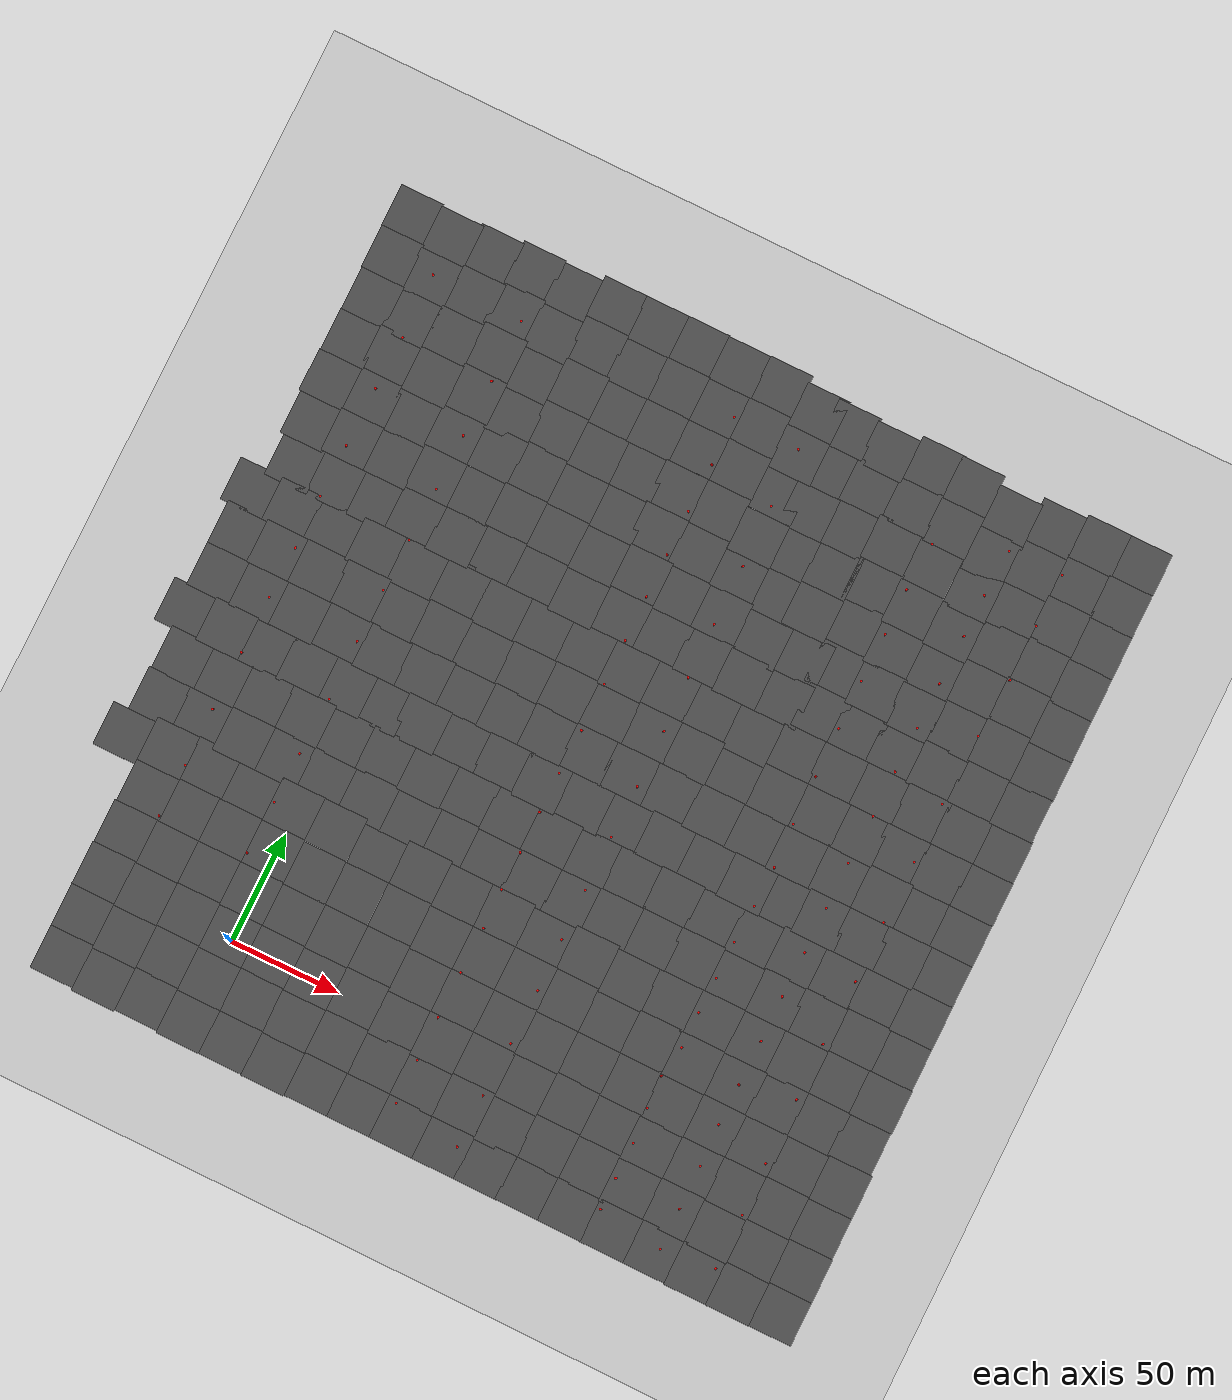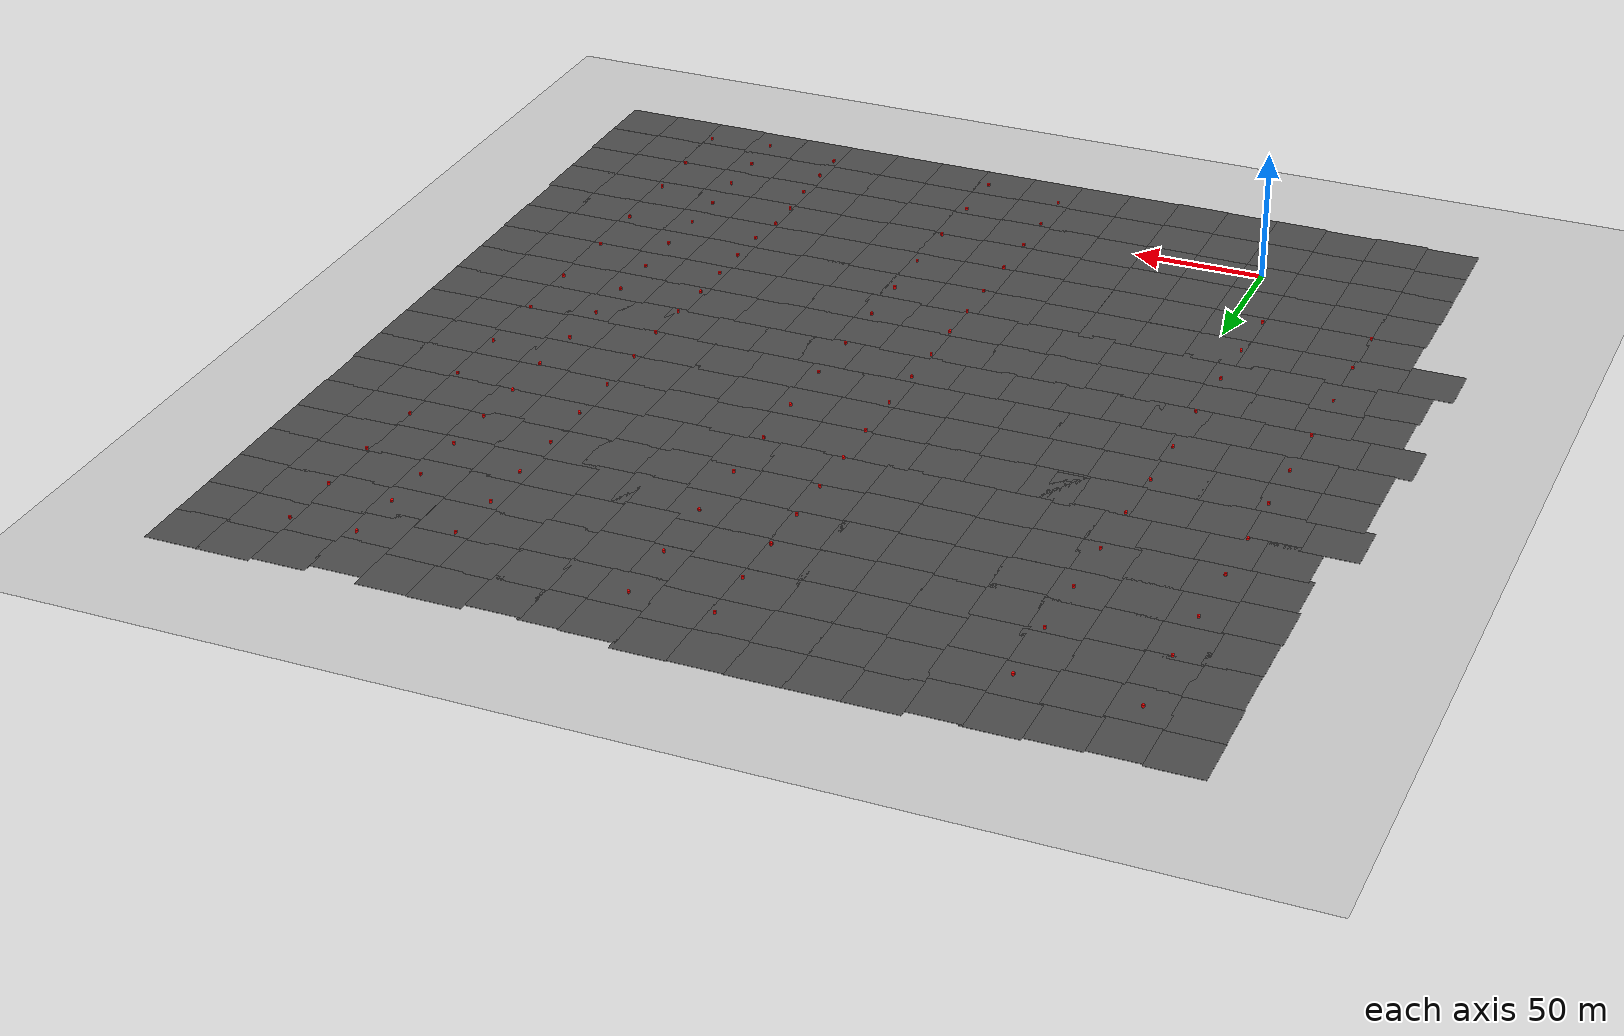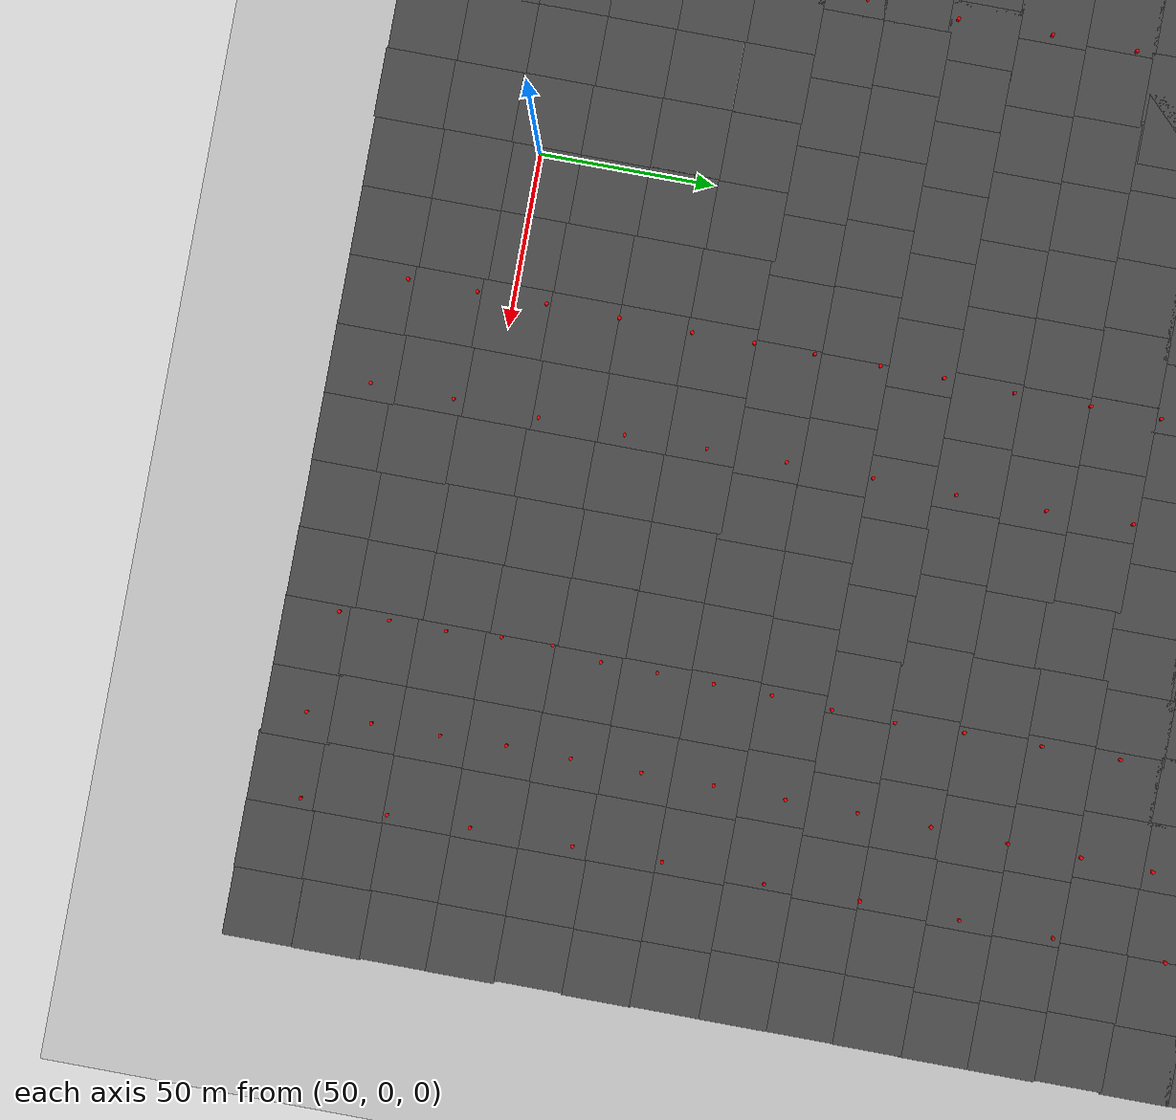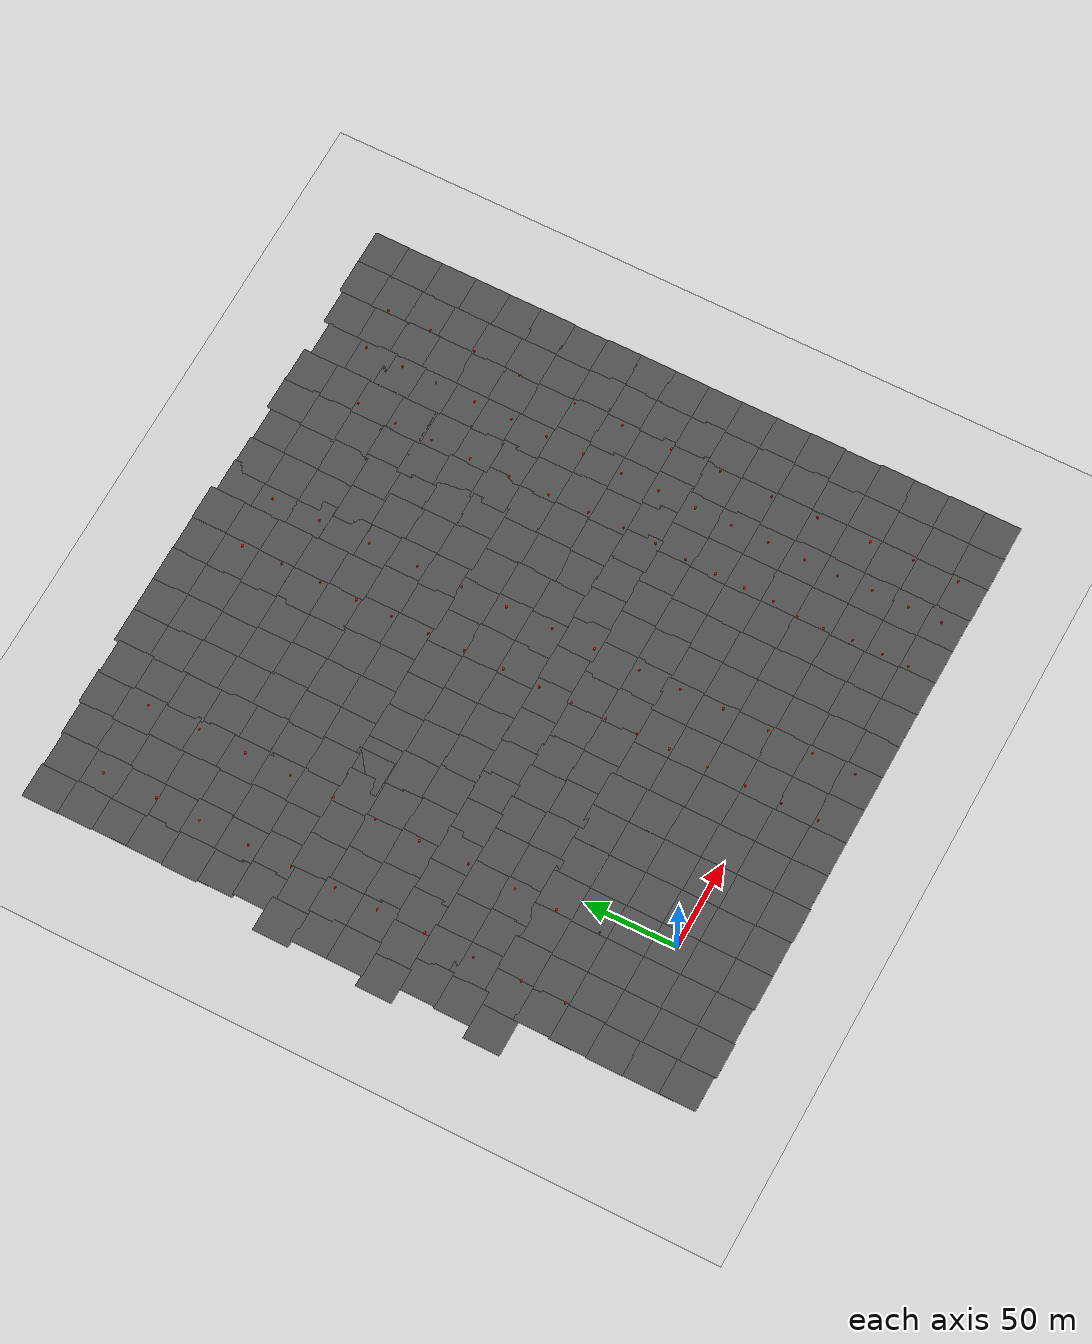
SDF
<sdf version="1.6">
 <world name="default">
  <light name="sun" type="directional">
   <pose>0 0 10 0 -0 0</pose>
   <diffuse>0.8 0.8 0.8 1</diffuse>
   <specular>0.2 0.2 0.2 1</specular>
   <attenuation>
    <range>1000</range>
    <constant>0.9</constant>
    <linear>0.01</linear>
    <quadratic>0.001</quadratic>
   </attenuation>
   <direction>-0.5 0.1 -0.9</direction>
  </light>
  <model name="ground_plane">
   <static>1</static>
   <link name="link">
    <collision name="collision">
     <geometry><plane><normal>0 0 1</normal><size>100 100</size></plane></geometry>
     <surface>
      <contact><collide_bitmask>65535</collide_bitmask></contact>
      <friction><ode><mu>100</mu><mu2>50</mu2></ode></friction>
     </surface>
    </collision>
    <visual name="visual">
     <cast_shadows>0</cast_shadows>
     <geometry><plane><normal>0 0 1</normal><size>100 100</size></plane></geometry>
     <material>
      <script><uri>file://media/materials/scripts/gazebo.material</uri><name>Gazebo/Grey</name></script>
     </material>
    </visual>
   </link>
  </model>
  <gravity>0 0 -9.8</gravity>
  <magnetic_field>6e-06 2.3e-05 -4.2e-05</magnetic_field>
  <atmosphere type="adiabatic"/>
  <physics name="default_physics" default="0" type="ode">
   <max_step_size>0.001</max_step_size>
   <real_time_factor>1</real_time_factor>
   <real_time_update_rate>1000</real_time_update_rate>
  </physics>
  <scene><ambient>0.4 0.4 0.4 1</ambient><background>0.7 0.7 0.7 1</background><shadows>1</shadows></scene>
  <audio><device>default</device></audio>
  <spherical_coordinates>
   <surface_model>EARTH_WGS84</surface_model>
   <latitude_deg>0</latitude_deg>
   <longitude_deg>0</longitude_deg>
   <elevation>0</elevation>
   <heading_deg>0</heading_deg>
  </spherical_coordinates>
  <model name="asphalt_plane">
   <static>1</static>
   <link name="link">
    <collision name="collision"><geometry><box><size>20 20 0.1</size></box></geometry></collision>
    <visual name="visual">
     <cast_shadows>0</cast_shadows>
     <geometry><box><size>20 20 0.1</size></box></geometry>
     <material>
      <script>
       <uri>model://asphalt_plane/materials/scripts</uri>
       <uri>model://asphalt_plane/materials/textures</uri>
       <name>vrc/asphalt</name>
      </script>
     </material>
    </visual>
   </link>
   <pose>-1.68563 1.69754 0 0 -0 0</pose>
  </model>
  <model name="asphalt_plane_0">
   <static>1</static>
   <link name="link">
    <collision name="collision"><geometry><box><size>20 20 0.1</size></box></geometry></collision>
    <visual name="visual">
     <cast_shadows>0</cast_shadows>
     <geometry><box><size>20 20 0.1</size></box></geometry>
     <material>
      <script>
       <uri>model://asphalt_plane/materials/scripts</uri>
       <uri>model://asphalt_plane/materials/textures</uri>
       <name>vrc/asphalt</name>
      </script>
     </material>
    </visual>
   </link>
   <pose>-21.6689 2.145 0 0 -0 0</pose>
  </model>
  <model name="asphalt_plane_1">
   <static>1</static>
   <link name="link">
    <collision name="collision"><geometry><box><size>20 20 0.1</size></box></geometry></collision>
    <visual name="visual">
     <cast_shadows>0</cast_shadows>
     <geometry><box><size>20 20 0.1</size></box></geometry>
     <material>
      <script>
       <uri>model://asphalt_plane/materials/scripts</uri>
       <uri>model://asphalt_plane/materials/textures</uri>
       <name>vrc/asphalt</name>
      </script>
     </material>
    </visual>
   </link>
   <pose>-21.6452 -17.7707 0 0 -0 0</pose>
  </model>
  <model name="asphalt_plane_2">
   <static>1</static>
   <link name="link">
    <collision name="collision"><geometry><box><size>20 20 0.1</size></box></geometry></collision>
    <visual name="visual">
     <cast_shadows>0</cast_shadows>
     <geometry><box><size>20 20 0.1</size></box></geometry>
     <material>
      <script>
       <uri>model://asphalt_plane/materials/scripts</uri>
       <uri>model://asphalt_plane/materials/textures</uri>
       <name>vrc/asphalt</name>
      </script>
     </material>
    </visual>
   </link>
   <pose>-1.66972 -18.2921 0 0 -0 0</pose>
  </model>
  <model name="asphalt_plane_3">
   <static>1</static>
   <link name="link">
    <collision name="collision"><geometry><box><size>20 20 0.1</size></box></geometry></collision>
    <visual name="visual">
     <cast_shadows>0</cast_shadows>
     <geometry><box><size>20 20 0.1</size></box></geometry>
     <material>
      <script>
       <uri>model://asphalt_plane/materials/scripts</uri>
       <uri>model://asphalt_plane/materials/textures</uri>
       <name>vrc/asphalt</name>
      </script>
     </material>
    </visual>
   </link>
   <pose>-1.6587 -38.2936 0 0 -0 0</pose>
  </model>
  <model name="asphalt_plane_4">
   <static>1</static>
   <link name="link">
    <collision name="collision"><geometry><box><size>20 20 0.1</size></box></geometry></collision>
    <visual name="visual">
     <cast_shadows>0</cast_shadows>
     <geometry><box><size>20 20 0.1</size></box></geometry>
     <material>
      <script>
       <uri>model://asphalt_plane/materials/scripts</uri>
       <uri>model://asphalt_plane/materials/textures</uri>
       <name>vrc/asphalt</name>
      </script>
     </material>
    </visual>
   </link>
   <pose>-21.5514 -37.4819 0 0 -0 0</pose>
  </model>
  <model name="asphalt_plane_5">
   <static>1</static>
   <link name="link">
    <collision name="collision"><geometry><box><size>20 20 0.1</size></box></geometry></collision>
    <visual name="visual">
     <cast_shadows>0</cast_shadows>
     <geometry><box><size>20 20 0.1</size></box></geometry>
     <material>
      <script>
       <uri>model://asphalt_plane/materials/scripts</uri>
       <uri>model://asphalt_plane/materials/textures</uri>
       <name>vrc/asphalt</name>
      </script>
     </material>
    </visual>
   </link>
   <pose>-21.6627 21.6769 0 0 -0 0</pose>
  </model>
  <model name="asphalt_plane_6">
   <static>1</static>
   <link name="link">
    <collision name="collision"><geometry><box><size>20 20 0.1</size></box></geometry></collision>
    <visual name="visual">
     <cast_shadows>0</cast_shadows>
     <geometry><box><size>20 20 0.1</size></box></geometry>
     <material>
      <script>
       <uri>model://asphalt_plane/materials/scripts</uri>
       <uri>model://asphalt_plane/materials/textures</uri>
       <name>vrc/asphalt</name>
      </script>
     </material>
    </visual>
   </link>
   <pose>-21.6696 41.6469 0 0 -0 0</pose>
  </model>
  <model name="asphalt_plane_7">
   <static>1</static>
   <link name="link">
    <collision name="collision"><geometry><box><size>20 20 0.1</size></box></geometry></collision>
    <visual name="visual">
     <cast_shadows>0</cast_shadows>
     <geometry><box><size>20 20 0.1</size></box></geometry>
     <material>
      <script>
       <uri>model://asphalt_plane/materials/scripts</uri>
       <uri>model://asphalt_plane/materials/textures</uri>
       <name>vrc/asphalt</name>
      </script>
     </material>
    </visual>
   </link>
   <pose>-1.7727 21.6828 0 0 -0 0</pose>
  </model>
  <model name="asphalt_plane_8">
   <static>1</static>
   <link name="link">
    <collision name="collision"><geometry><box><size>20 20 0.1</size></box></geometry></collision>
    <visual name="visual">
     <cast_shadows>0</cast_shadows>
     <geometry><box><size>20 20 0.1</size></box></geometry>
     <material>
      <script>
       <uri>model://asphalt_plane/materials/scripts</uri>
       <uri>model://asphalt_plane/materials/textures</uri>
       <name>vrc/asphalt</name>
      </script>
     </material>
    </visual>
   </link>
   <pose>-1.71814 41.6665 0 0 -0 0</pose>
  </model>
  <model name="asphalt_plane_9">
   <static>1</static>
   <link name="link">
    <collision name="collision"><geometry><box><size>20 20 0.1</size></box></geometry></collision>
    <visual name="visual">
     <cast_shadows>0</cast_shadows>
     <geometry><box><size>20 20 0.1</size></box></geometry>
     <material>
      <script>
       <uri>model://asphalt_plane/materials/scripts</uri>
       <uri>model://asphalt_plane/materials/textures</uri>
       <name>vrc/asphalt</name>
      </script>
     </material>
    </visual>
   </link>
   <pose>18.2406 -38.2098 0 0 -0 0</pose>
  </model>
  <model name="asphalt_plane_10">
   <static>1</static>
   <link name="link">
    <collision name="collision"><geometry><box><size>20 20 0.1</size></box></geometry></collision>
    <visual name="visual">
     <cast_shadows>0</cast_shadows>
     <geometry><box><size>20 20 0.1</size></box></geometry>
     <material>
      <script>
       <uri>model://asphalt_plane/materials/scripts</uri>
       <uri>model://asphalt_plane/materials/textures</uri>
       <name>vrc/asphalt</name>
      </script>
     </material>
    </visual>
   </link>
   <pose>18.2862 -18.2897 0 0 -0 0</pose>
  </model>
  <model name="asphalt_plane_11">
   <static>1</static>
   <link name="link">
    <collision name="collision"><geometry><box><size>20 20 0.1</size></box></geometry></collision>
    <visual name="visual">
     <cast_shadows>0</cast_shadows>
     <geometry><box><size>20 20 0.1</size></box></geometry>
     <material>
      <script>
       <uri>model://asphalt_plane/materials/scripts</uri>
       <uri>model://asphalt_plane/materials/textures</uri>
       <name>vrc/asphalt</name>
      </script>
     </material>
    </visual>
   </link>
   <pose>18.1716 1.63074 0 0 -0 0</pose>
  </model>
  <model name="asphalt_plane_12">
   <static>1</static>
   <link name="link">
    <collision name="collision"><geometry><box><size>20 20 0.1</size></box></geometry></collision>
    <visual name="visual">
     <cast_shadows>0</cast_shadows>
     <geometry><box><size>20 20 0.1</size></box></geometry>
     <material>
      <script>
       <uri>model://asphalt_plane/materials/scripts</uri>
       <uri>model://asphalt_plane/materials/textures</uri>
       <name>vrc/asphalt</name>
      </script>
     </material>
    </visual>
   </link>
   <pose>18.2121 21.3576 0 0 -0 0</pose>
  </model>
  <model name="asphalt_plane_13">
   <static>1</static>
   <link name="link">
    <collision name="collision"><geometry><box><size>20 20 0.1</size></box></geometry></collision>
    <visual name="visual">
     <cast_shadows>0</cast_shadows>
     <geometry><box><size>20 20 0.1</size></box></geometry>
     <material>
      <script>
       <uri>model://asphalt_plane/materials/scripts</uri>
       <uri>model://asphalt_plane/materials/textures</uri>
       <name>vrc/asphalt</name>
      </script>
     </material>
    </visual>
   </link>
   <pose>18.0714 41.1468 0 0 -0 0</pose>
  </model>
  <model name="asphalt_plane_14">
   <static>1</static>
   <link name="link">
    <collision name="collision"><geometry><box><size>20 20 0.1</size></box></geometry></collision>
    <visual name="visual">
     <cast_shadows>0</cast_shadows>
     <geometry><box><size>20 20 0.1</size></box></geometry>
     <material>
      <script>
       <uri>model://asphalt_plane/materials/scripts</uri>
       <uri>model://asphalt_plane/materials/textures</uri>
       <name>vrc/asphalt</name>
      </script>
     </material>
    </visual>
   </link>
   <pose>37.9263 41.1508 0 0 -0 0</pose>
  </model>
  <model name="asphalt_plane_15">
   <static>1</static>
   <link name="link">
    <collision name="collision"><geometry><box><size>20 20 0.1</size></box></geometry></collision>
    <visual name="visual">
     <cast_shadows>0</cast_shadows>
     <geometry><box><size>20 20 0.1</size></box></geometry>
     <material>
      <script>
       <uri>model://asphalt_plane/materials/scripts</uri>
       <uri>model://asphalt_plane/materials/textures</uri>
       <name>vrc/asphalt</name>
      </script>
     </material>
    </visual>
   </link>
   <pose>38.1901 21.1895 0 0 -0 0</pose>
  </model>
  <model name="asphalt_plane_16">
   <static>1</static>
   <link name="link">
    <collision name="collision"><geometry><box><size>20 20 0.1</size></box></geometry></collision>
    <visual name="visual">
     <cast_shadows>0</cast_shadows>
     <geometry><box><size>20 20 0.1</size></box></geometry>
     <material>
      <script>
       <uri>model://asphalt_plane/materials/scripts</uri>
       <uri>model://asphalt_plane/materials/textures</uri>
       <name>vrc/asphalt</name>
      </script>
     </material>
    </visual>
   </link>
   <pose>38.1399 1.20757 0 0 -0 0</pose>
  </model>
  <model name="asphalt_plane_17">
   <static>1</static>
   <link name="link">
    <collision name="collision"><geometry><box><size>20 20 0.1</size></box></geometry></collision>
    <visual name="visual">
     <cast_shadows>0</cast_shadows>
     <geometry><box><size>20 20 0.1</size></box></geometry>
     <material>
      <script>
       <uri>model://asphalt_plane/materials/scripts</uri>
       <uri>model://asphalt_plane/materials/textures</uri>
       <name>vrc/asphalt</name>
      </script>
     </material>
    </visual>
   </link>
   <pose>38.0686 -18.6552 0 0 -0 0</pose>
  </model>
  <model name="asphalt_plane_18">
   <static>1</static>
   <link name="link">
    <collision name="collision"><geometry><box><size>20 20 0.1</size></box></geometry></collision>
    <visual name="visual">
     <cast_shadows>0</cast_shadows>
     <geometry><box><size>20 20 0.1</size></box></geometry>
     <material>
      <script>
       <uri>model://asphalt_plane/materials/scripts</uri>
       <uri>model://asphalt_plane/materials/textures</uri>
       <name>vrc/asphalt</name>
      </script>
     </material>
    </visual>
   </link>
   <pose>38.1798 -38.5906 0 0 -0 0</pose>
  </model>
  <model name="asphalt_plane_19">
   <static>1</static>
   <link name="link">
    <collision name="collision"><geometry><box><size>20 20 0.1</size></box></geometry></collision>
    <visual name="visual">
     <cast_shadows>0</cast_shadows>
     <geometry><box><size>20 20 0.1</size></box></geometry>
     <material>
      <script>
       <uri>model://asphalt_plane/materials/scripts</uri>
       <uri>model://asphalt_plane/materials/textures</uri>
       <name>vrc/asphalt</name>
      </script>
     </material>
    </visual>
   </link>
   <pose>-41.6151 41.6794 0 0 -0 0</pose>
  </model>
  <model name="asphalt_plane_20">
   <static>1</static>
   <link name="link">
    <collision name="collision"><geometry><box><size>20 20 0.1</size></box></geometry></collision>
    <visual name="visual">
     <cast_shadows>0</cast_shadows>
     <geometry><box><size>20 20 0.1</size></box></geometry>
     <material>
      <script>
       <uri>model://asphalt_plane/materials/scripts</uri>
       <uri>model://asphalt_plane/materials/textures</uri>
       <name>vrc/asphalt</name>
      </script>
     </material>
    </visual>
   </link>
   <pose>-41.6462 21.7314 0 0 -0 0</pose>
  </model>
  <model name="asphalt_plane_21">
   <static>1</static>
   <link name="link">
    <collision name="collision"><geometry><box><size>20 20 0.1</size></box></geometry></collision>
    <visual name="visual">
     <cast_shadows>0</cast_shadows>
     <geometry><box><size>20 20 0.1</size></box></geometry>
     <material>
      <script>
       <uri>model://asphalt_plane/materials/scripts</uri>
       <uri>model://asphalt_plane/materials/textures</uri>
       <name>vrc/asphalt</name>
      </script>
     </material>
    </visual>
   </link>
   <pose>-41.6242 1.80147 0 0 -0 0</pose>
  </model>
  <model name="asphalt_plane_22">
   <static>1</static>
   <link name="link">
    <collision name="collision"><geometry><box><size>20 20 0.1</size></box></geometry></collision>
    <visual name="visual">
     <cast_shadows>0</cast_shadows>
     <geometry><box><size>20 20 0.1</size></box></geometry>
     <material>
      <script>
       <uri>model://asphalt_plane/materials/scripts</uri>
       <uri>model://asphalt_plane/materials/textures</uri>
       <name>vrc/asphalt</name>
      </script>
     </material>
    </visual>
   </link>
   <pose>-41.5505 -18.1854 0 0 -0 0</pose>
  </model>
  <model name="asphalt_plane_23">
   <static>1</static>
   <link name="link">
    <collision name="collision"><geometry><box><size>20 20 0.1</size></box></geometry></collision>
    <visual name="visual">
     <cast_shadows>0</cast_shadows>
     <geometry><box><size>20 20 0.1</size></box></geometry>
     <material>
      <script>
       <uri>model://asphalt_plane/materials/scripts</uri>
       <uri>model://asphalt_plane/materials/textures</uri>
       <name>vrc/asphalt</name>
      </script>
     </material>
    </visual>
   </link>
   <pose>-41.5125 -38.0904 0 0 -0 0</pose>
  </model>
  <model name="asphalt_plane_24">
   <static>1</static>
   <link name="link">
    <collision name="collision"><geometry><box><size>20 20 0.1</size></box></geometry></collision>
    <visual name="visual">
     <cast_shadows>0</cast_shadows>
     <geometry><box><size>20 20 0.1</size></box></geometry>
     <material>
      <script>
       <uri>model://asphalt_plane/materials/scripts</uri>
       <uri>model://asphalt_plane/materials/textures</uri>
       <name>vrc/asphalt</name>
      </script>
     </material>
    </visual>
   </link>
   <pose>38.2357 61.0231 0 0 -0 0</pose>
  </model>
  <model name="asphalt_plane_25">
   <static>1</static>
   <link name="link">
    <collision name="collision"><geometry><box><size>20 20 0.1</size></box></geometry></collision>
    <visual name="visual">
     <cast_shadows>0</cast_shadows>
     <geometry><box><size>20 20 0.1</size></box></geometry>
     <material>
      <script>
       <uri>model://asphalt_plane/materials/scripts</uri>
       <uri>model://asphalt_plane/materials/textures</uri>
       <name>vrc/asphalt</name>
      </script>
     </material>
    </visual>
   </link>
   <pose>18.22 61.2506 0 0 -0 0</pose>
  </model>
  <model name="asphalt_plane_26">
   <static>1</static>
   <link name="link">
    <collision name="collision"><geometry><box><size>20 20 0.1</size></box></geometry></collision>
    <visual name="visual">
     <cast_shadows>0</cast_shadows>
     <geometry><box><size>20 20 0.1</size></box></geometry>
     <material>
      <script>
       <uri>model://asphalt_plane/materials/scripts</uri>
       <uri>model://asphalt_plane/materials/textures</uri>
       <name>vrc/asphalt</name>
      </script>
     </material>
    </visual>
   </link>
   <pose>-1.5571 61.3628 0 0 -0 0</pose>
  </model>
  <model name="asphalt_plane_27">
   <static>1</static>
   <link name="link">
    <collision name="collision"><geometry><box><size>20 20 0.1</size></box></geometry></collision>
    <visual name="visual">
     <cast_shadows>0</cast_shadows>
     <geometry><box><size>20 20 0.1</size></box></geometry>
     <material>
      <script>
       <uri>model://asphalt_plane/materials/scripts</uri>
       <uri>model://asphalt_plane/materials/textures</uri>
       <name>vrc/asphalt</name>
      </script>
     </material>
    </visual>
   </link>
   <pose>-21.1441 61.4149 0 0 -0 0</pose>
  </model>
  <model name="asphalt_plane_28">
   <static>1</static>
   <link name="link">
    <collision name="collision"><geometry><box><size>20 20 0.1</size></box></geometry></collision>
    <visual name="visual">
     <cast_shadows>0</cast_shadows>
     <geometry><box><size>20 20 0.1</size></box></geometry>
     <material>
      <script>
       <uri>model://asphalt_plane/materials/scripts</uri>
       <uri>model://asphalt_plane/materials/textures</uri>
       <name>vrc/asphalt</name>
      </script>
     </material>
    </visual>
   </link>
   <pose>-40.8033 61.467 0 0 -0 0</pose>
  </model>
  <model name="asphalt_plane_29">
   <static>1</static>
   <link name="link">
    <collision name="collision"><geometry><box><size>20 20 0.1</size></box></geometry></collision>
    <visual name="visual">
     <cast_shadows>0</cast_shadows>
     <geometry><box><size>20 20 0.1</size></box></geometry>
     <material>
      <script>
       <uri>model://asphalt_plane/materials/scripts</uri>
       <uri>model://asphalt_plane/materials/textures</uri>
       <name>vrc/asphalt</name>
      </script>
     </material>
    </visual>
   </link>
   <pose>58.0302 60.9847 0 0 -0 0</pose>
  </model>
  <model name="asphalt_plane_30">
   <static>1</static>
   <link name="link">
    <collision name="collision"><geometry><box><size>20 20 0.1</size></box></geometry></collision>
    <visual name="visual">
     <cast_shadows>0</cast_shadows>
     <geometry><box><size>20 20 0.1</size></box></geometry>
     <material>
      <script>
       <uri>model://asphalt_plane/materials/scripts</uri>
       <uri>model://asphalt_plane/materials/textures</uri>
       <name>vrc/asphalt</name>
      </script>
     </material>
    </visual>
   </link>
   <pose>57.9845 41.105 0 0 -0 0</pose>
  </model>
  <model name="asphalt_plane_31">
   <static>1</static>
   <link name="link">
    <collision name="collision"><geometry><box><size>20 20 0.1</size></box></geometry></collision>
    <visual name="visual">
     <cast_shadows>0</cast_shadows>
     <geometry><box><size>20 20 0.1</size></box></geometry>
     <material>
      <script>
       <uri>model://asphalt_plane/materials/scripts</uri>
       <uri>model://asphalt_plane/materials/textures</uri>
       <name>vrc/asphalt</name>
      </script>
     </material>
    </visual>
   </link>
   <pose>57.9861 21.3964 0 0 -0 0</pose>
  </model>
  <model name="asphalt_plane_32">
   <static>1</static>
   <link name="link">
    <collision name="collision"><geometry><box><size>20 20 0.1</size></box></geometry></collision>
    <visual name="visual">
     <cast_shadows>0</cast_shadows>
     <geometry><box><size>20 20 0.1</size></box></geometry>
     <material>
      <script>
       <uri>model://asphalt_plane/materials/scripts</uri>
       <uri>model://asphalt_plane/materials/textures</uri>
       <name>vrc/asphalt</name>
      </script>
     </material>
    </visual>
   </link>
   <pose>57.9543 1.80732 0 0 -0 0</pose>
  </model>
  <model name="asphalt_plane_33">
   <static>1</static>
   <link name="link">
    <collision name="collision"><geometry><box><size>20 20 0.1</size></box></geometry></collision>
    <visual name="visual">
     <cast_shadows>0</cast_shadows>
     <geometry><box><size>20 20 0.1</size></box></geometry>
     <material>
      <script>
       <uri>model://asphalt_plane/materials/scripts</uri>
       <uri>model://asphalt_plane/materials/textures</uri>
       <name>vrc/asphalt</name>
      </script>
     </material>
    </visual>
   </link>
   <pose>58.0356 -18.1613 0 0 -0 0</pose>
  </model>
  <model name="asphalt_plane_34">
   <static>1</static>
   <link name="link">
    <collision name="collision"><geometry><box><size>20 20 0.1</size></box></geometry></collision>
    <visual name="visual">
     <cast_shadows>0</cast_shadows>
     <geometry><box><size>20 20 0.1</size></box></geometry>
     <material>
      <script>
       <uri>model://asphalt_plane/materials/scripts</uri>
       <uri>model://asphalt_plane/materials/textures</uri>
       <name>vrc/asphalt</name>
      </script>
     </material>
    </visual>
   </link>
   <pose>58.0553 -38.1405 0 0 -0 0</pose>
  </model>
  <model name="asphalt_plane_35">
   <static>1</static>
   <link name="link">
    <collision name="collision"><geometry><box><size>20 20 0.1</size></box></geometry></collision>
    <visual name="visual">
     <cast_shadows>0</cast_shadows>
     <geometry><box><size>20 20 0.1</size></box></geometry>
     <material>
      <script>
       <uri>model://asphalt_plane/materials/scripts</uri>
       <uri>model://asphalt_plane/materials/textures</uri>
       <name>vrc/asphalt</name>
      </script>
     </material>
    </visual>
   </link>
   <pose>77.8688 -38.1153 0 0 -0 0</pose>
  </model>
  <model name="asphalt_plane_36">
   <static>1</static>
   <link name="link">
    <collision name="collision"><geometry><box><size>20 20 0.1</size></box></geometry></collision>
    <visual name="visual">
     <cast_shadows>0</cast_shadows>
     <geometry><box><size>20 20 0.1</size></box></geometry>
     <material>
      <script>
       <uri>model://asphalt_plane/materials/scripts</uri>
       <uri>model://asphalt_plane/materials/textures</uri>
       <name>vrc/asphalt</name>
      </script>
     </material>
    </visual>
   </link>
   <pose>77.8708 -18.1634 0 0 -0 0</pose>
  </model>
  <model name="asphalt_plane_37">
   <static>1</static>
   <link name="link">
    <collision name="collision"><geometry><box><size>20 20 0.1</size></box></geometry></collision>
    <visual name="visual">
     <cast_shadows>0</cast_shadows>
     <geometry><box><size>20 20 0.1</size></box></geometry>
     <material>
      <script>
       <uri>model://asphalt_plane/materials/scripts</uri>
       <uri>model://asphalt_plane/materials/textures</uri>
       <name>vrc/asphalt</name>
      </script>
     </material>
    </visual>
   </link>
   <pose>77.8641 0.739913 0 0 -0 0</pose>
  </model>
  <model name="asphalt_plane_38">
   <static>1</static>
   <link name="link">
    <collision name="collision"><geometry><box><size>20 20 0.1</size></box></geometry></collision>
    <visual name="visual">
     <cast_shadows>0</cast_shadows>
     <geometry><box><size>20 20 0.1</size></box></geometry>
     <material>
      <script>
       <uri>model://asphalt_plane/materials/scripts</uri>
       <uri>model://asphalt_plane/materials/textures</uri>
       <name>vrc/asphalt</name>
      </script>
     </material>
    </visual>
   </link>
   <pose>77.9741 20.3819 0 0 -0 0</pose>
  </model>
  <model name="asphalt_plane_39">
   <static>1</static>
   <link name="link">
    <collision name="collision"><geometry><box><size>20 20 0.1</size></box></geometry></collision>
    <visual name="visual">
     <cast_shadows>0</cast_shadows>
     <geometry><box><size>20 20 0.1</size></box></geometry>
     <material>
      <script>
       <uri>model://asphalt_plane/materials/scripts</uri>
       <uri>model://asphalt_plane/materials/textures</uri>
       <name>vrc/asphalt</name>
      </script>
     </material>
    </visual>
   </link>
   <pose>77.9123 40.3011 0 0 -0 0</pose>
  </model>
  <model name="asphalt_plane_40">
   <static>1</static>
   <link name="link">
    <collision name="collision"><geometry><box><size>20 20 0.1</size></box></geometry></collision>
    <visual name="visual">
     <cast_shadows>0</cast_shadows>
     <geometry><box><size>20 20 0.1</size></box></geometry>
     <material>
      <script>
       <uri>model://asphalt_plane/materials/scripts</uri>
       <uri>model://asphalt_plane/materials/textures</uri>
       <name>vrc/asphalt</name>
      </script>
     </material>
    </visual>
   </link>
   <pose>77.8982 59.9632 0 0 -0 0</pose>
  </model>
  <model name="asphalt_plane_41">
   <static>1</static>
   <link name="link">
    <collision name="collision"><geometry><box><size>20 20 0.1</size></box></geometry></collision>
    <visual name="visual">
     <cast_shadows>0</cast_shadows>
     <geometry><box><size>20 20 0.1</size></box></geometry>
     <material>
      <script>
       <uri>model://asphalt_plane/materials/scripts</uri>
       <uri>model://asphalt_plane/materials/textures</uri>
       <name>vrc/asphalt</name>
      </script>
     </material>
    </visual>
   </link>
   <pose>97.6549 59.9109 0 0 -0 0</pose>
  </model>
  <model name="asphalt_plane_42">
   <static>1</static>
   <link name="link">
    <collision name="collision"><geometry><box><size>20 20 0.1</size></box></geometry></collision>
    <visual name="visual">
     <cast_shadows>0</cast_shadows>
     <geometry><box><size>20 20 0.1</size></box></geometry>
     <material>
      <script>
       <uri>model://asphalt_plane/materials/scripts</uri>
       <uri>model://asphalt_plane/materials/textures</uri>
       <name>vrc/asphalt</name>
      </script>
     </material>
    </visual>
   </link>
   <pose>97.6996 40.3637 0 0 -0 0</pose>
  </model>
  <model name="asphalt_plane_43">
   <static>1</static>
   <link name="link">
    <collision name="collision"><geometry><box><size>20 20 0.1</size></box></geometry></collision>
    <visual name="visual">
     <cast_shadows>0</cast_shadows>
     <geometry><box><size>20 20 0.1</size></box></geometry>
     <material>
      <script>
       <uri>model://asphalt_plane/materials/scripts</uri>
       <uri>model://asphalt_plane/materials/textures</uri>
       <name>vrc/asphalt</name>
      </script>
     </material>
    </visual>
   </link>
   <pose>97.7369 20.5205 0 0 -0 0</pose>
  </model>
  <model name="asphalt_plane_44">
   <static>1</static>
   <link name="link">
    <collision name="collision"><geometry><box><size>20 20 0.1</size></box></geometry></collision>
    <visual name="visual">
     <cast_shadows>0</cast_shadows>
     <geometry><box><size>20 20 0.1</size></box></geometry>
     <material>
      <script>
       <uri>model://asphalt_plane/materials/scripts</uri>
       <uri>model://asphalt_plane/materials/textures</uri>
       <name>vrc/asphalt</name>
      </script>
     </material>
    </visual>
   </link>
   <pose>97.6593 0.629561 0 0 -0 0</pose>
  </model>
  <model name="asphalt_plane_45">
   <static>1</static>
   <link name="link">
    <collision name="collision"><geometry><box><size>20 20 0.1</size></box></geometry></collision>
    <visual name="visual">
     <cast_shadows>0</cast_shadows>
     <geometry><box><size>20 20 0.1</size></box></geometry>
     <material>
      <script>
       <uri>model://asphalt_plane/materials/scripts</uri>
       <uri>model://asphalt_plane/materials/textures</uri>
       <name>vrc/asphalt</name>
      </script>
     </material>
    </visual>
   </link>
   <pose>97.5885 -18.7822 0 0 -0 0</pose>
  </model>
  <model name="asphalt_plane_46">
   <static>1</static>
   <link name="link">
    <collision name="collision"><geometry><box><size>20 20 0.1</size></box></geometry></collision>
    <visual name="visual">
     <cast_shadows>0</cast_shadows>
     <geometry><box><size>20 20 0.1</size></box></geometry>
     <material>
      <script>
       <uri>model://asphalt_plane/materials/scripts</uri>
       <uri>model://asphalt_plane/materials/textures</uri>
       <name>vrc/asphalt</name>
      </script>
     </material>
    </visual>
   </link>
   <pose>97.7762 -38.112 0 0 -0 0</pose>
  </model>
  <model name="asphalt_plane_47">
   <static>1</static>
   <link name="link">
    <collision name="collision"><geometry><box><size>20 20 0.1</size></box></geometry></collision>
    <visual name="visual">
     <cast_shadows>0</cast_shadows>
     <geometry><box><size>20 20 0.1</size></box></geometry>
     <material>
      <script>
       <uri>model://asphalt_plane/materials/scripts</uri>
       <uri>model://asphalt_plane/materials/textures</uri>
       <name>vrc/asphalt</name>
      </script>
     </material>
    </visual>
   </link>
   <pose>117.725 -38.1173 0 0 -0 0</pose>
  </model>
  <model name="asphalt_plane_48">
   <static>1</static>
   <link name="link">
    <collision name="collision"><geometry><box><size>20 20 0.1</size></box></geometry></collision>
    <visual name="visual">
     <cast_shadows>0</cast_shadows>
     <geometry><box><size>20 20 0.1</size></box></geometry>
     <material>
      <script>
       <uri>model://asphalt_plane/materials/scripts</uri>
       <uri>model://asphalt_plane/materials/textures</uri>
       <name>vrc/asphalt</name>
      </script>
     </material>
    </visual>
   </link>
   <pose>117.418 -18.5588 0 0 -0 0</pose>
  </model>
  <model name="asphalt_plane_49">
   <static>1</static>
   <link name="link">
    <collision name="collision"><geometry><box><size>20 20 0.1</size></box></geometry></collision>
    <visual name="visual">
     <cast_shadows>0</cast_shadows>
     <geometry><box><size>20 20 0.1</size></box></geometry>
     <material>
      <script>
       <uri>model://asphalt_plane/materials/scripts</uri>
       <uri>model://asphalt_plane/materials/textures</uri>
       <name>vrc/asphalt</name>
      </script>
     </material>
    </visual>
   </link>
   <pose>117.461 1.3262 0 0 -0 0</pose>
  </model>
  <model name="asphalt_plane_50">
   <static>1</static>
   <link name="link">
    <collision name="collision"><geometry><box><size>20 20 0.1</size></box></geometry></collision>
    <visual name="visual">
     <cast_shadows>0</cast_shadows>
     <geometry><box><size>20 20 0.1</size></box></geometry>
     <material>
      <script>
       <uri>model://asphalt_plane/materials/scripts</uri>
       <uri>model://asphalt_plane/materials/textures</uri>
       <name>vrc/asphalt</name>
      </script>
     </material>
    </visual>
   </link>
   <pose>117.561 20.5883 0 0 -0 0</pose>
  </model>
  <model name="asphalt_plane_51">
   <static>1</static>
   <link name="link">
    <collision name="collision"><geometry><box><size>20 20 0.1</size></box></geometry></collision>
    <visual name="visual">
     <cast_shadows>0</cast_shadows>
     <geometry><box><size>20 20 0.1</size></box></geometry>
     <material>
      <script>
       <uri>model://asphalt_plane/materials/scripts</uri>
       <uri>model://asphalt_plane/materials/textures</uri>
       <name>vrc/asphalt</name>
      </script>
     </material>
    </visual>
   </link>
   <pose>117.597 40.3072 0 0 -0 0</pose>
  </model>
  <model name="asphalt_plane_52">
   <static>1</static>
   <link name="link">
    <collision name="collision"><geometry><box><size>20 20 0.1</size></box></geometry></collision>
    <visual name="visual">
     <cast_shadows>0</cast_shadows>
     <geometry><box><size>20 20 0.1</size></box></geometry>
     <material>
      <script>
       <uri>model://asphalt_plane/materials/scripts</uri>
       <uri>model://asphalt_plane/materials/textures</uri>
       <name>vrc/asphalt</name>
      </script>
     </material>
    </visual>
   </link>
   <pose>117.611 60.0083 0 0 -0 0</pose>
  </model>
  <model name="asphalt_plane_53">
   <static>1</static>
   <link name="link">
    <collision name="collision"><geometry><box><size>20 20 0.1</size></box></geometry></collision>
    <visual name="visual">
     <cast_shadows>0</cast_shadows>
     <geometry><box><size>20 20 0.1</size></box></geometry>
     <material>
      <script>
       <uri>model://asphalt_plane/materials/scripts</uri>
       <uri>model://asphalt_plane/materials/textures</uri>
       <name>vrc/asphalt</name>
      </script>
     </material>
    </visual>
   </link>
   <pose>136.964 59.9939 0 0 -0 0</pose>
  </model>
  <model name="asphalt_plane_54">
   <static>1</static>
   <link name="link">
    <collision name="collision"><geometry><box><size>20 20 0.1</size></box></geometry></collision>
    <visual name="visual">
     <cast_shadows>0</cast_shadows>
     <geometry><box><size>20 20 0.1</size></box></geometry>
     <material>
      <script>
       <uri>model://asphalt_plane/materials/scripts</uri>
       <uri>model://asphalt_plane/materials/textures</uri>
       <name>vrc/asphalt</name>
      </script>
     </material>
    </visual>
   </link>
   <pose>136.97 40.0461 0 0 -0 0</pose>
  </model>
  <model name="asphalt_plane_55">
   <static>1</static>
   <link name="link">
    <collision name="collision"><geometry><box><size>20 20 0.1</size></box></geometry></collision>
    <visual name="visual">
     <cast_shadows>0</cast_shadows>
     <geometry><box><size>20 20 0.1</size></box></geometry>
     <material>
      <script>
       <uri>model://asphalt_plane/materials/scripts</uri>
       <uri>model://asphalt_plane/materials/textures</uri>
       <name>vrc/asphalt</name>
      </script>
     </material>
    </visual>
   </link>
   <pose>136.974 20.2339 0 0 -0 0</pose>
  </model>
  <model name="asphalt_plane_56">
   <static>1</static>
   <link name="link">
    <collision name="collision"><geometry><box><size>20 20 0.1</size></box></geometry></collision>
    <visual name="visual">
     <cast_shadows>0</cast_shadows>
     <geometry><box><size>20 20 0.1</size></box></geometry>
     <material>
      <script>
       <uri>model://asphalt_plane/materials/scripts</uri>
       <uri>model://asphalt_plane/materials/textures</uri>
       <name>vrc/asphalt</name>
      </script>
     </material>
    </visual>
   </link>
   <pose>136.959 0.447684 0 0 -0 0</pose>
  </model>
  <model name="asphalt_plane_57">
   <static>1</static>
   <link name="link">
    <collision name="collision"><geometry><box><size>20 20 0.1</size></box></geometry></collision>
    <visual name="visual">
     <cast_shadows>0</cast_shadows>
     <geometry><box><size>20 20 0.1</size></box></geometry>
     <material>
      <script>
       <uri>model://asphalt_plane/materials/scripts</uri>
       <uri>model://asphalt_plane/materials/textures</uri>
       <name>vrc/asphalt</name>
      </script>
     </material>
    </visual>
   </link>
   <pose>137.26 -19.4886 0 0 -0 0</pose>
  </model>
  <model name="asphalt_plane_58">
   <static>1</static>
   <link name="link">
    <collision name="collision"><geometry><box><size>20 20 0.1</size></box></geometry></collision>
    <visual name="visual">
     <cast_shadows>0</cast_shadows>
     <geometry><box><size>20 20 0.1</size></box></geometry>
     <material>
      <script>
       <uri>model://asphalt_plane/materials/scripts</uri>
       <uri>model://asphalt_plane/materials/textures</uri>
       <name>vrc/asphalt</name>
      </script>
     </material>
    </visual>
   </link>
   <pose>137.149 -38.126 0 0 -0 0</pose>
  </model>
  <model name="asphalt_plane_59">
   <static>1</static>
   <link name="link">
    <collision name="collision"><geometry><box><size>20 20 0.1</size></box></geometry></collision>
    <visual name="visual">
     <cast_shadows>0</cast_shadows>
     <geometry><box><size>20 20 0.1</size></box></geometry>
     <material>
      <script>
       <uri>model://asphalt_plane/materials/scripts</uri>
       <uri>model://asphalt_plane/materials/textures</uri>
       <name>vrc/asphalt</name>
      </script>
     </material>
    </visual>
   </link>
   <pose>156.487 -38.0347 0 0 -0 0</pose>
  </model>
  <model name="asphalt_plane_60">
   <static>1</static>
   <link name="link">
    <collision name="collision"><geometry><box><size>20 20 0.1</size></box></geometry></collision>
    <visual name="visual">
     <cast_shadows>0</cast_shadows>
     <geometry><box><size>20 20 0.1</size></box></geometry>
     <material>
      <script>
       <uri>model://asphalt_plane/materials/scripts</uri>
       <uri>model://asphalt_plane/materials/textures</uri>
       <name>vrc/asphalt</name>
      </script>
     </material>
    </visual>
   </link>
   <pose>156.663 -18.4522 0 0 -0 0</pose>
  </model>
  <model name="asphalt_plane_61">
   <static>1</static>
   <link name="link">
    <collision name="collision"><geometry><box><size>20 20 0.1</size></box></geometry></collision>
    <visual name="visual">
     <cast_shadows>0</cast_shadows>
     <geometry><box><size>20 20 0.1</size></box></geometry>
     <material>
      <script>
       <uri>model://asphalt_plane/materials/scripts</uri>
       <uri>model://asphalt_plane/materials/textures</uri>
       <name>vrc/asphalt</name>
      </script>
     </material>
    </visual>
   </link>
   <pose>156.766 1.17903 0 0 -0 0</pose>
  </model>
  <model name="asphalt_plane_62">
   <static>1</static>
   <link name="link">
    <collision name="collision"><geometry><box><size>20 20 0.1</size></box></geometry></collision>
    <visual name="visual">
     <cast_shadows>0</cast_shadows>
     <geometry><box><size>20 20 0.1</size></box></geometry>
     <material>
      <script>
       <uri>model://asphalt_plane/materials/scripts</uri>
       <uri>model://asphalt_plane/materials/textures</uri>
       <name>vrc/asphalt</name>
      </script>
     </material>
    </visual>
   </link>
   <pose>156.898 20.6474 0 0 -0 0</pose>
  </model>
  <model name="asphalt_plane_63">
   <static>1</static>
   <link name="link">
    <collision name="collision"><geometry><box><size>20 20 0.1</size></box></geometry></collision>
    <visual name="visual">
     <cast_shadows>0</cast_shadows>
     <geometry><box><size>20 20 0.1</size></box></geometry>
     <material>
      <script>
       <uri>model://asphalt_plane/materials/scripts</uri>
       <uri>model://asphalt_plane/materials/textures</uri>
       <name>vrc/asphalt</name>
      </script>
     </material>
    </visual>
   </link>
   <pose>156.775 40.0286 0 0 -0 0</pose>
  </model>
  <model name="asphalt_plane_64">
   <static>1</static>
   <link name="link">
    <collision name="collision"><geometry><box><size>20 20 0.1</size></box></geometry></collision>
    <visual name="visual">
     <cast_shadows>0</cast_shadows>
     <geometry><box><size>20 20 0.1</size></box></geometry>
     <material>
      <script>
       <uri>model://asphalt_plane/materials/scripts</uri>
       <uri>model://asphalt_plane/materials/textures</uri>
       <name>vrc/asphalt</name>
      </script>
     </material>
    </visual>
   </link>
   <pose>156.941 58.8997 0 0 -0 0</pose>
  </model>
  <model name="asphalt_plane_65">
   <static>1</static>
   <link name="link">
    <collision name="collision"><geometry><box><size>20 20 0.1</size></box></geometry></collision>
    <visual name="visual">
     <cast_shadows>0</cast_shadows>
     <geometry><box><size>20 20 0.1</size></box></geometry>
     <material>
      <script>
       <uri>model://asphalt_plane/materials/scripts</uri>
       <uri>model://asphalt_plane/materials/textures</uri>
       <name>vrc/asphalt</name>
      </script>
     </material>
    </visual>
   </link>
   <pose>176.35 -38.1595 0 0 -0 0</pose>
  </model>
  <model name="asphalt_plane_66">
   <static>1</static>
   <link name="link">
    <collision name="collision"><geometry><box><size>20 20 0.1</size></box></geometry></collision>
    <visual name="visual">
     <cast_shadows>0</cast_shadows>
     <geometry><box><size>20 20 0.1</size></box></geometry>
     <material>
      <script>
       <uri>model://asphalt_plane/materials/scripts</uri>
       <uri>model://asphalt_plane/materials/textures</uri>
       <name>vrc/asphalt</name>
      </script>
     </material>
    </visual>
   </link>
   <pose>176.208 -18.6943 0 0 -0 0</pose>
  </model>
  <model name="asphalt_plane_67">
   <static>1</static>
   <link name="link">
    <collision name="collision"><geometry><box><size>20 20 0.1</size></box></geometry></collision>
    <visual name="visual">
     <cast_shadows>0</cast_shadows>
     <geometry><box><size>20 20 0.1</size></box></geometry>
     <material>
      <script>
       <uri>model://asphalt_plane/materials/scripts</uri>
       <uri>model://asphalt_plane/materials/textures</uri>
       <name>vrc/asphalt</name>
      </script>
     </material>
    </visual>
   </link>
   <pose>176.281 0.711573 0 0 -0 0</pose>
  </model>
  <model name="asphalt_plane_68">
   <static>1</static>
   <link name="link">
    <collision name="collision"><geometry><box><size>20 20 0.1</size></box></geometry></collision>
    <visual name="visual">
     <cast_shadows>0</cast_shadows>
     <geometry><box><size>20 20 0.1</size></box></geometry>
     <material>
      <script>
       <uri>model://asphalt_plane/materials/scripts</uri>
       <uri>model://asphalt_plane/materials/textures</uri>
       <name>vrc/asphalt</name>
      </script>
     </material>
    </visual>
   </link>
   <pose>176.432 20.2894 0 0 -0 0</pose>
  </model>
  <model name="asphalt_plane_69">
   <static>1</static>
   <link name="link">
    <collision name="collision"><geometry><box><size>20 20 0.1</size></box></geometry></collision>
    <visual name="visual">
     <cast_shadows>0</cast_shadows>
     <geometry><box><size>20 20 0.1</size></box></geometry>
     <material>
      <script>
       <uri>model://asphalt_plane/materials/scripts</uri>
       <uri>model://asphalt_plane/materials/textures</uri>
       <name>vrc/asphalt</name>
      </script>
     </material>
    </visual>
   </link>
   <pose>176.575 39.843 0 0 -0 0</pose>
  </model>
  <model name="asphalt_plane_70">
   <static>1</static>
   <link name="link">
    <collision name="collision"><geometry><box><size>20 20 0.1</size></box></geometry></collision>
    <visual name="visual">
     <cast_shadows>0</cast_shadows>
     <geometry><box><size>20 20 0.1</size></box></geometry>
     <material>
      <script>
       <uri>model://asphalt_plane/materials/scripts</uri>
       <uri>model://asphalt_plane/materials/textures</uri>
       <name>vrc/asphalt</name>
      </script>
     </material>
    </visual>
   </link>
   <pose>176.383 58.9088 0 0 -0 0</pose>
  </model>
  <model name="asphalt_plane_71">
   <static>1</static>
   <link name="link">
    <collision name="collision"><geometry><box><size>20 20 0.1</size></box></geometry></collision>
    <visual name="visual">
     <cast_shadows>0</cast_shadows>
     <geometry><box><size>20 20 0.1</size></box></geometry>
     <material>
      <script>
       <uri>model://asphalt_plane/materials/scripts</uri>
       <uri>model://asphalt_plane/materials/textures</uri>
       <name>vrc/asphalt</name>
      </script>
     </material>
    </visual>
   </link>
   <pose>196.033 59.0461 0 0 -0 0</pose>
  </model>
  <model name="asphalt_plane_72">
   <static>1</static>
   <link name="link">
    <collision name="collision"><geometry><box><size>20 20 0.1</size></box></geometry></collision>
    <visual name="visual">
     <cast_shadows>0</cast_shadows>
     <geometry><box><size>20 20 0.1</size></box></geometry>
     <material>
      <script>
       <uri>model://asphalt_plane/materials/scripts</uri>
       <uri>model://asphalt_plane/materials/textures</uri>
       <name>vrc/asphalt</name>
      </script>
     </material>
    </visual>
   </link>
   <pose>195.926 39.5453 0 0 -0 0</pose>
  </model>
  <model name="asphalt_plane_73">
   <static>1</static>
   <link name="link">
    <collision name="collision"><geometry><box><size>20 20 0.1</size></box></geometry></collision>
    <visual name="visual">
     <cast_shadows>0</cast_shadows>
     <geometry><box><size>20 20 0.1</size></box></geometry>
     <material>
      <script>
       <uri>model://asphalt_plane/materials/scripts</uri>
       <uri>model://asphalt_plane/materials/textures</uri>
       <name>vrc/asphalt</name>
      </script>
     </material>
    </visual>
   </link>
   <pose>195.795 19.5893 0 0 -0 0</pose>
  </model>
  <model name="asphalt_plane_74">
   <static>1</static>
   <link name="link">
    <collision name="collision"><geometry><box><size>20 20 0.1</size></box></geometry></collision>
    <visual name="visual">
     <cast_shadows>0</cast_shadows>
     <geometry><box><size>20 20 0.1</size></box></geometry>
     <material>
      <script>
       <uri>model://asphalt_plane/materials/scripts</uri>
       <uri>model://asphalt_plane/materials/textures</uri>
       <name>vrc/asphalt</name>
      </script>
     </material>
    </visual>
   </link>
   <pose>195.721 0.037241 0 0 -0 0</pose>
  </model>
  <model name="asphalt_plane_75">
   <static>1</static>
   <link name="link">
    <collision name="collision"><geometry><box><size>20 20 0.1</size></box></geometry></collision>
    <visual name="visual">
     <cast_shadows>0</cast_shadows>
     <geometry><box><size>20 20 0.1</size></box></geometry>
     <material>
      <script>
       <uri>model://asphalt_plane/materials/scripts</uri>
       <uri>model://asphalt_plane/materials/textures</uri>
       <name>vrc/asphalt</name>
      </script>
     </material>
    </visual>
   </link>
   <pose>195.68 -19.5532 0 0 -0 0</pose>
  </model>
  <model name="asphalt_plane_76">
   <static>1</static>
   <link name="link">
    <collision name="collision"><geometry><box><size>20 20 0.1</size></box></geometry></collision>
    <visual name="visual">
     <cast_shadows>0</cast_shadows>
     <geometry><box><size>20 20 0.1</size></box></geometry>
     <material>
      <script>
       <uri>model://asphalt_plane/materials/scripts</uri>
       <uri>model://asphalt_plane/materials/textures</uri>
       <name>vrc/asphalt</name>
      </script>
     </material>
    </visual>
   </link>
   <pose>196.187 -38.3062 0 0 -0 0</pose>
  </model>
  <model name="asphalt_plane_77">
   <static>1</static>
   <link name="link">
    <collision name="collision"><geometry><box><size>20 20 0.1</size></box></geometry></collision>
    <visual name="visual">
     <cast_shadows>0</cast_shadows>
     <geometry><box><size>20 20 0.1</size></box></geometry>
     <material>
      <script>
       <uri>model://asphalt_plane/materials/scripts</uri>
       <uri>model://asphalt_plane/materials/textures</uri>
       <name>vrc/asphalt</name>
      </script>
     </material>
    </visual>
   </link>
   <pose>196.13 78.9336 0 0 -0 0</pose>
  </model>
  <model name="asphalt_plane_78">
   <static>1</static>
   <link name="link">
    <collision name="collision"><geometry><box><size>20 20 0.1</size></box></geometry></collision>
    <visual name="visual">
     <cast_shadows>0</cast_shadows>
     <geometry><box><size>20 20 0.1</size></box></geometry>
     <material>
      <script>
       <uri>model://asphalt_plane/materials/scripts</uri>
       <uri>model://asphalt_plane/materials/textures</uri>
       <name>vrc/asphalt</name>
      </script>
     </material>
    </visual>
   </link>
   <pose>177.069 78.9065 0 0 -0 0</pose>
  </model>
  <model name="asphalt_plane_79">
   <static>1</static>
   <link name="link">
    <collision name="collision"><geometry><box><size>20 20 0.1</size></box></geometry></collision>
    <visual name="visual">
     <cast_shadows>0</cast_shadows>
     <geometry><box><size>20 20 0.1</size></box></geometry>
     <material>
      <script>
       <uri>model://asphalt_plane/materials/scripts</uri>
       <uri>model://asphalt_plane/materials/textures</uri>
       <name>vrc/asphalt</name>
      </script>
     </material>
    </visual>
   </link>
   <pose>158.334 78.7447 0 0 -0 0</pose>
  </model>
  <model name="asphalt_plane_80">
   <static>1</static>
   <link name="link">
    <collision name="collision"><geometry><box><size>20 20 0.1</size></box></geometry></collision>
    <visual name="visual">
     <cast_shadows>0</cast_shadows>
     <geometry><box><size>20 20 0.1</size></box></geometry>
     <material>
      <script>
       <uri>model://asphalt_plane/materials/scripts</uri>
       <uri>model://asphalt_plane/materials/textures</uri>
       <name>vrc/asphalt</name>
      </script>
     </material>
    </visual>
   </link>
   <pose>139.042 78.6211 0 0 -0 0</pose>
  </model>
  <model name="asphalt_plane_81">
   <static>1</static>
   <link name="link">
    <collision name="collision"><geometry><box><size>20 20 0.1</size></box></geometry></collision>
    <visual name="visual">
     <cast_shadows>0</cast_shadows>
     <geometry><box><size>20 20 0.1</size></box></geometry>
     <material>
      <script>
       <uri>model://asphalt_plane/materials/scripts</uri>
       <uri>model://asphalt_plane/materials/textures</uri>
       <name>vrc/asphalt</name>
      </script>
     </material>
    </visual>
   </link>
   <pose>120.04 78.7653 0 0 -0 0</pose>
  </model>
  <model name="asphalt_plane_82">
   <static>1</static>
   <link name="link">
    <collision name="collision"><geometry><box><size>20 20 0.1</size></box></geometry></collision>
    <visual name="visual">
     <cast_shadows>0</cast_shadows>
     <geometry><box><size>20 20 0.1</size></box></geometry>
     <material>
      <script>
       <uri>model://asphalt_plane/materials/scripts</uri>
       <uri>model://asphalt_plane/materials/textures</uri>
       <name>vrc/asphalt</name>
      </script>
     </material>
    </visual>
   </link>
   <pose>100.805 78.7666 0 0 -0 0</pose>
  </model>
  <model name="asphalt_plane_83">
   <static>1</static>
   <link name="link">
    <collision name="collision"><geometry><box><size>20 20 0.1</size></box></geometry></collision>
    <visual name="visual">
     <cast_shadows>0</cast_shadows>
     <geometry><box><size>20 20 0.1</size></box></geometry>
     <material>
      <script>
       <uri>model://asphalt_plane/materials/scripts</uri>
       <uri>model://asphalt_plane/materials/textures</uri>
       <name>vrc/asphalt</name>
      </script>
     </material>
    </visual>
   </link>
   <pose>81.9504 78.8291 0 0 -0 0</pose>
  </model>
  <model name="asphalt_plane_84">
   <static>1</static>
   <link name="link">
    <collision name="collision"><geometry><box><size>20 20 0.1</size></box></geometry></collision>
    <visual name="visual">
     <cast_shadows>0</cast_shadows>
     <geometry><box><size>20 20 0.1</size></box></geometry>
     <material>
      <script>
       <uri>model://asphalt_plane/materials/scripts</uri>
       <uri>model://asphalt_plane/materials/textures</uri>
       <name>vrc/asphalt</name>
      </script>
     </material>
    </visual>
   </link>
   <pose>64.2607 78.8079 0 0 -0 0</pose>
  </model>
  <model name="asphalt_plane_85">
   <static>1</static>
   <link name="link">
    <collision name="collision"><geometry><box><size>20 20 0.1</size></box></geometry></collision>
    <visual name="visual">
     <cast_shadows>0</cast_shadows>
     <geometry><box><size>20 20 0.1</size></box></geometry>
     <material>
      <script>
       <uri>model://asphalt_plane/materials/scripts</uri>
       <uri>model://asphalt_plane/materials/textures</uri>
       <name>vrc/asphalt</name>
      </script>
     </material>
    </visual>
   </link>
   <pose>44.4433 78.8753 0 0 -0 0</pose>
  </model>
  <model name="asphalt_plane_86">
   <static>1</static>
   <link name="link">
    <collision name="collision"><geometry><box><size>20 20 0.1</size></box></geometry></collision>
    <visual name="visual">
     <cast_shadows>0</cast_shadows>
     <geometry><box><size>20 20 0.1</size></box></geometry>
     <material>
      <script>
       <uri>model://asphalt_plane/materials/scripts</uri>
       <uri>model://asphalt_plane/materials/textures</uri>
       <name>vrc/asphalt</name>
      </script>
     </material>
    </visual>
   </link>
   <pose>24.6276 78.9287 0 0 -0 0</pose>
  </model>
  <model name="asphalt_plane_87">
   <static>1</static>
   <link name="link">
    <collision name="collision"><geometry><box><size>20 20 0.1</size></box></geometry></collision>
    <visual name="visual">
     <cast_shadows>0</cast_shadows>
     <geometry><box><size>20 20 0.1</size></box></geometry>
     <material>
      <script>
       <uri>model://asphalt_plane/materials/scripts</uri>
       <uri>model://asphalt_plane/materials/textures</uri>
       <name>vrc/asphalt</name>
      </script>
     </material>
    </visual>
   </link>
   <pose>4.85843 78.9112 0 0 -0 0</pose>
  </model>
  <model name="asphalt_plane_88">
   <static>1</static>
   <link name="link">
    <collision name="collision"><geometry><box><size>20 20 0.1</size></box></geometry></collision>
    <visual name="visual">
     <cast_shadows>0</cast_shadows>
     <geometry><box><size>20 20 0.1</size></box></geometry>
     <material>
      <script>
       <uri>model://asphalt_plane/materials/scripts</uri>
       <uri>model://asphalt_plane/materials/textures</uri>
       <name>vrc/asphalt</name>
      </script>
     </material>
    </visual>
   </link>
   <pose>-14.7381 78.8062 0 0 -0 0</pose>
  </model>
  <model name="asphalt_plane_89">
   <static>1</static>
   <link name="link">
    <collision name="collision"><geometry><box><size>20 20 0.1</size></box></geometry></collision>
    <visual name="visual">
     <cast_shadows>0</cast_shadows>
     <geometry><box><size>20 20 0.1</size></box></geometry>
     <material>
      <script>
       <uri>model://asphalt_plane/materials/scripts</uri>
       <uri>model://asphalt_plane/materials/textures</uri>
       <name>vrc/asphalt</name>
      </script>
     </material>
    </visual>
   </link>
   <pose>-33.9221 78.8179 0 0 -0 0</pose>
  </model>
  <model name="asphalt_plane_90">
   <static>1</static>
   <link name="link">
    <collision name="collision"><geometry><box><size>20 20 0.1</size></box></geometry></collision>
    <visual name="visual">
     <cast_shadows>0</cast_shadows>
     <geometry><box><size>20 20 0.1</size></box></geometry>
     <material>
      <script>
       <uri>model://asphalt_plane/materials/scripts</uri>
       <uri>model://asphalt_plane/materials/textures</uri>
       <name>vrc/asphalt</name>
      </script>
     </material>
    </visual>
   </link>
   <pose>-53.7728 81.0871 0 0 -0 0</pose>
  </model>
  <model name="asphalt_plane_91">
   <static>1</static>
   <link name="link">
    <collision name="collision"><geometry><box><size>20 20 0.1</size></box></geometry></collision>
    <visual name="visual">
     <cast_shadows>0</cast_shadows>
     <geometry><box><size>20 20 0.1</size></box></geometry>
     <material>
      <script>
       <uri>model://asphalt_plane/materials/scripts</uri>
       <uri>model://asphalt_plane/materials/textures</uri>
       <name>vrc/asphalt</name>
      </script>
     </material>
    </visual>
   </link>
   <pose>-60.3231 61.088 0 0 -0 0</pose>
  </model>
  <model name="asphalt_plane_92">
   <static>1</static>
   <link name="link">
    <collision name="collision"><geometry><box><size>20 20 0.1</size></box></geometry></collision>
    <visual name="visual">
     <cast_shadows>0</cast_shadows>
     <geometry><box><size>20 20 0.1</size></box></geometry>
     <material>
      <script>
       <uri>model://asphalt_plane/materials/scripts</uri>
       <uri>model://asphalt_plane/materials/textures</uri>
       <name>vrc/asphalt</name>
      </script>
     </material>
    </visual>
   </link>
   <pose>-60.3819 41.9482 0 0 -0 0</pose>
  </model>
  <model name="asphalt_plane_93">
   <static>1</static>
   <link name="link">
    <collision name="collision"><geometry><box><size>20 20 0.1</size></box></geometry></collision>
    <visual name="visual">
     <cast_shadows>0</cast_shadows>
     <geometry><box><size>20 20 0.1</size></box></geometry>
     <material>
      <script>
       <uri>model://asphalt_plane/materials/scripts</uri>
       <uri>model://asphalt_plane/materials/textures</uri>
       <name>vrc/asphalt</name>
      </script>
     </material>
    </visual>
   </link>
   <pose>-61.0956 22.1692 0 0 -0 0</pose>
  </model>
  <model name="asphalt_plane_94">
   <static>1</static>
   <link name="link">
    <collision name="collision"><geometry><box><size>20 20 0.1</size></box></geometry></collision>
    <visual name="visual">
     <cast_shadows>0</cast_shadows>
     <geometry><box><size>20 20 0.1</size></box></geometry>
     <material>
      <script>
       <uri>model://asphalt_plane/materials/scripts</uri>
       <uri>model://asphalt_plane/materials/textures</uri>
       <name>vrc/asphalt</name>
      </script>
     </material>
    </visual>
   </link>
   <pose>-61.517 2.21241 0 0 -0 0</pose>
  </model>
  <model name="asphalt_plane_95">
   <static>1</static>
   <link name="link">
    <collision name="collision"><geometry><box><size>20 20 0.1</size></box></geometry></collision>
    <visual name="visual">
     <cast_shadows>0</cast_shadows>
     <geometry><box><size>20 20 0.1</size></box></geometry>
     <material>
      <script>
       <uri>model://asphalt_plane/materials/scripts</uri>
       <uri>model://asphalt_plane/materials/textures</uri>
       <name>vrc/asphalt</name>
      </script>
     </material>
    </visual>
   </link>
   <pose>-61.4053 -17.1822 0 0 -0 0</pose>
  </model>
  <model name="asphalt_plane_96">
   <static>1</static>
   <link name="link">
    <collision name="collision"><geometry><box><size>20 20 0.1</size></box></geometry></collision>
    <visual name="visual">
     <cast_shadows>0</cast_shadows>
     <geometry><box><size>20 20 0.1</size></box></geometry>
     <material>
      <script>
       <uri>model://asphalt_plane/materials/scripts</uri>
       <uri>model://asphalt_plane/materials/textures</uri>
       <name>vrc/asphalt</name>
      </script>
     </material>
    </visual>
   </link>
   <pose>-61.3325 -37.0305 0 0 -0 0</pose>
  </model>
  <model name="asphalt_plane_97">
   <static>1</static>
   <link name="link">
    <collision name="collision"><geometry><box><size>20 20 0.1</size></box></geometry></collision>
    <visual name="visual">
     <cast_shadows>0</cast_shadows>
     <geometry><box><size>20 20 0.1</size></box></geometry>
     <material>
      <script>
       <uri>model://asphalt_plane/materials/scripts</uri>
       <uri>model://asphalt_plane/materials/textures</uri>
       <name>vrc/asphalt</name>
      </script>
     </material>
    </visual>
   </link>
   <pose>215.963 78.8154 0 0 -0 0</pose>
  </model>
  <model name="asphalt_plane_98">
   <static>1</static>
   <link name="link">
    <collision name="collision"><geometry><box><size>20 20 0.1</size></box></geometry></collision>
    <visual name="visual">
     <cast_shadows>0</cast_shadows>
     <geometry><box><size>20 20 0.1</size></box></geometry>
     <material>
      <script>
       <uri>model://asphalt_plane/materials/scripts</uri>
       <uri>model://asphalt_plane/materials/textures</uri>
       <name>vrc/asphalt</name>
      </script>
     </material>
    </visual>
   </link>
   <pose>215.811 59.1695 0 0 -0 0</pose>
  </model>
  <model name="asphalt_plane_99">
   <static>1</static>
   <link name="link">
    <collision name="collision"><geometry><box><size>20 20 0.1</size></box></geometry></collision>
    <visual name="visual">
     <cast_shadows>0</cast_shadows>
     <geometry><box><size>20 20 0.1</size></box></geometry>
     <material>
      <script>
       <uri>model://asphalt_plane/materials/scripts</uri>
       <uri>model://asphalt_plane/materials/textures</uri>
       <name>vrc/asphalt</name>
      </script>
     </material>
    </visual>
   </link>
   <pose>215.884 39.315 0 0 -0 0</pose>
  </model>
  <model name="asphalt_plane_100">
   <static>1</static>
   <link name="link">
    <collision name="collision"><geometry><box><size>20 20 0.1</size></box></geometry></collision>
    <visual name="visual">
     <cast_shadows>0</cast_shadows>
     <geometry><box><size>20 20 0.1</size></box></geometry>
     <material>
      <script>
       <uri>model://asphalt_plane/materials/scripts</uri>
       <uri>model://asphalt_plane/materials/textures</uri>
       <name>vrc/asphalt</name>
      </script>
     </material>
    </visual>
   </link>
   <pose>215.718 19.7888 0 0 -0 0</pose>
  </model>
  <model name="asphalt_plane_101">
   <static>1</static>
   <link name="link">
    <collision name="collision"><geometry><box><size>20 20 0.1</size></box></geometry></collision>
    <visual name="visual">
     <cast_shadows>0</cast_shadows>
     <geometry><box><size>20 20 0.1</size></box></geometry>
     <material>
      <script>
       <uri>model://asphalt_plane/materials/scripts</uri>
       <uri>model://asphalt_plane/materials/textures</uri>
       <name>vrc/asphalt</name>
      </script>
     </material>
    </visual>
   </link>
   <pose>215.592 0.032219 0 0 -0 0</pose>
  </model>
  <model name="asphalt_plane_102">
   <static>1</static>
   <link name="link">
    <collision name="collision"><geometry><box><size>20 20 0.1</size></box></geometry></collision>
    <visual name="visual">
     <cast_shadows>0</cast_shadows>
     <geometry><box><size>20 20 0.1</size></box></geometry>
     <material>
      <script>
       <uri>model://asphalt_plane/materials/scripts</uri>
       <uri>model://asphalt_plane/materials/textures</uri>
       <name>vrc/asphalt</name>
      </script>
     </material>
    </visual>
   </link>
   <pose>215.391 -19.1645 0 0 -0 0</pose>
  </model>
  <model name="asphalt_plane_103">
   <static>1</static>
   <link name="link">
    <collision name="collision"><geometry><box><size>20 20 0.1</size></box></geometry></collision>
    <visual name="visual">
     <cast_shadows>0</cast_shadows>
     <geometry><box><size>20 20 0.1</size></box></geometry>
     <material>
      <script>
       <uri>model://asphalt_plane/materials/scripts</uri>
       <uri>model://asphalt_plane/materials/textures</uri>
       <name>vrc/asphalt</name>
      </script>
     </material>
    </visual>
   </link>
   <pose>216.035 -38.3002 0 0 -0 0</pose>
  </model>
  <model name="asphalt_plane_104">
   <static>1</static>
   <link name="link">
    <collision name="collision"><geometry><box><size>20 20 0.1</size></box></geometry></collision>
    <visual name="visual">
     <cast_shadows>0</cast_shadows>
     <geometry><box><size>20 20 0.1</size></box></geometry>
     <material>
      <script>
       <uri>model://asphalt_plane/materials/scripts</uri>
       <uri>model://asphalt_plane/materials/textures</uri>
       <name>vrc/asphalt</name>
      </script>
     </material>
    </visual>
   </link>
   <pose>234.771 78.8234 0 0 -0 0</pose>
  </model>
  <model name="asphalt_plane_105">
   <static>1</static>
   <link name="link">
    <collision name="collision"><geometry><box><size>20 20 0.1</size></box></geometry></collision>
    <visual name="visual">
     <cast_shadows>0</cast_shadows>
     <geometry><box><size>20 20 0.1</size></box></geometry>
     <material>
      <script>
       <uri>model://asphalt_plane/materials/scripts</uri>
       <uri>model://asphalt_plane/materials/textures</uri>
       <name>vrc/asphalt</name>
      </script>
     </material>
    </visual>
   </link>
   <pose>234.889 58.8538 0 0 -0 0</pose>
  </model>
  <model name="asphalt_plane_106">
   <static>1</static>
   <link name="link">
    <collision name="collision"><geometry><box><size>20 20 0.1</size></box></geometry></collision>
    <visual name="visual">
     <cast_shadows>0</cast_shadows>
     <geometry><box><size>20 20 0.1</size></box></geometry>
     <material>
      <script>
       <uri>model://asphalt_plane/materials/scripts</uri>
       <uri>model://asphalt_plane/materials/textures</uri>
       <name>vrc/asphalt</name>
      </script>
     </material>
    </visual>
   </link>
   <pose>235.063 39.6151 0 0 -0 0</pose>
  </model>
  <model name="asphalt_plane_107">
   <static>1</static>
   <link name="link">
    <collision name="collision"><geometry><box><size>20 20 0.1</size></box></geometry></collision>
    <visual name="visual">
     <cast_shadows>0</cast_shadows>
     <geometry><box><size>20 20 0.1</size></box></geometry>
     <material>
      <script>
       <uri>model://asphalt_plane/materials/scripts</uri>
       <uri>model://asphalt_plane/materials/textures</uri>
       <name>vrc/asphalt</name>
      </script>
     </material>
    </visual>
   </link>
   <pose>235.154 19.9282 0 0 -0 0</pose>
  </model>
  <model name="asphalt_plane_108">
   <static>1</static>
   <link name="link">
    <collision name="collision"><geometry><box><size>20 20 0.1</size></box></geometry></collision>
    <visual name="visual">
     <cast_shadows>0</cast_shadows>
     <geometry><box><size>20 20 0.1</size></box></geometry>
     <material>
      <script>
       <uri>model://asphalt_plane/materials/scripts</uri>
       <uri>model://asphalt_plane/materials/textures</uri>
       <name>vrc/asphalt</name>
      </script>
     </material>
    </visual>
   </link>
   <pose>235.037 0.192656 0 0 -0 0</pose>
  </model>
  <model name="asphalt_plane_109">
   <static>1</static>
   <link name="link">
    <collision name="collision"><geometry><box><size>20 20 0.1</size></box></geometry></collision>
    <visual name="visual">
     <cast_shadows>0</cast_shadows>
     <geometry><box><size>20 20 0.1</size></box></geometry>
     <material>
      <script>
       <uri>model://asphalt_plane/materials/scripts</uri>
       <uri>model://asphalt_plane/materials/textures</uri>
       <name>vrc/asphalt</name>
      </script>
     </material>
    </visual>
   </link>
   <pose>235.185 -19.6901 0 0 -0 0</pose>
  </model>
  <model name="asphalt_plane_110">
   <static>1</static>
   <link name="link">
    <collision name="collision"><geometry><box><size>20 20 0.1</size></box></geometry></collision>
    <visual name="visual">
     <cast_shadows>0</cast_shadows>
     <geometry><box><size>20 20 0.1</size></box></geometry>
     <material>
      <script>
       <uri>model://asphalt_plane/materials/scripts</uri>
       <uri>model://asphalt_plane/materials/textures</uri>
       <name>vrc/asphalt</name>
      </script>
     </material>
    </visual>
   </link>
   <pose>235.33 -38.7188 0 0 -0 0</pose>
  </model>
  <model name="asphalt_plane_111">
   <static>1</static>
   <link name="link">
    <collision name="collision"><geometry><box><size>20 20 0.1</size></box></geometry></collision>
    <visual name="visual">
     <cast_shadows>0</cast_shadows>
     <geometry><box><size>20 20 0.1</size></box></geometry>
     <material>
      <script>
       <uri>model://asphalt_plane/materials/scripts</uri>
       <uri>model://asphalt_plane/materials/textures</uri>
       <name>vrc/asphalt</name>
      </script>
     </material>
    </visual>
   </link>
   <pose>254.52 78.8409 0 0 -0 0</pose>
  </model>
  <model name="asphalt_plane_112">
   <static>1</static>
   <link name="link">
    <collision name="collision"><geometry><box><size>20 20 0.1</size></box></geometry></collision>
    <visual name="visual">
     <cast_shadows>0</cast_shadows>
     <geometry><box><size>20 20 0.1</size></box></geometry>
     <material>
      <script>
       <uri>model://asphalt_plane/materials/scripts</uri>
       <uri>model://asphalt_plane/materials/textures</uri>
       <name>vrc/asphalt</name>
      </script>
     </material>
    </visual>
   </link>
   <pose>254.735 59.2367 0 0 -0 0</pose>
  </model>
  <model name="asphalt_plane_113">
   <static>1</static>
   <link name="link">
    <collision name="collision"><geometry><box><size>20 20 0.1</size></box></geometry></collision>
    <visual name="visual">
     <cast_shadows>0</cast_shadows>
     <geometry><box><size>20 20 0.1</size></box></geometry>
     <material>
      <script>
       <uri>model://asphalt_plane/materials/scripts</uri>
       <uri>model://asphalt_plane/materials/textures</uri>
       <name>vrc/asphalt</name>
      </script>
     </material>
    </visual>
   </link>
   <pose>254.61 39.5388 0 0 -0 0</pose>
  </model>
  <model name="asphalt_plane_114">
   <static>1</static>
   <link name="link">
    <collision name="collision"><geometry><box><size>20 20 0.1</size></box></geometry></collision>
    <visual name="visual">
     <cast_shadows>0</cast_shadows>
     <geometry><box><size>20 20 0.1</size></box></geometry>
     <material>
      <script>
       <uri>model://asphalt_plane/materials/scripts</uri>
       <uri>model://asphalt_plane/materials/textures</uri>
       <name>vrc/asphalt</name>
      </script>
     </material>
    </visual>
   </link>
   <pose>254.564 20.0273 0 0 -0 0</pose>
  </model>
  <model name="asphalt_plane_115">
   <static>1</static>
   <link name="link">
    <collision name="collision"><geometry><box><size>20 20 0.1</size></box></geometry></collision>
    <visual name="visual">
     <cast_shadows>0</cast_shadows>
     <geometry><box><size>20 20 0.1</size></box></geometry>
     <material>
      <script>
       <uri>model://asphalt_plane/materials/scripts</uri>
       <uri>model://asphalt_plane/materials/textures</uri>
       <name>vrc/asphalt</name>
      </script>
     </material>
    </visual>
   </link>
   <pose>254.423 0.477799 0 0 -0 0</pose>
  </model>
  <model name="asphalt_plane_116">
   <static>1</static>
   <link name="link">
    <collision name="collision"><geometry><box><size>20 20 0.1</size></box></geometry></collision>
    <visual name="visual">
     <cast_shadows>0</cast_shadows>
     <geometry><box><size>20 20 0.1</size></box></geometry>
     <material>
      <script>
       <uri>model://asphalt_plane/materials/scripts</uri>
       <uri>model://asphalt_plane/materials/textures</uri>
       <name>vrc/asphalt</name>
      </script>
     </material>
    </visual>
   </link>
   <pose>254.621 -19.1271 0 0 -0 0</pose>
  </model>
  <model name="asphalt_plane_117">
   <static>1</static>
   <link name="link">
    <collision name="collision"><geometry><box><size>20 20 0.1</size></box></geometry></collision>
    <visual name="visual">
     <cast_shadows>0</cast_shadows>
     <geometry><box><size>20 20 0.1</size></box></geometry>
     <material>
      <script>
       <uri>model://asphalt_plane/materials/scripts</uri>
       <uri>model://asphalt_plane/materials/textures</uri>
       <name>vrc/asphalt</name>
      </script>
     </material>
    </visual>
   </link>
   <pose>254.804 -38.7956 0 0 -0 0</pose>
  </model>
  <model name="asphalt_plane_118">
   <static>1</static>
   <link name="link">
    <collision name="collision"><geometry><box><size>20 20 0.1</size></box></geometry></collision>
    <visual name="visual">
     <cast_shadows>0</cast_shadows>
     <geometry><box><size>20 20 0.1</size></box></geometry>
     <material>
      <script>
       <uri>model://asphalt_plane/materials/scripts</uri>
       <uri>model://asphalt_plane/materials/textures</uri>
       <name>vrc/asphalt</name>
      </script>
     </material>
    </visual>
   </link>
   <pose>273.396 78.8317 0 0 -0 0</pose>
  </model>
  <model name="asphalt_plane_119">
   <static>1</static>
   <link name="link">
    <collision name="collision"><geometry><box><size>20 20 0.1</size></box></geometry></collision>
    <visual name="visual">
     <cast_shadows>0</cast_shadows>
     <geometry><box><size>20 20 0.1</size></box></geometry>
     <material>
      <script>
       <uri>model://asphalt_plane/materials/scripts</uri>
       <uri>model://asphalt_plane/materials/textures</uri>
       <name>vrc/asphalt</name>
      </script>
     </material>
    </visual>
   </link>
   <pose>273.695 59.3248 0 0 -0 0</pose>
  </model>
  <model name="asphalt_plane_120">
   <static>1</static>
   <link name="link">
    <collision name="collision"><geometry><box><size>20 20 0.1</size></box></geometry></collision>
    <visual name="visual">
     <cast_shadows>0</cast_shadows>
     <geometry><box><size>20 20 0.1</size></box></geometry>
     <material>
      <script>
       <uri>model://asphalt_plane/materials/scripts</uri>
       <uri>model://asphalt_plane/materials/textures</uri>
       <name>vrc/asphalt</name>
      </script>
     </material>
    </visual>
   </link>
   <pose>273.304 39.6841 0 0 -0 0</pose>
  </model>
  <model name="asphalt_plane_121">
   <static>1</static>
   <link name="link">
    <collision name="collision"><geometry><box><size>20 20 0.1</size></box></geometry></collision>
    <visual name="visual">
     <cast_shadows>0</cast_shadows>
     <geometry><box><size>20 20 0.1</size></box></geometry>
     <material>
      <script>
       <uri>model://asphalt_plane/materials/scripts</uri>
       <uri>model://asphalt_plane/materials/textures</uri>
       <name>vrc/asphalt</name>
      </script>
     </material>
    </visual>
   </link>
   <pose>274.172 20.0591 0 0 -0 0</pose>
  </model>
  <model name="asphalt_plane_122">
   <static>1</static>
   <link name="link">
    <collision name="collision"><geometry><box><size>20 20 0.1</size></box></geometry></collision>
    <visual name="visual">
     <cast_shadows>0</cast_shadows>
     <geometry><box><size>20 20 0.1</size></box></geometry>
     <material>
      <script>
       <uri>model://asphalt_plane/materials/scripts</uri>
       <uri>model://asphalt_plane/materials/textures</uri>
       <name>vrc/asphalt</name>
      </script>
     </material>
    </visual>
   </link>
   <pose>274.1 1.0028 0 0 -0 0</pose>
  </model>
  <model name="asphalt_plane_123">
   <static>1</static>
   <link name="link">
    <collision name="collision"><geometry><box><size>20 20 0.1</size></box></geometry></collision>
    <visual name="visual">
     <cast_shadows>0</cast_shadows>
     <geometry><box><size>20 20 0.1</size></box></geometry>
     <material>
      <script>
       <uri>model://asphalt_plane/materials/scripts</uri>
       <uri>model://asphalt_plane/materials/textures</uri>
       <name>vrc/asphalt</name>
      </script>
     </material>
    </visual>
   </link>
   <pose>274.434 -18.5635 0 0 -0 0</pose>
  </model>
  <model name="asphalt_plane_124">
   <static>1</static>
   <link name="link">
    <collision name="collision"><geometry><box><size>20 20 0.1</size></box></geometry></collision>
    <visual name="visual">
     <cast_shadows>0</cast_shadows>
     <geometry><box><size>20 20 0.1</size></box></geometry>
     <material>
      <script>
       <uri>model://asphalt_plane/materials/scripts</uri>
       <uri>model://asphalt_plane/materials/textures</uri>
       <name>vrc/asphalt</name>
      </script>
     </material>
    </visual>
   </link>
   <pose>274.33 -38.5794 0 0 -0 0</pose>
  </model>
  <model name="asphalt_plane_125">
   <static>1</static>
   <link name="link">
    <collision name="collision"><geometry><box><size>20 20 0.1</size></box></geometry></collision>
    <visual name="visual">
     <cast_shadows>0</cast_shadows>
     <geometry><box><size>20 20 0.1</size></box></geometry>
     <material>
      <script>
       <uri>model://asphalt_plane/materials/scripts</uri>
       <uri>model://asphalt_plane/materials/textures</uri>
       <name>vrc/asphalt</name>
      </script>
     </material>
    </visual>
   </link>
   <pose>273.432 98.3365 0 0 -0 0</pose>
  </model>
  <model name="asphalt_plane_126">
   <static>1</static>
   <link name="link">
    <collision name="collision"><geometry><box><size>20 20 0.1</size></box></geometry></collision>
    <visual name="visual">
     <cast_shadows>0</cast_shadows>
     <geometry><box><size>20 20 0.1</size></box></geometry>
     <material>
      <script>
       <uri>model://asphalt_plane/materials/scripts</uri>
       <uri>model://asphalt_plane/materials/textures</uri>
       <name>vrc/asphalt</name>
      </script>
     </material>
    </visual>
   </link>
   <pose>253.855 98.361 0 0 -0 0</pose>
  </model>
  <model name="asphalt_plane_127">
   <static>1</static>
   <link name="link">
    <collision name="collision"><geometry><box><size>20 20 0.1</size></box></geometry></collision>
    <visual name="visual">
     <cast_shadows>0</cast_shadows>
     <geometry><box><size>20 20 0.1</size></box></geometry>
     <material>
      <script>
       <uri>model://asphalt_plane/materials/scripts</uri>
       <uri>model://asphalt_plane/materials/textures</uri>
       <name>vrc/asphalt</name>
      </script>
     </material>
    </visual>
   </link>
   <pose>234.896 98.2494 0 0 -0 0</pose>
  </model>
  <model name="asphalt_plane_128">
   <static>1</static>
   <link name="link">
    <collision name="collision"><geometry><box><size>20 20 0.1</size></box></geometry></collision>
    <visual name="visual">
     <cast_shadows>0</cast_shadows>
     <geometry><box><size>20 20 0.1</size></box></geometry>
     <material>
      <script>
       <uri>model://asphalt_plane/materials/scripts</uri>
       <uri>model://asphalt_plane/materials/textures</uri>
       <name>vrc/asphalt</name>
      </script>
     </material>
    </visual>
   </link>
   <pose>215.418 98.2608 0 0 -0 0</pose>
  </model>
  <model name="asphalt_plane_129">
   <static>1</static>
   <link name="link">
    <collision name="collision"><geometry><box><size>20 20 0.1</size></box></geometry></collision>
    <visual name="visual">
     <cast_shadows>0</cast_shadows>
     <geometry><box><size>20 20 0.1</size></box></geometry>
     <material>
      <script>
       <uri>model://asphalt_plane/materials/scripts</uri>
       <uri>model://asphalt_plane/materials/textures</uri>
       <name>vrc/asphalt</name>
      </script>
     </material>
    </visual>
   </link>
   <pose>196.465 98.0841 0 0 -0 0</pose>
  </model>
  <model name="asphalt_plane_130">
   <static>1</static>
   <link name="link">
    <collision name="collision"><geometry><box><size>20 20 0.1</size></box></geometry></collision>
    <visual name="visual">
     <cast_shadows>0</cast_shadows>
     <geometry><box><size>20 20 0.1</size></box></geometry>
     <material>
      <script>
       <uri>model://asphalt_plane/materials/scripts</uri>
       <uri>model://asphalt_plane/materials/textures</uri>
       <name>vrc/asphalt</name>
      </script>
     </material>
    </visual>
   </link>
   <pose>177.534 98.1666 0 0 -0 0</pose>
  </model>
  <model name="asphalt_plane_131">
   <static>1</static>
   <link name="link">
    <collision name="collision"><geometry><box><size>20 20 0.1</size></box></geometry></collision>
    <visual name="visual">
     <cast_shadows>0</cast_shadows>
     <geometry><box><size>20 20 0.1</size></box></geometry>
     <material>
      <script>
       <uri>model://asphalt_plane/materials/scripts</uri>
       <uri>model://asphalt_plane/materials/textures</uri>
       <name>vrc/asphalt</name>
      </script>
     </material>
    </visual>
   </link>
   <pose>158.269 98.1058 0 0 -0 0</pose>
  </model>
  <model name="asphalt_plane_132">
   <static>1</static>
   <link name="link">
    <collision name="collision"><geometry><box><size>20 20 0.1</size></box></geometry></collision>
    <visual name="visual">
     <cast_shadows>0</cast_shadows>
     <geometry><box><size>20 20 0.1</size></box></geometry>
     <material>
      <script>
       <uri>model://asphalt_plane/materials/scripts</uri>
       <uri>model://asphalt_plane/materials/textures</uri>
       <name>vrc/asphalt</name>
      </script>
     </material>
    </visual>
   </link>
   <pose>139.187 98.2378 0 0 -0 0</pose>
  </model>
  <model name="asphalt_plane_133">
   <static>1</static>
   <link name="link">
    <collision name="collision"><geometry><box><size>20 20 0.1</size></box></geometry></collision>
    <visual name="visual">
     <cast_shadows>0</cast_shadows>
     <geometry><box><size>20 20 0.1</size></box></geometry>
     <material>
      <script>
       <uri>model://asphalt_plane/materials/scripts</uri>
       <uri>model://asphalt_plane/materials/textures</uri>
       <name>vrc/asphalt</name>
      </script>
     </material>
    </visual>
   </link>
   <pose>119.649 98.22 0 0 -0 0</pose>
  </model>
  <model name="asphalt_plane_134">
   <static>1</static>
   <link name="link">
    <collision name="collision"><geometry><box><size>20 20 0.1</size></box></geometry></collision>
    <visual name="visual">
     <cast_shadows>0</cast_shadows>
     <geometry><box><size>20 20 0.1</size></box></geometry>
     <material>
      <script>
       <uri>model://asphalt_plane/materials/scripts</uri>
       <uri>model://asphalt_plane/materials/textures</uri>
       <name>vrc/asphalt</name>
      </script>
     </material>
    </visual>
   </link>
   <pose>101.156 98.2123 0 0 -0 0</pose>
  </model>
  <model name="asphalt_plane_135">
   <static>1</static>
   <link name="link">
    <collision name="collision"><geometry><box><size>20 20 0.1</size></box></geometry></collision>
    <visual name="visual">
     <cast_shadows>0</cast_shadows>
     <geometry><box><size>20 20 0.1</size></box></geometry>
     <material>
      <script>
       <uri>model://asphalt_plane/materials/scripts</uri>
       <uri>model://asphalt_plane/materials/textures</uri>
       <name>vrc/asphalt</name>
      </script>
     </material>
    </visual>
   </link>
   <pose>81.5934 98.2103 0 0 -0 0</pose>
  </model>
  <model name="asphalt_plane_136">
   <static>1</static>
   <link name="link">
    <collision name="collision"><geometry><box><size>20 20 0.1</size></box></geometry></collision>
    <visual name="visual">
     <cast_shadows>0</cast_shadows>
     <geometry><box><size>20 20 0.1</size></box></geometry>
     <material>
      <script>
       <uri>model://asphalt_plane/materials/scripts</uri>
       <uri>model://asphalt_plane/materials/textures</uri>
       <name>vrc/asphalt</name>
      </script>
     </material>
    </visual>
   </link>
   <pose>62.3415 98.2044 0 0 -0 0</pose>
  </model>
  <model name="asphalt_plane_137">
   <static>1</static>
   <link name="link">
    <collision name="collision"><geometry><box><size>20 20 0.1</size></box></geometry></collision>
    <visual name="visual">
     <cast_shadows>0</cast_shadows>
     <geometry><box><size>20 20 0.1</size></box></geometry>
     <material>
      <script>
       <uri>model://asphalt_plane/materials/scripts</uri>
       <uri>model://asphalt_plane/materials/textures</uri>
       <name>vrc/asphalt</name>
      </script>
     </material>
    </visual>
   </link>
   <pose>42.9901 98.1537 0 0 -0 0</pose>
  </model>
  <model name="asphalt_plane_138">
   <static>1</static>
   <link name="link">
    <collision name="collision"><geometry><box><size>20 20 0.1</size></box></geometry></collision>
    <visual name="visual">
     <cast_shadows>0</cast_shadows>
     <geometry><box><size>20 20 0.1</size></box></geometry>
     <material>
      <script>
       <uri>model://asphalt_plane/materials/scripts</uri>
       <uri>model://asphalt_plane/materials/textures</uri>
       <name>vrc/asphalt</name>
      </script>
     </material>
    </visual>
   </link>
   <pose>23.6062 98.2063 0 0 -0 0</pose>
  </model>
  <model name="asphalt_plane_139">
   <static>1</static>
   <link name="link">
    <collision name="collision"><geometry><box><size>20 20 0.1</size></box></geometry></collision>
    <visual name="visual">
     <cast_shadows>0</cast_shadows>
     <geometry><box><size>20 20 0.1</size></box></geometry>
     <material>
      <script>
       <uri>model://asphalt_plane/materials/scripts</uri>
       <uri>model://asphalt_plane/materials/textures</uri>
       <name>vrc/asphalt</name>
      </script>
     </material>
    </visual>
   </link>
   <pose>4.87272 98.2548 0 0 -0 0</pose>
  </model>
  <model name="asphalt_plane_140">
   <static>1</static>
   <link name="link">
    <collision name="collision"><geometry><box><size>20 20 0.1</size></box></geometry></collision>
    <visual name="visual">
     <cast_shadows>0</cast_shadows>
     <geometry><box><size>20 20 0.1</size></box></geometry>
     <material>
      <script>
       <uri>model://asphalt_plane/materials/scripts</uri>
       <uri>model://asphalt_plane/materials/textures</uri>
       <name>vrc/asphalt</name>
      </script>
     </material>
    </visual>
   </link>
   <pose>-14.8585 98.286 0 0 -0 0</pose>
  </model>
  <model name="asphalt_plane_141">
   <static>1</static>
   <link name="link">
    <collision name="collision"><geometry><box><size>20 20 0.1</size></box></geometry></collision>
    <visual name="visual">
     <cast_shadows>0</cast_shadows>
     <geometry><box><size>20 20 0.1</size></box></geometry>
     <material>
      <script>
       <uri>model://asphalt_plane/materials/scripts</uri>
       <uri>model://asphalt_plane/materials/textures</uri>
       <name>vrc/asphalt</name>
      </script>
     </material>
    </visual>
   </link>
   <pose>-34.2146 98.3101 0 0 -0 0</pose>
  </model>
  <model name="asphalt_plane_142">
   <static>1</static>
   <link name="link">
    <collision name="collision"><geometry><box><size>20 20 0.1</size></box></geometry></collision>
    <visual name="visual">
     <cast_shadows>0</cast_shadows>
     <geometry><box><size>20 20 0.1</size></box></geometry>
     <material>
      <script>
       <uri>model://asphalt_plane/materials/scripts</uri>
       <uri>model://asphalt_plane/materials/textures</uri>
       <name>vrc/asphalt</name>
      </script>
     </material>
    </visual>
   </link>
   <pose>-53.9836 98.2864 0 0 -0 0</pose>
  </model>
  <model name="asphalt_plane_143">
   <static>1</static>
   <link name="link">
    <collision name="collision"><geometry><box><size>20 20 0.1</size></box></geometry></collision>
    <visual name="visual">
     <cast_shadows>0</cast_shadows>
     <geometry><box><size>20 20 0.1</size></box></geometry>
     <material>
      <script>
       <uri>model://asphalt_plane/materials/scripts</uri>
       <uri>model://asphalt_plane/materials/textures</uri>
       <name>vrc/asphalt</name>
      </script>
     </material>
    </visual>
   </link>
   <pose>-72.3182 98.3078 0 0 -0 0</pose>
  </model>
  <model name="asphalt_plane_144">
   <static>1</static>
   <link name="link">
    <collision name="collision"><geometry><box><size>20 20 0.1</size></box></geometry></collision>
    <visual name="visual">
     <cast_shadows>0</cast_shadows>
     <geometry><box><size>20 20 0.1</size></box></geometry>
     <material>
      <script>
       <uri>model://asphalt_plane/materials/scripts</uri>
       <uri>model://asphalt_plane/materials/textures</uri>
       <name>vrc/asphalt</name>
      </script>
     </material>
    </visual>
   </link>
   <pose>-73.251 78.7338 0 0 -0 0</pose>
  </model>
  <model name="asphalt_plane_145">
   <static>1</static>
   <link name="link">
    <collision name="collision"><geometry><box><size>20 20 0.1</size></box></geometry></collision>
    <visual name="visual">
     <cast_shadows>0</cast_shadows>
     <geometry><box><size>20 20 0.1</size></box></geometry>
     <material>
      <script>
       <uri>model://asphalt_plane/materials/scripts</uri>
       <uri>model://asphalt_plane/materials/textures</uri>
       <name>vrc/asphalt</name>
      </script>
     </material>
    </visual>
   </link>
   <pose>-80.1206 58.7781 0 0 -0 0</pose>
  </model>
  <model name="asphalt_plane_146">
   <static>1</static>
   <link name="link">
    <collision name="collision"><geometry><box><size>20 20 0.1</size></box></geometry></collision>
    <visual name="visual">
     <cast_shadows>0</cast_shadows>
     <geometry><box><size>20 20 0.1</size></box></geometry>
     <material>
      <script>
       <uri>model://asphalt_plane/materials/scripts</uri>
       <uri>model://asphalt_plane/materials/textures</uri>
       <name>vrc/asphalt</name>
      </script>
     </material>
    </visual>
   </link>
   <pose>273.363 117.427 0 0 -0 0</pose>
  </model>
  <model name="asphalt_plane_147">
   <static>1</static>
   <link name="link">
    <collision name="collision"><geometry><box><size>20 20 0.1</size></box></geometry></collision>
    <visual name="visual">
     <cast_shadows>0</cast_shadows>
     <geometry><box><size>20 20 0.1</size></box></geometry>
     <material>
      <script>
       <uri>model://asphalt_plane/materials/scripts</uri>
       <uri>model://asphalt_plane/materials/textures</uri>
       <name>vrc/asphalt</name>
      </script>
     </material>
    </visual>
   </link>
   <pose>254.735 117.336 0 0 -0 0</pose>
  </model>
  <model name="asphalt_plane_148">
   <static>1</static>
   <link name="link">
    <collision name="collision"><geometry><box><size>20 20 0.1</size></box></geometry></collision>
    <visual name="visual">
     <cast_shadows>0</cast_shadows>
     <geometry><box><size>20 20 0.1</size></box></geometry>
     <material>
      <script>
       <uri>model://asphalt_plane/materials/scripts</uri>
       <uri>model://asphalt_plane/materials/textures</uri>
       <name>vrc/asphalt</name>
      </script>
     </material>
    </visual>
   </link>
   <pose>236.616 117.338 0 0 -0 0</pose>
  </model>
  <model name="asphalt_plane_149">
   <static>1</static>
   <link name="link">
    <collision name="collision"><geometry><box><size>20 20 0.1</size></box></geometry></collision>
    <visual name="visual">
     <cast_shadows>0</cast_shadows>
     <geometry><box><size>20 20 0.1</size></box></geometry>
     <material>
      <script>
       <uri>model://asphalt_plane/materials/scripts</uri>
       <uri>model://asphalt_plane/materials/textures</uri>
       <name>vrc/asphalt</name>
      </script>
     </material>
    </visual>
   </link>
   <pose>218.32 117.286 0 0 -0 0</pose>
  </model>
  <model name="asphalt_plane_150">
   <static>1</static>
   <link name="link">
    <collision name="collision"><geometry><box><size>20 20 0.1</size></box></geometry></collision>
    <visual name="visual">
     <cast_shadows>0</cast_shadows>
     <geometry><box><size>20 20 0.1</size></box></geometry>
     <material>
      <script>
       <uri>model://asphalt_plane/materials/scripts</uri>
       <uri>model://asphalt_plane/materials/textures</uri>
       <name>vrc/asphalt</name>
      </script>
     </material>
    </visual>
   </link>
   <pose>201.171 117.193 0 0 -0 0</pose>
  </model>
  <model name="asphalt_plane_151">
   <static>1</static>
   <link name="link">
    <collision name="collision"><geometry><box><size>20 20 0.1</size></box></geometry></collision>
    <visual name="visual">
     <cast_shadows>0</cast_shadows>
     <geometry><box><size>20 20 0.1</size></box></geometry>
     <material>
      <script>
       <uri>model://asphalt_plane/materials/scripts</uri>
       <uri>model://asphalt_plane/materials/textures</uri>
       <name>vrc/asphalt</name>
      </script>
     </material>
    </visual>
   </link>
   <pose>183.422 116.96 0 0 -0 0</pose>
  </model>
  <model name="asphalt_plane_152">
   <static>1</static>
   <link name="link">
    <collision name="collision"><geometry><box><size>20 20 0.1</size></box></geometry></collision>
    <visual name="visual">
     <cast_shadows>0</cast_shadows>
     <geometry><box><size>20 20 0.1</size></box></geometry>
     <material>
      <script>
       <uri>model://asphalt_plane/materials/scripts</uri>
       <uri>model://asphalt_plane/materials/textures</uri>
       <name>vrc/asphalt</name>
      </script>
     </material>
    </visual>
   </link>
   <pose>164.155 117.559 0 0 -0 0</pose>
  </model>
  <model name="asphalt_plane_153">
   <static>1</static>
   <link name="link">
    <collision name="collision"><geometry><box><size>20 20 0.1</size></box></geometry></collision>
    <visual name="visual">
     <cast_shadows>0</cast_shadows>
     <geometry><box><size>20 20 0.1</size></box></geometry>
     <material>
      <script>
       <uri>model://asphalt_plane/materials/scripts</uri>
       <uri>model://asphalt_plane/materials/textures</uri>
       <name>vrc/asphalt</name>
      </script>
     </material>
    </visual>
   </link>
   <pose>144.71 117.724 0 0 -0 0</pose>
  </model>
  <model name="asphalt_plane_154">
   <static>1</static>
   <link name="link">
    <collision name="collision"><geometry><box><size>20 20 0.1</size></box></geometry></collision>
    <visual name="visual">
     <cast_shadows>0</cast_shadows>
     <geometry><box><size>20 20 0.1</size></box></geometry>
     <material>
      <script>
       <uri>model://asphalt_plane/materials/scripts</uri>
       <uri>model://asphalt_plane/materials/textures</uri>
       <name>vrc/asphalt</name>
      </script>
     </material>
    </visual>
   </link>
   <pose>126.768 117.081 0 0 -0 0</pose>
  </model>
  <model name="asphalt_plane_155">
   <static>1</static>
   <link name="link">
    <collision name="collision"><geometry><box><size>20 20 0.1</size></box></geometry></collision>
    <visual name="visual">
     <cast_shadows>0</cast_shadows>
     <geometry><box><size>20 20 0.1</size></box></geometry>
     <material>
      <script>
       <uri>model://asphalt_plane/materials/scripts</uri>
       <uri>model://asphalt_plane/materials/textures</uri>
       <name>vrc/asphalt</name>
      </script>
     </material>
    </visual>
   </link>
   <pose>106.951 117.12 0 0 -0 0</pose>
  </model>
  <model name="asphalt_plane_156">
   <static>1</static>
   <link name="link">
    <collision name="collision"><geometry><box><size>20 20 0.1</size></box></geometry></collision>
    <visual name="visual">
     <cast_shadows>0</cast_shadows>
     <geometry><box><size>20 20 0.1</size></box></geometry>
     <material>
      <script>
       <uri>model://asphalt_plane/materials/scripts</uri>
       <uri>model://asphalt_plane/materials/textures</uri>
       <name>vrc/asphalt</name>
      </script>
     </material>
    </visual>
   </link>
   <pose>87.2132 117.16 0 0 -0 0</pose>
  </model>
  <model name="asphalt_plane_157">
   <static>1</static>
   <link name="link">
    <collision name="collision"><geometry><box><size>20 20 0.1</size></box></geometry></collision>
    <visual name="visual">
     <cast_shadows>0</cast_shadows>
     <geometry><box><size>20 20 0.1</size></box></geometry>
     <material>
      <script>
       <uri>model://asphalt_plane/materials/scripts</uri>
       <uri>model://asphalt_plane/materials/textures</uri>
       <name>vrc/asphalt</name>
      </script>
     </material>
    </visual>
   </link>
   <pose>68.4639 117.123 0 0 -0 0</pose>
  </model>
  <model name="asphalt_plane_158">
   <static>1</static>
   <link name="link">
    <collision name="collision"><geometry><box><size>20 20 0.1</size></box></geometry></collision>
    <visual name="visual">
     <cast_shadows>0</cast_shadows>
     <geometry><box><size>20 20 0.1</size></box></geometry>
     <material>
      <script>
       <uri>model://asphalt_plane/materials/scripts</uri>
       <uri>model://asphalt_plane/materials/textures</uri>
       <name>vrc/asphalt</name>
      </script>
     </material>
    </visual>
   </link>
   <pose>49.1624 117.107 0 0 -0 0</pose>
  </model>
  <model name="asphalt_plane_159">
   <static>1</static>
   <link name="link">
    <collision name="collision"><geometry><box><size>20 20 0.1</size></box></geometry></collision>
    <visual name="visual">
     <cast_shadows>0</cast_shadows>
     <geometry><box><size>20 20 0.1</size></box></geometry>
     <material>
      <script>
       <uri>model://asphalt_plane/materials/scripts</uri>
       <uri>model://asphalt_plane/materials/textures</uri>
       <name>vrc/asphalt</name>
      </script>
     </material>
    </visual>
   </link>
   <pose>30.409 117.18 0 0 -0 0</pose>
  </model>
  <model name="asphalt_plane_160">
   <static>1</static>
   <link name="link">
    <collision name="collision"><geometry><box><size>20 20 0.1</size></box></geometry></collision>
    <visual name="visual">
     <cast_shadows>0</cast_shadows>
     <geometry><box><size>20 20 0.1</size></box></geometry>
     <material>
      <script>
       <uri>model://asphalt_plane/materials/scripts</uri>
       <uri>model://asphalt_plane/materials/textures</uri>
       <name>vrc/asphalt</name>
      </script>
     </material>
    </visual>
   </link>
   <pose>12.6571 117.077 0 0 -0 0</pose>
  </model>
  <model name="asphalt_plane_161">
   <static>1</static>
   <link name="link">
    <collision name="collision"><geometry><box><size>20 20 0.1</size></box></geometry></collision>
    <visual name="visual">
     <cast_shadows>0</cast_shadows>
     <geometry><box><size>20 20 0.1</size></box></geometry>
     <material>
      <script>
       <uri>model://asphalt_plane/materials/scripts</uri>
       <uri>model://asphalt_plane/materials/textures</uri>
       <name>vrc/asphalt</name>
      </script>
     </material>
    </visual>
   </link>
   <pose>-4.5132 117.248 0 0 -0 0</pose>
  </model>
  <model name="asphalt_plane_162">
   <static>1</static>
   <link name="link">
    <collision name="collision"><geometry><box><size>20 20 0.1</size></box></geometry></collision>
    <visual name="visual">
     <cast_shadows>0</cast_shadows>
     <geometry><box><size>20 20 0.1</size></box></geometry>
     <material>
      <script>
       <uri>model://asphalt_plane/materials/scripts</uri>
       <uri>model://asphalt_plane/materials/textures</uri>
       <name>vrc/asphalt</name>
      </script>
     </material>
    </visual>
   </link>
   <pose>-23.3943 117.324 0 0 -0 0</pose>
  </model>
  <model name="asphalt_plane_163">
   <static>1</static>
   <link name="link">
    <collision name="collision"><geometry><box><size>20 20 0.1</size></box></geometry></collision>
    <visual name="visual">
     <cast_shadows>0</cast_shadows>
     <geometry><box><size>20 20 0.1</size></box></geometry>
     <material>
      <script>
       <uri>model://asphalt_plane/materials/scripts</uri>
       <uri>model://asphalt_plane/materials/textures</uri>
       <name>vrc/asphalt</name>
      </script>
     </material>
    </visual>
   </link>
   <pose>-41.3632 117.326 0 0 -0 0</pose>
  </model>
  <model name="asphalt_plane_164">
   <static>1</static>
   <link name="link">
    <collision name="collision"><geometry><box><size>20 20 0.1</size></box></geometry></collision>
    <visual name="visual">
     <cast_shadows>0</cast_shadows>
     <geometry><box><size>20 20 0.1</size></box></geometry>
     <material>
      <script>
       <uri>model://asphalt_plane/materials/scripts</uri>
       <uri>model://asphalt_plane/materials/textures</uri>
       <name>vrc/asphalt</name>
      </script>
     </material>
    </visual>
   </link>
   <pose>-61.0332 117.32 0 0 -0 0</pose>
  </model>
  <model name="asphalt_plane_165">
   <static>1</static>
   <link name="link">
    <collision name="collision"><geometry><box><size>20 20 0.1</size></box></geometry></collision>
    <visual name="visual">
     <cast_shadows>0</cast_shadows>
     <geometry><box><size>20 20 0.1</size></box></geometry>
     <material>
      <script>
       <uri>model://asphalt_plane/materials/scripts</uri>
       <uri>model://asphalt_plane/materials/textures</uri>
       <name>vrc/asphalt</name>
      </script>
     </material>
    </visual>
   </link>
   <pose>-80.5769 117.311 0 0 -0 0</pose>
  </model>
  <model name="asphalt_plane_166">
   <static>1</static>
   <link name="link">
    <collision name="collision"><geometry><box><size>20 20 0.1</size></box></geometry></collision>
    <visual name="visual">
     <cast_shadows>0</cast_shadows>
     <geometry><box><size>20 20 0.1</size></box></geometry>
     <material>
      <script>
       <uri>model://asphalt_plane/materials/scripts</uri>
       <uri>model://asphalt_plane/materials/textures</uri>
       <name>vrc/asphalt</name>
      </script>
     </material>
    </visual>
   </link>
   <pose>273.502 137.32 0 0 -0 0</pose>
  </model>
  <model name="asphalt_plane_167">
   <static>1</static>
   <link name="link">
    <collision name="collision"><geometry><box><size>20 20 0.1</size></box></geometry></collision>
    <visual name="visual">
     <cast_shadows>0</cast_shadows>
     <geometry><box><size>20 20 0.1</size></box></geometry>
     <material>
      <script>
       <uri>model://asphalt_plane/materials/scripts</uri>
       <uri>model://asphalt_plane/materials/textures</uri>
       <name>vrc/asphalt</name>
      </script>
     </material>
    </visual>
   </link>
   <pose>254.235 137.305 0 0 -0 0</pose>
  </model>
  <model name="asphalt_plane_168">
   <static>1</static>
   <link name="link">
    <collision name="collision"><geometry><box><size>20 20 0.1</size></box></geometry></collision>
    <visual name="visual">
     <cast_shadows>0</cast_shadows>
     <geometry><box><size>20 20 0.1</size></box></geometry>
     <material>
      <script>
       <uri>model://asphalt_plane/materials/scripts</uri>
       <uri>model://asphalt_plane/materials/textures</uri>
       <name>vrc/asphalt</name>
      </script>
     </material>
    </visual>
   </link>
   <pose>236.466 137.265 0 0 -0 0</pose>
  </model>
  <model name="asphalt_plane_169">
   <static>1</static>
   <link name="link">
    <collision name="collision"><geometry><box><size>20 20 0.1</size></box></geometry></collision>
    <visual name="visual">
     <cast_shadows>0</cast_shadows>
     <geometry><box><size>20 20 0.1</size></box></geometry>
     <material>
      <script>
       <uri>model://asphalt_plane/materials/scripts</uri>
       <uri>model://asphalt_plane/materials/textures</uri>
       <name>vrc/asphalt</name>
      </script>
     </material>
    </visual>
   </link>
   <pose>216.765 136.521 0 0 -0 0</pose>
  </model>
  <model name="asphalt_plane_170">
   <static>1</static>
   <link name="link">
    <collision name="collision"><geometry><box><size>20 20 0.1</size></box></geometry></collision>
    <visual name="visual">
     <cast_shadows>0</cast_shadows>
     <geometry><box><size>20 20 0.1</size></box></geometry>
     <material>
      <script>
       <uri>model://asphalt_plane/materials/scripts</uri>
       <uri>model://asphalt_plane/materials/textures</uri>
       <name>vrc/asphalt</name>
      </script>
     </material>
    </visual>
   </link>
   <pose>196.964 136.508 0 0 -0 0</pose>
  </model>
  <model name="asphalt_plane_171">
   <static>1</static>
   <link name="link">
    <collision name="collision"><geometry><box><size>20 20 0.1</size></box></geometry></collision>
    <visual name="visual">
     <cast_shadows>0</cast_shadows>
     <geometry><box><size>20 20 0.1</size></box></geometry>
     <material>
      <script>
       <uri>model://asphalt_plane/materials/scripts</uri>
       <uri>model://asphalt_plane/materials/textures</uri>
       <name>vrc/asphalt</name>
      </script>
     </material>
    </visual>
   </link>
   <pose>177.075 136.714 0 0 -0 0</pose>
  </model>
  <model name="asphalt_plane_172">
   <static>1</static>
   <link name="link">
    <collision name="collision"><geometry><box><size>20 20 0.1</size></box></geometry></collision>
    <visual name="visual">
     <cast_shadows>0</cast_shadows>
     <geometry><box><size>20 20 0.1</size></box></geometry>
     <material>
      <script>
       <uri>model://asphalt_plane/materials/scripts</uri>
       <uri>model://asphalt_plane/materials/textures</uri>
       <name>vrc/asphalt</name>
      </script>
     </material>
    </visual>
   </link>
   <pose>157.634 136.875 0 0 -0 0</pose>
  </model>
  <model name="asphalt_plane_173">
   <static>1</static>
   <link name="link">
    <collision name="collision"><geometry><box><size>20 20 0.1</size></box></geometry></collision>
    <visual name="visual">
     <cast_shadows>0</cast_shadows>
     <geometry><box><size>20 20 0.1</size></box></geometry>
     <material>
      <script>
       <uri>model://asphalt_plane/materials/scripts</uri>
       <uri>model://asphalt_plane/materials/textures</uri>
       <name>vrc/asphalt</name>
      </script>
     </material>
    </visual>
   </link>
   <pose>138.068 136.89 0 0 -0 0</pose>
  </model>
  <model name="asphalt_plane_174">
   <static>1</static>
   <link name="link">
    <collision name="collision"><geometry><box><size>20 20 0.1</size></box></geometry></collision>
    <visual name="visual">
     <cast_shadows>0</cast_shadows>
     <geometry><box><size>20 20 0.1</size></box></geometry>
     <material>
      <script>
       <uri>model://asphalt_plane/materials/scripts</uri>
       <uri>model://asphalt_plane/materials/textures</uri>
       <name>vrc/asphalt</name>
      </script>
     </material>
    </visual>
   </link>
   <pose>118.375 136.888 0 0 -0 0</pose>
  </model>
  <model name="asphalt_plane_175">
   <static>1</static>
   <link name="link">
    <collision name="collision"><geometry><box><size>20 20 0.1</size></box></geometry></collision>
    <visual name="visual">
     <cast_shadows>0</cast_shadows>
     <geometry><box><size>20 20 0.1</size></box></geometry>
     <material>
      <script>
       <uri>model://asphalt_plane/materials/scripts</uri>
       <uri>model://asphalt_plane/materials/textures</uri>
       <name>vrc/asphalt</name>
      </script>
     </material>
    </visual>
   </link>
   <pose>99.5105 136.82 0 0 -0 0</pose>
  </model>
  <model name="asphalt_plane_176">
   <static>1</static>
   <link name="link">
    <collision name="collision"><geometry><box><size>20 20 0.1</size></box></geometry></collision>
    <visual name="visual">
     <cast_shadows>0</cast_shadows>
     <geometry><box><size>20 20 0.1</size></box></geometry>
     <material>
      <script>
       <uri>model://asphalt_plane/materials/scripts</uri>
       <uri>model://asphalt_plane/materials/textures</uri>
       <name>vrc/asphalt</name>
      </script>
     </material>
    </visual>
   </link>
   <pose>80.3668 136.745 0 0 -0 0</pose>
  </model>
  <model name="asphalt_plane_177">
   <static>1</static>
   <link name="link">
    <collision name="collision"><geometry><box><size>20 20 0.1</size></box></geometry></collision>
    <visual name="visual">
     <cast_shadows>0</cast_shadows>
     <geometry><box><size>20 20 0.1</size></box></geometry>
     <material>
      <script>
       <uri>model://asphalt_plane/materials/scripts</uri>
       <uri>model://asphalt_plane/materials/textures</uri>
       <name>vrc/asphalt</name>
      </script>
     </material>
    </visual>
   </link>
   <pose>61.1368 136.705 0 0 -0 0</pose>
  </model>
  <model name="asphalt_plane_178">
   <static>1</static>
   <link name="link">
    <collision name="collision"><geometry><box><size>20 20 0.1</size></box></geometry></collision>
    <visual name="visual">
     <cast_shadows>0</cast_shadows>
     <geometry><box><size>20 20 0.1</size></box></geometry>
     <material>
      <script>
       <uri>model://asphalt_plane/materials/scripts</uri>
       <uri>model://asphalt_plane/materials/textures</uri>
       <name>vrc/asphalt</name>
      </script>
     </material>
    </visual>
   </link>
   <pose>41.4762 136.759 0 0 -0 0</pose>
  </model>
  <model name="asphalt_plane_179">
   <static>1</static>
   <link name="link">
    <collision name="collision"><geometry><box><size>20 20 0.1</size></box></geometry></collision>
    <visual name="visual">
     <cast_shadows>0</cast_shadows>
     <geometry><box><size>20 20 0.1</size></box></geometry>
     <material>
      <script>
       <uri>model://asphalt_plane/materials/scripts</uri>
       <uri>model://asphalt_plane/materials/textures</uri>
       <name>vrc/asphalt</name>
      </script>
     </material>
    </visual>
   </link>
   <pose>22.3366 136.684 0 0 -0 0</pose>
  </model>
  <model name="asphalt_plane_180">
   <static>1</static>
   <link name="link">
    <collision name="collision"><geometry><box><size>20 20 0.1</size></box></geometry></collision>
    <visual name="visual">
     <cast_shadows>0</cast_shadows>
     <geometry><box><size>20 20 0.1</size></box></geometry>
     <material>
      <script>
       <uri>model://asphalt_plane/materials/scripts</uri>
       <uri>model://asphalt_plane/materials/textures</uri>
       <name>vrc/asphalt</name>
      </script>
     </material>
    </visual>
   </link>
   <pose>2.90668 136.684 0 0 -0 0</pose>
  </model>
  <model name="asphalt_plane_181">
   <static>1</static>
   <link name="link">
    <collision name="collision"><geometry><box><size>20 20 0.1</size></box></geometry></collision>
    <visual name="visual">
     <cast_shadows>0</cast_shadows>
     <geometry><box><size>20 20 0.1</size></box></geometry>
     <material>
      <script>
       <uri>model://asphalt_plane/materials/scripts</uri>
       <uri>model://asphalt_plane/materials/textures</uri>
       <name>vrc/asphalt</name>
      </script>
     </material>
    </visual>
   </link>
   <pose>-16.7348 136.666 0 0 -0 0</pose>
  </model>
  <model name="asphalt_plane_182">
   <static>1</static>
   <link name="link">
    <collision name="collision"><geometry><box><size>20 20 0.1</size></box></geometry></collision>
    <visual name="visual">
     <cast_shadows>0</cast_shadows>
     <geometry><box><size>20 20 0.1</size></box></geometry>
     <material>
      <script>
       <uri>model://asphalt_plane/materials/scripts</uri>
       <uri>model://asphalt_plane/materials/textures</uri>
       <name>vrc/asphalt</name>
      </script>
     </material>
    </visual>
   </link>
   <pose>-36.3621 136.728 0 0 -0 0</pose>
  </model>
  <model name="asphalt_plane_183">
   <static>1</static>
   <link name="link">
    <collision name="collision"><geometry><box><size>20 20 0.1</size></box></geometry></collision>
    <visual name="visual">
     <cast_shadows>0</cast_shadows>
     <geometry><box><size>20 20 0.1</size></box></geometry>
     <material>
      <script>
       <uri>model://asphalt_plane/materials/scripts</uri>
       <uri>model://asphalt_plane/materials/textures</uri>
       <name>vrc/asphalt</name>
      </script>
     </material>
    </visual>
   </link>
   <pose>-55.2166 136.702 0 0 -0 0</pose>
  </model>
  <model name="asphalt_plane_184">
   <static>1</static>
   <link name="link">
    <collision name="collision"><geometry><box><size>20 20 0.1</size></box></geometry></collision>
    <visual name="visual">
     <cast_shadows>0</cast_shadows>
     <geometry><box><size>20 20 0.1</size></box></geometry>
     <material>
      <script>
       <uri>model://asphalt_plane/materials/scripts</uri>
       <uri>model://asphalt_plane/materials/textures</uri>
       <name>vrc/asphalt</name>
      </script>
     </material>
    </visual>
   </link>
   <pose>-74.9449 136.695 0 0 -0 0</pose>
  </model>
  <model name="asphalt_plane_185">
   <static>1</static>
   <link name="link">
    <collision name="collision"><geometry><box><size>20 20 0.1</size></box></geometry></collision>
    <visual name="visual">
     <cast_shadows>0</cast_shadows>
     <geometry><box><size>20 20 0.1</size></box></geometry>
     <material>
      <script>
       <uri>model://asphalt_plane/materials/scripts</uri>
       <uri>model://asphalt_plane/materials/textures</uri>
       <name>vrc/asphalt</name>
      </script>
     </material>
    </visual>
   </link>
   <pose>-74.8777 156.593 0 0 -0 0</pose>
  </model>
  <model name="asphalt_plane_186">
   <static>1</static>
   <link name="link">
    <collision name="collision"><geometry><box><size>20 20 0.1</size></box></geometry></collision>
    <visual name="visual">
     <cast_shadows>0</cast_shadows>
     <geometry><box><size>20 20 0.1</size></box></geometry>
     <material>
      <script>
       <uri>model://asphalt_plane/materials/scripts</uri>
       <uri>model://asphalt_plane/materials/textures</uri>
       <name>vrc/asphalt</name>
      </script>
     </material>
    </visual>
   </link>
   <pose>-56.4148 156.521 0 0 -0 0</pose>
  </model>
  <model name="asphalt_plane_187">
   <static>1</static>
   <link name="link">
    <collision name="collision"><geometry><box><size>20 20 0.1</size></box></geometry></collision>
    <visual name="visual">
     <cast_shadows>0</cast_shadows>
     <geometry><box><size>20 20 0.1</size></box></geometry>
     <material>
      <script>
       <uri>model://asphalt_plane/materials/scripts</uri>
       <uri>model://asphalt_plane/materials/textures</uri>
       <name>vrc/asphalt</name>
      </script>
     </material>
    </visual>
   </link>
   <pose>-37.127 156.551 0 0 -0 0</pose>
  </model>
  <model name="asphalt_plane_188">
   <static>1</static>
   <link name="link">
    <collision name="collision"><geometry><box><size>20 20 0.1</size></box></geometry></collision>
    <visual name="visual">
     <cast_shadows>0</cast_shadows>
     <geometry><box><size>20 20 0.1</size></box></geometry>
     <material>
      <script>
       <uri>model://asphalt_plane/materials/scripts</uri>
       <uri>model://asphalt_plane/materials/textures</uri>
       <name>vrc/asphalt</name>
      </script>
     </material>
    </visual>
   </link>
   <pose>11.814 176.875 0 0 -0 0</pose>
  </model>
  <model name="asphalt_plane_189">
   <static>1</static>
   <link name="link">
    <collision name="collision"><geometry><box><size>20 20 0.1</size></box></geometry></collision>
    <visual name="visual">
     <cast_shadows>0</cast_shadows>
     <geometry><box><size>20 20 0.1</size></box></geometry>
     <material>
      <script>
       <uri>model://asphalt_plane/materials/scripts</uri>
       <uri>model://asphalt_plane/materials/textures</uri>
       <name>vrc/asphalt</name>
      </script>
     </material>
    </visual>
   </link>
   <pose>1.70504 155.863 0 0 -0 0</pose>
  </model>
  <model name="asphalt_plane_190">
   <static>1</static>
   <link name="link">
    <collision name="collision"><geometry><box><size>20 20 0.1</size></box></geometry></collision>
    <visual name="visual">
     <cast_shadows>0</cast_shadows>
     <geometry><box><size>20 20 0.1</size></box></geometry>
     <material>
      <script>
       <uri>model://asphalt_plane/materials/scripts</uri>
       <uri>model://asphalt_plane/materials/textures</uri>
       <name>vrc/asphalt</name>
      </script>
     </material>
    </visual>
   </link>
   <pose>20.7015 156.377 0 0 -0 0</pose>
  </model>
  <model name="asphalt_plane_191">
   <static>1</static>
   <link name="link">
    <collision name="collision"><geometry><box><size>20 20 0.1</size></box></geometry></collision>
    <visual name="visual">
     <cast_shadows>0</cast_shadows>
     <geometry><box><size>20 20 0.1</size></box></geometry>
     <material>
      <script>
       <uri>model://asphalt_plane/materials/scripts</uri>
       <uri>model://asphalt_plane/materials/textures</uri>
       <name>vrc/asphalt</name>
      </script>
     </material>
    </visual>
   </link>
   <pose>40.4194 156.241 0 0 -0 0</pose>
  </model>
  <model name="asphalt_plane_192">
   <static>1</static>
   <link name="link">
    <collision name="collision"><geometry><box><size>20 20 0.1</size></box></geometry></collision>
    <visual name="visual">
     <cast_shadows>0</cast_shadows>
     <geometry><box><size>20 20 0.1</size></box></geometry>
     <material>
      <script>
       <uri>model://asphalt_plane/materials/scripts</uri>
       <uri>model://asphalt_plane/materials/textures</uri>
       <name>vrc/asphalt</name>
      </script>
     </material>
    </visual>
   </link>
   <pose>60.1575 156.136 0 0 -0 0</pose>
  </model>
  <model name="asphalt_plane_193">
   <static>1</static>
   <link name="link">
    <collision name="collision"><geometry><box><size>20 20 0.1</size></box></geometry></collision>
    <visual name="visual">
     <cast_shadows>0</cast_shadows>
     <geometry><box><size>20 20 0.1</size></box></geometry>
     <material>
      <script>
       <uri>model://asphalt_plane/materials/scripts</uri>
       <uri>model://asphalt_plane/materials/textures</uri>
       <name>vrc/asphalt</name>
      </script>
     </material>
    </visual>
   </link>
   <pose>80.0416 156.36 0 0 -0 0</pose>
  </model>
  <model name="asphalt_plane_194">
   <static>1</static>
   <link name="link">
    <collision name="collision"><geometry><box><size>20 20 0.1</size></box></geometry></collision>
    <visual name="visual">
     <cast_shadows>0</cast_shadows>
     <geometry><box><size>20 20 0.1</size></box></geometry>
     <material>
      <script>
       <uri>model://asphalt_plane/materials/scripts</uri>
       <uri>model://asphalt_plane/materials/textures</uri>
       <name>vrc/asphalt</name>
      </script>
     </material>
    </visual>
   </link>
   <pose>99.6645 156.36 0 0 -0 0</pose>
  </model>
  <model name="asphalt_plane_195">
   <static>1</static>
   <link name="link">
    <collision name="collision"><geometry><box><size>20 20 0.1</size></box></geometry></collision>
    <visual name="visual">
     <cast_shadows>0</cast_shadows>
     <geometry><box><size>20 20 0.1</size></box></geometry>
     <material>
      <script>
       <uri>model://asphalt_plane/materials/scripts</uri>
       <uri>model://asphalt_plane/materials/textures</uri>
       <name>vrc/asphalt</name>
      </script>
     </material>
    </visual>
   </link>
   <pose>119.317 156.329 0 0 -0 0</pose>
  </model>
  <model name="asphalt_plane_196">
   <static>1</static>
   <link name="link">
    <collision name="collision"><geometry><box><size>20 20 0.1</size></box></geometry></collision>
    <visual name="visual">
     <cast_shadows>0</cast_shadows>
     <geometry><box><size>20 20 0.1</size></box></geometry>
     <material>
      <script>
       <uri>model://asphalt_plane/materials/scripts</uri>
       <uri>model://asphalt_plane/materials/textures</uri>
       <name>vrc/asphalt</name>
      </script>
     </material>
    </visual>
   </link>
   <pose>138.953 156.348 0 0 -0 0</pose>
  </model>
  <model name="asphalt_plane_197">
   <static>1</static>
   <link name="link">
    <collision name="collision"><geometry><box><size>20 20 0.1</size></box></geometry></collision>
    <visual name="visual">
     <cast_shadows>0</cast_shadows>
     <geometry><box><size>20 20 0.1</size></box></geometry>
     <material>
      <script>
       <uri>model://asphalt_plane/materials/scripts</uri>
       <uri>model://asphalt_plane/materials/textures</uri>
       <name>vrc/asphalt</name>
      </script>
     </material>
    </visual>
   </link>
   <pose>158.133 154.395 0 0 -0 0</pose>
  </model>
  <model name="asphalt_plane_198">
   <static>1</static>
   <link name="link">
    <collision name="collision"><geometry><box><size>20 20 0.1</size></box></geometry></collision>
    <visual name="visual">
     <cast_shadows>0</cast_shadows>
     <geometry><box><size>20 20 0.1</size></box></geometry>
     <material>
      <script>
       <uri>model://asphalt_plane/materials/scripts</uri>
       <uri>model://asphalt_plane/materials/textures</uri>
       <name>vrc/asphalt</name>
      </script>
     </material>
    </visual>
   </link>
   <pose>178.035 156.314 0 0 -0 0</pose>
  </model>
  <model name="asphalt_plane_199">
   <static>1</static>
   <link name="link">
    <collision name="collision"><geometry><box><size>20 20 0.1</size></box></geometry></collision>
    <visual name="visual">
     <cast_shadows>0</cast_shadows>
     <geometry><box><size>20 20 0.1</size></box></geometry>
     <material>
      <script>
       <uri>model://asphalt_plane/materials/scripts</uri>
       <uri>model://asphalt_plane/materials/textures</uri>
       <name>vrc/asphalt</name>
      </script>
     </material>
    </visual>
   </link>
   <pose>197.861 156.339 0 0 -0 0</pose>
  </model>
  <model name="asphalt_plane_200">
   <static>1</static>
   <link name="link">
    <collision name="collision"><geometry><box><size>20 20 0.1</size></box></geometry></collision>
    <visual name="visual">
     <cast_shadows>0</cast_shadows>
     <geometry><box><size>20 20 0.1</size></box></geometry>
     <material>
      <script>
       <uri>model://asphalt_plane/materials/scripts</uri>
       <uri>model://asphalt_plane/materials/textures</uri>
       <name>vrc/asphalt</name>
      </script>
     </material>
    </visual>
   </link>
   <pose>216.848 156.277 0 0 -0 0</pose>
  </model>
  <model name="asphalt_plane_201">
   <static>1</static>
   <link name="link">
    <collision name="collision"><geometry><box><size>20 20 0.1</size></box></geometry></collision>
    <visual name="visual">
     <cast_shadows>0</cast_shadows>
     <geometry><box><size>20 20 0.1</size></box></geometry>
     <material>
      <script>
       <uri>model://asphalt_plane/materials/scripts</uri>
       <uri>model://asphalt_plane/materials/textures</uri>
       <name>vrc/asphalt</name>
      </script>
     </material>
    </visual>
   </link>
   <pose>235.188 156.348 0 0 -0 0</pose>
  </model>
  <model name="asphalt_plane_202">
   <static>1</static>
   <link name="link">
    <collision name="collision"><geometry><box><size>20 20 0.1</size></box></geometry></collision>
    <visual name="visual">
     <cast_shadows>0</cast_shadows>
     <geometry><box><size>20 20 0.1</size></box></geometry>
     <material>
      <script>
       <uri>model://asphalt_plane/materials/scripts</uri>
       <uri>model://asphalt_plane/materials/textures</uri>
       <name>vrc/asphalt</name>
      </script>
     </material>
    </visual>
   </link>
   <pose>254.526 156.38 0 0 -0 0</pose>
  </model>
  <model name="asphalt_plane_203">
   <static>1</static>
   <link name="link">
    <collision name="collision"><geometry><box><size>20 20 0.1</size></box></geometry></collision>
    <visual name="visual">
     <cast_shadows>0</cast_shadows>
     <geometry><box><size>20 20 0.1</size></box></geometry>
     <material>
      <script>
       <uri>model://asphalt_plane/materials/scripts</uri>
       <uri>model://asphalt_plane/materials/textures</uri>
       <name>vrc/asphalt</name>
      </script>
     </material>
    </visual>
   </link>
   <pose>273.633 156.355 0 0 -0 0</pose>
  </model>
  <model name="asphalt_plane_204">
   <static>1</static>
   <link name="link">
    <collision name="collision"><geometry><box><size>20 20 0.1</size></box></geometry></collision>
    <visual name="visual">
     <cast_shadows>0</cast_shadows>
     <geometry><box><size>20 20 0.1</size></box></geometry>
     <material>
      <script>
       <uri>model://asphalt_plane/materials/scripts</uri>
       <uri>model://asphalt_plane/materials/textures</uri>
       <name>vrc/asphalt</name>
      </script>
     </material>
    </visual>
   </link>
   <pose>273.638 175.74 0 0 -0 0</pose>
  </model>
  <model name="asphalt_plane_205">
   <static>1</static>
   <link name="link">
    <collision name="collision"><geometry><box><size>20 20 0.1</size></box></geometry></collision>
    <visual name="visual">
     <cast_shadows>0</cast_shadows>
     <geometry><box><size>20 20 0.1</size></box></geometry>
     <material>
      <script>
       <uri>model://asphalt_plane/materials/scripts</uri>
       <uri>model://asphalt_plane/materials/textures</uri>
       <name>vrc/asphalt</name>
      </script>
     </material>
    </visual>
   </link>
   <pose>254.87 175.653 0 0 -0 0</pose>
  </model>
  <model name="asphalt_plane_206">
   <static>1</static>
   <link name="link">
    <collision name="collision"><geometry><box><size>20 20 0.1</size></box></geometry></collision>
    <visual name="visual">
     <cast_shadows>0</cast_shadows>
     <geometry><box><size>20 20 0.1</size></box></geometry>
     <material>
      <script>
       <uri>model://asphalt_plane/materials/scripts</uri>
       <uri>model://asphalt_plane/materials/textures</uri>
       <name>vrc/asphalt</name>
      </script>
     </material>
    </visual>
   </link>
   <pose>236.036 175.659 0 0 -0 0</pose>
  </model>
  <model name="asphalt_plane_207">
   <static>1</static>
   <link name="link">
    <collision name="collision"><geometry><box><size>20 20 0.1</size></box></geometry></collision>
    <visual name="visual">
     <cast_shadows>0</cast_shadows>
     <geometry><box><size>20 20 0.1</size></box></geometry>
     <material>
      <script>
       <uri>model://asphalt_plane/materials/scripts</uri>
       <uri>model://asphalt_plane/materials/textures</uri>
       <name>vrc/asphalt</name>
      </script>
     </material>
    </visual>
   </link>
   <pose>216.687 175.679 0 0 -0 0</pose>
  </model>
  <model name="asphalt_plane_208">
   <static>1</static>
   <link name="link">
    <collision name="collision"><geometry><box><size>20 20 0.1</size></box></geometry></collision>
    <visual name="visual">
     <cast_shadows>0</cast_shadows>
     <geometry><box><size>20 20 0.1</size></box></geometry>
     <material>
      <script>
       <uri>model://asphalt_plane/materials/scripts</uri>
       <uri>model://asphalt_plane/materials/textures</uri>
       <name>vrc/asphalt</name>
      </script>
     </material>
    </visual>
   </link>
   <pose>196.83 175.645 0 0 -0 0</pose>
  </model>
  <model name="asphalt_plane_209">
   <static>1</static>
   <link name="link">
    <collision name="collision"><geometry><box><size>20 20 0.1</size></box></geometry></collision>
    <visual name="visual">
     <cast_shadows>0</cast_shadows>
     <geometry><box><size>20 20 0.1</size></box></geometry>
     <material>
      <script>
       <uri>model://asphalt_plane/materials/scripts</uri>
       <uri>model://asphalt_plane/materials/textures</uri>
       <name>vrc/asphalt</name>
      </script>
     </material>
    </visual>
   </link>
   <pose>177.845 175.682 0 0 -0 0</pose>
  </model>
  <model name="asphalt_plane_210">
   <static>1</static>
   <link name="link">
    <collision name="collision"><geometry><box><size>20 20 0.1</size></box></geometry></collision>
    <visual name="visual">
     <cast_shadows>0</cast_shadows>
     <geometry><box><size>20 20 0.1</size></box></geometry>
     <material>
      <script>
       <uri>model://asphalt_plane/materials/scripts</uri>
       <uri>model://asphalt_plane/materials/textures</uri>
       <name>vrc/asphalt</name>
      </script>
     </material>
    </visual>
   </link>
   <pose>158.044 174.16 0 0 -0 0</pose>
  </model>
  <model name="asphalt_plane_211">
   <static>1</static>
   <link name="link">
    <collision name="collision"><geometry><box><size>20 20 0.1</size></box></geometry></collision>
    <visual name="visual">
     <cast_shadows>0</cast_shadows>
     <geometry><box><size>20 20 0.1</size></box></geometry>
     <material>
      <script>
       <uri>model://asphalt_plane/materials/scripts</uri>
       <uri>model://asphalt_plane/materials/textures</uri>
       <name>vrc/asphalt</name>
      </script>
     </material>
    </visual>
   </link>
   <pose>138.278 175.649 0 0 -0 0</pose>
  </model>
  <model name="asphalt_plane_212">
   <static>1</static>
   <link name="link">
    <collision name="collision"><geometry><box><size>20 20 0.1</size></box></geometry></collision>
    <visual name="visual">
     <cast_shadows>0</cast_shadows>
     <geometry><box><size>20 20 0.1</size></box></geometry>
     <material>
      <script>
       <uri>model://asphalt_plane/materials/scripts</uri>
       <uri>model://asphalt_plane/materials/textures</uri>
       <name>vrc/asphalt</name>
      </script>
     </material>
    </visual>
   </link>
   <pose>118.876 175.615 0 0 -0 0</pose>
  </model>
  <model name="asphalt_plane_213">
   <static>1</static>
   <link name="link">
    <collision name="collision"><geometry><box><size>20 20 0.1</size></box></geometry></collision>
    <visual name="visual">
     <cast_shadows>0</cast_shadows>
     <geometry><box><size>20 20 0.1</size></box></geometry>
     <material>
      <script>
       <uri>model://asphalt_plane/materials/scripts</uri>
       <uri>model://asphalt_plane/materials/textures</uri>
       <name>vrc/asphalt</name>
      </script>
     </material>
    </visual>
   </link>
   <pose>99.077 175.627 0 0 -0 0</pose>
  </model>
  <model name="asphalt_plane_214">
   <static>1</static>
   <link name="link">
    <collision name="collision"><geometry><box><size>20 20 0.1</size></box></geometry></collision>
    <visual name="visual">
     <cast_shadows>0</cast_shadows>
     <geometry><box><size>20 20 0.1</size></box></geometry>
     <material>
      <script>
       <uri>model://asphalt_plane/materials/scripts</uri>
       <uri>model://asphalt_plane/materials/textures</uri>
       <name>vrc/asphalt</name>
      </script>
     </material>
    </visual>
   </link>
   <pose>79.0684 175.612 0 0 -0 0</pose>
  </model>
  <model name="asphalt_plane_215">
   <static>1</static>
   <link name="link">
    <collision name="collision"><geometry><box><size>20 20 0.1</size></box></geometry></collision>
    <visual name="visual">
     <cast_shadows>0</cast_shadows>
     <geometry><box><size>20 20 0.1</size></box></geometry>
     <material>
      <script>
       <uri>model://asphalt_plane/materials/scripts</uri>
       <uri>model://asphalt_plane/materials/textures</uri>
       <name>vrc/asphalt</name>
      </script>
     </material>
    </visual>
   </link>
   <pose>59.1652 175.581 0 0 -0 0</pose>
  </model>
  <model name="asphalt_plane_216">
   <static>1</static>
   <link name="link">
    <collision name="collision"><geometry><box><size>20 20 0.1</size></box></geometry></collision>
    <visual name="visual">
     <cast_shadows>0</cast_shadows>
     <geometry><box><size>20 20 0.1</size></box></geometry>
     <material>
      <script>
       <uri>model://asphalt_plane/materials/scripts</uri>
       <uri>model://asphalt_plane/materials/textures</uri>
       <name>vrc/asphalt</name>
      </script>
     </material>
    </visual>
   </link>
   <pose>39.5446 175.578 0 0 -0 0</pose>
  </model>
  <model name="asphalt_plane_217">
   <static>1</static>
   <link name="link">
    <collision name="collision"><geometry><box><size>20 20 0.1</size></box></geometry></collision>
    <visual name="visual">
     <cast_shadows>0</cast_shadows>
     <geometry><box><size>20 20 0.1</size></box></geometry>
     <material>
      <script>
       <uri>model://asphalt_plane/materials/scripts</uri>
       <uri>model://asphalt_plane/materials/textures</uri>
       <name>vrc/asphalt</name>
      </script>
     </material>
    </visual>
   </link>
   <pose>19.8333 175.547 0 0 -0 0</pose>
  </model>
  <model name="asphalt_plane_218">
   <static>1</static>
   <link name="link">
    <collision name="collision"><geometry><box><size>20 20 0.1</size></box></geometry></collision>
    <visual name="visual">
     <cast_shadows>0</cast_shadows>
     <geometry><box><size>20 20 0.1</size></box></geometry>
     <material>
      <script>
       <uri>model://asphalt_plane/materials/scripts</uri>
       <uri>model://asphalt_plane/materials/textures</uri>
       <name>vrc/asphalt</name>
      </script>
     </material>
    </visual>
   </link>
   <pose>0.081188 175.523 0 0 -0 0</pose>
  </model>
  <model name="asphalt_plane_219">
   <static>1</static>
   <link name="link">
    <collision name="collision"><geometry><box><size>20 20 0.1</size></box></geometry></collision>
    <visual name="visual">
     <cast_shadows>0</cast_shadows>
     <geometry><box><size>20 20 0.1</size></box></geometry>
     <material>
      <script>
       <uri>model://asphalt_plane/materials/scripts</uri>
       <uri>model://asphalt_plane/materials/textures</uri>
       <name>vrc/asphalt</name>
      </script>
     </material>
    </visual>
   </link>
   <pose>-19.7766 175.525 0 0 -0 0</pose>
  </model>
  <model name="asphalt_plane_220">
   <static>1</static>
   <link name="link">
    <collision name="collision"><geometry><box><size>20 20 0.1</size></box></geometry></collision>
    <visual name="visual">
     <cast_shadows>0</cast_shadows>
     <geometry><box><size>20 20 0.1</size></box></geometry>
     <material>
      <script>
       <uri>model://asphalt_plane/materials/scripts</uri>
       <uri>model://asphalt_plane/materials/textures</uri>
       <name>vrc/asphalt</name>
      </script>
     </material>
    </visual>
   </link>
   <pose>-39.4368 175.506 0 0 -0 0</pose>
  </model>
  <model name="asphalt_plane_221">
   <static>1</static>
   <link name="link">
    <collision name="collision"><geometry><box><size>20 20 0.1</size></box></geometry></collision>
    <visual name="visual">
     <cast_shadows>0</cast_shadows>
     <geometry><box><size>20 20 0.1</size></box></geometry>
     <material>
      <script>
       <uri>model://asphalt_plane/materials/scripts</uri>
       <uri>model://asphalt_plane/materials/textures</uri>
       <name>vrc/asphalt</name>
      </script>
     </material>
    </visual>
   </link>
   <pose>-58.7425 175.479 0 0 -0 0</pose>
  </model>
  <model name="asphalt_plane_222">
   <static>1</static>
   <link name="link">
    <collision name="collision"><geometry><box><size>20 20 0.1</size></box></geometry></collision>
    <visual name="visual">
     <cast_shadows>0</cast_shadows>
     <geometry><box><size>20 20 0.1</size></box></geometry>
     <material>
      <script>
       <uri>model://asphalt_plane/materials/scripts</uri>
       <uri>model://asphalt_plane/materials/textures</uri>
       <name>vrc/asphalt</name>
      </script>
     </material>
    </visual>
   </link>
   <pose>-78.4327 175.472 0 0 -0 0</pose>
  </model>
  <model name="asphalt_plane_223">
   <static>1</static>
   <link name="link">
    <collision name="collision"><geometry><box><size>20 20 0.1</size></box></geometry></collision>
    <visual name="visual">
     <cast_shadows>0</cast_shadows>
     <geometry><box><size>20 20 0.1</size></box></geometry>
     <material>
      <script>
       <uri>model://asphalt_plane/materials/scripts</uri>
       <uri>model://asphalt_plane/materials/textures</uri>
       <name>vrc/asphalt</name>
      </script>
     </material>
    </visual>
   </link>
   <pose>273.139 195.128 0 0 -0 0</pose>
  </model>
  <model name="asphalt_plane_224">
   <static>1</static>
   <link name="link">
    <collision name="collision"><geometry><box><size>20 20 0.1</size></box></geometry></collision>
    <visual name="visual">
     <cast_shadows>0</cast_shadows>
     <geometry><box><size>20 20 0.1</size></box></geometry>
     <material>
      <script>
       <uri>model://asphalt_plane/materials/scripts</uri>
       <uri>model://asphalt_plane/materials/textures</uri>
       <name>vrc/asphalt</name>
      </script>
     </material>
    </visual>
   </link>
   <pose>273.573 214.402 0 0 -0 0</pose>
  </model>
  <model name="asphalt_plane_225">
   <static>1</static>
   <link name="link">
    <collision name="collision"><geometry><box><size>20 20 0.1</size></box></geometry></collision>
    <visual name="visual">
     <cast_shadows>0</cast_shadows>
     <geometry><box><size>20 20 0.1</size></box></geometry>
     <material>
      <script>
       <uri>model://asphalt_plane/materials/scripts</uri>
       <uri>model://asphalt_plane/materials/textures</uri>
       <name>vrc/asphalt</name>
      </script>
     </material>
    </visual>
   </link>
   <pose>273.498 233.108 0 0 -0 0</pose>
  </model>
  <model name="asphalt_plane_226">
   <static>1</static>
   <link name="link">
    <collision name="collision"><geometry><box><size>20 20 0.1</size></box></geometry></collision>
    <visual name="visual">
     <cast_shadows>0</cast_shadows>
     <geometry><box><size>20 20 0.1</size></box></geometry>
     <material>
      <script>
       <uri>model://asphalt_plane/materials/scripts</uri>
       <uri>model://asphalt_plane/materials/textures</uri>
       <name>vrc/asphalt</name>
      </script>
     </material>
    </visual>
   </link>
   <pose>273.571 252.532 0 0 -0 0</pose>
  </model>
  <model name="asphalt_plane_227">
   <static>1</static>
   <link name="link">
    <collision name="collision"><geometry><box><size>20 20 0.1</size></box></geometry></collision>
    <visual name="visual">
     <cast_shadows>0</cast_shadows>
     <geometry><box><size>20 20 0.1</size></box></geometry>
     <material>
      <script>
       <uri>model://asphalt_plane/materials/scripts</uri>
       <uri>model://asphalt_plane/materials/textures</uri>
       <name>vrc/asphalt</name>
      </script>
     </material>
    </visual>
   </link>
   <pose>273.546 272.264 0 0 -0 0</pose>
  </model>
  <model name="asphalt_plane_228">
   <static>1</static>
   <link name="link">
    <collision name="collision"><geometry><box><size>20 20 0.1</size></box></geometry></collision>
    <visual name="visual">
     <cast_shadows>0</cast_shadows>
     <geometry><box><size>20 20 0.1</size></box></geometry>
     <material>
      <script>
       <uri>model://asphalt_plane/materials/scripts</uri>
       <uri>model://asphalt_plane/materials/textures</uri>
       <name>vrc/asphalt</name>
      </script>
     </material>
    </visual>
   </link>
   <pose>273.504 291.986 0 0 -0 0</pose>
  </model>
  <model name="asphalt_plane_229">
   <static>1</static>
   <link name="link">
    <collision name="collision"><geometry><box><size>20 20 0.1</size></box></geometry></collision>
    <visual name="visual">
     <cast_shadows>0</cast_shadows>
     <geometry><box><size>20 20 0.1</size></box></geometry>
     <material>
      <script>
       <uri>model://asphalt_plane/materials/scripts</uri>
       <uri>model://asphalt_plane/materials/textures</uri>
       <name>vrc/asphalt</name>
      </script>
     </material>
    </visual>
   </link>
   <pose>273.661 311.321 0 0 -0 0</pose>
  </model>
  <model name="asphalt_plane_230">
   <static>1</static>
   <link name="link">
    <collision name="collision"><geometry><box><size>20 20 0.1</size></box></geometry></collision>
    <visual name="visual">
     <cast_shadows>0</cast_shadows>
     <geometry><box><size>20 20 0.1</size></box></geometry>
     <material>
      <script>
       <uri>model://asphalt_plane/materials/scripts</uri>
       <uri>model://asphalt_plane/materials/textures</uri>
       <name>vrc/asphalt</name>
      </script>
     </material>
    </visual>
   </link>
   <pose>253.388 195.455 0 0 -0 0</pose>
  </model>
  <model name="asphalt_plane_231">
   <static>1</static>
   <link name="link">
    <collision name="collision"><geometry><box><size>20 20 0.1</size></box></geometry></collision>
    <visual name="visual">
     <cast_shadows>0</cast_shadows>
     <geometry><box><size>20 20 0.1</size></box></geometry>
     <material>
      <script>
       <uri>model://asphalt_plane/materials/scripts</uri>
       <uri>model://asphalt_plane/materials/textures</uri>
       <name>vrc/asphalt</name>
      </script>
     </material>
    </visual>
   </link>
   <pose>253.574 214.921 0 0 -0 0</pose>
  </model>
  <model name="asphalt_plane_232">
   <static>1</static>
   <link name="link">
    <collision name="collision"><geometry><box><size>20 20 0.1</size></box></geometry></collision>
    <visual name="visual">
     <cast_shadows>0</cast_shadows>
     <geometry><box><size>20 20 0.1</size></box></geometry>
     <material>
      <script>
       <uri>model://asphalt_plane/materials/scripts</uri>
       <uri>model://asphalt_plane/materials/textures</uri>
       <name>vrc/asphalt</name>
      </script>
     </material>
    </visual>
   </link>
   <pose>253.784 234.313 0 0 -0 0</pose>
  </model>
  <model name="asphalt_plane_233">
   <static>1</static>
   <link name="link">
    <collision name="collision"><geometry><box><size>20 20 0.1</size></box></geometry></collision>
    <visual name="visual">
     <cast_shadows>0</cast_shadows>
     <geometry><box><size>20 20 0.1</size></box></geometry>
     <material>
      <script>
       <uri>model://asphalt_plane/materials/scripts</uri>
       <uri>model://asphalt_plane/materials/textures</uri>
       <name>vrc/asphalt</name>
      </script>
     </material>
    </visual>
   </link>
   <pose>253.772 253.882 0 0 -0 0</pose>
  </model>
  <model name="asphalt_plane_234">
   <static>1</static>
   <link name="link">
    <collision name="collision"><geometry><box><size>20 20 0.1</size></box></geometry></collision>
    <visual name="visual">
     <cast_shadows>0</cast_shadows>
     <geometry><box><size>20 20 0.1</size></box></geometry>
     <material>
      <script>
       <uri>model://asphalt_plane/materials/scripts</uri>
       <uri>model://asphalt_plane/materials/textures</uri>
       <name>vrc/asphalt</name>
      </script>
     </material>
    </visual>
   </link>
   <pose>253.957 273.086 0 0 -0 0</pose>
  </model>
  <model name="asphalt_plane_235">
   <static>1</static>
   <link name="link">
    <collision name="collision"><geometry><box><size>20 20 0.1</size></box></geometry></collision>
    <visual name="visual">
     <cast_shadows>0</cast_shadows>
     <geometry><box><size>20 20 0.1</size></box></geometry>
     <material>
      <script>
       <uri>model://asphalt_plane/materials/scripts</uri>
       <uri>model://asphalt_plane/materials/textures</uri>
       <name>vrc/asphalt</name>
      </script>
     </material>
    </visual>
   </link>
   <pose>254.122 292.52 0 0 -0 0</pose>
  </model>
  <model name="asphalt_plane_236">
   <static>1</static>
   <link name="link">
    <collision name="collision"><geometry><box><size>20 20 0.1</size></box></geometry></collision>
    <visual name="visual">
     <cast_shadows>0</cast_shadows>
     <geometry><box><size>20 20 0.1</size></box></geometry>
     <material>
      <script>
       <uri>model://asphalt_plane/materials/scripts</uri>
       <uri>model://asphalt_plane/materials/textures</uri>
       <name>vrc/asphalt</name>
      </script>
     </material>
    </visual>
   </link>
   <pose>254.364 311.402 0 0 -0 0</pose>
  </model>
  <model name="asphalt_plane_237">
   <static>1</static>
   <link name="link">
    <collision name="collision"><geometry><box><size>20 20 0.1</size></box></geometry></collision>
    <visual name="visual">
     <cast_shadows>0</cast_shadows>
     <geometry><box><size>20 20 0.1</size></box></geometry>
     <material>
      <script>
       <uri>model://asphalt_plane/materials/scripts</uri>
       <uri>model://asphalt_plane/materials/textures</uri>
       <name>vrc/asphalt</name>
      </script>
     </material>
    </visual>
   </link>
   <pose>234.292 194.998 0 0 -0 0</pose>
  </model>
  <model name="asphalt_plane_238">
   <static>1</static>
   <link name="link">
    <collision name="collision"><geometry><box><size>20 20 0.1</size></box></geometry></collision>
    <visual name="visual">
     <cast_shadows>0</cast_shadows>
     <geometry><box><size>20 20 0.1</size></box></geometry>
     <material>
      <script>
       <uri>model://asphalt_plane/materials/scripts</uri>
       <uri>model://asphalt_plane/materials/textures</uri>
       <name>vrc/asphalt</name>
      </script>
     </material>
    </visual>
   </link>
   <pose>234.373 214.143 0 0 -0 0</pose>
  </model>
  <model name="asphalt_plane_239">
   <static>1</static>
   <link name="link">
    <collision name="collision"><geometry><box><size>20 20 0.1</size></box></geometry></collision>
    <visual name="visual">
     <cast_shadows>0</cast_shadows>
     <geometry><box><size>20 20 0.1</size></box></geometry>
     <material>
      <script>
       <uri>model://asphalt_plane/materials/scripts</uri>
       <uri>model://asphalt_plane/materials/textures</uri>
       <name>vrc/asphalt</name>
      </script>
     </material>
    </visual>
   </link>
   <pose>234.577 233.544 0 0 -0 0</pose>
  </model>
  <model name="asphalt_plane_240">
   <static>1</static>
   <link name="link">
    <collision name="collision"><geometry><box><size>20 20 0.1</size></box></geometry></collision>
    <visual name="visual">
     <cast_shadows>0</cast_shadows>
     <geometry><box><size>20 20 0.1</size></box></geometry>
     <material>
      <script>
       <uri>model://asphalt_plane/materials/scripts</uri>
       <uri>model://asphalt_plane/materials/textures</uri>
       <name>vrc/asphalt</name>
      </script>
     </material>
    </visual>
   </link>
   <pose>234.582 252.448 0 0 -0 0</pose>
  </model>
  <model name="asphalt_plane_241">
   <static>1</static>
   <link name="link">
    <collision name="collision"><geometry><box><size>20 20 0.1</size></box></geometry></collision>
    <visual name="visual">
     <cast_shadows>0</cast_shadows>
     <geometry><box><size>20 20 0.1</size></box></geometry>
     <material>
      <script>
       <uri>model://asphalt_plane/materials/scripts</uri>
       <uri>model://asphalt_plane/materials/textures</uri>
       <name>vrc/asphalt</name>
      </script>
     </material>
    </visual>
   </link>
   <pose>234.801 271.249 0 0 -0 0</pose>
  </model>
  <model name="asphalt_plane_242">
   <static>1</static>
   <link name="link">
    <collision name="collision"><geometry><box><size>20 20 0.1</size></box></geometry></collision>
    <visual name="visual">
     <cast_shadows>0</cast_shadows>
     <geometry><box><size>20 20 0.1</size></box></geometry>
     <material>
      <script>
       <uri>model://asphalt_plane/materials/scripts</uri>
       <uri>model://asphalt_plane/materials/textures</uri>
       <name>vrc/asphalt</name>
      </script>
     </material>
    </visual>
   </link>
   <pose>234.355 289.893 0 0 -0 0</pose>
  </model>
  <model name="asphalt_plane_243">
   <static>1</static>
   <link name="link">
    <collision name="collision"><geometry><box><size>20 20 0.1</size></box></geometry></collision>
    <visual name="visual">
     <cast_shadows>0</cast_shadows>
     <geometry><box><size>20 20 0.1</size></box></geometry>
     <material>
      <script>
       <uri>model://asphalt_plane/materials/scripts</uri>
       <uri>model://asphalt_plane/materials/textures</uri>
       <name>vrc/asphalt</name>
      </script>
     </material>
    </visual>
   </link>
   <pose>234.399 309.694 0 0 -0 0</pose>
  </model>
  <model name="asphalt_plane_244">
   <static>1</static>
   <link name="link">
    <collision name="collision"><geometry><box><size>20 20 0.1</size></box></geometry></collision>
    <visual name="visual">
     <cast_shadows>0</cast_shadows>
     <geometry><box><size>20 20 0.1</size></box></geometry>
     <material>
      <script>
       <uri>model://asphalt_plane/materials/scripts</uri>
       <uri>model://asphalt_plane/materials/textures</uri>
       <name>vrc/asphalt</name>
      </script>
     </material>
    </visual>
   </link>
   <pose>215.172 195.373 0 0 -0 0</pose>
  </model>
  <model name="asphalt_plane_245">
   <static>1</static>
   <link name="link">
    <collision name="collision"><geometry><box><size>20 20 0.1</size></box></geometry></collision>
    <visual name="visual">
     <cast_shadows>0</cast_shadows>
     <geometry><box><size>20 20 0.1</size></box></geometry>
     <material>
      <script>
       <uri>model://asphalt_plane/materials/scripts</uri>
       <uri>model://asphalt_plane/materials/textures</uri>
       <name>vrc/asphalt</name>
      </script>
     </material>
    </visual>
   </link>
   <pose>215.05 213.226 0 0 -0 0</pose>
  </model>
  <model name="asphalt_plane_246">
   <static>1</static>
   <link name="link">
    <collision name="collision"><geometry><box><size>20 20 0.1</size></box></geometry></collision>
    <visual name="visual">
     <cast_shadows>0</cast_shadows>
     <geometry><box><size>20 20 0.1</size></box></geometry>
     <material>
      <script>
       <uri>model://asphalt_plane/materials/scripts</uri>
       <uri>model://asphalt_plane/materials/textures</uri>
       <name>vrc/asphalt</name>
      </script>
     </material>
    </visual>
   </link>
   <pose>215.021 232.761 0 0 -0 0</pose>
  </model>
  <model name="asphalt_plane_247">
   <static>1</static>
   <link name="link">
    <collision name="collision"><geometry><box><size>20 20 0.1</size></box></geometry></collision>
    <visual name="visual">
     <cast_shadows>0</cast_shadows>
     <geometry><box><size>20 20 0.1</size></box></geometry>
     <material>
      <script>
       <uri>model://asphalt_plane/materials/scripts</uri>
       <uri>model://asphalt_plane/materials/textures</uri>
       <name>vrc/asphalt</name>
      </script>
     </material>
    </visual>
   </link>
   <pose>214.79 251.164 0 0 -0 0</pose>
  </model>
  <model name="asphalt_plane_248">
   <static>1</static>
   <link name="link">
    <collision name="collision"><geometry><box><size>20 20 0.1</size></box></geometry></collision>
    <visual name="visual">
     <cast_shadows>0</cast_shadows>
     <geometry><box><size>20 20 0.1</size></box></geometry>
     <material>
      <script>
       <uri>model://asphalt_plane/materials/scripts</uri>
       <uri>model://asphalt_plane/materials/textures</uri>
       <name>vrc/asphalt</name>
      </script>
     </material>
    </visual>
   </link>
   <pose>215.156 270.042 0 0 -0 0</pose>
  </model>
  <model name="asphalt_plane_249">
   <static>1</static>
   <link name="link">
    <collision name="collision"><geometry><box><size>20 20 0.1</size></box></geometry></collision>
    <visual name="visual">
     <cast_shadows>0</cast_shadows>
     <geometry><box><size>20 20 0.1</size></box></geometry>
     <material>
      <script>
       <uri>model://asphalt_plane/materials/scripts</uri>
       <uri>model://asphalt_plane/materials/textures</uri>
       <name>vrc/asphalt</name>
      </script>
     </material>
    </visual>
   </link>
   <pose>215.419 287.014 0 0 -0 0</pose>
  </model>
  <model name="asphalt_plane_250">
   <static>1</static>
   <link name="link">
    <collision name="collision"><geometry><box><size>20 20 0.1</size></box></geometry></collision>
    <visual name="visual">
     <cast_shadows>0</cast_shadows>
     <geometry><box><size>20 20 0.1</size></box></geometry>
     <material>
      <script>
       <uri>model://asphalt_plane/materials/scripts</uri>
       <uri>model://asphalt_plane/materials/textures</uri>
       <name>vrc/asphalt</name>
      </script>
     </material>
    </visual>
   </link>
   <pose>215.26 306.421 0 0 -0 0</pose>
  </model>
  <model name="asphalt_plane_251">
   <static>1</static>
   <link name="link">
    <collision name="collision"><geometry><box><size>20 20 0.1</size></box></geometry></collision>
    <visual name="visual">
     <cast_shadows>0</cast_shadows>
     <geometry><box><size>20 20 0.1</size></box></geometry>
     <material>
      <script>
       <uri>model://asphalt_plane/materials/scripts</uri>
       <uri>model://asphalt_plane/materials/textures</uri>
       <name>vrc/asphalt</name>
      </script>
     </material>
    </visual>
   </link>
   <pose>197.199 195.053 0 0 -0 0</pose>
  </model>
  <model name="asphalt_plane_252">
   <static>1</static>
   <link name="link">
    <collision name="collision"><geometry><box><size>20 20 0.1</size></box></geometry></collision>
    <visual name="visual">
     <cast_shadows>0</cast_shadows>
     <geometry><box><size>20 20 0.1</size></box></geometry>
     <material>
      <script>
       <uri>model://asphalt_plane/materials/scripts</uri>
       <uri>model://asphalt_plane/materials/textures</uri>
       <name>vrc/asphalt</name>
      </script>
     </material>
    </visual>
   </link>
   <pose>196.349 214.13 0 0 -0 0</pose>
  </model>
  <model name="asphalt_plane_253">
   <static>1</static>
   <link name="link">
    <collision name="collision"><geometry><box><size>20 20 0.1</size></box></geometry></collision>
    <visual name="visual">
     <cast_shadows>0</cast_shadows>
     <geometry><box><size>20 20 0.1</size></box></geometry>
     <material>
      <script>
       <uri>model://asphalt_plane/materials/scripts</uri>
       <uri>model://asphalt_plane/materials/textures</uri>
       <name>vrc/asphalt</name>
      </script>
     </material>
    </visual>
   </link>
   <pose>195.464 233.324 0 0 -0 0</pose>
  </model>
  <model name="asphalt_plane_254">
   <static>1</static>
   <link name="link">
    <collision name="collision"><geometry><box><size>20 20 0.1</size></box></geometry></collision>
    <visual name="visual">
     <cast_shadows>0</cast_shadows>
     <geometry><box><size>20 20 0.1</size></box></geometry>
     <material>
      <script>
       <uri>model://asphalt_plane/materials/scripts</uri>
       <uri>model://asphalt_plane/materials/textures</uri>
       <name>vrc/asphalt</name>
      </script>
     </material>
    </visual>
   </link>
   <pose>195.04 252.1 0 0 -0 0</pose>
  </model>
  <model name="asphalt_plane_255">
   <static>1</static>
   <link name="link">
    <collision name="collision"><geometry><box><size>20 20 0.1</size></box></geometry></collision>
    <visual name="visual">
     <cast_shadows>0</cast_shadows>
     <geometry><box><size>20 20 0.1</size></box></geometry>
     <material>
      <script>
       <uri>model://asphalt_plane/materials/scripts</uri>
       <uri>model://asphalt_plane/materials/textures</uri>
       <name>vrc/asphalt</name>
      </script>
     </material>
    </visual>
   </link>
   <pose>195.074 272.061 0 0 -0 0</pose>
  </model>
  <model name="asphalt_plane_256">
   <static>1</static>
   <link name="link">
    <collision name="collision"><geometry><box><size>20 20 0.1</size></box></geometry></collision>
    <visual name="visual">
     <cast_shadows>0</cast_shadows>
     <geometry><box><size>20 20 0.1</size></box></geometry>
     <material>
      <script>
       <uri>model://asphalt_plane/materials/scripts</uri>
       <uri>model://asphalt_plane/materials/textures</uri>
       <name>vrc/asphalt</name>
      </script>
     </material>
    </visual>
   </link>
   <pose>195.465 290.716 0 0 -0 0</pose>
  </model>
  <model name="asphalt_plane_257">
   <static>1</static>
   <link name="link">
    <collision name="collision"><geometry><box><size>20 20 0.1</size></box></geometry></collision>
    <visual name="visual">
     <cast_shadows>0</cast_shadows>
     <geometry><box><size>20 20 0.1</size></box></geometry>
     <material>
      <script>
       <uri>model://asphalt_plane/materials/scripts</uri>
       <uri>model://asphalt_plane/materials/textures</uri>
       <name>vrc/asphalt</name>
      </script>
     </material>
    </visual>
   </link>
   <pose>195.603 310.488 0 0 -0 0</pose>
  </model>
  <model name="asphalt_plane_258">
   <static>1</static>
   <link name="link">
    <collision name="collision"><geometry><box><size>20 20 0.1</size></box></geometry></collision>
    <visual name="visual">
     <cast_shadows>0</cast_shadows>
     <geometry><box><size>20 20 0.1</size></box></geometry>
     <material>
      <script>
       <uri>model://asphalt_plane/materials/scripts</uri>
       <uri>model://asphalt_plane/materials/textures</uri>
       <name>vrc/asphalt</name>
      </script>
     </material>
    </visual>
   </link>
   <pose>180.027 195.608 0 0 -0 0</pose>
  </model>
  <model name="asphalt_plane_259">
   <static>1</static>
   <link name="link">
    <collision name="collision"><geometry><box><size>20 20 0.1</size></box></geometry></collision>
    <visual name="visual">
     <cast_shadows>0</cast_shadows>
     <geometry><box><size>20 20 0.1</size></box></geometry>
     <material>
      <script>
       <uri>model://asphalt_plane/materials/scripts</uri>
       <uri>model://asphalt_plane/materials/textures</uri>
       <name>vrc/asphalt</name>
      </script>
     </material>
    </visual>
   </link>
   <pose>176.951 215.083 0 0 -0 0</pose>
  </model>
  <model name="asphalt_plane_260">
   <static>1</static>
   <link name="link">
    <collision name="collision"><geometry><box><size>20 20 0.1</size></box></geometry></collision>
    <visual name="visual">
     <cast_shadows>0</cast_shadows>
     <geometry><box><size>20 20 0.1</size></box></geometry>
     <material>
      <script>
       <uri>model://asphalt_plane/materials/scripts</uri>
       <uri>model://asphalt_plane/materials/textures</uri>
       <name>vrc/asphalt</name>
      </script>
     </material>
    </visual>
   </link>
   <pose>175.712 234.853 0 0 -0 0</pose>
  </model>
  <model name="asphalt_plane_261">
   <static>1</static>
   <link name="link">
    <collision name="collision"><geometry><box><size>20 20 0.1</size></box></geometry></collision>
    <visual name="visual">
     <cast_shadows>0</cast_shadows>
     <geometry><box><size>20 20 0.1</size></box></geometry>
     <material>
      <script>
       <uri>model://asphalt_plane/materials/scripts</uri>
       <uri>model://asphalt_plane/materials/textures</uri>
       <name>vrc/asphalt</name>
      </script>
     </material>
    </visual>
   </link>
   <pose>175.664 253.788 0 0 -0 0</pose>
  </model>
  <model name="asphalt_plane_262">
   <static>1</static>
   <link name="link">
    <collision name="collision"><geometry><box><size>20 20 0.1</size></box></geometry></collision>
    <visual name="visual">
     <cast_shadows>0</cast_shadows>
     <geometry><box><size>20 20 0.1</size></box></geometry>
     <material>
      <script>
       <uri>model://asphalt_plane/materials/scripts</uri>
       <uri>model://asphalt_plane/materials/textures</uri>
       <name>vrc/asphalt</name>
      </script>
     </material>
    </visual>
   </link>
   <pose>175.162 272.741 0 0 -0 0</pose>
  </model>
  <model name="asphalt_plane_263">
   <static>1</static>
   <link name="link">
    <collision name="collision"><geometry><box><size>20 20 0.1</size></box></geometry></collision>
    <visual name="visual">
     <cast_shadows>0</cast_shadows>
     <geometry><box><size>20 20 0.1</size></box></geometry>
     <material>
      <script>
       <uri>model://asphalt_plane/materials/scripts</uri>
       <uri>model://asphalt_plane/materials/textures</uri>
       <name>vrc/asphalt</name>
      </script>
     </material>
    </visual>
   </link>
   <pose>176.168 291.573 0 0 -0 0</pose>
  </model>
  <model name="asphalt_plane_264">
   <static>1</static>
   <link name="link">
    <collision name="collision"><geometry><box><size>20 20 0.1</size></box></geometry></collision>
    <visual name="visual">
     <cast_shadows>0</cast_shadows>
     <geometry><box><size>20 20 0.1</size></box></geometry>
     <material>
      <script>
       <uri>model://asphalt_plane/materials/scripts</uri>
       <uri>model://asphalt_plane/materials/textures</uri>
       <name>vrc/asphalt</name>
      </script>
     </material>
    </visual>
   </link>
   <pose>176.933 310.814 0 0 -0 0</pose>
  </model>
  <model name="asphalt_plane_265">
   <static>1</static>
   <link name="link">
    <collision name="collision"><geometry><box><size>20 20 0.1</size></box></geometry></collision>
    <visual name="visual">
     <cast_shadows>0</cast_shadows>
     <geometry><box><size>20 20 0.1</size></box></geometry>
     <material>
      <script>
       <uri>model://asphalt_plane/materials/scripts</uri>
       <uri>model://asphalt_plane/materials/textures</uri>
       <name>vrc/asphalt</name>
      </script>
     </material>
    </visual>
   </link>
   <pose>162.852 194.134 0 0 -0 0</pose>
  </model>
  <model name="asphalt_plane_266">
   <static>1</static>
   <link name="link">
    <collision name="collision"><geometry><box><size>20 20 0.1</size></box></geometry></collision>
    <visual name="visual">
     <cast_shadows>0</cast_shadows>
     <geometry><box><size>20 20 0.1</size></box></geometry>
     <material>
      <script>
       <uri>model://asphalt_plane/materials/scripts</uri>
       <uri>model://asphalt_plane/materials/textures</uri>
       <name>vrc/asphalt</name>
      </script>
     </material>
    </visual>
   </link>
   <pose>163.104 213.37 0 0 -0 0</pose>
  </model>
  <model name="asphalt_plane_267">
   <static>1</static>
   <link name="link">
    <collision name="collision"><geometry><box><size>20 20 0.1</size></box></geometry></collision>
    <visual name="visual">
     <cast_shadows>0</cast_shadows>
     <geometry><box><size>20 20 0.1</size></box></geometry>
     <material>
      <script>
       <uri>model://asphalt_plane/materials/scripts</uri>
       <uri>model://asphalt_plane/materials/textures</uri>
       <name>vrc/asphalt</name>
      </script>
     </material>
    </visual>
   </link>
   <pose>157.556 232.614 0 0 -0 0</pose>
  </model>
  <model name="asphalt_plane_268">
   <static>1</static>
   <link name="link">
    <collision name="collision"><geometry><box><size>20 20 0.1</size></box></geometry></collision>
    <visual name="visual">
     <cast_shadows>0</cast_shadows>
     <geometry><box><size>20 20 0.1</size></box></geometry>
     <material>
      <script>
       <uri>model://asphalt_plane/materials/scripts</uri>
       <uri>model://asphalt_plane/materials/textures</uri>
       <name>vrc/asphalt</name>
      </script>
     </material>
    </visual>
   </link>
   <pose>157.495 252.464 0 0 -0 0</pose>
  </model>
  <model name="asphalt_plane_269">
   <static>1</static>
   <link name="link">
    <collision name="collision"><geometry><box><size>20 20 0.1</size></box></geometry></collision>
    <visual name="visual">
     <cast_shadows>0</cast_shadows>
     <geometry><box><size>20 20 0.1</size></box></geometry>
     <material>
      <script>
       <uri>model://asphalt_plane/materials/scripts</uri>
       <uri>model://asphalt_plane/materials/textures</uri>
       <name>vrc/asphalt</name>
      </script>
     </material>
    </visual>
   </link>
   <pose>156.958 270.776 0 0 -0 0</pose>
  </model>
  <model name="asphalt_plane_270">
   <static>1</static>
   <link name="link">
    <collision name="collision"><geometry><box><size>20 20 0.1</size></box></geometry></collision>
    <visual name="visual">
     <cast_shadows>0</cast_shadows>
     <geometry><box><size>20 20 0.1</size></box></geometry>
     <material>
      <script>
       <uri>model://asphalt_plane/materials/scripts</uri>
       <uri>model://asphalt_plane/materials/textures</uri>
       <name>vrc/asphalt</name>
      </script>
     </material>
    </visual>
   </link>
   <pose>156.471 290.495 0 0 -0 0</pose>
  </model>
  <model name="asphalt_plane_271">
   <static>1</static>
   <link name="link">
    <collision name="collision"><geometry><box><size>20 20 0.1</size></box></geometry></collision>
    <visual name="visual">
     <cast_shadows>0</cast_shadows>
     <geometry><box><size>20 20 0.1</size></box></geometry>
     <material>
      <script>
       <uri>model://asphalt_plane/materials/scripts</uri>
       <uri>model://asphalt_plane/materials/textures</uri>
       <name>vrc/asphalt</name>
      </script>
     </material>
    </visual>
   </link>
   <pose>156.937 308.365 0 0 -0 0</pose>
  </model>
  <model name="asphalt_plane_272">
   <static>1</static>
   <link name="link">
    <collision name="collision"><geometry><box><size>20 20 0.1</size></box></geometry></collision>
    <visual name="visual">
     <cast_shadows>0</cast_shadows>
     <geometry><box><size>20 20 0.1</size></box></geometry>
     <material>
      <script>
       <uri>model://asphalt_plane/materials/scripts</uri>
       <uri>model://asphalt_plane/materials/textures</uri>
       <name>vrc/asphalt</name>
      </script>
     </material>
    </visual>
   </link>
   <pose>143.805 194.154 0 0 -0 0</pose>
  </model>
  <model name="asphalt_plane_273">
   <static>1</static>
   <link name="link">
    <collision name="collision"><geometry><box><size>20 20 0.1</size></box></geometry></collision>
    <visual name="visual">
     <cast_shadows>0</cast_shadows>
     <geometry><box><size>20 20 0.1</size></box></geometry>
     <material>
      <script>
       <uri>model://asphalt_plane/materials/scripts</uri>
       <uri>model://asphalt_plane/materials/textures</uri>
       <name>vrc/asphalt</name>
      </script>
     </material>
    </visual>
   </link>
   <pose>143.667 212.343 0 0 -0 0</pose>
  </model>
  <model name="asphalt_plane_274">
   <static>1</static>
   <link name="link">
    <collision name="collision"><geometry><box><size>20 20 0.1</size></box></geometry></collision>
    <visual name="visual">
     <cast_shadows>0</cast_shadows>
     <geometry><box><size>20 20 0.1</size></box></geometry>
     <material>
      <script>
       <uri>model://asphalt_plane/materials/scripts</uri>
       <uri>model://asphalt_plane/materials/textures</uri>
       <name>vrc/asphalt</name>
      </script>
     </material>
    </visual>
   </link>
   <pose>143.09 231.494 0 0 -0 0</pose>
  </model>
  <model name="asphalt_plane_275">
   <static>1</static>
   <link name="link">
    <collision name="collision"><geometry><box><size>20 20 0.1</size></box></geometry></collision>
    <visual name="visual">
     <cast_shadows>0</cast_shadows>
     <geometry><box><size>20 20 0.1</size></box></geometry>
     <material>
      <script>
       <uri>model://asphalt_plane/materials/scripts</uri>
       <uri>model://asphalt_plane/materials/textures</uri>
       <name>vrc/asphalt</name>
      </script>
     </material>
    </visual>
   </link>
   <pose>137.999 250.659 0 0 -0 0</pose>
  </model>
  <model name="asphalt_plane_276">
   <static>1</static>
   <link name="link">
    <collision name="collision"><geometry><box><size>20 20 0.1</size></box></geometry></collision>
    <visual name="visual">
     <cast_shadows>0</cast_shadows>
     <geometry><box><size>20 20 0.1</size></box></geometry>
     <material>
      <script>
       <uri>model://asphalt_plane/materials/scripts</uri>
       <uri>model://asphalt_plane/materials/textures</uri>
       <name>vrc/asphalt</name>
      </script>
     </material>
    </visual>
   </link>
   <pose>137.581 270.48 0 0 -0 0</pose>
  </model>
  <model name="asphalt_plane_277">
   <static>1</static>
   <link name="link">
    <collision name="collision"><geometry><box><size>20 20 0.1</size></box></geometry></collision>
    <visual name="visual">
     <cast_shadows>0</cast_shadows>
     <geometry><box><size>20 20 0.1</size></box></geometry>
     <material>
      <script>
       <uri>model://asphalt_plane/materials/scripts</uri>
       <uri>model://asphalt_plane/materials/textures</uri>
       <name>vrc/asphalt</name>
      </script>
     </material>
    </visual>
   </link>
   <pose>137.969 289.589 0 0 -0 0</pose>
  </model>
  <model name="asphalt_plane_278">
   <static>1</static>
   <link name="link">
    <collision name="collision"><geometry><box><size>20 20 0.1</size></box></geometry></collision>
    <visual name="visual">
     <cast_shadows>0</cast_shadows>
     <geometry><box><size>20 20 0.1</size></box></geometry>
     <material>
      <script>
       <uri>model://asphalt_plane/materials/scripts</uri>
       <uri>model://asphalt_plane/materials/textures</uri>
       <name>vrc/asphalt</name>
      </script>
     </material>
    </visual>
   </link>
   <pose>138.118 309.497 0 0 -0 0</pose>
  </model>
  <model name="asphalt_plane_279">
   <static>1</static>
   <link name="link">
    <collision name="collision"><geometry><box><size>20 20 0.1</size></box></geometry></collision>
    <visual name="visual">
     <cast_shadows>0</cast_shadows>
     <geometry><box><size>20 20 0.1</size></box></geometry>
     <material>
      <script>
       <uri>model://asphalt_plane/materials/scripts</uri>
       <uri>model://asphalt_plane/materials/textures</uri>
       <name>vrc/asphalt</name>
      </script>
     </material>
    </visual>
   </link>
   <pose>124.761 194.927 0 0 -0 0</pose>
  </model>
  <model name="asphalt_plane_280">
   <static>1</static>
   <link name="link">
    <collision name="collision"><geometry><box><size>20 20 0.1</size></box></geometry></collision>
    <visual name="visual">
     <cast_shadows>0</cast_shadows>
     <geometry><box><size>20 20 0.1</size></box></geometry>
     <material>
      <script>
       <uri>model://asphalt_plane/materials/scripts</uri>
       <uri>model://asphalt_plane/materials/textures</uri>
       <name>vrc/asphalt</name>
      </script>
     </material>
    </visual>
   </link>
   <pose>123.994 214.387 0 0 -0 0</pose>
  </model>
  <model name="asphalt_plane_281">
   <static>1</static>
   <link name="link">
    <collision name="collision"><geometry><box><size>20 20 0.1</size></box></geometry></collision>
    <visual name="visual">
     <cast_shadows>0</cast_shadows>
     <geometry><box><size>20 20 0.1</size></box></geometry>
     <material>
      <script>
       <uri>model://asphalt_plane/materials/scripts</uri>
       <uri>model://asphalt_plane/materials/textures</uri>
       <name>vrc/asphalt</name>
      </script>
     </material>
    </visual>
   </link>
   <pose>106.022 194.436 0 0 -0 0</pose>
  </model>
  <model name="asphalt_plane_282">
   <static>1</static>
   <link name="link">
    <collision name="collision"><geometry><box><size>20 20 0.1</size></box></geometry></collision>
    <visual name="visual">
     <cast_shadows>0</cast_shadows>
     <geometry><box><size>20 20 0.1</size></box></geometry>
     <material>
      <script>
       <uri>model://asphalt_plane/materials/scripts</uri>
       <uri>model://asphalt_plane/materials/textures</uri>
       <name>vrc/asphalt</name>
      </script>
     </material>
    </visual>
   </link>
   <pose>105.956 214.414 0 0 -0 0</pose>
  </model>
  <model name="asphalt_plane_283">
   <static>1</static>
   <link name="link">
    <collision name="collision"><geometry><box><size>20 20 0.1</size></box></geometry></collision>
    <visual name="visual">
     <cast_shadows>0</cast_shadows>
     <geometry><box><size>20 20 0.1</size></box></geometry>
     <material>
      <script>
       <uri>model://asphalt_plane/materials/scripts</uri>
       <uri>model://asphalt_plane/materials/textures</uri>
       <name>vrc/asphalt</name>
      </script>
     </material>
    </visual>
   </link>
   <pose>123.141 233.97 0 0 -0 0</pose>
  </model>
  <model name="asphalt_plane_284">
   <static>1</static>
   <link name="link">
    <collision name="collision"><geometry><box><size>20 20 0.1</size></box></geometry></collision>
    <visual name="visual">
     <cast_shadows>0</cast_shadows>
     <geometry><box><size>20 20 0.1</size></box></geometry>
     <material>
      <script>
       <uri>model://asphalt_plane/materials/scripts</uri>
       <uri>model://asphalt_plane/materials/textures</uri>
       <name>vrc/asphalt</name>
      </script>
     </material>
    </visual>
   </link>
   <pose>123.209 250.948 0 0 -0 0</pose>
  </model>
  <model name="asphalt_plane_285">
   <static>1</static>
   <link name="link">
    <collision name="collision"><geometry><box><size>20 20 0.1</size></box></geometry></collision>
    <visual name="visual">
     <cast_shadows>0</cast_shadows>
     <geometry><box><size>20 20 0.1</size></box></geometry>
     <material>
      <script>
       <uri>model://asphalt_plane/materials/scripts</uri>
       <uri>model://asphalt_plane/materials/textures</uri>
       <name>vrc/asphalt</name>
      </script>
     </material>
    </visual>
   </link>
   <pose>123.159 270.986 0 0 -0 0</pose>
  </model>
  <model name="asphalt_plane_286">
   <static>1</static>
   <link name="link">
    <collision name="collision"><geometry><box><size>20 20 0.1</size></box></geometry></collision>
    <visual name="visual">
     <cast_shadows>0</cast_shadows>
     <geometry><box><size>20 20 0.1</size></box></geometry>
     <material>
      <script>
       <uri>model://asphalt_plane/materials/scripts</uri>
       <uri>model://asphalt_plane/materials/textures</uri>
       <name>vrc/asphalt</name>
      </script>
     </material>
    </visual>
   </link>
   <pose>123.061 290.098 0 0 -0 0</pose>
  </model>
  <model name="asphalt_plane_287">
   <static>1</static>
   <link name="link">
    <collision name="collision"><geometry><box><size>20 20 0.1</size></box></geometry></collision>
    <visual name="visual">
     <cast_shadows>0</cast_shadows>
     <geometry><box><size>20 20 0.1</size></box></geometry>
     <material>
      <script>
       <uri>model://asphalt_plane/materials/scripts</uri>
       <uri>model://asphalt_plane/materials/textures</uri>
       <name>vrc/asphalt</name>
      </script>
     </material>
    </visual>
   </link>
   <pose>123.152 310.084 0 0 -0 0</pose>
  </model>
  <model name="asphalt_plane_288">
   <static>1</static>
   <link name="link">
    <collision name="collision"><geometry><box><size>20 20 0.1</size></box></geometry></collision>
    <visual name="visual">
     <cast_shadows>0</cast_shadows>
     <geometry><box><size>20 20 0.1</size></box></geometry>
     <material>
      <script>
       <uri>model://asphalt_plane/materials/scripts</uri>
       <uri>model://asphalt_plane/materials/textures</uri>
       <name>vrc/asphalt</name>
      </script>
     </material>
    </visual>
   </link>
   <pose>103.383 234.279 0 0 -0 0</pose>
  </model>
  <model name="asphalt_plane_289">
   <static>1</static>
   <link name="link">
    <collision name="collision"><geometry><box><size>20 20 0.1</size></box></geometry></collision>
    <visual name="visual">
     <cast_shadows>0</cast_shadows>
     <geometry><box><size>20 20 0.1</size></box></geometry>
     <material>
      <script>
       <uri>model://asphalt_plane/materials/scripts</uri>
       <uri>model://asphalt_plane/materials/textures</uri>
       <name>vrc/asphalt</name>
      </script>
     </material>
    </visual>
   </link>
   <pose>103.523 253.875 0 0 -0 0</pose>
  </model>
  <model name="asphalt_plane_290">
   <static>1</static>
   <link name="link">
    <collision name="collision"><geometry><box><size>20 20 0.1</size></box></geometry></collision>
    <visual name="visual">
     <cast_shadows>0</cast_shadows>
     <geometry><box><size>20 20 0.1</size></box></geometry>
     <material>
      <script>
       <uri>model://asphalt_plane/materials/scripts</uri>
       <uri>model://asphalt_plane/materials/textures</uri>
       <name>vrc/asphalt</name>
      </script>
     </material>
    </visual>
   </link>
   <pose>103.655 273.837 0 0 -0 0</pose>
  </model>
  <model name="asphalt_plane_291">
   <static>1</static>
   <link name="link">
    <collision name="collision"><geometry><box><size>20 20 0.1</size></box></geometry></collision>
    <visual name="visual">
     <cast_shadows>0</cast_shadows>
     <geometry><box><size>20 20 0.1</size></box></geometry>
     <material>
      <script>
       <uri>model://asphalt_plane/materials/scripts</uri>
       <uri>model://asphalt_plane/materials/textures</uri>
       <name>vrc/asphalt</name>
      </script>
     </material>
    </visual>
   </link>
   <pose>103.735 293.517 0 0 -0 0</pose>
  </model>
  <model name="asphalt_plane_292">
   <static>1</static>
   <link name="link">
    <collision name="collision"><geometry><box><size>20 20 0.1</size></box></geometry></collision>
    <visual name="visual">
     <cast_shadows>0</cast_shadows>
     <geometry><box><size>20 20 0.1</size></box></geometry>
     <material>
      <script>
       <uri>model://asphalt_plane/materials/scripts</uri>
       <uri>model://asphalt_plane/materials/textures</uri>
       <name>vrc/asphalt</name>
      </script>
     </material>
    </visual>
   </link>
   <pose>103.993 313.16 0 0 -0 0</pose>
  </model>
  <model name="asphalt_plane_293">
   <static>1</static>
   <link name="link">
    <collision name="collision"><geometry><box><size>20 20 0.1</size></box></geometry></collision>
    <visual name="visual">
     <cast_shadows>0</cast_shadows>
     <geometry><box><size>20 20 0.1</size></box></geometry>
     <material>
      <script>
       <uri>model://asphalt_plane/materials/scripts</uri>
       <uri>model://asphalt_plane/materials/textures</uri>
       <name>vrc/asphalt</name>
      </script>
     </material>
    </visual>
   </link>
   <pose>86.2012 195.402 0 0 -0 0</pose>
  </model>
  <model name="asphalt_plane_294">
   <static>1</static>
   <link name="link">
    <collision name="collision"><geometry><box><size>20 20 0.1</size></box></geometry></collision>
    <visual name="visual">
     <cast_shadows>0</cast_shadows>
     <geometry><box><size>20 20 0.1</size></box></geometry>
     <material>
      <script>
       <uri>model://asphalt_plane/materials/scripts</uri>
       <uri>model://asphalt_plane/materials/textures</uri>
       <name>vrc/asphalt</name>
      </script>
     </material>
    </visual>
   </link>
   <pose>86.0235 215.112 0 0 -0 0</pose>
  </model>
  <model name="asphalt_plane_295">
   <static>1</static>
   <link name="link">
    <collision name="collision"><geometry><box><size>20 20 0.1</size></box></geometry></collision>
    <visual name="visual">
     <cast_shadows>0</cast_shadows>
     <geometry><box><size>20 20 0.1</size></box></geometry>
     <material>
      <script>
       <uri>model://asphalt_plane/materials/scripts</uri>
       <uri>model://asphalt_plane/materials/textures</uri>
       <name>vrc/asphalt</name>
      </script>
     </material>
    </visual>
   </link>
   <pose>83.9783 234.342 0 0 -0 0</pose>
  </model>
  <model name="asphalt_plane_296">
   <static>1</static>
   <link name="link">
    <collision name="collision"><geometry><box><size>20 20 0.1</size></box></geometry></collision>
    <visual name="visual">
     <cast_shadows>0</cast_shadows>
     <geometry><box><size>20 20 0.1</size></box></geometry>
     <material>
      <script>
       <uri>model://asphalt_plane/materials/scripts</uri>
       <uri>model://asphalt_plane/materials/textures</uri>
       <name>vrc/asphalt</name>
      </script>
     </material>
    </visual>
   </link>
   <pose>83.7464 253.921 0 0 -0 0</pose>
  </model>
  <model name="asphalt_plane_297">
   <static>1</static>
   <link name="link">
    <collision name="collision"><geometry><box><size>20 20 0.1</size></box></geometry></collision>
    <visual name="visual">
     <cast_shadows>0</cast_shadows>
     <geometry><box><size>20 20 0.1</size></box></geometry>
     <material>
      <script>
       <uri>model://asphalt_plane/materials/scripts</uri>
       <uri>model://asphalt_plane/materials/textures</uri>
       <name>vrc/asphalt</name>
      </script>
     </material>
    </visual>
   </link>
   <pose>83.745 273.939 0 0 -0 0</pose>
  </model>
  <model name="asphalt_plane_298">
   <static>1</static>
   <link name="link">
    <collision name="collision"><geometry><box><size>20 20 0.1</size></box></geometry></collision>
    <visual name="visual">
     <cast_shadows>0</cast_shadows>
     <geometry><box><size>20 20 0.1</size></box></geometry>
     <material>
      <script>
       <uri>model://asphalt_plane/materials/scripts</uri>
       <uri>model://asphalt_plane/materials/textures</uri>
       <name>vrc/asphalt</name>
      </script>
     </material>
    </visual>
   </link>
   <pose>84.1282 293.247 0 0 -0 0</pose>
  </model>
  <model name="asphalt_plane_299">
   <static>1</static>
   <link name="link">
    <collision name="collision"><geometry><box><size>20 20 0.1</size></box></geometry></collision>
    <visual name="visual">
     <cast_shadows>0</cast_shadows>
     <geometry><box><size>20 20 0.1</size></box></geometry>
     <material>
      <script>
       <uri>model://asphalt_plane/materials/scripts</uri>
       <uri>model://asphalt_plane/materials/textures</uri>
       <name>vrc/asphalt</name>
      </script>
     </material>
    </visual>
   </link>
   <pose>84.3716 312.909 0 0 -0 0</pose>
  </model>
  <model name="asphalt_plane_300">
   <static>1</static>
   <link name="link">
    <collision name="collision"><geometry><box><size>20 20 0.1</size></box></geometry></collision>
    <visual name="visual">
     <cast_shadows>0</cast_shadows>
     <geometry><box><size>20 20 0.1</size></box></geometry>
     <material>
      <script>
       <uri>model://asphalt_plane/materials/scripts</uri>
       <uri>model://asphalt_plane/materials/textures</uri>
       <name>vrc/asphalt</name>
      </script>
     </material>
    </visual>
   </link>
   <pose>66.419 194.334 0 0 -0 0</pose>
  </model>
  <model name="asphalt_plane_301">
   <static>1</static>
   <link name="link">
    <collision name="collision"><geometry><box><size>20 20 0.1</size></box></geometry></collision>
    <visual name="visual">
     <cast_shadows>0</cast_shadows>
     <geometry><box><size>20 20 0.1</size></box></geometry>
     <material>
      <script>
       <uri>model://asphalt_plane/materials/scripts</uri>
       <uri>model://asphalt_plane/materials/textures</uri>
       <name>vrc/asphalt</name>
      </script>
     </material>
    </visual>
   </link>
   <pose>66.3749 214.155 0 0 -0 0</pose>
  </model>
  <model name="asphalt_plane_302">
   <static>1</static>
   <link name="link">
    <collision name="collision"><geometry><box><size>20 20 0.1</size></box></geometry></collision>
    <visual name="visual">
     <cast_shadows>0</cast_shadows>
     <geometry><box><size>20 20 0.1</size></box></geometry>
     <material>
      <script>
       <uri>model://asphalt_plane/materials/scripts</uri>
       <uri>model://asphalt_plane/materials/textures</uri>
       <name>vrc/asphalt</name>
      </script>
     </material>
    </visual>
   </link>
   <pose>66.4444 234.048 0 0 -0 0</pose>
  </model>
  <model name="asphalt_plane_303">
   <static>1</static>
   <link name="link">
    <collision name="collision"><geometry><box><size>20 20 0.1</size></box></geometry></collision>
    <visual name="visual">
     <cast_shadows>0</cast_shadows>
     <geometry><box><size>20 20 0.1</size></box></geometry>
     <material>
      <script>
       <uri>model://asphalt_plane/materials/scripts</uri>
       <uri>model://asphalt_plane/materials/textures</uri>
       <name>vrc/asphalt</name>
      </script>
     </material>
    </visual>
   </link>
   <pose>65.8738 253.625 0 0 -0 0</pose>
  </model>
  <model name="asphalt_plane_304">
   <static>1</static>
   <link name="link">
    <collision name="collision"><geometry><box><size>20 20 0.1</size></box></geometry></collision>
    <visual name="visual">
     <cast_shadows>0</cast_shadows>
     <geometry><box><size>20 20 0.1</size></box></geometry>
     <material>
      <script>
       <uri>model://asphalt_plane/materials/scripts</uri>
       <uri>model://asphalt_plane/materials/textures</uri>
       <name>vrc/asphalt</name>
      </script>
     </material>
    </visual>
   </link>
   <pose>64.864 273.46 0 0 -0 0</pose>
  </model>
  <model name="asphalt_plane_305">
   <static>1</static>
   <link name="link">
    <collision name="collision"><geometry><box><size>20 20 0.1</size></box></geometry></collision>
    <visual name="visual">
     <cast_shadows>0</cast_shadows>
     <geometry><box><size>20 20 0.1</size></box></geometry>
     <material>
      <script>
       <uri>model://asphalt_plane/materials/scripts</uri>
       <uri>model://asphalt_plane/materials/textures</uri>
       <name>vrc/asphalt</name>
      </script>
     </material>
    </visual>
   </link>
   <pose>64.8502 293.361 0 0 -0 0</pose>
  </model>
  <model name="asphalt_plane_306">
   <static>1</static>
   <link name="link">
    <collision name="collision"><geometry><box><size>20 20 0.1</size></box></geometry></collision>
    <visual name="visual">
     <cast_shadows>0</cast_shadows>
     <geometry><box><size>20 20 0.1</size></box></geometry>
     <material>
      <script>
       <uri>model://asphalt_plane/materials/scripts</uri>
       <uri>model://asphalt_plane/materials/textures</uri>
       <name>vrc/asphalt</name>
      </script>
     </material>
    </visual>
   </link>
   <pose>64.8115 313.188 0 0 -0 0</pose>
  </model>
  <model name="asphalt_plane_307">
   <static>1</static>
   <link name="link">
    <collision name="collision"><geometry><box><size>20 20 0.1</size></box></geometry></collision>
    <visual name="visual">
     <cast_shadows>0</cast_shadows>
     <geometry><box><size>20 20 0.1</size></box></geometry>
     <material>
      <script>
       <uri>model://asphalt_plane/materials/scripts</uri>
       <uri>model://asphalt_plane/materials/textures</uri>
       <name>vrc/asphalt</name>
      </script>
     </material>
    </visual>
   </link>
   <pose>46.5167 195.223 0 0 -0 0</pose>
  </model>
  <model name="asphalt_plane_308">
   <static>1</static>
   <link name="link">
    <collision name="collision"><geometry><box><size>20 20 0.1</size></box></geometry></collision>
    <visual name="visual">
     <cast_shadows>0</cast_shadows>
     <geometry><box><size>20 20 0.1</size></box></geometry>
     <material>
      <script>
       <uri>model://asphalt_plane/materials/scripts</uri>
       <uri>model://asphalt_plane/materials/textures</uri>
       <name>vrc/asphalt</name>
      </script>
     </material>
    </visual>
   </link>
   <pose>46.6214 214.788 0 0 -0 0</pose>
  </model>
  <model name="asphalt_plane_309">
   <static>1</static>
   <link name="link">
    <collision name="collision"><geometry><box><size>20 20 0.1</size></box></geometry></collision>
    <visual name="visual">
     <cast_shadows>0</cast_shadows>
     <geometry><box><size>20 20 0.1</size></box></geometry>
     <material>
      <script>
       <uri>model://asphalt_plane/materials/scripts</uri>
       <uri>model://asphalt_plane/materials/textures</uri>
       <name>vrc/asphalt</name>
      </script>
     </material>
    </visual>
   </link>
   <pose>46.5837 234.467 0 0 -0 0</pose>
  </model>
  <model name="asphalt_plane_310">
   <static>1</static>
   <link name="link">
    <collision name="collision"><geometry><box><size>20 20 0.1</size></box></geometry></collision>
    <visual name="visual">
     <cast_shadows>0</cast_shadows>
     <geometry><box><size>20 20 0.1</size></box></geometry>
     <material>
      <script>
       <uri>model://asphalt_plane/materials/scripts</uri>
       <uri>model://asphalt_plane/materials/textures</uri>
       <name>vrc/asphalt</name>
      </script>
     </material>
    </visual>
   </link>
   <pose>46.3901 253.566 0 0 -0 0</pose>
  </model>
  <model name="asphalt_plane_311">
   <static>1</static>
   <link name="link">
    <collision name="collision"><geometry><box><size>20 20 0.1</size></box></geometry></collision>
    <visual name="visual">
     <cast_shadows>0</cast_shadows>
     <geometry><box><size>20 20 0.1</size></box></geometry>
     <material>
      <script>
       <uri>model://asphalt_plane/materials/scripts</uri>
       <uri>model://asphalt_plane/materials/textures</uri>
       <name>vrc/asphalt</name>
      </script>
     </material>
    </visual>
   </link>
   <pose>45.7205 273.467 0 0 -0 0</pose>
  </model>
  <model name="asphalt_plane_312">
   <static>1</static>
   <link name="link">
    <collision name="collision"><geometry><box><size>20 20 0.1</size></box></geometry></collision>
    <visual name="visual">
     <cast_shadows>0</cast_shadows>
     <geometry><box><size>20 20 0.1</size></box></geometry>
     <material>
      <script>
       <uri>model://asphalt_plane/materials/scripts</uri>
       <uri>model://asphalt_plane/materials/textures</uri>
       <name>vrc/asphalt</name>
      </script>
     </material>
    </visual>
   </link>
   <pose>45.2565 293.234 0 0 -0 0</pose>
  </model>
  <model name="asphalt_plane_313">
   <static>1</static>
   <link name="link">
    <collision name="collision"><geometry><box><size>20 20 0.1</size></box></geometry></collision>
    <visual name="visual">
     <cast_shadows>0</cast_shadows>
     <geometry><box><size>20 20 0.1</size></box></geometry>
     <material>
      <script>
       <uri>model://asphalt_plane/materials/scripts</uri>
       <uri>model://asphalt_plane/materials/textures</uri>
       <name>vrc/asphalt</name>
      </script>
     </material>
    </visual>
   </link>
   <pose>45.4084 313.113 0 0 -0 0</pose>
  </model>
  <model name="asphalt_plane_314">
   <static>1</static>
   <link name="link">
    <collision name="collision"><geometry><box><size>20 20 0.1</size></box></geometry></collision>
    <visual name="visual">
     <cast_shadows>0</cast_shadows>
     <geometry><box><size>20 20 0.1</size></box></geometry>
     <material>
      <script>
       <uri>model://asphalt_plane/materials/scripts</uri>
       <uri>model://asphalt_plane/materials/textures</uri>
       <name>vrc/asphalt</name>
      </script>
     </material>
    </visual>
   </link>
   <pose>26.7803 195.434 0 0 -0 0</pose>
  </model>
  <model name="asphalt_plane_315">
   <static>1</static>
   <link name="link">
    <collision name="collision"><geometry><box><size>20 20 0.1</size></box></geometry></collision>
    <visual name="visual">
     <cast_shadows>0</cast_shadows>
     <geometry><box><size>20 20 0.1</size></box></geometry>
     <material>
      <script>
       <uri>model://asphalt_plane/materials/scripts</uri>
       <uri>model://asphalt_plane/materials/textures</uri>
       <name>vrc/asphalt</name>
      </script>
     </material>
    </visual>
   </link>
   <pose>26.9599 215.111 0 0 -0 0</pose>
  </model>
  <model name="asphalt_plane_316">
   <static>1</static>
   <link name="link">
    <collision name="collision"><geometry><box><size>20 20 0.1</size></box></geometry></collision>
    <visual name="visual">
     <cast_shadows>0</cast_shadows>
     <geometry><box><size>20 20 0.1</size></box></geometry>
     <material>
      <script>
       <uri>model://asphalt_plane/materials/scripts</uri>
       <uri>model://asphalt_plane/materials/textures</uri>
       <name>vrc/asphalt</name>
      </script>
     </material>
    </visual>
   </link>
   <pose>27.7867 235.099 0 0 -0 0</pose>
  </model>
  <model name="asphalt_plane_317">
   <static>1</static>
   <link name="link">
    <collision name="collision"><geometry><box><size>20 20 0.1</size></box></geometry></collision>
    <visual name="visual">
     <cast_shadows>0</cast_shadows>
     <geometry><box><size>20 20 0.1</size></box></geometry>
     <material>
      <script>
       <uri>model://asphalt_plane/materials/scripts</uri>
       <uri>model://asphalt_plane/materials/textures</uri>
       <name>vrc/asphalt</name>
      </script>
     </material>
    </visual>
   </link>
   <pose>26.8335 254.51 0 0 -0 0</pose>
  </model>
  <model name="asphalt_plane_318">
   <static>1</static>
   <link name="link">
    <collision name="collision"><geometry><box><size>20 20 0.1</size></box></geometry></collision>
    <visual name="visual">
     <cast_shadows>0</cast_shadows>
     <geometry><box><size>20 20 0.1</size></box></geometry>
     <material>
      <script>
       <uri>model://asphalt_plane/materials/scripts</uri>
       <uri>model://asphalt_plane/materials/textures</uri>
       <name>vrc/asphalt</name>
      </script>
     </material>
    </visual>
   </link>
   <pose>26.7861 274.396 0 0 -0 0</pose>
  </model>
  <model name="asphalt_plane_319">
   <static>1</static>
   <link name="link">
    <collision name="collision"><geometry><box><size>20 20 0.1</size></box></geometry></collision>
    <visual name="visual">
     <cast_shadows>0</cast_shadows>
     <geometry><box><size>20 20 0.1</size></box></geometry>
     <material>
      <script>
       <uri>model://asphalt_plane/materials/scripts</uri>
       <uri>model://asphalt_plane/materials/textures</uri>
       <name>vrc/asphalt</name>
      </script>
     </material>
    </visual>
   </link>
   <pose>26.2135 294.256 0 0 -0 0</pose>
  </model>
  <model name="asphalt_plane_320">
   <static>1</static>
   <link name="link">
    <collision name="collision"><geometry><box><size>20 20 0.1</size></box></geometry></collision>
    <visual name="visual">
     <cast_shadows>0</cast_shadows>
     <geometry><box><size>20 20 0.1</size></box></geometry>
     <material>
      <script>
       <uri>model://asphalt_plane/materials/scripts</uri>
       <uri>model://asphalt_plane/materials/textures</uri>
       <name>vrc/asphalt</name>
      </script>
     </material>
    </visual>
   </link>
   <pose>25.8925 313.111 0 0 -0 0</pose>
  </model>
  <model name="asphalt_plane_321">
   <static>1</static>
   <link name="link">
    <collision name="collision"><geometry><box><size>20 20 0.1</size></box></geometry></collision>
    <visual name="visual">
     <cast_shadows>0</cast_shadows>
     <geometry><box><size>20 20 0.1</size></box></geometry>
     <material>
      <script>
       <uri>model://asphalt_plane/materials/scripts</uri>
       <uri>model://asphalt_plane/materials/textures</uri>
       <name>vrc/asphalt</name>
      </script>
     </material>
    </visual>
   </link>
   <pose>8.45198 194.791 0 0 -0 0</pose>
  </model>
  <model name="asphalt_plane_322">
   <static>1</static>
   <link name="link">
    <collision name="collision"><geometry><box><size>20 20 0.1</size></box></geometry></collision>
    <visual name="visual">
     <cast_shadows>0</cast_shadows>
     <geometry><box><size>20 20 0.1</size></box></geometry>
     <material>
      <script>
       <uri>model://asphalt_plane/materials/scripts</uri>
       <uri>model://asphalt_plane/materials/textures</uri>
       <name>vrc/asphalt</name>
      </script>
     </material>
    </visual>
   </link>
   <pose>7.43623 214.447 0 0 -0 0</pose>
  </model>
  <model name="asphalt_plane_323">
   <static>1</static>
   <link name="link">
    <collision name="collision"><geometry><box><size>20 20 0.1</size></box></geometry></collision>
    <visual name="visual">
     <cast_shadows>0</cast_shadows>
     <geometry><box><size>20 20 0.1</size></box></geometry>
     <material>
      <script>
       <uri>model://asphalt_plane/materials/scripts</uri>
       <uri>model://asphalt_plane/materials/textures</uri>
       <name>vrc/asphalt</name>
      </script>
     </material>
    </visual>
   </link>
   <pose>-10.6691 194.93 0 0 -0 0</pose>
  </model>
  <model name="asphalt_plane_324">
   <static>1</static>
   <link name="link">
    <collision name="collision"><geometry><box><size>20 20 0.1</size></box></geometry></collision>
    <visual name="visual">
     <cast_shadows>0</cast_shadows>
     <geometry><box><size>20 20 0.1</size></box></geometry>
     <material>
      <script>
       <uri>model://asphalt_plane/materials/scripts</uri>
       <uri>model://asphalt_plane/materials/textures</uri>
       <name>vrc/asphalt</name>
      </script>
     </material>
    </visual>
   </link>
   <pose>-10.8399 214.645 0 0 -0 0</pose>
  </model>
  <model name="asphalt_plane_325">
   <static>1</static>
   <link name="link">
    <collision name="collision"><geometry><box><size>20 20 0.1</size></box></geometry></collision>
    <visual name="visual">
     <cast_shadows>0</cast_shadows>
     <geometry><box><size>20 20 0.1</size></box></geometry>
     <material>
      <script>
       <uri>model://asphalt_plane/materials/scripts</uri>
       <uri>model://asphalt_plane/materials/textures</uri>
       <name>vrc/asphalt</name>
      </script>
     </material>
    </visual>
   </link>
   <pose>-27.9609 193.208 0 0 -0 0</pose>
  </model>
  <model name="asphalt_plane_326">
   <static>1</static>
   <link name="link">
    <collision name="collision"><geometry><box><size>20 20 0.1</size></box></geometry></collision>
    <visual name="visual">
     <cast_shadows>0</cast_shadows>
     <geometry><box><size>20 20 0.1</size></box></geometry>
     <material>
      <script>
       <uri>model://asphalt_plane/materials/scripts</uri>
       <uri>model://asphalt_plane/materials/textures</uri>
       <name>vrc/asphalt</name>
      </script>
     </material>
    </visual>
   </link>
   <pose>-30.2775 213.086 0 0 -0 0</pose>
  </model>
  <model name="asphalt_plane_327">
   <static>1</static>
   <link name="link">
    <collision name="collision"><geometry><box><size>20 20 0.1</size></box></geometry></collision>
    <visual name="visual">
     <cast_shadows>0</cast_shadows>
     <geometry><box><size>20 20 0.1</size></box></geometry>
     <material>
      <script>
       <uri>model://asphalt_plane/materials/scripts</uri>
       <uri>model://asphalt_plane/materials/textures</uri>
       <name>vrc/asphalt</name>
      </script>
     </material>
    </visual>
   </link>
   <pose>-47.2966 193.23 0 0 -0 0</pose>
  </model>
  <model name="asphalt_plane_328">
   <static>1</static>
   <link name="link">
    <collision name="collision"><geometry><box><size>20 20 0.1</size></box></geometry></collision>
    <visual name="visual">
     <cast_shadows>0</cast_shadows>
     <geometry><box><size>20 20 0.1</size></box></geometry>
     <material>
      <script>
       <uri>model://asphalt_plane/materials/scripts</uri>
       <uri>model://asphalt_plane/materials/textures</uri>
       <name>vrc/asphalt</name>
      </script>
     </material>
    </visual>
   </link>
   <pose>-66.4254 193.163 0 0 -0 0</pose>
  </model>
  <model name="asphalt_plane_329">
   <static>1</static>
   <link name="link">
    <collision name="collision"><geometry><box><size>20 20 0.1</size></box></geometry></collision>
    <visual name="visual">
     <cast_shadows>0</cast_shadows>
     <geometry><box><size>20 20 0.1</size></box></geometry>
     <material>
      <script>
       <uri>model://asphalt_plane/materials/scripts</uri>
       <uri>model://asphalt_plane/materials/textures</uri>
       <name>vrc/asphalt</name>
      </script>
     </material>
    </visual>
   </link>
   <pose>-49.5208 213.002 0 0 -0 0</pose>
  </model>
  <model name="asphalt_plane_330">
   <static>1</static>
   <link name="link">
    <collision name="collision"><geometry><box><size>20 20 0.1</size></box></geometry></collision>
    <visual name="visual">
     <cast_shadows>0</cast_shadows>
     <geometry><box><size>20 20 0.1</size></box></geometry>
     <material>
      <script>
       <uri>model://asphalt_plane/materials/scripts</uri>
       <uri>model://asphalt_plane/materials/textures</uri>
       <name>vrc/asphalt</name>
      </script>
     </material>
    </visual>
   </link>
   <pose>8.35785 234.466 0 0 -0 0</pose>
  </model>
  <model name="asphalt_plane_331">
   <static>1</static>
   <link name="link">
    <collision name="collision"><geometry><box><size>20 20 0.1</size></box></geometry></collision>
    <visual name="visual">
     <cast_shadows>0</cast_shadows>
     <geometry><box><size>20 20 0.1</size></box></geometry>
     <material>
      <script>
       <uri>model://asphalt_plane/materials/scripts</uri>
       <uri>model://asphalt_plane/materials/textures</uri>
       <name>vrc/asphalt</name>
      </script>
     </material>
    </visual>
   </link>
   <pose>7.95368 251.992 0 0 -0 0</pose>
  </model>
  <model name="asphalt_plane_332">
   <static>1</static>
   <link name="link">
    <collision name="collision"><geometry><box><size>20 20 0.1</size></box></geometry></collision>
    <visual name="visual">
     <cast_shadows>0</cast_shadows>
     <geometry><box><size>20 20 0.1</size></box></geometry>
     <material>
      <script>
       <uri>model://asphalt_plane/materials/scripts</uri>
       <uri>model://asphalt_plane/materials/textures</uri>
       <name>vrc/asphalt</name>
      </script>
     </material>
    </visual>
   </link>
   <pose>6.91023 271.609 0 0 -0 0</pose>
  </model>
  <model name="asphalt_plane_333">
   <static>1</static>
   <link name="link">
    <collision name="collision"><geometry><box><size>20 20 0.1</size></box></geometry></collision>
    <visual name="visual">
     <cast_shadows>0</cast_shadows>
     <geometry><box><size>20 20 0.1</size></box></geometry>
     <material>
      <script>
       <uri>model://asphalt_plane/materials/scripts</uri>
       <uri>model://asphalt_plane/materials/textures</uri>
       <name>vrc/asphalt</name>
      </script>
     </material>
    </visual>
   </link>
   <pose>7.21781 290.907 0 0 -0 0</pose>
  </model>
  <model name="asphalt_plane_334">
   <static>1</static>
   <link name="link">
    <collision name="collision"><geometry><box><size>20 20 0.1</size></box></geometry></collision>
    <visual name="visual">
     <cast_shadows>0</cast_shadows>
     <geometry><box><size>20 20 0.1</size></box></geometry>
     <material>
      <script>
       <uri>model://asphalt_plane/materials/scripts</uri>
       <uri>model://asphalt_plane/materials/textures</uri>
       <name>vrc/asphalt</name>
      </script>
     </material>
    </visual>
   </link>
   <pose>7.02064 310.71 0 0 -0 0</pose>
  </model>
  <model name="asphalt_plane_335">
   <static>1</static>
   <link name="link">
    <collision name="collision"><geometry><box><size>20 20 0.1</size></box></geometry></collision>
    <visual name="visual">
     <cast_shadows>0</cast_shadows>
     <geometry><box><size>20 20 0.1</size></box></geometry>
     <material>
      <script>
       <uri>model://asphalt_plane/materials/scripts</uri>
       <uri>model://asphalt_plane/materials/textures</uri>
       <name>vrc/asphalt</name>
      </script>
     </material>
    </visual>
   </link>
   <pose>-11.2759 234.109 0 0 -0 0</pose>
  </model>
  <model name="asphalt_plane_336">
   <static>1</static>
   <link name="link">
    <collision name="collision"><geometry><box><size>20 20 0.1</size></box></geometry></collision>
    <visual name="visual">
     <cast_shadows>0</cast_shadows>
     <geometry><box><size>20 20 0.1</size></box></geometry>
     <material>
      <script>
       <uri>model://asphalt_plane/materials/scripts</uri>
       <uri>model://asphalt_plane/materials/textures</uri>
       <name>vrc/asphalt</name>
      </script>
     </material>
    </visual>
   </link>
   <pose>-11.0698 253.248 0 0 -0 0</pose>
  </model>
  <model name="asphalt_plane_337">
   <static>1</static>
   <link name="link">
    <collision name="collision"><geometry><box><size>20 20 0.1</size></box></geometry></collision>
    <visual name="visual">
     <cast_shadows>0</cast_shadows>
     <geometry><box><size>20 20 0.1</size></box></geometry>
     <material>
      <script>
       <uri>model://asphalt_plane/materials/scripts</uri>
       <uri>model://asphalt_plane/materials/textures</uri>
       <name>vrc/asphalt</name>
      </script>
     </material>
    </visual>
   </link>
   <pose>-11.1493 273.105 0 0 -0 0</pose>
  </model>
  <model name="asphalt_plane_338">
   <static>1</static>
   <link name="link">
    <collision name="collision"><geometry><box><size>20 20 0.1</size></box></geometry></collision>
    <visual name="visual">
     <cast_shadows>0</cast_shadows>
     <geometry><box><size>20 20 0.1</size></box></geometry>
     <material>
      <script>
       <uri>model://asphalt_plane/materials/scripts</uri>
       <uri>model://asphalt_plane/materials/textures</uri>
       <name>vrc/asphalt</name>
      </script>
     </material>
    </visual>
   </link>
   <pose>-12.0069 292.225 0 0 -0 0</pose>
  </model>
  <model name="asphalt_plane_339">
   <static>1</static>
   <link name="link">
    <collision name="collision"><geometry><box><size>20 20 0.1</size></box></geometry></collision>
    <visual name="visual">
     <cast_shadows>0</cast_shadows>
     <geometry><box><size>20 20 0.1</size></box></geometry>
     <material>
      <script>
       <uri>model://asphalt_plane/materials/scripts</uri>
       <uri>model://asphalt_plane/materials/textures</uri>
       <name>vrc/asphalt</name>
      </script>
     </material>
    </visual>
   </link>
   <pose>-11.7884 311.494 0 0 -0 0</pose>
  </model>
  <model name="asphalt_plane_340">
   <static>1</static>
   <link name="link">
    <collision name="collision"><geometry><box><size>20 20 0.1</size></box></geometry></collision>
    <visual name="visual">
     <cast_shadows>0</cast_shadows>
     <geometry><box><size>20 20 0.1</size></box></geometry>
     <material>
      <script>
       <uri>model://asphalt_plane/materials/scripts</uri>
       <uri>model://asphalt_plane/materials/textures</uri>
       <name>vrc/asphalt</name>
      </script>
     </material>
    </visual>
   </link>
   <pose>-30.7734 232.45 0 0 -0 0</pose>
  </model>
  <model name="asphalt_plane_341">
   <static>1</static>
   <link name="link">
    <collision name="collision"><geometry><box><size>20 20 0.1</size></box></geometry></collision>
    <visual name="visual">
     <cast_shadows>0</cast_shadows>
     <geometry><box><size>20 20 0.1</size></box></geometry>
     <material>
      <script>
       <uri>model://asphalt_plane/materials/scripts</uri>
       <uri>model://asphalt_plane/materials/textures</uri>
       <name>vrc/asphalt</name>
      </script>
     </material>
    </visual>
   </link>
   <pose>-30.6832 251.51 0 0 -0 0</pose>
  </model>
  <model name="asphalt_plane_342">
   <static>1</static>
   <link name="link">
    <collision name="collision"><geometry><box><size>20 20 0.1</size></box></geometry></collision>
    <visual name="visual">
     <cast_shadows>0</cast_shadows>
     <geometry><box><size>20 20 0.1</size></box></geometry>
     <material>
      <script>
       <uri>model://asphalt_plane/materials/scripts</uri>
       <uri>model://asphalt_plane/materials/textures</uri>
       <name>vrc/asphalt</name>
      </script>
     </material>
    </visual>
   </link>
   <pose>-30.7044 271.247 0 0 -0 0</pose>
  </model>
  <model name="asphalt_plane_343">
   <static>1</static>
   <link name="link">
    <collision name="collision"><geometry><box><size>20 20 0.1</size></box></geometry></collision>
    <visual name="visual">
     <cast_shadows>0</cast_shadows>
     <geometry><box><size>20 20 0.1</size></box></geometry>
     <material>
      <script>
       <uri>model://asphalt_plane/materials/scripts</uri>
       <uri>model://asphalt_plane/materials/textures</uri>
       <name>vrc/asphalt</name>
      </script>
     </material>
    </visual>
   </link>
   <pose>-30.1352 290.792 0 0 -0 0</pose>
  </model>
  <model name="asphalt_plane_344">
   <static>1</static>
   <link name="link">
    <collision name="collision"><geometry><box><size>20 20 0.1</size></box></geometry></collision>
    <visual name="visual">
     <cast_shadows>0</cast_shadows>
     <geometry><box><size>20 20 0.1</size></box></geometry>
     <material>
      <script>
       <uri>model://asphalt_plane/materials/scripts</uri>
       <uri>model://asphalt_plane/materials/textures</uri>
       <name>vrc/asphalt</name>
      </script>
     </material>
    </visual>
   </link>
   <pose>-31.1876 310.296 0 0 -0 0</pose>
  </model>
  <model name="asphalt_plane_345">
   <static>1</static>
   <link name="link">
    <collision name="collision"><geometry><box><size>20 20 0.1</size></box></geometry></collision>
    <visual name="visual">
     <cast_shadows>0</cast_shadows>
     <geometry><box><size>20 20 0.1</size></box></geometry>
     <material>
      <script>
       <uri>model://asphalt_plane/materials/scripts</uri>
       <uri>model://asphalt_plane/materials/textures</uri>
       <name>vrc/asphalt</name>
      </script>
     </material>
    </visual>
   </link>
   <pose>-49.4014 232.557 0 0 -0 0</pose>
  </model>
  <model name="asphalt_plane_346">
   <static>1</static>
   <link name="link">
    <collision name="collision"><geometry><box><size>20 20 0.1</size></box></geometry></collision>
    <visual name="visual">
     <cast_shadows>0</cast_shadows>
     <geometry><box><size>20 20 0.1</size></box></geometry>
     <material>
      <script>
       <uri>model://asphalt_plane/materials/scripts</uri>
       <uri>model://asphalt_plane/materials/textures</uri>
       <name>vrc/asphalt</name>
      </script>
     </material>
    </visual>
   </link>
   <pose>-50.3949 252.429 0 0 -0 0</pose>
  </model>
  <model name="asphalt_plane_347">
   <static>1</static>
   <link name="link">
    <collision name="collision"><geometry><box><size>20 20 0.1</size></box></geometry></collision>
    <visual name="visual">
     <cast_shadows>0</cast_shadows>
     <geometry><box><size>20 20 0.1</size></box></geometry>
     <material>
      <script>
       <uri>model://asphalt_plane/materials/scripts</uri>
       <uri>model://asphalt_plane/materials/textures</uri>
       <name>vrc/asphalt</name>
      </script>
     </material>
    </visual>
   </link>
   <pose>-49.9826 270.446 0 0 -0 0</pose>
  </model>
  <model name="asphalt_plane_348">
   <static>1</static>
   <link name="link">
    <collision name="collision"><geometry><box><size>20 20 0.1</size></box></geometry></collision>
    <visual name="visual">
     <cast_shadows>0</cast_shadows>
     <geometry><box><size>20 20 0.1</size></box></geometry>
     <material>
      <script>
       <uri>model://asphalt_plane/materials/scripts</uri>
       <uri>model://asphalt_plane/materials/textures</uri>
       <name>vrc/asphalt</name>
      </script>
     </material>
    </visual>
   </link>
   <pose>-49.7239 289.733 0 0 -0 0</pose>
  </model>
  <model name="asphalt_plane_349">
   <static>1</static>
   <link name="link">
    <collision name="collision"><geometry><box><size>20 20 0.1</size></box></geometry></collision>
    <visual name="visual">
     <cast_shadows>0</cast_shadows>
     <geometry><box><size>20 20 0.1</size></box></geometry>
     <material>
      <script>
       <uri>model://asphalt_plane/materials/scripts</uri>
       <uri>model://asphalt_plane/materials/textures</uri>
       <name>vrc/asphalt</name>
      </script>
     </material>
    </visual>
   </link>
   <pose>-49.7699 309.423 0 0 -0 0</pose>
  </model>
  <model name="asphalt_plane_350">
   <static>1</static>
   <link name="link">
    <collision name="collision"><geometry><box><size>20 20 0.1</size></box></geometry></collision>
    <visual name="visual">
     <cast_shadows>0</cast_shadows>
     <geometry><box><size>20 20 0.1</size></box></geometry>
     <material>
      <script>
       <uri>model://asphalt_plane/materials/scripts</uri>
       <uri>model://asphalt_plane/materials/textures</uri>
       <name>vrc/asphalt</name>
      </script>
     </material>
    </visual>
   </link>
   <pose>-68.3092 212.118 0 0 -0 0</pose>
  </model>
  <model name="asphalt_plane_351">
   <static>1</static>
   <link name="link">
    <collision name="collision"><geometry><box><size>20 20 0.1</size></box></geometry></collision>
    <visual name="visual">
     <cast_shadows>0</cast_shadows>
     <geometry><box><size>20 20 0.1</size></box></geometry>
     <material>
      <script>
       <uri>model://asphalt_plane/materials/scripts</uri>
       <uri>model://asphalt_plane/materials/textures</uri>
       <name>vrc/asphalt</name>
      </script>
     </material>
    </visual>
   </link>
   <pose>-69.2596 231.863 0 0 -0 0</pose>
  </model>
  <model name="asphalt_plane_352">
   <static>1</static>
   <link name="link">
    <collision name="collision"><geometry><box><size>20 20 0.1</size></box></geometry></collision>
    <visual name="visual">
     <cast_shadows>0</cast_shadows>
     <geometry><box><size>20 20 0.1</size></box></geometry>
     <material>
      <script>
       <uri>model://asphalt_plane/materials/scripts</uri>
       <uri>model://asphalt_plane/materials/textures</uri>
       <name>vrc/asphalt</name>
      </script>
     </material>
    </visual>
   </link>
   <pose>-68.7781 251.644 0 0 -0 0</pose>
  </model>
  <model name="asphalt_plane_353">
   <static>1</static>
   <link name="link">
    <collision name="collision"><geometry><box><size>20 20 0.1</size></box></geometry></collision>
    <visual name="visual">
     <cast_shadows>0</cast_shadows>
     <geometry><box><size>20 20 0.1</size></box></geometry>
     <material>
      <script>
       <uri>model://asphalt_plane/materials/scripts</uri>
       <uri>model://asphalt_plane/materials/textures</uri>
       <name>vrc/asphalt</name>
      </script>
     </material>
    </visual>
   </link>
   <pose>-68.6054 271.021 0 0 -0 0</pose>
  </model>
  <model name="asphalt_plane_354">
   <static>1</static>
   <link name="link">
    <collision name="collision"><geometry><box><size>20 20 0.1</size></box></geometry></collision>
    <visual name="visual">
     <cast_shadows>0</cast_shadows>
     <geometry><box><size>20 20 0.1</size></box></geometry>
     <material>
      <script>
       <uri>model://asphalt_plane/materials/scripts</uri>
       <uri>model://asphalt_plane/materials/textures</uri>
       <name>vrc/asphalt</name>
      </script>
     </material>
    </visual>
   </link>
   <pose>-69.0244 290.901 0 0 -0 0</pose>
  </model>
  <model name="asphalt_plane_355">
   <static>1</static>
   <link name="link">
    <collision name="collision"><geometry><box><size>20 20 0.1</size></box></geometry></collision>
    <visual name="visual">
     <cast_shadows>0</cast_shadows>
     <geometry><box><size>20 20 0.1</size></box></geometry>
     <material>
      <script>
       <uri>model://asphalt_plane/materials/scripts</uri>
       <uri>model://asphalt_plane/materials/textures</uri>
       <name>vrc/asphalt</name>
      </script>
     </material>
    </visual>
   </link>
   <pose>-69.2117 310.258 0 0 -0 0</pose>
  </model>
  <model name="asphalt_plane_356">
   <static>1</static>
   <link name="link">
    <collision name="collision"><geometry><box><size>20 20 0.1</size></box></geometry></collision>
    <visual name="visual">
     <cast_shadows>0</cast_shadows>
     <geometry><box><size>20 20 0.1</size></box></geometry>
     <material>
      <script>
       <uri>model://asphalt_plane/materials/scripts</uri>
       <uri>model://asphalt_plane/materials/textures</uri>
       <name>vrc/asphalt</name>
      </script>
     </material>
    </visual>
   </link>
   <pose>-18.0178 156.413 0 0 -0 0</pose>
  </model>
  <model name="station">
   <link name="link">
    <inertial>
     <mass>1</mass>
     <inertia><ixx>0.145833</ixx><ixy>0</ixy><ixz>0</ixz><iyy>0.145833</iyy><iyz>0</iyz><izz>0.125</izz></inertia>
    </inertial>
    <visual name="visual">
     <geometry><cylinder><radius>0.5</radius><length>1</length></cylinder></geometry>
     <material>
      <script><name>Gazebo/Grey</name><uri>file://media/materials/scripts/gazebo.material</uri></script>
      <shader type="vertex"><normal_map>__default__</normal_map></shader>
      <ambient>1 0 0 0</ambient>
      <diffuse>0 0 0 1</diffuse>
      <specular>0.91 0.01 0.01 1</specular>
      <emissive>0 0 0 1</emissive>
     </material>
    </visual>
    <collision name="collision">
     <geometry><cylinder><radius>0.5</radius><length>1</length></cylinder></geometry>
     <surface>
      <friction>
       <ode><mu>1</mu><mu2>1</mu2><fdir1>0 0 0</fdir1><slip1>0</slip1><slip2>0</slip2></ode>
       <torsional>
        <coefficient>1</coefficient>
        <patch_radius>0</patch_radius>
        <surface_radius>0</surface_radius>
        <use_patch_radius>1</use_patch_radius>
        <ode><slip>0</slip></ode>
       </torsional>
      </friction>
      <bounce><restitution_coefficient>0</restitution_coefficient><threshold>1e+06</threshold></bounce>
      <contact>
       <collide_without_contact>0</collide_without_contact>
       <collide_without_contact_bitmask>1</collide_without_contact_bitmask>
       <collide_bitmask>1</collide_bitmask>
       <ode>
        <soft_cfm>0</soft_cfm>
        <soft_erp>0.2</soft_erp>
        <kp>1e+13</kp>
        <kd>1</kd>
        <max_vel>0.01</max_vel>
        <min_depth>0</min_depth>
       </ode>
       <bullet>
        <split_impulse>1</split_impulse>
        <split_impulse_penetration_threshold>-0.01</split_impulse_penetration_threshold>
        <soft_cfm>0</soft_cfm>
        <soft_erp>0.2</soft_erp>
        <kp>1e+13</kp>
        <kd>1</kd>
       </bullet>
      </contact>
     </surface>
    </collision>
   </link>
   <static>1</static>
   <pose>245.47 293.16 0.619557 0 -0 0</pose>
  </model>
  <model name="station_0">
   <link name="link">
    <inertial>
     <mass>1</mass>
     <inertia><ixx>0.145833</ixx><ixy>0</ixy><ixz>0</ixz><iyy>0.145833</iyy><iyz>0</iyz><izz>0.125</izz></inertia>
    </inertial>
    <visual name="visual">
     <geometry><cylinder><radius>0.5</radius><length>1</length></cylinder></geometry>
     <material>
      <script><name>Gazebo/Grey</name><uri>file://media/materials/scripts/gazebo.material</uri></script>
      <shader type="vertex"><normal_map>__default__</normal_map></shader>
      <ambient>1 0 0 0</ambient>
      <diffuse>0 0 0 1</diffuse>
      <specular>0.91 0.01 0.01 1</specular>
      <emissive>0 0 0 1</emissive>
     </material>
    </visual>
    <collision name="collision">
     <geometry><cylinder><radius>0.5</radius><length>1</length></cylinder></geometry>
     <surface>
      <friction>
       <ode><mu>1</mu><mu2>1</mu2><fdir1>0 0 0</fdir1><slip1>0</slip1><slip2>0</slip2></ode>
       <torsional>
        <coefficient>1</coefficient>
        <patch_radius>0</patch_radius>
        <surface_radius>0</surface_radius>
        <use_patch_radius>1</use_patch_radius>
        <ode><slip>0</slip></ode>
       </torsional>
      </friction>
      <bounce><restitution_coefficient>0</restitution_coefficient><threshold>1e+06</threshold></bounce>
      <contact>
       <collide_without_contact>0</collide_without_contact>
       <collide_without_contact_bitmask>1</collide_without_contact_bitmask>
       <collide_bitmask>1</collide_bitmask>
       <ode>
        <soft_cfm>0</soft_cfm>
        <soft_erp>0.2</soft_erp>
        <kp>1e+13</kp>
        <kd>1</kd>
        <max_vel>0.01</max_vel>
        <min_depth>0</min_depth>
       </ode>
       <bullet>
        <split_impulse>1</split_impulse>
        <split_impulse_penetration_threshold>-0.01</split_impulse_penetration_threshold>
        <soft_cfm>0</soft_cfm>
        <soft_erp>0.2</soft_erp>
        <kp>1e+13</kp>
        <kd>1</kd>
       </bullet>
      </contact>
     </surface>
    </collision>
   </link>
   <static>1</static>
   <pose>245.089 268.772 0.619557 0 -0 0</pose>
  </model>
  <model name="station_1">
   <link name="link">
    <inertial>
     <mass>1</mass>
     <inertia><ixx>0.145833</ixx><ixy>0</ixy><ixz>0</ixz><iyy>0.145833</iyy><iyz>0</iyz><izz>0.125</izz></inertia>
    </inertial>
    <visual name="visual">
     <geometry><cylinder><radius>0.5</radius><length>1</length></cylinder></geometry>
     <material>
      <script><name>Gazebo/Grey</name><uri>file://media/materials/scripts/gazebo.material</uri></script>
      <shader type="vertex"><normal_map>__default__</normal_map></shader>
      <ambient>1 0 0 0</ambient>
      <diffuse>0 0 0 1</diffuse>
      <specular>0.91 0.01 0.01 1</specular>
      <emissive>0 0 0 1</emissive>
     </material>
    </visual>
    <collision name="collision">
     <geometry><cylinder><radius>0.5</radius><length>1</length></cylinder></geometry>
     <surface>
      <friction>
       <ode><mu>1</mu><mu2>1</mu2><fdir1>0 0 0</fdir1><slip1>0</slip1><slip2>0</slip2></ode>
       <torsional>
        <coefficient>1</coefficient>
        <patch_radius>0</patch_radius>
        <surface_radius>0</surface_radius>
        <use_patch_radius>1</use_patch_radius>
        <ode><slip>0</slip></ode>
       </torsional>
      </friction>
      <bounce><restitution_coefficient>0</restitution_coefficient><threshold>1e+06</threshold></bounce>
      <contact>
       <collide_without_contact>0</collide_without_contact>
       <collide_without_contact_bitmask>1</collide_without_contact_bitmask>
       <collide_bitmask>1</collide_bitmask>
       <ode>
        <soft_cfm>0</soft_cfm>
        <soft_erp>0.2</soft_erp>
        <kp>1e+13</kp>
        <kd>1</kd>
        <max_vel>0.01</max_vel>
        <min_depth>0</min_depth>
       </ode>
       <bullet>
        <split_impulse>1</split_impulse>
        <split_impulse_penetration_threshold>-0.01</split_impulse_penetration_threshold>
        <soft_cfm>0</soft_cfm>
        <soft_erp>0.2</soft_erp>
        <kp>1e+13</kp>
        <kd>1</kd>
       </bullet>
      </contact>
     </surface>
    </collision>
   </link>
   <static>1</static>
   <pose>245.02 243.107 0.619557 0 -0 0</pose>
  </model>
  <model name="station_2">
   <link name="link">
    <inertial>
     <mass>1</mass>
     <inertia><ixx>0.145833</ixx><ixy>0</ixy><ixz>0</ixz><iyy>0.145833</iyy><iyz>0</iyz><izz>0.125</izz></inertia>
    </inertial>
    <visual name="visual">
     <geometry><cylinder><radius>0.5</radius><length>1</length></cylinder></geometry>
     <material>
      <script><name>Gazebo/Grey</name><uri>file://media/materials/scripts/gazebo.material</uri></script>
      <shader type="vertex"><normal_map>__default__</normal_map></shader>
      <ambient>1 0 0 0</ambient>
      <diffuse>0 0 0 1</diffuse>
      <specular>0.91 0.01 0.01 1</specular>
      <emissive>0 0 0 1</emissive>
     </material>
    </visual>
    <collision name="collision">
     <geometry><cylinder><radius>0.5</radius><length>1</length></cylinder></geometry>
     <surface>
      <friction>
       <ode><mu>1</mu><mu2>1</mu2><fdir1>0 0 0</fdir1><slip1>0</slip1><slip2>0</slip2></ode>
       <torsional>
        <coefficient>1</coefficient>
        <patch_radius>0</patch_radius>
        <surface_radius>0</surface_radius>
        <use_patch_radius>1</use_patch_radius>
        <ode><slip>0</slip></ode>
       </torsional>
      </friction>
      <bounce><restitution_coefficient>0</restitution_coefficient><threshold>1e+06</threshold></bounce>
      <contact>
       <collide_without_contact>0</collide_without_contact>
       <collide_without_contact_bitmask>1</collide_without_contact_bitmask>
       <collide_bitmask>1</collide_bitmask>
       <ode>
        <soft_cfm>0</soft_cfm>
        <soft_erp>0.2</soft_erp>
        <kp>1e+13</kp>
        <kd>1</kd>
        <max_vel>0.01</max_vel>
        <min_depth>0</min_depth>
       </ode>
       <bullet>
        <split_impulse>1</split_impulse>
        <split_impulse_penetration_threshold>-0.01</split_impulse_penetration_threshold>
        <soft_cfm>0</soft_cfm>
        <soft_erp>0.2</soft_erp>
        <kp>1e+13</kp>
        <kd>1</kd>
       </bullet>
      </contact>
     </surface>
    </collision>
   </link>
   <static>1</static>
   <pose>243.409 215.887 0.619557 0 -0 0</pose>
  </model>
  <model name="station_3">
   <link name="link">
    <inertial>
     <mass>1</mass>
     <inertia><ixx>0.145833</ixx><ixy>0</ixy><ixz>0</ixz><iyy>0.145833</iyy><iyz>0</iyz><izz>0.125</izz></inertia>
    </inertial>
    <visual name="visual">
     <geometry><cylinder><radius>0.5</radius><length>1</length></cylinder></geometry>
     <material>
      <script><name>Gazebo/Grey</name><uri>file://media/materials/scripts/gazebo.material</uri></script>
      <shader type="vertex"><normal_map>__default__</normal_map></shader>
      <ambient>1 0 0 0</ambient>
      <diffuse>0 0 0 1</diffuse>
      <specular>0.91 0.01 0.01 1</specular>
      <emissive>0 0 0 1</emissive>
     </material>
    </visual>
    <collision name="collision">
     <geometry><cylinder><radius>0.5</radius><length>1</length></cylinder></geometry>
     <surface>
      <friction>
       <ode><mu>1</mu><mu2>1</mu2><fdir1>0 0 0</fdir1><slip1>0</slip1><slip2>0</slip2></ode>
       <torsional>
        <coefficient>1</coefficient>
        <patch_radius>0</patch_radius>
        <surface_radius>0</surface_radius>
        <use_patch_radius>1</use_patch_radius>
        <ode><slip>0</slip></ode>
       </torsional>
      </friction>
      <bounce><restitution_coefficient>0</restitution_coefficient><threshold>1e+06</threshold></bounce>
      <contact>
       <collide_without_contact>0</collide_without_contact>
       <collide_without_contact_bitmask>1</collide_without_contact_bitmask>
       <collide_bitmask>1</collide_bitmask>
       <ode>
        <soft_cfm>0</soft_cfm>
        <soft_erp>0.2</soft_erp>
        <kp>1e+13</kp>
        <kd>1</kd>
        <max_vel>0.01</max_vel>
        <min_depth>0</min_depth>
       </ode>
       <bullet>
        <split_impulse>1</split_impulse>
        <split_impulse_penetration_threshold>-0.01</split_impulse_penetration_threshold>
        <soft_cfm>0</soft_cfm>
        <soft_erp>0.2</soft_erp>
        <kp>1e+13</kp>
        <kd>1</kd>
       </bullet>
      </contact>
     </surface>
    </collision>
   </link>
   <static>1</static>
   <pose>242.37 183.336 0.619557 0 -0 0</pose>
  </model>
  <model name="station_4">
   <link name="link">
    <inertial>
     <mass>1</mass>
     <inertia><ixx>0.145833</ixx><ixy>0</ixy><ixz>0</ixz><iyy>0.145833</iyy><iyz>0</iyz><izz>0.125</izz></inertia>
    </inertial>
    <visual name="visual">
     <geometry><cylinder><radius>0.5</radius><length>1</length></cylinder></geometry>
     <material>
      <script><name>Gazebo/Grey</name><uri>file://media/materials/scripts/gazebo.material</uri></script>
      <shader type="vertex"><normal_map>__default__</normal_map></shader>
      <ambient>1 0 0 0</ambient>
      <diffuse>0 0 0 1</diffuse>
      <specular>0.91 0.01 0.01 1</specular>
      <emissive>0 0 0 1</emissive>
     </material>
    </visual>
    <collision name="collision">
     <geometry><cylinder><radius>0.5</radius><length>1</length></cylinder></geometry>
     <surface>
      <friction>
       <ode><mu>1</mu><mu2>1</mu2><fdir1>0 0 0</fdir1><slip1>0</slip1><slip2>0</slip2></ode>
       <torsional>
        <coefficient>1</coefficient>
        <patch_radius>0</patch_radius>
        <surface_radius>0</surface_radius>
        <use_patch_radius>1</use_patch_radius>
        <ode><slip>0</slip></ode>
       </torsional>
      </friction>
      <bounce><restitution_coefficient>0</restitution_coefficient><threshold>1e+06</threshold></bounce>
      <contact>
       <collide_without_contact>0</collide_without_contact>
       <collide_without_contact_bitmask>1</collide_without_contact_bitmask>
       <collide_bitmask>1</collide_bitmask>
       <ode>
        <soft_cfm>0</soft_cfm>
        <soft_erp>0.2</soft_erp>
        <kp>1e+13</kp>
        <kd>1</kd>
        <max_vel>0.01</max_vel>
        <min_depth>0</min_depth>
       </ode>
       <bullet>
        <split_impulse>1</split_impulse>
        <split_impulse_penetration_threshold>-0.01</split_impulse_penetration_threshold>
        <soft_cfm>0</soft_cfm>
        <soft_erp>0.2</soft_erp>
        <kp>1e+13</kp>
        <kd>1</kd>
       </bullet>
      </contact>
     </surface>
    </collision>
   </link>
   <static>1</static>
   <pose>242.295 156.263 0.619557 0 -0 0</pose>
  </model>
  <model name="station_5">
   <link name="link">
    <inertial>
     <mass>1</mass>
     <inertia><ixx>0.145833</ixx><ixy>0</ixy><ixz>0</ixz><iyy>0.145833</iyy><iyz>0</iyz><izz>0.125</izz></inertia>
    </inertial>
    <visual name="visual">
     <geometry><cylinder><radius>0.5</radius><length>1</length></cylinder></geometry>
     <material>
      <script><name>Gazebo/Grey</name><uri>file://media/materials/scripts/gazebo.material</uri></script>
      <shader type="vertex"><normal_map>__default__</normal_map></shader>
      <ambient>1 0 0 0</ambient>
      <diffuse>0 0 0 1</diffuse>
      <specular>0.91 0.01 0.01 1</specular>
      <emissive>0 0 0 1</emissive>
     </material>
    </visual>
    <collision name="collision">
     <geometry><cylinder><radius>0.5</radius><length>1</length></cylinder></geometry>
     <surface>
      <friction>
       <ode><mu>1</mu><mu2>1</mu2><fdir1>0 0 0</fdir1><slip1>0</slip1><slip2>0</slip2></ode>
       <torsional>
        <coefficient>1</coefficient>
        <patch_radius>0</patch_radius>
        <surface_radius>0</surface_radius>
        <use_patch_radius>1</use_patch_radius>
        <ode><slip>0</slip></ode>
       </torsional>
      </friction>
      <bounce><restitution_coefficient>0</restitution_coefficient><threshold>1e+06</threshold></bounce>
      <contact>
       <collide_without_contact>0</collide_without_contact>
       <collide_without_contact_bitmask>1</collide_without_contact_bitmask>
       <collide_bitmask>1</collide_bitmask>
       <ode>
        <soft_cfm>0</soft_cfm>
        <soft_erp>0.2</soft_erp>
        <kp>1e+13</kp>
        <kd>1</kd>
        <max_vel>0.01</max_vel>
        <min_depth>0</min_depth>
       </ode>
       <bullet>
        <split_impulse>1</split_impulse>
        <split_impulse_penetration_threshold>-0.01</split_impulse_penetration_threshold>
        <soft_cfm>0</soft_cfm>
        <soft_erp>0.2</soft_erp>
        <kp>1e+13</kp>
        <kd>1</kd>
       </bullet>
      </contact>
     </surface>
    </collision>
   </link>
   <static>1</static>
   <pose>241.963 127.602 0.619557 0 -0 0</pose>
  </model>
  <model name="station_6">
   <link name="link">
    <inertial>
     <mass>1</mass>
     <inertia><ixx>0.145833</ixx><ixy>0</ixy><ixz>0</ixz><iyy>0.145833</iyy><iyz>0</iyz><izz>0.125</izz></inertia>
    </inertial>
    <visual name="visual">
     <geometry><cylinder><radius>0.5</radius><length>1</length></cylinder></geometry>
     <material>
      <script><name>Gazebo/Grey</name><uri>file://media/materials/scripts/gazebo.material</uri></script>
      <shader type="vertex"><normal_map>__default__</normal_map></shader>
      <ambient>1 0 0 0</ambient>
      <diffuse>0 0 0 1</diffuse>
      <specular>0.91 0.01 0.01 1</specular>
      <emissive>0 0 0 1</emissive>
     </material>
    </visual>
    <collision name="collision">
     <geometry><cylinder><radius>0.5</radius><length>1</length></cylinder></geometry>
     <surface>
      <friction>
       <ode><mu>1</mu><mu2>1</mu2><fdir1>0 0 0</fdir1><slip1>0</slip1><slip2>0</slip2></ode>
       <torsional>
        <coefficient>1</coefficient>
        <patch_radius>0</patch_radius>
        <surface_radius>0</surface_radius>
        <use_patch_radius>1</use_patch_radius>
        <ode><slip>0</slip></ode>
       </torsional>
      </friction>
      <bounce><restitution_coefficient>0</restitution_coefficient><threshold>1e+06</threshold></bounce>
      <contact>
       <collide_without_contact>0</collide_without_contact>
       <collide_without_contact_bitmask>1</collide_without_contact_bitmask>
       <collide_bitmask>1</collide_bitmask>
       <ode>
        <soft_cfm>0</soft_cfm>
        <soft_erp>0.2</soft_erp>
        <kp>1e+13</kp>
        <kd>1</kd>
        <max_vel>0.01</max_vel>
        <min_depth>0</min_depth>
       </ode>
       <bullet>
        <split_impulse>1</split_impulse>
        <split_impulse_penetration_threshold>-0.01</split_impulse_penetration_threshold>
        <soft_cfm>0</soft_cfm>
        <soft_erp>0.2</soft_erp>
        <kp>1e+13</kp>
        <kd>1</kd>
       </bullet>
      </contact>
     </surface>
    </collision>
   </link>
   <static>1</static>
   <pose>242.228 100.081 0.619557 0 -0 0</pose>
  </model>
  <model name="station_7">
   <link name="link">
    <inertial>
     <mass>1</mass>
     <inertia><ixx>0.145833</ixx><ixy>0</ixy><ixz>0</ixz><iyy>0.145833</iyy><iyz>0</iyz><izz>0.125</izz></inertia>
    </inertial>
    <visual name="visual">
     <geometry><cylinder><radius>0.5</radius><length>1</length></cylinder></geometry>
     <material>
      <script><name>Gazebo/Grey</name><uri>file://media/materials/scripts/gazebo.material</uri></script>
      <shader type="vertex"><normal_map>__default__</normal_map></shader>
      <ambient>1 0 0 0</ambient>
      <diffuse>0 0 0 1</diffuse>
      <specular>0.91 0.01 0.01 1</specular>
      <emissive>0 0 0 1</emissive>
     </material>
    </visual>
    <collision name="collision">
     <geometry><cylinder><radius>0.5</radius><length>1</length></cylinder></geometry>
     <surface>
      <friction>
       <ode><mu>1</mu><mu2>1</mu2><fdir1>0 0 0</fdir1><slip1>0</slip1><slip2>0</slip2></ode>
       <torsional>
        <coefficient>1</coefficient>
        <patch_radius>0</patch_radius>
        <surface_radius>0</surface_radius>
        <use_patch_radius>1</use_patch_radius>
        <ode><slip>0</slip></ode>
       </torsional>
      </friction>
      <bounce><restitution_coefficient>0</restitution_coefficient><threshold>1e+06</threshold></bounce>
      <contact>
       <collide_without_contact>0</collide_without_contact>
       <collide_without_contact_bitmask>1</collide_without_contact_bitmask>
       <collide_bitmask>1</collide_bitmask>
       <ode>
        <soft_cfm>0</soft_cfm>
        <soft_erp>0.2</soft_erp>
        <kp>1e+13</kp>
        <kd>1</kd>
        <max_vel>0.01</max_vel>
        <min_depth>0</min_depth>
       </ode>
       <bullet>
        <split_impulse>1</split_impulse>
        <split_impulse_penetration_threshold>-0.01</split_impulse_penetration_threshold>
        <soft_cfm>0</soft_cfm>
        <soft_erp>0.2</soft_erp>
        <kp>1e+13</kp>
        <kd>1</kd>
       </bullet>
      </contact>
     </surface>
    </collision>
   </link>
   <static>1</static>
   <pose>241.37 70.5062 0.619557 0 -0 0</pose>
  </model>
  <model name="station_8">
   <link name="link">
    <inertial>
     <mass>1</mass>
     <inertia><ixx>0.145833</ixx><ixy>0</ixy><ixz>0</ixz><iyy>0.145833</iyy><iyz>0</iyz><izz>0.125</izz></inertia>
    </inertial>
    <visual name="visual">
     <geometry><cylinder><radius>0.5</radius><length>1</length></cylinder></geometry>
     <material>
      <script><name>Gazebo/Grey</name><uri>file://media/materials/scripts/gazebo.material</uri></script>
      <shader type="vertex"><normal_map>__default__</normal_map></shader>
      <ambient>1 0 0 0</ambient>
      <diffuse>0 0 0 1</diffuse>
      <specular>0.91 0.01 0.01 1</specular>
      <emissive>0 0 0 1</emissive>
     </material>
    </visual>
    <collision name="collision">
     <geometry><cylinder><radius>0.5</radius><length>1</length></cylinder></geometry>
     <surface>
      <friction>
       <ode><mu>1</mu><mu2>1</mu2><fdir1>0 0 0</fdir1><slip1>0</slip1><slip2>0</slip2></ode>
       <torsional>
        <coefficient>1</coefficient>
        <patch_radius>0</patch_radius>
        <surface_radius>0</surface_radius>
        <use_patch_radius>1</use_patch_radius>
        <ode><slip>0</slip></ode>
       </torsional>
      </friction>
      <bounce><restitution_coefficient>0</restitution_coefficient><threshold>1e+06</threshold></bounce>
      <contact>
       <collide_without_contact>0</collide_without_contact>
       <collide_without_contact_bitmask>1</collide_without_contact_bitmask>
       <collide_bitmask>1</collide_bitmask>
       <ode>
        <soft_cfm>0</soft_cfm>
        <soft_erp>0.2</soft_erp>
        <kp>1e+13</kp>
        <kd>1</kd>
        <max_vel>0.01</max_vel>
        <min_depth>0</min_depth>
       </ode>
       <bullet>
        <split_impulse>1</split_impulse>
        <split_impulse_penetration_threshold>-0.01</split_impulse_penetration_threshold>
        <soft_cfm>0</soft_cfm>
        <soft_erp>0.2</soft_erp>
        <kp>1e+13</kp>
        <kd>1</kd>
       </bullet>
      </contact>
     </surface>
    </collision>
   </link>
   <static>1</static>
   <pose>241.647 44.7638 0.619557 0 -0 0</pose>
  </model>
  <model name="station_9">
   <link name="link">
    <inertial>
     <mass>1</mass>
     <inertia><ixx>0.145833</ixx><ixy>0</ixy><ixz>0</ixz><iyy>0.145833</iyy><iyz>0</iyz><izz>0.125</izz></inertia>
    </inertial>
    <visual name="visual">
     <geometry><cylinder><radius>0.5</radius><length>1</length></cylinder></geometry>
     <material>
      <script><name>Gazebo/Grey</name><uri>file://media/materials/scripts/gazebo.material</uri></script>
      <shader type="vertex"><normal_map>__default__</normal_map></shader>
      <ambient>1 0 0 0</ambient>
      <diffuse>0 0 0 1</diffuse>
      <specular>0.91 0.01 0.01 1</specular>
      <emissive>0 0 0 1</emissive>
     </material>
    </visual>
    <collision name="collision">
     <geometry><cylinder><radius>0.5</radius><length>1</length></cylinder></geometry>
     <surface>
      <friction>
       <ode><mu>1</mu><mu2>1</mu2><fdir1>0 0 0</fdir1><slip1>0</slip1><slip2>0</slip2></ode>
       <torsional>
        <coefficient>1</coefficient>
        <patch_radius>0</patch_radius>
        <surface_radius>0</surface_radius>
        <use_patch_radius>1</use_patch_radius>
        <ode><slip>0</slip></ode>
       </torsional>
      </friction>
      <bounce><restitution_coefficient>0</restitution_coefficient><threshold>1e+06</threshold></bounce>
      <contact>
       <collide_without_contact>0</collide_without_contact>
       <collide_without_contact_bitmask>1</collide_without_contact_bitmask>
       <collide_bitmask>1</collide_bitmask>
       <ode>
        <soft_cfm>0</soft_cfm>
        <soft_erp>0.2</soft_erp>
        <kp>1e+13</kp>
        <kd>1</kd>
        <max_vel>0.01</max_vel>
        <min_depth>0</min_depth>
       </ode>
       <bullet>
        <split_impulse>1</split_impulse>
        <split_impulse_penetration_threshold>-0.01</split_impulse_penetration_threshold>
        <soft_cfm>0</soft_cfm>
        <soft_erp>0.2</soft_erp>
        <kp>1e+13</kp>
        <kd>1</kd>
       </bullet>
      </contact>
     </surface>
    </collision>
   </link>
   <static>1</static>
   <pose>241.685 15.1841 0.619557 0 -0 0</pose>
  </model>
  <model name="station_10">
   <link name="link">
    <inertial>
     <mass>1</mass>
     <inertia><ixx>0.145833</ixx><ixy>0</ixy><ixz>0</ixz><iyy>0.145833</iyy><iyz>0</iyz><izz>0.125</izz></inertia>
    </inertial>
    <visual name="visual">
     <geometry><cylinder><radius>0.5</radius><length>1</length></cylinder></geometry>
     <material>
      <script><name>Gazebo/Grey</name><uri>file://media/materials/scripts/gazebo.material</uri></script>
      <shader type="vertex"><normal_map>__default__</normal_map></shader>
      <ambient>1 0 0 0</ambient>
      <diffuse>0 0 0 1</diffuse>
      <specular>0.91 0.01 0.01 1</specular>
      <emissive>0 0 0 1</emissive>
     </material>
    </visual>
    <collision name="collision">
     <geometry><cylinder><radius>0.5</radius><length>1</length></cylinder></geometry>
     <surface>
      <friction>
       <ode><mu>1</mu><mu2>1</mu2><fdir1>0 0 0</fdir1><slip1>0</slip1><slip2>0</slip2></ode>
       <torsional>
        <coefficient>1</coefficient>
        <patch_radius>0</patch_radius>
        <surface_radius>0</surface_radius>
        <use_patch_radius>1</use_patch_radius>
        <ode><slip>0</slip></ode>
       </torsional>
      </friction>
      <bounce><restitution_coefficient>0</restitution_coefficient><threshold>1e+06</threshold></bounce>
      <contact>
       <collide_without_contact>0</collide_without_contact>
       <collide_without_contact_bitmask>1</collide_without_contact_bitmask>
       <collide_bitmask>1</collide_bitmask>
       <ode>
        <soft_cfm>0</soft_cfm>
        <soft_erp>0.2</soft_erp>
        <kp>1e+13</kp>
        <kd>1</kd>
        <max_vel>0.01</max_vel>
        <min_depth>0</min_depth>
       </ode>
       <bullet>
        <split_impulse>1</split_impulse>
        <split_impulse_penetration_threshold>-0.01</split_impulse_penetration_threshold>
        <soft_cfm>0</soft_cfm>
        <soft_erp>0.2</soft_erp>
        <kp>1e+13</kp>
        <kd>1</kd>
       </bullet>
      </contact>
     </surface>
    </collision>
   </link>
   <static>1</static>
   <pose>242.475 -8.50903 0.619557 0 -0 0</pose>
  </model>
  <model name="station_11">
   <link name="link">
    <inertial>
     <mass>1</mass>
     <inertia><ixx>0.145833</ixx><ixy>0</ixy><ixz>0</ixz><iyy>0.145833</iyy><iyz>0</iyz><izz>0.125</izz></inertia>
    </inertial>
    <visual name="visual">
     <geometry><cylinder><radius>0.5</radius><length>1</length></cylinder></geometry>
     <material>
      <script><name>Gazebo/Grey</name><uri>file://media/materials/scripts/gazebo.material</uri></script>
      <shader type="vertex"><normal_map>__default__</normal_map></shader>
      <ambient>1 0 0 0</ambient>
      <diffuse>0 0 0 1</diffuse>
      <specular>0.91 0.01 0.01 1</specular>
      <emissive>0 0 0 1</emissive>
     </material>
    </visual>
    <collision name="collision">
     <geometry><cylinder><radius>0.5</radius><length>1</length></cylinder></geometry>
     <surface>
      <friction>
       <ode><mu>1</mu><mu2>1</mu2><fdir1>0 0 0</fdir1><slip1>0</slip1><slip2>0</slip2></ode>
       <torsional>
        <coefficient>1</coefficient>
        <patch_radius>0</patch_radius>
        <surface_radius>0</surface_radius>
        <use_patch_radius>1</use_patch_radius>
        <ode><slip>0</slip></ode>
       </torsional>
      </friction>
      <bounce><restitution_coefficient>0</restitution_coefficient><threshold>1e+06</threshold></bounce>
      <contact>
       <collide_without_contact>0</collide_without_contact>
       <collide_without_contact_bitmask>1</collide_without_contact_bitmask>
       <collide_bitmask>1</collide_bitmask>
       <ode>
        <soft_cfm>0</soft_cfm>
        <soft_erp>0.2</soft_erp>
        <kp>1e+13</kp>
        <kd>1</kd>
        <max_vel>0.01</max_vel>
        <min_depth>0</min_depth>
       </ode>
       <bullet>
        <split_impulse>1</split_impulse>
        <split_impulse_penetration_threshold>-0.01</split_impulse_penetration_threshold>
        <soft_cfm>0</soft_cfm>
        <soft_erp>0.2</soft_erp>
        <kp>1e+13</kp>
        <kd>1</kd>
       </bullet>
      </contact>
     </surface>
    </collision>
   </link>
   <static>1</static>
   <pose>242.213 -33.4155 0.619557 0 -0 0</pose>
  </model>
  <model name="station_12">
   <link name="link">
    <inertial>
     <mass>1</mass>
     <inertia><ixx>0.145833</ixx><ixy>0</ixy><ixz>0</ixz><iyy>0.145833</iyy><iyz>0</iyz><izz>0.125</izz></inertia>
    </inertial>
    <visual name="visual">
     <geometry><cylinder><radius>0.5</radius><length>1</length></cylinder></geometry>
     <material>
      <script><name>Gazebo/Grey</name><uri>file://media/materials/scripts/gazebo.material</uri></script>
      <shader type="vertex"><normal_map>__default__</normal_map></shader>
      <ambient>1 0 0 0</ambient>
      <diffuse>0 0 0 1</diffuse>
      <specular>0.91 0.01 0.01 1</specular>
      <emissive>0 0 0 1</emissive>
     </material>
    </visual>
    <collision name="collision">
     <geometry><cylinder><radius>0.5</radius><length>1</length></cylinder></geometry>
     <surface>
      <friction>
       <ode><mu>1</mu><mu2>1</mu2><fdir1>0 0 0</fdir1><slip1>0</slip1><slip2>0</slip2></ode>
       <torsional>
        <coefficient>1</coefficient>
        <patch_radius>0</patch_radius>
        <surface_radius>0</surface_radius>
        <use_patch_radius>1</use_patch_radius>
        <ode><slip>0</slip></ode>
       </torsional>
      </friction>
      <bounce><restitution_coefficient>0</restitution_coefficient><threshold>1e+06</threshold></bounce>
      <contact>
       <collide_without_contact>0</collide_without_contact>
       <collide_without_contact_bitmask>1</collide_without_contact_bitmask>
       <collide_bitmask>1</collide_bitmask>
       <ode>
        <soft_cfm>0</soft_cfm>
        <soft_erp>0.2</soft_erp>
        <kp>1e+13</kp>
        <kd>1</kd>
        <max_vel>0.01</max_vel>
        <min_depth>0</min_depth>
       </ode>
       <bullet>
        <split_impulse>1</split_impulse>
        <split_impulse_penetration_threshold>-0.01</split_impulse_penetration_threshold>
        <soft_cfm>0</soft_cfm>
        <soft_erp>0.2</soft_erp>
        <kp>1e+13</kp>
        <kd>1</kd>
       </bullet>
      </contact>
     </surface>
    </collision>
   </link>
   <static>1</static>
   <pose>217.791 -36.2528 0.619557 0 -0 0</pose>
  </model>
  <model name="station_13">
   <link name="link">
    <inertial>
     <mass>1</mass>
     <inertia><ixx>0.145833</ixx><ixy>0</ixy><ixz>0</ixz><iyy>0.145833</iyy><iyz>0</iyz><izz>0.125</izz></inertia>
    </inertial>
    <visual name="visual">
     <geometry><cylinder><radius>0.5</radius><length>1</length></cylinder></geometry>
     <material>
      <script><name>Gazebo/Grey</name><uri>file://media/materials/scripts/gazebo.material</uri></script>
      <shader type="vertex"><normal_map>__default__</normal_map></shader>
      <ambient>1 0 0 0</ambient>
      <diffuse>0 0 0 1</diffuse>
      <specular>0.91 0.01 0.01 1</specular>
      <emissive>0 0 0 1</emissive>
     </material>
    </visual>
    <collision name="collision">
     <geometry><cylinder><radius>0.5</radius><length>1</length></cylinder></geometry>
     <surface>
      <friction>
       <ode><mu>1</mu><mu2>1</mu2><fdir1>0 0 0</fdir1><slip1>0</slip1><slip2>0</slip2></ode>
       <torsional>
        <coefficient>1</coefficient>
        <patch_radius>0</patch_radius>
        <surface_radius>0</surface_radius>
        <use_patch_radius>1</use_patch_radius>
        <ode><slip>0</slip></ode>
       </torsional>
      </friction>
      <bounce><restitution_coefficient>0</restitution_coefficient><threshold>1e+06</threshold></bounce>
      <contact>
       <collide_without_contact>0</collide_without_contact>
       <collide_without_contact_bitmask>1</collide_without_contact_bitmask>
       <collide_bitmask>1</collide_bitmask>
       <ode>
        <soft_cfm>0</soft_cfm>
        <soft_erp>0.2</soft_erp>
        <kp>1e+13</kp>
        <kd>1</kd>
        <max_vel>0.01</max_vel>
        <min_depth>0</min_depth>
       </ode>
       <bullet>
        <split_impulse>1</split_impulse>
        <split_impulse_penetration_threshold>-0.01</split_impulse_penetration_threshold>
        <soft_cfm>0</soft_cfm>
        <soft_erp>0.2</soft_erp>
        <kp>1e+13</kp>
        <kd>1</kd>
       </bullet>
      </contact>
     </surface>
    </collision>
   </link>
   <static>1</static>
   <pose>217.725 -17.6626 0.619557 0 -0 0</pose>
  </model>
  <model name="station_14">
   <link name="link">
    <inertial>
     <mass>1</mass>
     <inertia><ixx>0.145833</ixx><ixy>0</ixy><ixz>0</ixz><iyy>0.145833</iyy><iyz>0</iyz><izz>0.125</izz></inertia>
    </inertial>
    <visual name="visual">
     <geometry><cylinder><radius>0.5</radius><length>1</length></cylinder></geometry>
     <material>
      <script><name>Gazebo/Grey</name><uri>file://media/materials/scripts/gazebo.material</uri></script>
      <shader type="vertex"><normal_map>__default__</normal_map></shader>
      <ambient>1 0 0 0</ambient>
      <diffuse>0 0 0 1</diffuse>
      <specular>0.91 0.01 0.01 1</specular>
      <emissive>0 0 0 1</emissive>
     </material>
    </visual>
    <collision name="collision">
     <geometry><cylinder><radius>0.5</radius><length>1</length></cylinder></geometry>
     <surface>
      <friction>
       <ode><mu>1</mu><mu2>1</mu2><fdir1>0 0 0</fdir1><slip1>0</slip1><slip2>0</slip2></ode>
       <torsional>
        <coefficient>1</coefficient>
        <patch_radius>0</patch_radius>
        <surface_radius>0</surface_radius>
        <use_patch_radius>1</use_patch_radius>
        <ode><slip>0</slip></ode>
       </torsional>
      </friction>
      <bounce><restitution_coefficient>0</restitution_coefficient><threshold>1e+06</threshold></bounce>
      <contact>
       <collide_without_contact>0</collide_without_contact>
       <collide_without_contact_bitmask>1</collide_without_contact_bitmask>
       <collide_bitmask>1</collide_bitmask>
       <ode>
        <soft_cfm>0</soft_cfm>
        <soft_erp>0.2</soft_erp>
        <kp>1e+13</kp>
        <kd>1</kd>
        <max_vel>0.01</max_vel>
        <min_depth>0</min_depth>
       </ode>
       <bullet>
        <split_impulse>1</split_impulse>
        <split_impulse_penetration_threshold>-0.01</split_impulse_penetration_threshold>
        <soft_cfm>0</soft_cfm>
        <soft_erp>0.2</soft_erp>
        <kp>1e+13</kp>
        <kd>1</kd>
       </bullet>
      </contact>
     </surface>
    </collision>
   </link>
   <static>1</static>
   <pose>217.603 2.12075 0.619557 0 -0 0</pose>
  </model>
  <model name="station_15">
   <link name="link">
    <inertial>
     <mass>1</mass>
     <inertia><ixx>0.145833</ixx><ixy>0</ixy><ixz>0</ixz><iyy>0.145833</iyy><iyz>0</iyz><izz>0.125</izz></inertia>
    </inertial>
    <visual name="visual">
     <geometry><cylinder><radius>0.5</radius><length>1</length></cylinder></geometry>
     <material>
      <script><name>Gazebo/Grey</name><uri>file://media/materials/scripts/gazebo.material</uri></script>
      <shader type="vertex"><normal_map>__default__</normal_map></shader>
      <ambient>1 0 0 0</ambient>
      <diffuse>0 0 0 1</diffuse>
      <specular>0.91 0.01 0.01 1</specular>
      <emissive>0 0 0 1</emissive>
     </material>
    </visual>
    <collision name="collision">
     <geometry><cylinder><radius>0.5</radius><length>1</length></cylinder></geometry>
     <surface>
      <friction>
       <ode><mu>1</mu><mu2>1</mu2><fdir1>0 0 0</fdir1><slip1>0</slip1><slip2>0</slip2></ode>
       <torsional>
        <coefficient>1</coefficient>
        <patch_radius>0</patch_radius>
        <surface_radius>0</surface_radius>
        <use_patch_radius>1</use_patch_radius>
        <ode><slip>0</slip></ode>
       </torsional>
      </friction>
      <bounce><restitution_coefficient>0</restitution_coefficient><threshold>1e+06</threshold></bounce>
      <contact>
       <collide_without_contact>0</collide_without_contact>
       <collide_without_contact_bitmask>1</collide_without_contact_bitmask>
       <collide_bitmask>1</collide_bitmask>
       <ode>
        <soft_cfm>0</soft_cfm>
        <soft_erp>0.2</soft_erp>
        <kp>1e+13</kp>
        <kd>1</kd>
        <max_vel>0.01</max_vel>
        <min_depth>0</min_depth>
       </ode>
       <bullet>
        <split_impulse>1</split_impulse>
        <split_impulse_penetration_threshold>-0.01</split_impulse_penetration_threshold>
        <soft_cfm>0</soft_cfm>
        <soft_erp>0.2</soft_erp>
        <kp>1e+13</kp>
        <kd>1</kd>
       </bullet>
      </contact>
     </surface>
    </collision>
   </link>
   <static>1</static>
   <pose>216.931 21.1295 0.619557 0 -0 0</pose>
  </model>
  <model name="station_16">
   <link name="link">
    <inertial>
     <mass>1</mass>
     <inertia><ixx>0.145833</ixx><ixy>0</ixy><ixz>0</ixz><iyy>0.145833</iyy><iyz>0</iyz><izz>0.125</izz></inertia>
    </inertial>
    <visual name="visual">
     <geometry><cylinder><radius>0.5</radius><length>1</length></cylinder></geometry>
     <material>
      <script><name>Gazebo/Grey</name><uri>file://media/materials/scripts/gazebo.material</uri></script>
      <shader type="vertex"><normal_map>__default__</normal_map></shader>
      <ambient>1 0 0 0</ambient>
      <diffuse>0 0 0 1</diffuse>
      <specular>0.91 0.01 0.01 1</specular>
      <emissive>0 0 0 1</emissive>
     </material>
    </visual>
    <collision name="collision">
     <geometry><cylinder><radius>0.5</radius><length>1</length></cylinder></geometry>
     <surface>
      <friction>
       <ode><mu>1</mu><mu2>1</mu2><fdir1>0 0 0</fdir1><slip1>0</slip1><slip2>0</slip2></ode>
       <torsional>
        <coefficient>1</coefficient>
        <patch_radius>0</patch_radius>
        <surface_radius>0</surface_radius>
        <use_patch_radius>1</use_patch_radius>
        <ode><slip>0</slip></ode>
       </torsional>
      </friction>
      <bounce><restitution_coefficient>0</restitution_coefficient><threshold>1e+06</threshold></bounce>
      <contact>
       <collide_without_contact>0</collide_without_contact>
       <collide_without_contact_bitmask>1</collide_without_contact_bitmask>
       <collide_bitmask>1</collide_bitmask>
       <ode>
        <soft_cfm>0</soft_cfm>
        <soft_erp>0.2</soft_erp>
        <kp>1e+13</kp>
        <kd>1</kd>
        <max_vel>0.01</max_vel>
        <min_depth>0</min_depth>
       </ode>
       <bullet>
        <split_impulse>1</split_impulse>
        <split_impulse_penetration_threshold>-0.01</split_impulse_penetration_threshold>
        <soft_cfm>0</soft_cfm>
        <soft_erp>0.2</soft_erp>
        <kp>1e+13</kp>
        <kd>1</kd>
       </bullet>
      </contact>
     </surface>
    </collision>
   </link>
   <static>1</static>
   <pose>217.242 39.7573 0.619557 0 -0 0</pose>
  </model>
  <model name="station_17">
   <link name="link">
    <inertial>
     <mass>1</mass>
     <inertia><ixx>0.145833</ixx><ixy>0</ixy><ixz>0</ixz><iyy>0.145833</iyy><iyz>0</iyz><izz>0.125</izz></inertia>
    </inertial>
    <visual name="visual">
     <geometry><cylinder><radius>0.5</radius><length>1</length></cylinder></geometry>
     <material>
      <script><name>Gazebo/Grey</name><uri>file://media/materials/scripts/gazebo.material</uri></script>
      <shader type="vertex"><normal_map>__default__</normal_map></shader>
      <ambient>1 0 0 0</ambient>
      <diffuse>0 0 0 1</diffuse>
      <specular>0.91 0.01 0.01 1</specular>
      <emissive>0 0 0 1</emissive>
     </material>
    </visual>
    <collision name="collision">
     <geometry><cylinder><radius>0.5</radius><length>1</length></cylinder></geometry>
     <surface>
      <friction>
       <ode><mu>1</mu><mu2>1</mu2><fdir1>0 0 0</fdir1><slip1>0</slip1><slip2>0</slip2></ode>
       <torsional>
        <coefficient>1</coefficient>
        <patch_radius>0</patch_radius>
        <surface_radius>0</surface_radius>
        <use_patch_radius>1</use_patch_radius>
        <ode><slip>0</slip></ode>
       </torsional>
      </friction>
      <bounce><restitution_coefficient>0</restitution_coefficient><threshold>1e+06</threshold></bounce>
      <contact>
       <collide_without_contact>0</collide_without_contact>
       <collide_without_contact_bitmask>1</collide_without_contact_bitmask>
       <collide_bitmask>1</collide_bitmask>
       <ode>
        <soft_cfm>0</soft_cfm>
        <soft_erp>0.2</soft_erp>
        <kp>1e+13</kp>
        <kd>1</kd>
        <max_vel>0.01</max_vel>
        <min_depth>0</min_depth>
       </ode>
       <bullet>
        <split_impulse>1</split_impulse>
        <split_impulse_penetration_threshold>-0.01</split_impulse_penetration_threshold>
        <soft_cfm>0</soft_cfm>
        <soft_erp>0.2</soft_erp>
        <kp>1e+13</kp>
        <kd>1</kd>
       </bullet>
      </contact>
     </surface>
    </collision>
   </link>
   <static>1</static>
   <pose>217.504 60.1559 0.619557 0 -0 0</pose>
  </model>
  <model name="station_18">
   <link name="link">
    <inertial>
     <mass>1</mass>
     <inertia><ixx>0.145833</ixx><ixy>0</ixy><ixz>0</ixz><iyy>0.145833</iyy><iyz>0</iyz><izz>0.125</izz></inertia>
    </inertial>
    <visual name="visual">
     <geometry><cylinder><radius>0.5</radius><length>1</length></cylinder></geometry>
     <material>
      <script><name>Gazebo/Grey</name><uri>file://media/materials/scripts/gazebo.material</uri></script>
      <shader type="vertex"><normal_map>__default__</normal_map></shader>
      <ambient>1 0 0 0</ambient>
      <diffuse>0 0 0 1</diffuse>
      <specular>0.91 0.01 0.01 1</specular>
      <emissive>0 0 0 1</emissive>
     </material>
    </visual>
    <collision name="collision">
     <geometry><cylinder><radius>0.5</radius><length>1</length></cylinder></geometry>
     <surface>
      <friction>
       <ode><mu>1</mu><mu2>1</mu2><fdir1>0 0 0</fdir1><slip1>0</slip1><slip2>0</slip2></ode>
       <torsional>
        <coefficient>1</coefficient>
        <patch_radius>0</patch_radius>
        <surface_radius>0</surface_radius>
        <use_patch_radius>1</use_patch_radius>
        <ode><slip>0</slip></ode>
       </torsional>
      </friction>
      <bounce><restitution_coefficient>0</restitution_coefficient><threshold>1e+06</threshold></bounce>
      <contact>
       <collide_without_contact>0</collide_without_contact>
       <collide_without_contact_bitmask>1</collide_without_contact_bitmask>
       <collide_bitmask>1</collide_bitmask>
       <ode>
        <soft_cfm>0</soft_cfm>
        <soft_erp>0.2</soft_erp>
        <kp>1e+13</kp>
        <kd>1</kd>
        <max_vel>0.01</max_vel>
        <min_depth>0</min_depth>
       </ode>
       <bullet>
        <split_impulse>1</split_impulse>
        <split_impulse_penetration_threshold>-0.01</split_impulse_penetration_threshold>
        <soft_cfm>0</soft_cfm>
        <soft_erp>0.2</soft_erp>
        <kp>1e+13</kp>
        <kd>1</kd>
       </bullet>
      </contact>
     </surface>
    </collision>
   </link>
   <static>1</static>
   <pose>217.316 80.9034 0.619557 0 -0 0</pose>
  </model>
  <model name="station_19">
   <link name="link">
    <inertial>
     <mass>1</mass>
     <inertia><ixx>0.145833</ixx><ixy>0</ixy><ixz>0</ixz><iyy>0.145833</iyy><iyz>0</iyz><izz>0.125</izz></inertia>
    </inertial>
    <visual name="visual">
     <geometry><cylinder><radius>0.5</radius><length>1</length></cylinder></geometry>
     <material>
      <script><name>Gazebo/Grey</name><uri>file://media/materials/scripts/gazebo.material</uri></script>
      <shader type="vertex"><normal_map>__default__</normal_map></shader>
      <ambient>1 0 0 0</ambient>
      <diffuse>0 0 0 1</diffuse>
      <specular>0.91 0.01 0.01 1</specular>
      <emissive>0 0 0 1</emissive>
     </material>
    </visual>
    <collision name="collision">
     <geometry><cylinder><radius>0.5</radius><length>1</length></cylinder></geometry>
     <surface>
      <friction>
       <ode><mu>1</mu><mu2>1</mu2><fdir1>0 0 0</fdir1><slip1>0</slip1><slip2>0</slip2></ode>
       <torsional>
        <coefficient>1</coefficient>
        <patch_radius>0</patch_radius>
        <surface_radius>0</surface_radius>
        <use_patch_radius>1</use_patch_radius>
        <ode><slip>0</slip></ode>
       </torsional>
      </friction>
      <bounce><restitution_coefficient>0</restitution_coefficient><threshold>1e+06</threshold></bounce>
      <contact>
       <collide_without_contact>0</collide_without_contact>
       <collide_without_contact_bitmask>1</collide_without_contact_bitmask>
       <collide_bitmask>1</collide_bitmask>
       <ode>
        <soft_cfm>0</soft_cfm>
        <soft_erp>0.2</soft_erp>
        <kp>1e+13</kp>
        <kd>1</kd>
        <max_vel>0.01</max_vel>
        <min_depth>0</min_depth>
       </ode>
       <bullet>
        <split_impulse>1</split_impulse>
        <split_impulse_penetration_threshold>-0.01</split_impulse_penetration_threshold>
        <soft_cfm>0</soft_cfm>
        <soft_erp>0.2</soft_erp>
        <kp>1e+13</kp>
        <kd>1</kd>
       </bullet>
      </contact>
     </surface>
    </collision>
   </link>
   <static>1</static>
   <pose>217.656 101.652 0.619557 0 -0 0</pose>
  </model>
  <model name="station_20">
   <link name="link">
    <inertial>
     <mass>1</mass>
     <inertia><ixx>0.145833</ixx><ixy>0</ixy><ixz>0</ixz><iyy>0.145833</iyy><iyz>0</iyz><izz>0.125</izz></inertia>
    </inertial>
    <visual name="visual">
     <geometry><cylinder><radius>0.5</radius><length>1</length></cylinder></geometry>
     <material>
      <script><name>Gazebo/Grey</name><uri>file://media/materials/scripts/gazebo.material</uri></script>
      <shader type="vertex"><normal_map>__default__</normal_map></shader>
      <ambient>1 0 0 0</ambient>
      <diffuse>0 0 0 1</diffuse>
      <specular>0.91 0.01 0.01 1</specular>
      <emissive>0 0 0 1</emissive>
     </material>
    </visual>
    <collision name="collision">
     <geometry><cylinder><radius>0.5</radius><length>1</length></cylinder></geometry>
     <surface>
      <friction>
       <ode><mu>1</mu><mu2>1</mu2><fdir1>0 0 0</fdir1><slip1>0</slip1><slip2>0</slip2></ode>
       <torsional>
        <coefficient>1</coefficient>
        <patch_radius>0</patch_radius>
        <surface_radius>0</surface_radius>
        <use_patch_radius>1</use_patch_radius>
        <ode><slip>0</slip></ode>
       </torsional>
      </friction>
      <bounce><restitution_coefficient>0</restitution_coefficient><threshold>1e+06</threshold></bounce>
      <contact>
       <collide_without_contact>0</collide_without_contact>
       <collide_without_contact_bitmask>1</collide_without_contact_bitmask>
       <collide_bitmask>1</collide_bitmask>
       <ode>
        <soft_cfm>0</soft_cfm>
        <soft_erp>0.2</soft_erp>
        <kp>1e+13</kp>
        <kd>1</kd>
        <max_vel>0.01</max_vel>
        <min_depth>0</min_depth>
       </ode>
       <bullet>
        <split_impulse>1</split_impulse>
        <split_impulse_penetration_threshold>-0.01</split_impulse_penetration_threshold>
        <soft_cfm>0</soft_cfm>
        <soft_erp>0.2</soft_erp>
        <kp>1e+13</kp>
        <kd>1</kd>
       </bullet>
      </contact>
     </surface>
    </collision>
   </link>
   <static>1</static>
   <pose>217.658 122.404 0.619557 0 -0 0</pose>
  </model>
  <model name="station_21">
   <link name="link">
    <inertial>
     <mass>1</mass>
     <inertia><ixx>0.145833</ixx><ixy>0</ixy><ixz>0</ixz><iyy>0.145833</iyy><iyz>0</iyz><izz>0.125</izz></inertia>
    </inertial>
    <visual name="visual">
     <geometry><cylinder><radius>0.5</radius><length>1</length></cylinder></geometry>
     <material>
      <script><name>Gazebo/Grey</name><uri>file://media/materials/scripts/gazebo.material</uri></script>
      <shader type="vertex"><normal_map>__default__</normal_map></shader>
      <ambient>1 0 0 0</ambient>
      <diffuse>0 0 0 1</diffuse>
      <specular>0.91 0.01 0.01 1</specular>
      <emissive>0 0 0 1</emissive>
     </material>
    </visual>
    <collision name="collision">
     <geometry><cylinder><radius>0.5</radius><length>1</length></cylinder></geometry>
     <surface>
      <friction>
       <ode><mu>1</mu><mu2>1</mu2><fdir1>0 0 0</fdir1><slip1>0</slip1><slip2>0</slip2></ode>
       <torsional>
        <coefficient>1</coefficient>
        <patch_radius>0</patch_radius>
        <surface_radius>0</surface_radius>
        <use_patch_radius>1</use_patch_radius>
        <ode><slip>0</slip></ode>
       </torsional>
      </friction>
      <bounce><restitution_coefficient>0</restitution_coefficient><threshold>1e+06</threshold></bounce>
      <contact>
       <collide_without_contact>0</collide_without_contact>
       <collide_without_contact_bitmask>1</collide_without_contact_bitmask>
       <collide_bitmask>1</collide_bitmask>
       <ode>
        <soft_cfm>0</soft_cfm>
        <soft_erp>0.2</soft_erp>
        <kp>1e+13</kp>
        <kd>1</kd>
        <max_vel>0.01</max_vel>
        <min_depth>0</min_depth>
       </ode>
       <bullet>
        <split_impulse>1</split_impulse>
        <split_impulse_penetration_threshold>-0.01</split_impulse_penetration_threshold>
        <soft_cfm>0</soft_cfm>
        <soft_erp>0.2</soft_erp>
        <kp>1e+13</kp>
        <kd>1</kd>
       </bullet>
      </contact>
     </surface>
    </collision>
   </link>
   <static>1</static>
   <pose>217.729 143.639 0.619557 0 -0 0</pose>
  </model>
  <model name="station_22">
   <link name="link">
    <inertial>
     <mass>1</mass>
     <inertia><ixx>0.145833</ixx><ixy>0</ixy><ixz>0</ixz><iyy>0.145833</iyy><iyz>0</iyz><izz>0.125</izz></inertia>
    </inertial>
    <visual name="visual">
     <geometry><cylinder><radius>0.5</radius><length>1</length></cylinder></geometry>
     <material>
      <script><name>Gazebo/Grey</name><uri>file://media/materials/scripts/gazebo.material</uri></script>
      <shader type="vertex"><normal_map>__default__</normal_map></shader>
      <ambient>1 0 0 0</ambient>
      <diffuse>0 0 0 1</diffuse>
      <specular>0.91 0.01 0.01 1</specular>
      <emissive>0 0 0 1</emissive>
     </material>
    </visual>
    <collision name="collision">
     <geometry><cylinder><radius>0.5</radius><length>1</length></cylinder></geometry>
     <surface>
      <friction>
       <ode><mu>1</mu><mu2>1</mu2><fdir1>0 0 0</fdir1><slip1>0</slip1><slip2>0</slip2></ode>
       <torsional>
        <coefficient>1</coefficient>
        <patch_radius>0</patch_radius>
        <surface_radius>0</surface_radius>
        <use_patch_radius>1</use_patch_radius>
        <ode><slip>0</slip></ode>
       </torsional>
      </friction>
      <bounce><restitution_coefficient>0</restitution_coefficient><threshold>1e+06</threshold></bounce>
      <contact>
       <collide_without_contact>0</collide_without_contact>
       <collide_without_contact_bitmask>1</collide_without_contact_bitmask>
       <collide_bitmask>1</collide_bitmask>
       <ode>
        <soft_cfm>0</soft_cfm>
        <soft_erp>0.2</soft_erp>
        <kp>1e+13</kp>
        <kd>1</kd>
        <max_vel>0.01</max_vel>
        <min_depth>0</min_depth>
       </ode>
       <bullet>
        <split_impulse>1</split_impulse>
        <split_impulse_penetration_threshold>-0.01</split_impulse_penetration_threshold>
        <soft_cfm>0</soft_cfm>
        <soft_erp>0.2</soft_erp>
        <kp>1e+13</kp>
        <kd>1</kd>
       </bullet>
      </contact>
     </surface>
    </collision>
   </link>
   <static>1</static>
   <pose>218.399 165.881 0.619557 0 -0 0</pose>
  </model>
  <model name="station_23">
   <link name="link">
    <inertial>
     <mass>1</mass>
     <inertia><ixx>0.145833</ixx><ixy>0</ixy><ixz>0</ixz><iyy>0.145833</iyy><iyz>0</iyz><izz>0.125</izz></inertia>
    </inertial>
    <visual name="visual">
     <geometry><cylinder><radius>0.5</radius><length>1</length></cylinder></geometry>
     <material>
      <script><name>Gazebo/Grey</name><uri>file://media/materials/scripts/gazebo.material</uri></script>
      <shader type="vertex"><normal_map>__default__</normal_map></shader>
      <ambient>1 0 0 0</ambient>
      <diffuse>0 0 0 1</diffuse>
      <specular>0.91 0.01 0.01 1</specular>
      <emissive>0 0 0 1</emissive>
     </material>
    </visual>
    <collision name="collision">
     <geometry><cylinder><radius>0.5</radius><length>1</length></cylinder></geometry>
     <surface>
      <friction>
       <ode><mu>1</mu><mu2>1</mu2><fdir1>0 0 0</fdir1><slip1>0</slip1><slip2>0</slip2></ode>
       <torsional>
        <coefficient>1</coefficient>
        <patch_radius>0</patch_radius>
        <surface_radius>0</surface_radius>
        <use_patch_radius>1</use_patch_radius>
        <ode><slip>0</slip></ode>
       </torsional>
      </friction>
      <bounce><restitution_coefficient>0</restitution_coefficient><threshold>1e+06</threshold></bounce>
      <contact>
       <collide_without_contact>0</collide_without_contact>
       <collide_without_contact_bitmask>1</collide_without_contact_bitmask>
       <collide_bitmask>1</collide_bitmask>
       <ode>
        <soft_cfm>0</soft_cfm>
        <soft_erp>0.2</soft_erp>
        <kp>1e+13</kp>
        <kd>1</kd>
        <max_vel>0.01</max_vel>
        <min_depth>0</min_depth>
       </ode>
       <bullet>
        <split_impulse>1</split_impulse>
        <split_impulse_penetration_threshold>-0.01</split_impulse_penetration_threshold>
        <soft_cfm>0</soft_cfm>
        <soft_erp>0.2</soft_erp>
        <kp>1e+13</kp>
        <kd>1</kd>
       </bullet>
      </contact>
     </surface>
    </collision>
   </link>
   <static>1</static>
   <pose>218.48 186.933 0.619557 0 -0 0</pose>
  </model>
  <model name="station_24">
   <link name="link">
    <inertial>
     <mass>1</mass>
     <inertia><ixx>0.145833</ixx><ixy>0</ixy><ixz>0</ixz><iyy>0.145833</iyy><iyz>0</iyz><izz>0.125</izz></inertia>
    </inertial>
    <visual name="visual">
     <geometry><cylinder><radius>0.5</radius><length>1</length></cylinder></geometry>
     <material>
      <script><name>Gazebo/Grey</name><uri>file://media/materials/scripts/gazebo.material</uri></script>
      <shader type="vertex"><normal_map>__default__</normal_map></shader>
      <ambient>1 0 0 0</ambient>
      <diffuse>0 0 0 1</diffuse>
      <specular>0.91 0.01 0.01 1</specular>
      <emissive>0 0 0 1</emissive>
     </material>
    </visual>
    <collision name="collision">
     <geometry><cylinder><radius>0.5</radius><length>1</length></cylinder></geometry>
     <surface>
      <friction>
       <ode><mu>1</mu><mu2>1</mu2><fdir1>0 0 0</fdir1><slip1>0</slip1><slip2>0</slip2></ode>
       <torsional>
        <coefficient>1</coefficient>
        <patch_radius>0</patch_radius>
        <surface_radius>0</surface_radius>
        <use_patch_radius>1</use_patch_radius>
        <ode><slip>0</slip></ode>
       </torsional>
      </friction>
      <bounce><restitution_coefficient>0</restitution_coefficient><threshold>1e+06</threshold></bounce>
      <contact>
       <collide_without_contact>0</collide_without_contact>
       <collide_without_contact_bitmask>1</collide_without_contact_bitmask>
       <collide_bitmask>1</collide_bitmask>
       <ode>
        <soft_cfm>0</soft_cfm>
        <soft_erp>0.2</soft_erp>
        <kp>1e+13</kp>
        <kd>1</kd>
        <max_vel>0.01</max_vel>
        <min_depth>0</min_depth>
       </ode>
       <bullet>
        <split_impulse>1</split_impulse>
        <split_impulse_penetration_threshold>-0.01</split_impulse_penetration_threshold>
        <soft_cfm>0</soft_cfm>
        <soft_erp>0.2</soft_erp>
        <kp>1e+13</kp>
        <kd>1</kd>
       </bullet>
      </contact>
     </surface>
    </collision>
   </link>
   <static>1</static>
   <pose>218.763 207.651 0.619557 0 -0 0</pose>
  </model>
  <model name="station_25">
   <link name="link">
    <inertial>
     <mass>1</mass>
     <inertia><ixx>0.145833</ixx><ixy>0</ixy><ixz>0</ixz><iyy>0.145833</iyy><iyz>0</iyz><izz>0.125</izz></inertia>
    </inertial>
    <visual name="visual">
     <geometry><cylinder><radius>0.5</radius><length>1</length></cylinder></geometry>
     <material>
      <script><name>Gazebo/Grey</name><uri>file://media/materials/scripts/gazebo.material</uri></script>
      <shader type="vertex"><normal_map>__default__</normal_map></shader>
      <ambient>1 0 0 0</ambient>
      <diffuse>0 0 0 1</diffuse>
      <specular>0.91 0.01 0.01 1</specular>
      <emissive>0 0 0 1</emissive>
     </material>
    </visual>
    <collision name="collision">
     <geometry><cylinder><radius>0.5</radius><length>1</length></cylinder></geometry>
     <surface>
      <friction>
       <ode><mu>1</mu><mu2>1</mu2><fdir1>0 0 0</fdir1><slip1>0</slip1><slip2>0</slip2></ode>
       <torsional>
        <coefficient>1</coefficient>
        <patch_radius>0</patch_radius>
        <surface_radius>0</surface_radius>
        <use_patch_radius>1</use_patch_radius>
        <ode><slip>0</slip></ode>
       </torsional>
      </friction>
      <bounce><restitution_coefficient>0</restitution_coefficient><threshold>1e+06</threshold></bounce>
      <contact>
       <collide_without_contact>0</collide_without_contact>
       <collide_without_contact_bitmask>1</collide_without_contact_bitmask>
       <collide_bitmask>1</collide_bitmask>
       <ode>
        <soft_cfm>0</soft_cfm>
        <soft_erp>0.2</soft_erp>
        <kp>1e+13</kp>
        <kd>1</kd>
        <max_vel>0.01</max_vel>
        <min_depth>0</min_depth>
       </ode>
       <bullet>
        <split_impulse>1</split_impulse>
        <split_impulse_penetration_threshold>-0.01</split_impulse_penetration_threshold>
        <soft_cfm>0</soft_cfm>
        <soft_erp>0.2</soft_erp>
        <kp>1e+13</kp>
        <kd>1</kd>
       </bullet>
      </contact>
     </surface>
    </collision>
   </link>
   <static>1</static>
   <pose>219.145 228.709 0.619557 0 -0 0</pose>
  </model>
  <model name="station_26">
   <link name="link">
    <inertial>
     <mass>1</mass>
     <inertia><ixx>0.145833</ixx><ixy>0</ixy><ixz>0</ixz><iyy>0.145833</iyy><iyz>0</iyz><izz>0.125</izz></inertia>
    </inertial>
    <visual name="visual">
     <geometry><cylinder><radius>0.5</radius><length>1</length></cylinder></geometry>
     <material>
      <script><name>Gazebo/Grey</name><uri>file://media/materials/scripts/gazebo.material</uri></script>
      <shader type="vertex"><normal_map>__default__</normal_map></shader>
      <ambient>1 0 0 0</ambient>
      <diffuse>0 0 0 1</diffuse>
      <specular>0.91 0.01 0.01 1</specular>
      <emissive>0 0 0 1</emissive>
     </material>
    </visual>
    <collision name="collision">
     <geometry><cylinder><radius>0.5</radius><length>1</length></cylinder></geometry>
     <surface>
      <friction>
       <ode><mu>1</mu><mu2>1</mu2><fdir1>0 0 0</fdir1><slip1>0</slip1><slip2>0</slip2></ode>
       <torsional>
        <coefficient>1</coefficient>
        <patch_radius>0</patch_radius>
        <surface_radius>0</surface_radius>
        <use_patch_radius>1</use_patch_radius>
        <ode><slip>0</slip></ode>
       </torsional>
      </friction>
      <bounce><restitution_coefficient>0</restitution_coefficient><threshold>1e+06</threshold></bounce>
      <contact>
       <collide_without_contact>0</collide_without_contact>
       <collide_without_contact_bitmask>1</collide_without_contact_bitmask>
       <collide_bitmask>1</collide_bitmask>
       <ode>
        <soft_cfm>0</soft_cfm>
        <soft_erp>0.2</soft_erp>
        <kp>1e+13</kp>
        <kd>1</kd>
        <max_vel>0.01</max_vel>
        <min_depth>0</min_depth>
       </ode>
       <bullet>
        <split_impulse>1</split_impulse>
        <split_impulse_penetration_threshold>-0.01</split_impulse_penetration_threshold>
        <soft_cfm>0</soft_cfm>
        <soft_erp>0.2</soft_erp>
        <kp>1e+13</kp>
        <kd>1</kd>
       </bullet>
      </contact>
     </surface>
    </collision>
   </link>
   <static>1</static>
   <pose>219.469 251.425 0.619557 0 -0 0</pose>
  </model>
  <model name="station_27">
   <link name="link">
    <inertial>
     <mass>1</mass>
     <inertia><ixx>0.145833</ixx><ixy>0</ixy><ixz>0</ixz><iyy>0.145833</iyy><iyz>0</iyz><izz>0.125</izz></inertia>
    </inertial>
    <visual name="visual">
     <geometry><cylinder><radius>0.5</radius><length>1</length></cylinder></geometry>
     <material>
      <script><name>Gazebo/Grey</name><uri>file://media/materials/scripts/gazebo.material</uri></script>
      <shader type="vertex"><normal_map>__default__</normal_map></shader>
      <ambient>1 0 0 0</ambient>
      <diffuse>0 0 0 1</diffuse>
      <specular>0.91 0.01 0.01 1</specular>
      <emissive>0 0 0 1</emissive>
     </material>
    </visual>
    <collision name="collision">
     <geometry><cylinder><radius>0.5</radius><length>1</length></cylinder></geometry>
     <surface>
      <friction>
       <ode><mu>1</mu><mu2>1</mu2><fdir1>0 0 0</fdir1><slip1>0</slip1><slip2>0</slip2></ode>
       <torsional>
        <coefficient>1</coefficient>
        <patch_radius>0</patch_radius>
        <surface_radius>0</surface_radius>
        <use_patch_radius>1</use_patch_radius>
        <ode><slip>0</slip></ode>
       </torsional>
      </friction>
      <bounce><restitution_coefficient>0</restitution_coefficient><threshold>1e+06</threshold></bounce>
      <contact>
       <collide_without_contact>0</collide_without_contact>
       <collide_without_contact_bitmask>1</collide_without_contact_bitmask>
       <collide_bitmask>1</collide_bitmask>
       <ode>
        <soft_cfm>0</soft_cfm>
        <soft_erp>0.2</soft_erp>
        <kp>1e+13</kp>
        <kd>1</kd>
        <max_vel>0.01</max_vel>
        <min_depth>0</min_depth>
       </ode>
       <bullet>
        <split_impulse>1</split_impulse>
        <split_impulse_penetration_threshold>-0.01</split_impulse_penetration_threshold>
        <soft_cfm>0</soft_cfm>
        <soft_erp>0.2</soft_erp>
        <kp>1e+13</kp>
        <kd>1</kd>
       </bullet>
      </contact>
     </surface>
    </collision>
   </link>
   <static>1</static>
   <pose>219.748 270.808 0.619557 0 -0 0</pose>
  </model>
  <model name="station_28">
   <link name="link">
    <inertial>
     <mass>1</mass>
     <inertia><ixx>0.145833</ixx><ixy>0</ixy><ixz>0</ixz><iyy>0.145833</iyy><iyz>0</iyz><izz>0.125</izz></inertia>
    </inertial>
    <visual name="visual">
     <geometry><cylinder><radius>0.5</radius><length>1</length></cylinder></geometry>
     <material>
      <script><name>Gazebo/Grey</name><uri>file://media/materials/scripts/gazebo.material</uri></script>
      <shader type="vertex"><normal_map>__default__</normal_map></shader>
      <ambient>1 0 0 0</ambient>
      <diffuse>0 0 0 1</diffuse>
      <specular>0.91 0.01 0.01 1</specular>
      <emissive>0 0 0 1</emissive>
     </material>
    </visual>
    <collision name="collision">
     <geometry><cylinder><radius>0.5</radius><length>1</length></cylinder></geometry>
     <surface>
      <friction>
       <ode><mu>1</mu><mu2>1</mu2><fdir1>0 0 0</fdir1><slip1>0</slip1><slip2>0</slip2></ode>
       <torsional>
        <coefficient>1</coefficient>
        <patch_radius>0</patch_radius>
        <surface_radius>0</surface_radius>
        <use_patch_radius>1</use_patch_radius>
        <ode><slip>0</slip></ode>
       </torsional>
      </friction>
      <bounce><restitution_coefficient>0</restitution_coefficient><threshold>1e+06</threshold></bounce>
      <contact>
       <collide_without_contact>0</collide_without_contact>
       <collide_without_contact_bitmask>1</collide_without_contact_bitmask>
       <collide_bitmask>1</collide_bitmask>
       <ode>
        <soft_cfm>0</soft_cfm>
        <soft_erp>0.2</soft_erp>
        <kp>1e+13</kp>
        <kd>1</kd>
        <max_vel>0.01</max_vel>
        <min_depth>0</min_depth>
       </ode>
       <bullet>
        <split_impulse>1</split_impulse>
        <split_impulse_penetration_threshold>-0.01</split_impulse_penetration_threshold>
        <soft_cfm>0</soft_cfm>
        <soft_erp>0.2</soft_erp>
        <kp>1e+13</kp>
        <kd>1</kd>
       </bullet>
      </contact>
     </surface>
    </collision>
   </link>
   <static>1</static>
   <pose>220.862 292.409 0.619557 0 -0 0</pose>
  </model>
  <model name="station_29">
   <link name="link">
    <inertial>
     <mass>1</mass>
     <inertia><ixx>0.145833</ixx><ixy>0</ixy><ixz>0</ixz><iyy>0.145833</iyy><iyz>0</iyz><izz>0.125</izz></inertia>
    </inertial>
    <visual name="visual">
     <geometry><cylinder><radius>0.5</radius><length>1</length></cylinder></geometry>
     <material>
      <script><name>Gazebo/Grey</name><uri>file://media/materials/scripts/gazebo.material</uri></script>
      <shader type="vertex"><normal_map>__default__</normal_map></shader>
      <ambient>1 0 0 0</ambient>
      <diffuse>0 0 0 1</diffuse>
      <specular>0.91 0.01 0.01 1</specular>
      <emissive>0 0 0 1</emissive>
     </material>
    </visual>
    <collision name="collision">
     <geometry><cylinder><radius>0.5</radius><length>1</length></cylinder></geometry>
     <surface>
      <friction>
       <ode><mu>1</mu><mu2>1</mu2><fdir1>0 0 0</fdir1><slip1>0</slip1><slip2>0</slip2></ode>
       <torsional>
        <coefficient>1</coefficient>
        <patch_radius>0</patch_radius>
        <surface_radius>0</surface_radius>
        <use_patch_radius>1</use_patch_radius>
        <ode><slip>0</slip></ode>
       </torsional>
      </friction>
      <bounce><restitution_coefficient>0</restitution_coefficient><threshold>1e+06</threshold></bounce>
      <contact>
       <collide_without_contact>0</collide_without_contact>
       <collide_without_contact_bitmask>1</collide_without_contact_bitmask>
       <collide_bitmask>1</collide_bitmask>
       <ode>
        <soft_cfm>0</soft_cfm>
        <soft_erp>0.2</soft_erp>
        <kp>1e+13</kp>
        <kd>1</kd>
        <max_vel>0.01</max_vel>
        <min_depth>0</min_depth>
       </ode>
       <bullet>
        <split_impulse>1</split_impulse>
        <split_impulse_penetration_threshold>-0.01</split_impulse_penetration_threshold>
        <soft_cfm>0</soft_cfm>
        <soft_erp>0.2</soft_erp>
        <kp>1e+13</kp>
        <kd>1</kd>
       </bullet>
      </contact>
     </surface>
    </collision>
   </link>
   <static>1</static>
   <pose>190.531 280.694 0.619557 0 -0 0</pose>
  </model>
  <model name="station_30">
   <link name="link">
    <inertial>
     <mass>1</mass>
     <inertia><ixx>0.145833</ixx><ixy>0</ixy><ixz>0</ixz><iyy>0.145833</iyy><iyz>0</iyz><izz>0.125</izz></inertia>
    </inertial>
    <visual name="visual">
     <geometry><cylinder><radius>0.5</radius><length>1</length></cylinder></geometry>
     <material>
      <script><name>Gazebo/Grey</name><uri>file://media/materials/scripts/gazebo.material</uri></script>
      <shader type="vertex"><normal_map>__default__</normal_map></shader>
      <ambient>1 0 0 0</ambient>
      <diffuse>0 0 0 1</diffuse>
      <specular>0.91 0.01 0.01 1</specular>
      <emissive>0 0 0 1</emissive>
     </material>
    </visual>
    <collision name="collision">
     <geometry><cylinder><radius>0.5</radius><length>1</length></cylinder></geometry>
     <surface>
      <friction>
       <ode><mu>1</mu><mu2>1</mu2><fdir1>0 0 0</fdir1><slip1>0</slip1><slip2>0</slip2></ode>
       <torsional>
        <coefficient>1</coefficient>
        <patch_radius>0</patch_radius>
        <surface_radius>0</surface_radius>
        <use_patch_radius>1</use_patch_radius>
        <ode><slip>0</slip></ode>
       </torsional>
      </friction>
      <bounce><restitution_coefficient>0</restitution_coefficient><threshold>1e+06</threshold></bounce>
      <contact>
       <collide_without_contact>0</collide_without_contact>
       <collide_without_contact_bitmask>1</collide_without_contact_bitmask>
       <collide_bitmask>1</collide_bitmask>
       <ode>
        <soft_cfm>0</soft_cfm>
        <soft_erp>0.2</soft_erp>
        <kp>1e+13</kp>
        <kd>1</kd>
        <max_vel>0.01</max_vel>
        <min_depth>0</min_depth>
       </ode>
       <bullet>
        <split_impulse>1</split_impulse>
        <split_impulse_penetration_threshold>-0.01</split_impulse_penetration_threshold>
        <soft_cfm>0</soft_cfm>
        <soft_erp>0.2</soft_erp>
        <kp>1e+13</kp>
        <kd>1</kd>
       </bullet>
      </contact>
     </surface>
    </collision>
   </link>
   <static>1</static>
   <pose>189.211 258.511 0.619557 0 -0 0</pose>
  </model>
  <model name="station_31">
   <link name="link">
    <inertial>
     <mass>1</mass>
     <inertia><ixx>0.145833</ixx><ixy>0</ixy><ixz>0</ixz><iyy>0.145833</iyy><iyz>0</iyz><izz>0.125</izz></inertia>
    </inertial>
    <visual name="visual">
     <geometry><cylinder><radius>0.5</radius><length>1</length></cylinder></geometry>
     <material>
      <script><name>Gazebo/Grey</name><uri>file://media/materials/scripts/gazebo.material</uri></script>
      <shader type="vertex"><normal_map>__default__</normal_map></shader>
      <ambient>1 0 0 0</ambient>
      <diffuse>0 0 0 1</diffuse>
      <specular>0.91 0.01 0.01 1</specular>
      <emissive>0 0 0 1</emissive>
     </material>
    </visual>
    <collision name="collision">
     <geometry><cylinder><radius>0.5</radius><length>1</length></cylinder></geometry>
     <surface>
      <friction>
       <ode><mu>1</mu><mu2>1</mu2><fdir1>0 0 0</fdir1><slip1>0</slip1><slip2>0</slip2></ode>
       <torsional>
        <coefficient>1</coefficient>
        <patch_radius>0</patch_radius>
        <surface_radius>0</surface_radius>
        <use_patch_radius>1</use_patch_radius>
        <ode><slip>0</slip></ode>
       </torsional>
      </friction>
      <bounce><restitution_coefficient>0</restitution_coefficient><threshold>1e+06</threshold></bounce>
      <contact>
       <collide_without_contact>0</collide_without_contact>
       <collide_without_contact_bitmask>1</collide_without_contact_bitmask>
       <collide_bitmask>1</collide_bitmask>
       <ode>
        <soft_cfm>0</soft_cfm>
        <soft_erp>0.2</soft_erp>
        <kp>1e+13</kp>
        <kd>1</kd>
        <max_vel>0.01</max_vel>
        <min_depth>0</min_depth>
       </ode>
       <bullet>
        <split_impulse>1</split_impulse>
        <split_impulse_penetration_threshold>-0.01</split_impulse_penetration_threshold>
        <soft_cfm>0</soft_cfm>
        <soft_erp>0.2</soft_erp>
        <kp>1e+13</kp>
        <kd>1</kd>
       </bullet>
      </contact>
     </surface>
    </collision>
   </link>
   <static>1</static>
   <pose>189.29 237.366 0.619557 0 -0 0</pose>
  </model>
  <model name="station_32">
   <link name="link">
    <inertial>
     <mass>1</mass>
     <inertia><ixx>0.145833</ixx><ixy>0</ixy><ixz>0</ixz><iyy>0.145833</iyy><iyz>0</iyz><izz>0.125</izz></inertia>
    </inertial>
    <visual name="visual">
     <geometry><cylinder><radius>0.5</radius><length>1</length></cylinder></geometry>
     <material>
      <script><name>Gazebo/Grey</name><uri>file://media/materials/scripts/gazebo.material</uri></script>
      <shader type="vertex"><normal_map>__default__</normal_map></shader>
      <ambient>1 0 0 0</ambient>
      <diffuse>0 0 0 1</diffuse>
      <specular>0.91 0.01 0.01 1</specular>
      <emissive>0 0 0 1</emissive>
     </material>
    </visual>
    <collision name="collision">
     <geometry><cylinder><radius>0.5</radius><length>1</length></cylinder></geometry>
     <surface>
      <friction>
       <ode><mu>1</mu><mu2>1</mu2><fdir1>0 0 0</fdir1><slip1>0</slip1><slip2>0</slip2></ode>
       <torsional>
        <coefficient>1</coefficient>
        <patch_radius>0</patch_radius>
        <surface_radius>0</surface_radius>
        <use_patch_radius>1</use_patch_radius>
        <ode><slip>0</slip></ode>
       </torsional>
      </friction>
      <bounce><restitution_coefficient>0</restitution_coefficient><threshold>1e+06</threshold></bounce>
      <contact>
       <collide_without_contact>0</collide_without_contact>
       <collide_without_contact_bitmask>1</collide_without_contact_bitmask>
       <collide_bitmask>1</collide_bitmask>
       <ode>
        <soft_cfm>0</soft_cfm>
        <soft_erp>0.2</soft_erp>
        <kp>1e+13</kp>
        <kd>1</kd>
        <max_vel>0.01</max_vel>
        <min_depth>0</min_depth>
       </ode>
       <bullet>
        <split_impulse>1</split_impulse>
        <split_impulse_penetration_threshold>-0.01</split_impulse_penetration_threshold>
        <soft_cfm>0</soft_cfm>
        <soft_erp>0.2</soft_erp>
        <kp>1e+13</kp>
        <kd>1</kd>
       </bullet>
      </contact>
     </surface>
    </collision>
   </link>
   <static>1</static>
   <pose>189.088 215.141 0.619557 0 -0 0</pose>
  </model>
  <model name="station_33">
   <link name="link">
    <inertial>
     <mass>1</mass>
     <inertia><ixx>0.145833</ixx><ixy>0</ixy><ixz>0</ixz><iyy>0.145833</iyy><iyz>0</iyz><izz>0.125</izz></inertia>
    </inertial>
    <visual name="visual">
     <geometry><cylinder><radius>0.5</radius><length>1</length></cylinder></geometry>
     <material>
      <script><name>Gazebo/Grey</name><uri>file://media/materials/scripts/gazebo.material</uri></script>
      <shader type="vertex"><normal_map>__default__</normal_map></shader>
      <ambient>1 0 0 0</ambient>
      <diffuse>0 0 0 1</diffuse>
      <specular>0.91 0.01 0.01 1</specular>
      <emissive>0 0 0 1</emissive>
     </material>
    </visual>
    <collision name="collision">
     <geometry><cylinder><radius>0.5</radius><length>1</length></cylinder></geometry>
     <surface>
      <friction>
       <ode><mu>1</mu><mu2>1</mu2><fdir1>0 0 0</fdir1><slip1>0</slip1><slip2>0</slip2></ode>
       <torsional>
        <coefficient>1</coefficient>
        <patch_radius>0</patch_radius>
        <surface_radius>0</surface_radius>
        <use_patch_radius>1</use_patch_radius>
        <ode><slip>0</slip></ode>
       </torsional>
      </friction>
      <bounce><restitution_coefficient>0</restitution_coefficient><threshold>1e+06</threshold></bounce>
      <contact>
       <collide_without_contact>0</collide_without_contact>
       <collide_without_contact_bitmask>1</collide_without_contact_bitmask>
       <collide_bitmask>1</collide_bitmask>
       <ode>
        <soft_cfm>0</soft_cfm>
        <soft_erp>0.2</soft_erp>
        <kp>1e+13</kp>
        <kd>1</kd>
        <max_vel>0.01</max_vel>
        <min_depth>0</min_depth>
       </ode>
       <bullet>
        <split_impulse>1</split_impulse>
        <split_impulse_penetration_threshold>-0.01</split_impulse_penetration_threshold>
        <soft_cfm>0</soft_cfm>
        <soft_erp>0.2</soft_erp>
        <kp>1e+13</kp>
        <kd>1</kd>
       </bullet>
      </contact>
     </surface>
    </collision>
   </link>
   <static>1</static>
   <pose>189.208 192.888 0.619557 0 -0 0</pose>
  </model>
  <model name="station_34">
   <link name="link">
    <inertial>
     <mass>1</mass>
     <inertia><ixx>0.145833</ixx><ixy>0</ixy><ixz>0</ixz><iyy>0.145833</iyy><iyz>0</iyz><izz>0.125</izz></inertia>
    </inertial>
    <visual name="visual">
     <geometry><cylinder><radius>0.5</radius><length>1</length></cylinder></geometry>
     <material>
      <script><name>Gazebo/Grey</name><uri>file://media/materials/scripts/gazebo.material</uri></script>
      <shader type="vertex"><normal_map>__default__</normal_map></shader>
      <ambient>1 0 0 0</ambient>
      <diffuse>0 0 0 1</diffuse>
      <specular>0.91 0.01 0.01 1</specular>
      <emissive>0 0 0 1</emissive>
     </material>
    </visual>
    <collision name="collision">
     <geometry><cylinder><radius>0.5</radius><length>1</length></cylinder></geometry>
     <surface>
      <friction>
       <ode><mu>1</mu><mu2>1</mu2><fdir1>0 0 0</fdir1><slip1>0</slip1><slip2>0</slip2></ode>
       <torsional>
        <coefficient>1</coefficient>
        <patch_radius>0</patch_radius>
        <surface_radius>0</surface_radius>
        <use_patch_radius>1</use_patch_radius>
        <ode><slip>0</slip></ode>
       </torsional>
      </friction>
      <bounce><restitution_coefficient>0</restitution_coefficient><threshold>1e+06</threshold></bounce>
      <contact>
       <collide_without_contact>0</collide_without_contact>
       <collide_without_contact_bitmask>1</collide_without_contact_bitmask>
       <collide_bitmask>1</collide_bitmask>
       <ode>
        <soft_cfm>0</soft_cfm>
        <soft_erp>0.2</soft_erp>
        <kp>1e+13</kp>
        <kd>1</kd>
        <max_vel>0.01</max_vel>
        <min_depth>0</min_depth>
       </ode>
       <bullet>
        <split_impulse>1</split_impulse>
        <split_impulse_penetration_threshold>-0.01</split_impulse_penetration_threshold>
        <soft_cfm>0</soft_cfm>
        <soft_erp>0.2</soft_erp>
        <kp>1e+13</kp>
        <kd>1</kd>
       </bullet>
      </contact>
     </surface>
    </collision>
   </link>
   <static>1</static>
   <pose>189.489 170.369 0.619557 0 -0 0</pose>
  </model>
  <model name="station_35">
   <link name="link">
    <inertial>
     <mass>1</mass>
     <inertia><ixx>0.145833</ixx><ixy>0</ixy><ixz>0</ixz><iyy>0.145833</iyy><iyz>0</iyz><izz>0.125</izz></inertia>
    </inertial>
    <visual name="visual">
     <geometry><cylinder><radius>0.5</radius><length>1</length></cylinder></geometry>
     <material>
      <script><name>Gazebo/Grey</name><uri>file://media/materials/scripts/gazebo.material</uri></script>
      <shader type="vertex"><normal_map>__default__</normal_map></shader>
      <ambient>1 0 0 0</ambient>
      <diffuse>0 0 0 1</diffuse>
      <specular>0.91 0.01 0.01 1</specular>
      <emissive>0 0 0 1</emissive>
     </material>
    </visual>
    <collision name="collision">
     <geometry><cylinder><radius>0.5</radius><length>1</length></cylinder></geometry>
     <surface>
      <friction>
       <ode><mu>1</mu><mu2>1</mu2><fdir1>0 0 0</fdir1><slip1>0</slip1><slip2>0</slip2></ode>
       <torsional>
        <coefficient>1</coefficient>
        <patch_radius>0</patch_radius>
        <surface_radius>0</surface_radius>
        <use_patch_radius>1</use_patch_radius>
        <ode><slip>0</slip></ode>
       </torsional>
      </friction>
      <bounce><restitution_coefficient>0</restitution_coefficient><threshold>1e+06</threshold></bounce>
      <contact>
       <collide_without_contact>0</collide_without_contact>
       <collide_without_contact_bitmask>1</collide_without_contact_bitmask>
       <collide_bitmask>1</collide_bitmask>
       <ode>
        <soft_cfm>0</soft_cfm>
        <soft_erp>0.2</soft_erp>
        <kp>1e+13</kp>
        <kd>1</kd>
        <max_vel>0.01</max_vel>
        <min_depth>0</min_depth>
       </ode>
       <bullet>
        <split_impulse>1</split_impulse>
        <split_impulse_penetration_threshold>-0.01</split_impulse_penetration_threshold>
        <soft_cfm>0</soft_cfm>
        <soft_erp>0.2</soft_erp>
        <kp>1e+13</kp>
        <kd>1</kd>
       </bullet>
      </contact>
     </surface>
    </collision>
   </link>
   <static>1</static>
   <pose>189.718 148.093 0.619557 0 -0 0</pose>
  </model>
  <model name="station_36">
   <link name="link">
    <inertial>
     <mass>1</mass>
     <inertia><ixx>0.145833</ixx><ixy>0</ixy><ixz>0</ixz><iyy>0.145833</iyy><iyz>0</iyz><izz>0.125</izz></inertia>
    </inertial>
    <visual name="visual">
     <geometry><cylinder><radius>0.5</radius><length>1</length></cylinder></geometry>
     <material>
      <script><name>Gazebo/Grey</name><uri>file://media/materials/scripts/gazebo.material</uri></script>
      <shader type="vertex"><normal_map>__default__</normal_map></shader>
      <ambient>1 0 0 0</ambient>
      <diffuse>0 0 0 1</diffuse>
      <specular>0.91 0.01 0.01 1</specular>
      <emissive>0 0 0 1</emissive>
     </material>
    </visual>
    <collision name="collision">
     <geometry><cylinder><radius>0.5</radius><length>1</length></cylinder></geometry>
     <surface>
      <friction>
       <ode><mu>1</mu><mu2>1</mu2><fdir1>0 0 0</fdir1><slip1>0</slip1><slip2>0</slip2></ode>
       <torsional>
        <coefficient>1</coefficient>
        <patch_radius>0</patch_radius>
        <surface_radius>0</surface_radius>
        <use_patch_radius>1</use_patch_radius>
        <ode><slip>0</slip></ode>
       </torsional>
      </friction>
      <bounce><restitution_coefficient>0</restitution_coefficient><threshold>1e+06</threshold></bounce>
      <contact>
       <collide_without_contact>0</collide_without_contact>
       <collide_without_contact_bitmask>1</collide_without_contact_bitmask>
       <collide_bitmask>1</collide_bitmask>
       <ode>
        <soft_cfm>0</soft_cfm>
        <soft_erp>0.2</soft_erp>
        <kp>1e+13</kp>
        <kd>1</kd>
        <max_vel>0.01</max_vel>
        <min_depth>0</min_depth>
       </ode>
       <bullet>
        <split_impulse>1</split_impulse>
        <split_impulse_penetration_threshold>-0.01</split_impulse_penetration_threshold>
        <soft_cfm>0</soft_cfm>
        <soft_erp>0.2</soft_erp>
        <kp>1e+13</kp>
        <kd>1</kd>
       </bullet>
      </contact>
     </surface>
    </collision>
   </link>
   <static>1</static>
   <pose>190.546 128.176 0.619557 0 -0 0</pose>
  </model>
  <model name="station_37">
   <link name="link">
    <inertial>
     <mass>1</mass>
     <inertia><ixx>0.145833</ixx><ixy>0</ixy><ixz>0</ixz><iyy>0.145833</iyy><iyz>0</iyz><izz>0.125</izz></inertia>
    </inertial>
    <visual name="visual">
     <geometry><cylinder><radius>0.5</radius><length>1</length></cylinder></geometry>
     <material>
      <script><name>Gazebo/Grey</name><uri>file://media/materials/scripts/gazebo.material</uri></script>
      <shader type="vertex"><normal_map>__default__</normal_map></shader>
      <ambient>1 0 0 0</ambient>
      <diffuse>0 0 0 1</diffuse>
      <specular>0.91 0.01 0.01 1</specular>
      <emissive>0 0 0 1</emissive>
     </material>
    </visual>
    <collision name="collision">
     <geometry><cylinder><radius>0.5</radius><length>1</length></cylinder></geometry>
     <surface>
      <friction>
       <ode><mu>1</mu><mu2>1</mu2><fdir1>0 0 0</fdir1><slip1>0</slip1><slip2>0</slip2></ode>
       <torsional>
        <coefficient>1</coefficient>
        <patch_radius>0</patch_radius>
        <surface_radius>0</surface_radius>
        <use_patch_radius>1</use_patch_radius>
        <ode><slip>0</slip></ode>
       </torsional>
      </friction>
      <bounce><restitution_coefficient>0</restitution_coefficient><threshold>1e+06</threshold></bounce>
      <contact>
       <collide_without_contact>0</collide_without_contact>
       <collide_without_contact_bitmask>1</collide_without_contact_bitmask>
       <collide_bitmask>1</collide_bitmask>
       <ode>
        <soft_cfm>0</soft_cfm>
        <soft_erp>0.2</soft_erp>
        <kp>1e+13</kp>
        <kd>1</kd>
        <max_vel>0.01</max_vel>
        <min_depth>0</min_depth>
       </ode>
       <bullet>
        <split_impulse>1</split_impulse>
        <split_impulse_penetration_threshold>-0.01</split_impulse_penetration_threshold>
        <soft_cfm>0</soft_cfm>
        <soft_erp>0.2</soft_erp>
        <kp>1e+13</kp>
        <kd>1</kd>
       </bullet>
      </contact>
     </surface>
    </collision>
   </link>
   <static>1</static>
   <pose>190.173 109.937 0.619557 0 -0 0</pose>
  </model>
  <model name="station_38">
   <link name="link">
    <inertial>
     <mass>1</mass>
     <inertia><ixx>0.145833</ixx><ixy>0</ixy><ixz>0</ixz><iyy>0.145833</iyy><iyz>0</iyz><izz>0.125</izz></inertia>
    </inertial>
    <visual name="visual">
     <geometry><cylinder><radius>0.5</radius><length>1</length></cylinder></geometry>
     <material>
      <script><name>Gazebo/Grey</name><uri>file://media/materials/scripts/gazebo.material</uri></script>
      <shader type="vertex"><normal_map>__default__</normal_map></shader>
      <ambient>1 0 0 0</ambient>
      <diffuse>0 0 0 1</diffuse>
      <specular>0.91 0.01 0.01 1</specular>
      <emissive>0 0 0 1</emissive>
     </material>
    </visual>
    <collision name="collision">
     <geometry><cylinder><radius>0.5</radius><length>1</length></cylinder></geometry>
     <surface>
      <friction>
       <ode><mu>1</mu><mu2>1</mu2><fdir1>0 0 0</fdir1><slip1>0</slip1><slip2>0</slip2></ode>
       <torsional>
        <coefficient>1</coefficient>
        <patch_radius>0</patch_radius>
        <surface_radius>0</surface_radius>
        <use_patch_radius>1</use_patch_radius>
        <ode><slip>0</slip></ode>
       </torsional>
      </friction>
      <bounce><restitution_coefficient>0</restitution_coefficient><threshold>1e+06</threshold></bounce>
      <contact>
       <collide_without_contact>0</collide_without_contact>
       <collide_without_contact_bitmask>1</collide_without_contact_bitmask>
       <collide_bitmask>1</collide_bitmask>
       <ode>
        <soft_cfm>0</soft_cfm>
        <soft_erp>0.2</soft_erp>
        <kp>1e+13</kp>
        <kd>1</kd>
        <max_vel>0.01</max_vel>
        <min_depth>0</min_depth>
       </ode>
       <bullet>
        <split_impulse>1</split_impulse>
        <split_impulse_penetration_threshold>-0.01</split_impulse_penetration_threshold>
        <soft_cfm>0</soft_cfm>
        <soft_erp>0.2</soft_erp>
        <kp>1e+13</kp>
        <kd>1</kd>
       </bullet>
      </contact>
     </surface>
    </collision>
   </link>
   <static>1</static>
   <pose>189.238 92.5139 0.619557 0 -0 0</pose>
  </model>
  <model name="station_39">
   <link name="link">
    <inertial>
     <mass>1</mass>
     <inertia><ixx>0.145833</ixx><ixy>0</ixy><ixz>0</ixz><iyy>0.145833</iyy><iyz>0</iyz><izz>0.125</izz></inertia>
    </inertial>
    <visual name="visual">
     <geometry><cylinder><radius>0.5</radius><length>1</length></cylinder></geometry>
     <material>
      <script><name>Gazebo/Grey</name><uri>file://media/materials/scripts/gazebo.material</uri></script>
      <shader type="vertex"><normal_map>__default__</normal_map></shader>
      <ambient>1 0 0 0</ambient>
      <diffuse>0 0 0 1</diffuse>
      <specular>0.91 0.01 0.01 1</specular>
      <emissive>0 0 0 1</emissive>
     </material>
    </visual>
    <collision name="collision">
     <geometry><cylinder><radius>0.5</radius><length>1</length></cylinder></geometry>
     <surface>
      <friction>
       <ode><mu>1</mu><mu2>1</mu2><fdir1>0 0 0</fdir1><slip1>0</slip1><slip2>0</slip2></ode>
       <torsional>
        <coefficient>1</coefficient>
        <patch_radius>0</patch_radius>
        <surface_radius>0</surface_radius>
        <use_patch_radius>1</use_patch_radius>
        <ode><slip>0</slip></ode>
       </torsional>
      </friction>
      <bounce><restitution_coefficient>0</restitution_coefficient><threshold>1e+06</threshold></bounce>
      <contact>
       <collide_without_contact>0</collide_without_contact>
       <collide_without_contact_bitmask>1</collide_without_contact_bitmask>
       <collide_bitmask>1</collide_bitmask>
       <ode>
        <soft_cfm>0</soft_cfm>
        <soft_erp>0.2</soft_erp>
        <kp>1e+13</kp>
        <kd>1</kd>
        <max_vel>0.01</max_vel>
        <min_depth>0</min_depth>
       </ode>
       <bullet>
        <split_impulse>1</split_impulse>
        <split_impulse_penetration_threshold>-0.01</split_impulse_penetration_threshold>
        <soft_cfm>0</soft_cfm>
        <soft_erp>0.2</soft_erp>
        <kp>1e+13</kp>
        <kd>1</kd>
       </bullet>
      </contact>
     </surface>
    </collision>
   </link>
   <static>1</static>
   <pose>189.119 75.7174 0.619557 0 -0 0</pose>
  </model>
  <model name="station_40">
   <link name="link">
    <inertial>
     <mass>1</mass>
     <inertia><ixx>0.145833</ixx><ixy>0</ixy><ixz>0</ixz><iyy>0.145833</iyy><iyz>0</iyz><izz>0.125</izz></inertia>
    </inertial>
    <visual name="visual">
     <geometry><cylinder><radius>0.5</radius><length>1</length></cylinder></geometry>
     <material>
      <script><name>Gazebo/Grey</name><uri>file://media/materials/scripts/gazebo.material</uri></script>
      <shader type="vertex"><normal_map>__default__</normal_map></shader>
      <ambient>1 0 0 0</ambient>
      <diffuse>0 0 0 1</diffuse>
      <specular>0.91 0.01 0.01 1</specular>
      <emissive>0 0 0 1</emissive>
     </material>
    </visual>
    <collision name="collision">
     <geometry><cylinder><radius>0.5</radius><length>1</length></cylinder></geometry>
     <surface>
      <friction>
       <ode><mu>1</mu><mu2>1</mu2><fdir1>0 0 0</fdir1><slip1>0</slip1><slip2>0</slip2></ode>
       <torsional>
        <coefficient>1</coefficient>
        <patch_radius>0</patch_radius>
        <surface_radius>0</surface_radius>
        <use_patch_radius>1</use_patch_radius>
        <ode><slip>0</slip></ode>
       </torsional>
      </friction>
      <bounce><restitution_coefficient>0</restitution_coefficient><threshold>1e+06</threshold></bounce>
      <contact>
       <collide_without_contact>0</collide_without_contact>
       <collide_without_contact_bitmask>1</collide_without_contact_bitmask>
       <collide_bitmask>1</collide_bitmask>
       <ode>
        <soft_cfm>0</soft_cfm>
        <soft_erp>0.2</soft_erp>
        <kp>1e+13</kp>
        <kd>1</kd>
        <max_vel>0.01</max_vel>
        <min_depth>0</min_depth>
       </ode>
       <bullet>
        <split_impulse>1</split_impulse>
        <split_impulse_penetration_threshold>-0.01</split_impulse_penetration_threshold>
        <soft_cfm>0</soft_cfm>
        <soft_erp>0.2</soft_erp>
        <kp>1e+13</kp>
        <kd>1</kd>
       </bullet>
      </contact>
     </surface>
    </collision>
   </link>
   <static>1</static>
   <pose>188.919 59.3944 0.619557 0 -0 0</pose>
  </model>
  <model name="station_41">
   <link name="link">
    <inertial>
     <mass>1</mass>
     <inertia><ixx>0.145833</ixx><ixy>0</ixy><ixz>0</ixz><iyy>0.145833</iyy><iyz>0</iyz><izz>0.125</izz></inertia>
    </inertial>
    <visual name="visual">
     <geometry><cylinder><radius>0.5</radius><length>1</length></cylinder></geometry>
     <material>
      <script><name>Gazebo/Grey</name><uri>file://media/materials/scripts/gazebo.material</uri></script>
      <shader type="vertex"><normal_map>__default__</normal_map></shader>
      <ambient>1 0 0 0</ambient>
      <diffuse>0 0 0 1</diffuse>
      <specular>0.91 0.01 0.01 1</specular>
      <emissive>0 0 0 1</emissive>
     </material>
    </visual>
    <collision name="collision">
     <geometry><cylinder><radius>0.5</radius><length>1</length></cylinder></geometry>
     <surface>
      <friction>
       <ode><mu>1</mu><mu2>1</mu2><fdir1>0 0 0</fdir1><slip1>0</slip1><slip2>0</slip2></ode>
       <torsional>
        <coefficient>1</coefficient>
        <patch_radius>0</patch_radius>
        <surface_radius>0</surface_radius>
        <use_patch_radius>1</use_patch_radius>
        <ode><slip>0</slip></ode>
       </torsional>
      </friction>
      <bounce><restitution_coefficient>0</restitution_coefficient><threshold>1e+06</threshold></bounce>
      <contact>
       <collide_without_contact>0</collide_without_contact>
       <collide_without_contact_bitmask>1</collide_without_contact_bitmask>
       <collide_bitmask>1</collide_bitmask>
       <ode>
        <soft_cfm>0</soft_cfm>
        <soft_erp>0.2</soft_erp>
        <kp>1e+13</kp>
        <kd>1</kd>
        <max_vel>0.01</max_vel>
        <min_depth>0</min_depth>
       </ode>
       <bullet>
        <split_impulse>1</split_impulse>
        <split_impulse_penetration_threshold>-0.01</split_impulse_penetration_threshold>
        <soft_cfm>0</soft_cfm>
        <soft_erp>0.2</soft_erp>
        <kp>1e+13</kp>
        <kd>1</kd>
       </bullet>
      </contact>
     </surface>
    </collision>
   </link>
   <static>1</static>
   <pose>188.855 43.1331 0.619557 0 -0 0</pose>
  </model>
  <model name="station_42">
   <link name="link">
    <inertial>
     <mass>1</mass>
     <inertia><ixx>0.145833</ixx><ixy>0</ixy><ixz>0</ixz><iyy>0.145833</iyy><iyz>0</iyz><izz>0.125</izz></inertia>
    </inertial>
    <visual name="visual">
     <geometry><cylinder><radius>0.5</radius><length>1</length></cylinder></geometry>
     <material>
      <script><name>Gazebo/Grey</name><uri>file://media/materials/scripts/gazebo.material</uri></script>
      <shader type="vertex"><normal_map>__default__</normal_map></shader>
      <ambient>1 0 0 0</ambient>
      <diffuse>0 0 0 1</diffuse>
      <specular>0.91 0.01 0.01 1</specular>
      <emissive>0 0 0 1</emissive>
     </material>
    </visual>
    <collision name="collision">
     <geometry><cylinder><radius>0.5</radius><length>1</length></cylinder></geometry>
     <surface>
      <friction>
       <ode><mu>1</mu><mu2>1</mu2><fdir1>0 0 0</fdir1><slip1>0</slip1><slip2>0</slip2></ode>
       <torsional>
        <coefficient>1</coefficient>
        <patch_radius>0</patch_radius>
        <surface_radius>0</surface_radius>
        <use_patch_radius>1</use_patch_radius>
        <ode><slip>0</slip></ode>
       </torsional>
      </friction>
      <bounce><restitution_coefficient>0</restitution_coefficient><threshold>1e+06</threshold></bounce>
      <contact>
       <collide_without_contact>0</collide_without_contact>
       <collide_without_contact_bitmask>1</collide_without_contact_bitmask>
       <collide_bitmask>1</collide_bitmask>
       <ode>
        <soft_cfm>0</soft_cfm>
        <soft_erp>0.2</soft_erp>
        <kp>1e+13</kp>
        <kd>1</kd>
        <max_vel>0.01</max_vel>
        <min_depth>0</min_depth>
       </ode>
       <bullet>
        <split_impulse>1</split_impulse>
        <split_impulse_penetration_threshold>-0.01</split_impulse_penetration_threshold>
        <soft_cfm>0</soft_cfm>
        <soft_erp>0.2</soft_erp>
        <kp>1e+13</kp>
        <kd>1</kd>
       </bullet>
      </contact>
     </surface>
    </collision>
   </link>
   <static>1</static>
   <pose>186.632 28.8057 0.619557 0 -0 0</pose>
  </model>
  <model name="station_43">
   <link name="link">
    <inertial>
     <mass>1</mass>
     <inertia><ixx>0.145833</ixx><ixy>0</ixy><ixz>0</ixz><iyy>0.145833</iyy><iyz>0</iyz><izz>0.125</izz></inertia>
    </inertial>
    <visual name="visual">
     <geometry><cylinder><radius>0.5</radius><length>1</length></cylinder></geometry>
     <material>
      <script><name>Gazebo/Grey</name><uri>file://media/materials/scripts/gazebo.material</uri></script>
      <shader type="vertex"><normal_map>__default__</normal_map></shader>
      <ambient>1 0 0 0</ambient>
      <diffuse>0 0 0 1</diffuse>
      <specular>0.91 0.01 0.01 1</specular>
      <emissive>0 0 0 1</emissive>
     </material>
    </visual>
    <collision name="collision">
     <geometry><cylinder><radius>0.5</radius><length>1</length></cylinder></geometry>
     <surface>
      <friction>
       <ode><mu>1</mu><mu2>1</mu2><fdir1>0 0 0</fdir1><slip1>0</slip1><slip2>0</slip2></ode>
       <torsional>
        <coefficient>1</coefficient>
        <patch_radius>0</patch_radius>
        <surface_radius>0</surface_radius>
        <use_patch_radius>1</use_patch_radius>
        <ode><slip>0</slip></ode>
       </torsional>
      </friction>
      <bounce><restitution_coefficient>0</restitution_coefficient><threshold>1e+06</threshold></bounce>
      <contact>
       <collide_without_contact>0</collide_without_contact>
       <collide_without_contact_bitmask>1</collide_without_contact_bitmask>
       <collide_bitmask>1</collide_bitmask>
       <ode>
        <soft_cfm>0</soft_cfm>
        <soft_erp>0.2</soft_erp>
        <kp>1e+13</kp>
        <kd>1</kd>
        <max_vel>0.01</max_vel>
        <min_depth>0</min_depth>
       </ode>
       <bullet>
        <split_impulse>1</split_impulse>
        <split_impulse_penetration_threshold>-0.01</split_impulse_penetration_threshold>
        <soft_cfm>0</soft_cfm>
        <soft_erp>0.2</soft_erp>
        <kp>1e+13</kp>
        <kd>1</kd>
       </bullet>
      </contact>
     </surface>
    </collision>
   </link>
   <static>1</static>
   <pose>187.024 14.1659 0.619557 0 -0 0</pose>
  </model>
  <model name="station_44">
   <link name="link">
    <inertial>
     <mass>1</mass>
     <inertia><ixx>0.145833</ixx><ixy>0</ixy><ixz>0</ixz><iyy>0.145833</iyy><iyz>0</iyz><izz>0.125</izz></inertia>
    </inertial>
    <visual name="visual">
     <geometry><cylinder><radius>0.5</radius><length>1</length></cylinder></geometry>
     <material>
      <script><name>Gazebo/Grey</name><uri>file://media/materials/scripts/gazebo.material</uri></script>
      <shader type="vertex"><normal_map>__default__</normal_map></shader>
      <ambient>1 0 0 0</ambient>
      <diffuse>0 0 0 1</diffuse>
      <specular>0.91 0.01 0.01 1</specular>
      <emissive>0 0 0 1</emissive>
     </material>
    </visual>
    <collision name="collision">
     <geometry><cylinder><radius>0.5</radius><length>1</length></cylinder></geometry>
     <surface>
      <friction>
       <ode><mu>1</mu><mu2>1</mu2><fdir1>0 0 0</fdir1><slip1>0</slip1><slip2>0</slip2></ode>
       <torsional>
        <coefficient>1</coefficient>
        <patch_radius>0</patch_radius>
        <surface_radius>0</surface_radius>
        <use_patch_radius>1</use_patch_radius>
        <ode><slip>0</slip></ode>
       </torsional>
      </friction>
      <bounce><restitution_coefficient>0</restitution_coefficient><threshold>1e+06</threshold></bounce>
      <contact>
       <collide_without_contact>0</collide_without_contact>
       <collide_without_contact_bitmask>1</collide_without_contact_bitmask>
       <collide_bitmask>1</collide_bitmask>
       <ode>
        <soft_cfm>0</soft_cfm>
        <soft_erp>0.2</soft_erp>
        <kp>1e+13</kp>
        <kd>1</kd>
        <max_vel>0.01</max_vel>
        <min_depth>0</min_depth>
       </ode>
       <bullet>
        <split_impulse>1</split_impulse>
        <split_impulse_penetration_threshold>-0.01</split_impulse_penetration_threshold>
        <soft_cfm>0</soft_cfm>
        <soft_erp>0.2</soft_erp>
        <kp>1e+13</kp>
        <kd>1</kd>
       </bullet>
      </contact>
     </surface>
    </collision>
   </link>
   <static>1</static>
   <pose>188.125 -1.63657 0.619557 0 -0 0</pose>
  </model>
  <model name="station_45">
   <link name="link">
    <inertial>
     <mass>1</mass>
     <inertia><ixx>0.145833</ixx><ixy>0</ixy><ixz>0</ixz><iyy>0.145833</iyy><iyz>0</iyz><izz>0.125</izz></inertia>
    </inertial>
    <visual name="visual">
     <geometry><cylinder><radius>0.5</radius><length>1</length></cylinder></geometry>
     <material>
      <script><name>Gazebo/Grey</name><uri>file://media/materials/scripts/gazebo.material</uri></script>
      <shader type="vertex"><normal_map>__default__</normal_map></shader>
      <ambient>1 0 0 0</ambient>
      <diffuse>0 0 0 1</diffuse>
      <specular>0.91 0.01 0.01 1</specular>
      <emissive>0 0 0 1</emissive>
     </material>
    </visual>
    <collision name="collision">
     <geometry><cylinder><radius>0.5</radius><length>1</length></cylinder></geometry>
     <surface>
      <friction>
       <ode><mu>1</mu><mu2>1</mu2><fdir1>0 0 0</fdir1><slip1>0</slip1><slip2>0</slip2></ode>
       <torsional>
        <coefficient>1</coefficient>
        <patch_radius>0</patch_radius>
        <surface_radius>0</surface_radius>
        <use_patch_radius>1</use_patch_radius>
        <ode><slip>0</slip></ode>
       </torsional>
      </friction>
      <bounce><restitution_coefficient>0</restitution_coefficient><threshold>1e+06</threshold></bounce>
      <contact>
       <collide_without_contact>0</collide_without_contact>
       <collide_without_contact_bitmask>1</collide_without_contact_bitmask>
       <collide_bitmask>1</collide_bitmask>
       <ode>
        <soft_cfm>0</soft_cfm>
        <soft_erp>0.2</soft_erp>
        <kp>1e+13</kp>
        <kd>1</kd>
        <max_vel>0.01</max_vel>
        <min_depth>0</min_depth>
       </ode>
       <bullet>
        <split_impulse>1</split_impulse>
        <split_impulse_penetration_threshold>-0.01</split_impulse_penetration_threshold>
        <soft_cfm>0</soft_cfm>
        <soft_erp>0.2</soft_erp>
        <kp>1e+13</kp>
        <kd>1</kd>
       </bullet>
      </contact>
     </surface>
    </collision>
   </link>
   <static>1</static>
   <pose>188.131 -17.9624 0.619557 0 -0 0</pose>
  </model>
  <model name="station_46">
   <link name="link">
    <inertial>
     <mass>1</mass>
     <inertia><ixx>0.145833</ixx><ixy>0</ixy><ixz>0</ixz><iyy>0.145833</iyy><iyz>0</iyz><izz>0.125</izz></inertia>
    </inertial>
    <visual name="visual">
     <geometry><cylinder><radius>0.5</radius><length>1</length></cylinder></geometry>
     <material>
      <script><name>Gazebo/Grey</name><uri>file://media/materials/scripts/gazebo.material</uri></script>
      <shader type="vertex"><normal_map>__default__</normal_map></shader>
      <ambient>1 0 0 0</ambient>
      <diffuse>0 0 0 1</diffuse>
      <specular>0.91 0.01 0.01 1</specular>
      <emissive>0 0 0 1</emissive>
     </material>
    </visual>
    <collision name="collision">
     <geometry><cylinder><radius>0.5</radius><length>1</length></cylinder></geometry>
     <surface>
      <friction>
       <ode><mu>1</mu><mu2>1</mu2><fdir1>0 0 0</fdir1><slip1>0</slip1><slip2>0</slip2></ode>
       <torsional>
        <coefficient>1</coefficient>
        <patch_radius>0</patch_radius>
        <surface_radius>0</surface_radius>
        <use_patch_radius>1</use_patch_radius>
        <ode><slip>0</slip></ode>
       </torsional>
      </friction>
      <bounce><restitution_coefficient>0</restitution_coefficient><threshold>1e+06</threshold></bounce>
      <contact>
       <collide_without_contact>0</collide_without_contact>
       <collide_without_contact_bitmask>1</collide_without_contact_bitmask>
       <collide_bitmask>1</collide_bitmask>
       <ode>
        <soft_cfm>0</soft_cfm>
        <soft_erp>0.2</soft_erp>
        <kp>1e+13</kp>
        <kd>1</kd>
        <max_vel>0.01</max_vel>
        <min_depth>0</min_depth>
       </ode>
       <bullet>
        <split_impulse>1</split_impulse>
        <split_impulse_penetration_threshold>-0.01</split_impulse_penetration_threshold>
        <soft_cfm>0</soft_cfm>
        <soft_erp>0.2</soft_erp>
        <kp>1e+13</kp>
        <kd>1</kd>
       </bullet>
      </contact>
     </surface>
    </collision>
   </link>
   <static>1</static>
   <pose>188.197 -32.3567 0.619557 0 -0 0</pose>
  </model>
  <model name="station_47">
   <link name="link">
    <inertial>
     <mass>1</mass>
     <inertia><ixx>0.145833</ixx><ixy>0</ixy><ixz>0</ixz><iyy>0.145833</iyy><iyz>0</iyz><izz>0.125</izz></inertia>
    </inertial>
    <visual name="visual">
     <geometry><cylinder><radius>0.5</radius><length>1</length></cylinder></geometry>
     <material>
      <script><name>Gazebo/Grey</name><uri>file://media/materials/scripts/gazebo.material</uri></script>
      <shader type="vertex"><normal_map>__default__</normal_map></shader>
      <ambient>1 0 0 0</ambient>
      <diffuse>0 0 0 1</diffuse>
      <specular>0.91 0.01 0.01 1</specular>
      <emissive>0 0 0 1</emissive>
     </material>
    </visual>
    <collision name="collision">
     <geometry><cylinder><radius>0.5</radius><length>1</length></cylinder></geometry>
     <surface>
      <friction>
       <ode><mu>1</mu><mu2>1</mu2><fdir1>0 0 0</fdir1><slip1>0</slip1><slip2>0</slip2></ode>
       <torsional>
        <coefficient>1</coefficient>
        <patch_radius>0</patch_radius>
        <surface_radius>0</surface_radius>
        <use_patch_radius>1</use_patch_radius>
        <ode><slip>0</slip></ode>
       </torsional>
      </friction>
      <bounce><restitution_coefficient>0</restitution_coefficient><threshold>1e+06</threshold></bounce>
      <contact>
       <collide_without_contact>0</collide_without_contact>
       <collide_without_contact_bitmask>1</collide_without_contact_bitmask>
       <collide_bitmask>1</collide_bitmask>
       <ode>
        <soft_cfm>0</soft_cfm>
        <soft_erp>0.2</soft_erp>
        <kp>1e+13</kp>
        <kd>1</kd>
        <max_vel>0.01</max_vel>
        <min_depth>0</min_depth>
       </ode>
       <bullet>
        <split_impulse>1</split_impulse>
        <split_impulse_penetration_threshold>-0.01</split_impulse_penetration_threshold>
        <soft_cfm>0</soft_cfm>
        <soft_erp>0.2</soft_erp>
        <kp>1e+13</kp>
        <kd>1</kd>
       </bullet>
      </contact>
     </surface>
    </collision>
   </link>
   <static>1</static>
   <pose>122.008 292.11 0.619557 0 -0 0</pose>
  </model>
  <model name="station_48">
   <link name="link">
    <inertial>
     <mass>1</mass>
     <inertia><ixx>0.145833</ixx><ixy>0</ixy><ixz>0</ixz><iyy>0.145833</iyy><iyz>0</iyz><izz>0.125</izz></inertia>
    </inertial>
    <visual name="visual">
     <geometry><cylinder><radius>0.5</radius><length>1</length></cylinder></geometry>
     <material>
      <script><name>Gazebo/Grey</name><uri>file://media/materials/scripts/gazebo.material</uri></script>
      <shader type="vertex"><normal_map>__default__</normal_map></shader>
      <ambient>1 0 0 0</ambient>
      <diffuse>0 0 0 1</diffuse>
      <specular>0.91 0.01 0.01 1</specular>
      <emissive>0 0 0 1</emissive>
     </material>
    </visual>
    <collision name="collision">
     <geometry><cylinder><radius>0.5</radius><length>1</length></cylinder></geometry>
     <surface>
      <friction>
       <ode><mu>1</mu><mu2>1</mu2><fdir1>0 0 0</fdir1><slip1>0</slip1><slip2>0</slip2></ode>
       <torsional>
        <coefficient>1</coefficient>
        <patch_radius>0</patch_radius>
        <surface_radius>0</surface_radius>
        <use_patch_radius>1</use_patch_radius>
        <ode><slip>0</slip></ode>
       </torsional>
      </friction>
      <bounce><restitution_coefficient>0</restitution_coefficient><threshold>1e+06</threshold></bounce>
      <contact>
       <collide_without_contact>0</collide_without_contact>
       <collide_without_contact_bitmask>1</collide_without_contact_bitmask>
       <collide_bitmask>1</collide_bitmask>
       <ode>
        <soft_cfm>0</soft_cfm>
        <soft_erp>0.2</soft_erp>
        <kp>1e+13</kp>
        <kd>1</kd>
        <max_vel>0.01</max_vel>
        <min_depth>0</min_depth>
       </ode>
       <bullet>
        <split_impulse>1</split_impulse>
        <split_impulse_penetration_threshold>-0.01</split_impulse_penetration_threshold>
        <soft_cfm>0</soft_cfm>
        <soft_erp>0.2</soft_erp>
        <kp>1e+13</kp>
        <kd>1</kd>
       </bullet>
      </contact>
     </surface>
    </collision>
   </link>
   <static>1</static>
   <pose>122.339 265.212 0.619557 0 -0 0</pose>
  </model>
  <model name="station_49">
   <link name="link">
    <inertial>
     <mass>1</mass>
     <inertia><ixx>0.145833</ixx><ixy>0</ixy><ixz>0</ixz><iyy>0.145833</iyy><iyz>0</iyz><izz>0.125</izz></inertia>
    </inertial>
    <visual name="visual">
     <geometry><cylinder><radius>0.5</radius><length>1</length></cylinder></geometry>
     <material>
      <script><name>Gazebo/Grey</name><uri>file://media/materials/scripts/gazebo.material</uri></script>
      <shader type="vertex"><normal_map>__default__</normal_map></shader>
      <ambient>1 0 0 0</ambient>
      <diffuse>0 0 0 1</diffuse>
      <specular>0.91 0.01 0.01 1</specular>
      <emissive>0 0 0 1</emissive>
     </material>
    </visual>
    <collision name="collision">
     <geometry><cylinder><radius>0.5</radius><length>1</length></cylinder></geometry>
     <surface>
      <friction>
       <ode><mu>1</mu><mu2>1</mu2><fdir1>0 0 0</fdir1><slip1>0</slip1><slip2>0</slip2></ode>
       <torsional>
        <coefficient>1</coefficient>
        <patch_radius>0</patch_radius>
        <surface_radius>0</surface_radius>
        <use_patch_radius>1</use_patch_radius>
        <ode><slip>0</slip></ode>
       </torsional>
      </friction>
      <bounce><restitution_coefficient>0</restitution_coefficient><threshold>1e+06</threshold></bounce>
      <contact>
       <collide_without_contact>0</collide_without_contact>
       <collide_without_contact_bitmask>1</collide_without_contact_bitmask>
       <collide_bitmask>1</collide_bitmask>
       <ode>
        <soft_cfm>0</soft_cfm>
        <soft_erp>0.2</soft_erp>
        <kp>1e+13</kp>
        <kd>1</kd>
        <max_vel>0.01</max_vel>
        <min_depth>0</min_depth>
       </ode>
       <bullet>
        <split_impulse>1</split_impulse>
        <split_impulse_penetration_threshold>-0.01</split_impulse_penetration_threshold>
        <soft_cfm>0</soft_cfm>
        <soft_erp>0.2</soft_erp>
        <kp>1e+13</kp>
        <kd>1</kd>
       </bullet>
      </contact>
     </surface>
    </collision>
   </link>
   <static>1</static>
   <pose>122.768 236.997 0.619557 0 -0 0</pose>
  </model>
  <model name="station_50">
   <link name="link">
    <inertial>
     <mass>1</mass>
     <inertia><ixx>0.145833</ixx><ixy>0</ixy><ixz>0</ixz><iyy>0.145833</iyy><iyz>0</iyz><izz>0.125</izz></inertia>
    </inertial>
    <visual name="visual">
     <geometry><cylinder><radius>0.5</radius><length>1</length></cylinder></geometry>
     <material>
      <script><name>Gazebo/Grey</name><uri>file://media/materials/scripts/gazebo.material</uri></script>
      <shader type="vertex"><normal_map>__default__</normal_map></shader>
      <ambient>1 0 0 0</ambient>
      <diffuse>0 0 0 1</diffuse>
      <specular>0.91 0.01 0.01 1</specular>
      <emissive>0 0 0 1</emissive>
     </material>
    </visual>
    <collision name="collision">
     <geometry><cylinder><radius>0.5</radius><length>1</length></cylinder></geometry>
     <surface>
      <friction>
       <ode><mu>1</mu><mu2>1</mu2><fdir1>0 0 0</fdir1><slip1>0</slip1><slip2>0</slip2></ode>
       <torsional>
        <coefficient>1</coefficient>
        <patch_radius>0</patch_radius>
        <surface_radius>0</surface_radius>
        <use_patch_radius>1</use_patch_radius>
        <ode><slip>0</slip></ode>
       </torsional>
      </friction>
      <bounce><restitution_coefficient>0</restitution_coefficient><threshold>1e+06</threshold></bounce>
      <contact>
       <collide_without_contact>0</collide_without_contact>
       <collide_without_contact_bitmask>1</collide_without_contact_bitmask>
       <collide_bitmask>1</collide_bitmask>
       <ode>
        <soft_cfm>0</soft_cfm>
        <soft_erp>0.2</soft_erp>
        <kp>1e+13</kp>
        <kd>1</kd>
        <max_vel>0.01</max_vel>
        <min_depth>0</min_depth>
       </ode>
       <bullet>
        <split_impulse>1</split_impulse>
        <split_impulse_penetration_threshold>-0.01</split_impulse_penetration_threshold>
        <soft_cfm>0</soft_cfm>
        <soft_erp>0.2</soft_erp>
        <kp>1e+13</kp>
        <kd>1</kd>
       </bullet>
      </contact>
     </surface>
    </collision>
   </link>
   <static>1</static>
   <pose>122.749 209.403 0.619557 0 -0 0</pose>
  </model>
  <model name="station_51">
   <link name="link">
    <inertial>
     <mass>1</mass>
     <inertia><ixx>0.145833</ixx><ixy>0</ixy><ixz>0</ixz><iyy>0.145833</iyy><iyz>0</iyz><izz>0.125</izz></inertia>
    </inertial>
    <visual name="visual">
     <geometry><cylinder><radius>0.5</radius><length>1</length></cylinder></geometry>
     <material>
      <script><name>Gazebo/Grey</name><uri>file://media/materials/scripts/gazebo.material</uri></script>
      <shader type="vertex"><normal_map>__default__</normal_map></shader>
      <ambient>1 0 0 0</ambient>
      <diffuse>0 0 0 1</diffuse>
      <specular>0.91 0.01 0.01 1</specular>
      <emissive>0 0 0 1</emissive>
     </material>
    </visual>
    <collision name="collision">
     <geometry><cylinder><radius>0.5</radius><length>1</length></cylinder></geometry>
     <surface>
      <friction>
       <ode><mu>1</mu><mu2>1</mu2><fdir1>0 0 0</fdir1><slip1>0</slip1><slip2>0</slip2></ode>
       <torsional>
        <coefficient>1</coefficient>
        <patch_radius>0</patch_radius>
        <surface_radius>0</surface_radius>
        <use_patch_radius>1</use_patch_radius>
        <ode><slip>0</slip></ode>
       </torsional>
      </friction>
      <bounce><restitution_coefficient>0</restitution_coefficient><threshold>1e+06</threshold></bounce>
      <contact>
       <collide_without_contact>0</collide_without_contact>
       <collide_without_contact_bitmask>1</collide_without_contact_bitmask>
       <collide_bitmask>1</collide_bitmask>
       <ode>
        <soft_cfm>0</soft_cfm>
        <soft_erp>0.2</soft_erp>
        <kp>1e+13</kp>
        <kd>1</kd>
        <max_vel>0.01</max_vel>
        <min_depth>0</min_depth>
       </ode>
       <bullet>
        <split_impulse>1</split_impulse>
        <split_impulse_penetration_threshold>-0.01</split_impulse_penetration_threshold>
        <soft_cfm>0</soft_cfm>
        <soft_erp>0.2</soft_erp>
        <kp>1e+13</kp>
        <kd>1</kd>
       </bullet>
      </contact>
     </surface>
    </collision>
   </link>
   <static>1</static>
   <pose>122.904 184.306 0.619557 0 -0 0</pose>
  </model>
  <model name="station_52">
   <link name="link">
    <inertial>
     <mass>1</mass>
     <inertia><ixx>0.145833</ixx><ixy>0</ixy><ixz>0</ixz><iyy>0.145833</iyy><iyz>0</iyz><izz>0.125</izz></inertia>
    </inertial>
    <visual name="visual">
     <geometry><cylinder><radius>0.5</radius><length>1</length></cylinder></geometry>
     <material>
      <script><name>Gazebo/Grey</name><uri>file://media/materials/scripts/gazebo.material</uri></script>
      <shader type="vertex"><normal_map>__default__</normal_map></shader>
      <ambient>1 0 0 0</ambient>
      <diffuse>0 0 0 1</diffuse>
      <specular>0.91 0.01 0.01 1</specular>
      <emissive>0 0 0 1</emissive>
     </material>
    </visual>
    <collision name="collision">
     <geometry><cylinder><radius>0.5</radius><length>1</length></cylinder></geometry>
     <surface>
      <friction>
       <ode><mu>1</mu><mu2>1</mu2><fdir1>0 0 0</fdir1><slip1>0</slip1><slip2>0</slip2></ode>
       <torsional>
        <coefficient>1</coefficient>
        <patch_radius>0</patch_radius>
        <surface_radius>0</surface_radius>
        <use_patch_radius>1</use_patch_radius>
        <ode><slip>0</slip></ode>
       </torsional>
      </friction>
      <bounce><restitution_coefficient>0</restitution_coefficient><threshold>1e+06</threshold></bounce>
      <contact>
       <collide_without_contact>0</collide_without_contact>
       <collide_without_contact_bitmask>1</collide_without_contact_bitmask>
       <collide_bitmask>1</collide_bitmask>
       <ode>
        <soft_cfm>0</soft_cfm>
        <soft_erp>0.2</soft_erp>
        <kp>1e+13</kp>
        <kd>1</kd>
        <max_vel>0.01</max_vel>
        <min_depth>0</min_depth>
       </ode>
       <bullet>
        <split_impulse>1</split_impulse>
        <split_impulse_penetration_threshold>-0.01</split_impulse_penetration_threshold>
        <soft_cfm>0</soft_cfm>
        <soft_erp>0.2</soft_erp>
        <kp>1e+13</kp>
        <kd>1</kd>
       </bullet>
      </contact>
     </surface>
    </collision>
   </link>
   <static>1</static>
   <pose>123.617 159.382 0.619557 0 -0 0</pose>
  </model>
  <model name="station_53">
   <link name="link">
    <inertial>
     <mass>1</mass>
     <inertia><ixx>0.145833</ixx><ixy>0</ixy><ixz>0</ixz><iyy>0.145833</iyy><iyz>0</iyz><izz>0.125</izz></inertia>
    </inertial>
    <visual name="visual">
     <geometry><cylinder><radius>0.5</radius><length>1</length></cylinder></geometry>
     <material>
      <script><name>Gazebo/Grey</name><uri>file://media/materials/scripts/gazebo.material</uri></script>
      <shader type="vertex"><normal_map>__default__</normal_map></shader>
      <ambient>1 0 0 0</ambient>
      <diffuse>0 0 0 1</diffuse>
      <specular>0.91 0.01 0.01 1</specular>
      <emissive>0 0 0 1</emissive>
     </material>
    </visual>
    <collision name="collision">
     <geometry><cylinder><radius>0.5</radius><length>1</length></cylinder></geometry>
     <surface>
      <friction>
       <ode><mu>1</mu><mu2>1</mu2><fdir1>0 0 0</fdir1><slip1>0</slip1><slip2>0</slip2></ode>
       <torsional>
        <coefficient>1</coefficient>
        <patch_radius>0</patch_radius>
        <surface_radius>0</surface_radius>
        <use_patch_radius>1</use_patch_radius>
        <ode><slip>0</slip></ode>
       </torsional>
      </friction>
      <bounce><restitution_coefficient>0</restitution_coefficient><threshold>1e+06</threshold></bounce>
      <contact>
       <collide_without_contact>0</collide_without_contact>
       <collide_without_contact_bitmask>1</collide_without_contact_bitmask>
       <collide_bitmask>1</collide_bitmask>
       <ode>
        <soft_cfm>0</soft_cfm>
        <soft_erp>0.2</soft_erp>
        <kp>1e+13</kp>
        <kd>1</kd>
        <max_vel>0.01</max_vel>
        <min_depth>0</min_depth>
       </ode>
       <bullet>
        <split_impulse>1</split_impulse>
        <split_impulse_penetration_threshold>-0.01</split_impulse_penetration_threshold>
        <soft_cfm>0</soft_cfm>
        <soft_erp>0.2</soft_erp>
        <kp>1e+13</kp>
        <kd>1</kd>
       </bullet>
      </contact>
     </surface>
    </collision>
   </link>
   <static>1</static>
   <pose>123.868 133.45 0.619557 0 -0 0</pose>
  </model>
  <model name="station_54">
   <link name="link">
    <inertial>
     <mass>1</mass>
     <inertia><ixx>0.145833</ixx><ixy>0</ixy><ixz>0</ixz><iyy>0.145833</iyy><iyz>0</iyz><izz>0.125</izz></inertia>
    </inertial>
    <visual name="visual">
     <geometry><cylinder><radius>0.5</radius><length>1</length></cylinder></geometry>
     <material>
      <script><name>Gazebo/Grey</name><uri>file://media/materials/scripts/gazebo.material</uri></script>
      <shader type="vertex"><normal_map>__default__</normal_map></shader>
      <ambient>1 0 0 0</ambient>
      <diffuse>0 0 0 1</diffuse>
      <specular>0.91 0.01 0.01 1</specular>
      <emissive>0 0 0 1</emissive>
     </material>
    </visual>
    <collision name="collision">
     <geometry><cylinder><radius>0.5</radius><length>1</length></cylinder></geometry>
     <surface>
      <friction>
       <ode><mu>1</mu><mu2>1</mu2><fdir1>0 0 0</fdir1><slip1>0</slip1><slip2>0</slip2></ode>
       <torsional>
        <coefficient>1</coefficient>
        <patch_radius>0</patch_radius>
        <surface_radius>0</surface_radius>
        <use_patch_radius>1</use_patch_radius>
        <ode><slip>0</slip></ode>
       </torsional>
      </friction>
      <bounce><restitution_coefficient>0</restitution_coefficient><threshold>1e+06</threshold></bounce>
      <contact>
       <collide_without_contact>0</collide_without_contact>
       <collide_without_contact_bitmask>1</collide_without_contact_bitmask>
       <collide_bitmask>1</collide_bitmask>
       <ode>
        <soft_cfm>0</soft_cfm>
        <soft_erp>0.2</soft_erp>
        <kp>1e+13</kp>
        <kd>1</kd>
        <max_vel>0.01</max_vel>
        <min_depth>0</min_depth>
       </ode>
       <bullet>
        <split_impulse>1</split_impulse>
        <split_impulse_penetration_threshold>-0.01</split_impulse_penetration_threshold>
        <soft_cfm>0</soft_cfm>
        <soft_erp>0.2</soft_erp>
        <kp>1e+13</kp>
        <kd>1</kd>
       </bullet>
      </contact>
     </surface>
    </collision>
   </link>
   <static>1</static>
   <pose>123.493 109.477 0.619557 0 -0 0</pose>
  </model>
  <model name="station_55">
   <link name="link">
    <inertial>
     <mass>1</mass>
     <inertia><ixx>0.145833</ixx><ixy>0</ixy><ixz>0</ixz><iyy>0.145833</iyy><iyz>0</iyz><izz>0.125</izz></inertia>
    </inertial>
    <visual name="visual">
     <geometry><cylinder><radius>0.5</radius><length>1</length></cylinder></geometry>
     <material>
      <script><name>Gazebo/Grey</name><uri>file://media/materials/scripts/gazebo.material</uri></script>
      <shader type="vertex"><normal_map>__default__</normal_map></shader>
      <ambient>1 0 0 0</ambient>
      <diffuse>0 0 0 1</diffuse>
      <specular>0.91 0.01 0.01 1</specular>
      <emissive>0 0 0 1</emissive>
     </material>
    </visual>
    <collision name="collision">
     <geometry><cylinder><radius>0.5</radius><length>1</length></cylinder></geometry>
     <surface>
      <friction>
       <ode><mu>1</mu><mu2>1</mu2><fdir1>0 0 0</fdir1><slip1>0</slip1><slip2>0</slip2></ode>
       <torsional>
        <coefficient>1</coefficient>
        <patch_radius>0</patch_radius>
        <surface_radius>0</surface_radius>
        <use_patch_radius>1</use_patch_radius>
        <ode><slip>0</slip></ode>
       </torsional>
      </friction>
      <bounce><restitution_coefficient>0</restitution_coefficient><threshold>1e+06</threshold></bounce>
      <contact>
       <collide_without_contact>0</collide_without_contact>
       <collide_without_contact_bitmask>1</collide_without_contact_bitmask>
       <collide_bitmask>1</collide_bitmask>
       <ode>
        <soft_cfm>0</soft_cfm>
        <soft_erp>0.2</soft_erp>
        <kp>1e+13</kp>
        <kd>1</kd>
        <max_vel>0.01</max_vel>
        <min_depth>0</min_depth>
       </ode>
       <bullet>
        <split_impulse>1</split_impulse>
        <split_impulse_penetration_threshold>-0.01</split_impulse_penetration_threshold>
        <soft_cfm>0</soft_cfm>
        <soft_erp>0.2</soft_erp>
        <kp>1e+13</kp>
        <kd>1</kd>
       </bullet>
      </contact>
     </surface>
    </collision>
   </link>
   <static>1</static>
   <pose>123.53 84.547 0.619557 0 -0 0</pose>
  </model>
  <model name="station_56">
   <link name="link">
    <inertial>
     <mass>1</mass>
     <inertia><ixx>0.145833</ixx><ixy>0</ixy><ixz>0</ixz><iyy>0.145833</iyy><iyz>0</iyz><izz>0.125</izz></inertia>
    </inertial>
    <visual name="visual">
     <geometry><cylinder><radius>0.5</radius><length>1</length></cylinder></geometry>
     <material>
      <script><name>Gazebo/Grey</name><uri>file://media/materials/scripts/gazebo.material</uri></script>
      <shader type="vertex"><normal_map>__default__</normal_map></shader>
      <ambient>1 0 0 0</ambient>
      <diffuse>0 0 0 1</diffuse>
      <specular>0.91 0.01 0.01 1</specular>
      <emissive>0 0 0 1</emissive>
     </material>
    </visual>
    <collision name="collision">
     <geometry><cylinder><radius>0.5</radius><length>1</length></cylinder></geometry>
     <surface>
      <friction>
       <ode><mu>1</mu><mu2>1</mu2><fdir1>0 0 0</fdir1><slip1>0</slip1><slip2>0</slip2></ode>
       <torsional>
        <coefficient>1</coefficient>
        <patch_radius>0</patch_radius>
        <surface_radius>0</surface_radius>
        <use_patch_radius>1</use_patch_radius>
        <ode><slip>0</slip></ode>
       </torsional>
      </friction>
      <bounce><restitution_coefficient>0</restitution_coefficient><threshold>1e+06</threshold></bounce>
      <contact>
       <collide_without_contact>0</collide_without_contact>
       <collide_without_contact_bitmask>1</collide_without_contact_bitmask>
       <collide_bitmask>1</collide_bitmask>
       <ode>
        <soft_cfm>0</soft_cfm>
        <soft_erp>0.2</soft_erp>
        <kp>1e+13</kp>
        <kd>1</kd>
        <max_vel>0.01</max_vel>
        <min_depth>0</min_depth>
       </ode>
       <bullet>
        <split_impulse>1</split_impulse>
        <split_impulse_penetration_threshold>-0.01</split_impulse_penetration_threshold>
        <soft_cfm>0</soft_cfm>
        <soft_erp>0.2</soft_erp>
        <kp>1e+13</kp>
        <kd>1</kd>
       </bullet>
      </contact>
     </surface>
    </collision>
   </link>
   <static>1</static>
   <pose>123.794 61.5855 0.619557 0 -0 0</pose>
  </model>
  <model name="station_57">
   <link name="link">
    <inertial>
     <mass>1</mass>
     <inertia><ixx>0.145833</ixx><ixy>0</ixy><ixz>0</ixz><iyy>0.145833</iyy><iyz>0</iyz><izz>0.125</izz></inertia>
    </inertial>
    <visual name="visual">
     <geometry><cylinder><radius>0.5</radius><length>1</length></cylinder></geometry>
     <material>
      <script><name>Gazebo/Grey</name><uri>file://media/materials/scripts/gazebo.material</uri></script>
      <shader type="vertex"><normal_map>__default__</normal_map></shader>
      <ambient>1 0 0 0</ambient>
      <diffuse>0 0 0 1</diffuse>
      <specular>0.91 0.01 0.01 1</specular>
      <emissive>0 0 0 1</emissive>
     </material>
    </visual>
    <collision name="collision">
     <geometry><cylinder><radius>0.5</radius><length>1</length></cylinder></geometry>
     <surface>
      <friction>
       <ode><mu>1</mu><mu2>1</mu2><fdir1>0 0 0</fdir1><slip1>0</slip1><slip2>0</slip2></ode>
       <torsional>
        <coefficient>1</coefficient>
        <patch_radius>0</patch_radius>
        <surface_radius>0</surface_radius>
        <use_patch_radius>1</use_patch_radius>
        <ode><slip>0</slip></ode>
       </torsional>
      </friction>
      <bounce><restitution_coefficient>0</restitution_coefficient><threshold>1e+06</threshold></bounce>
      <contact>
       <collide_without_contact>0</collide_without_contact>
       <collide_without_contact_bitmask>1</collide_without_contact_bitmask>
       <collide_bitmask>1</collide_bitmask>
       <ode>
        <soft_cfm>0</soft_cfm>
        <soft_erp>0.2</soft_erp>
        <kp>1e+13</kp>
        <kd>1</kd>
        <max_vel>0.01</max_vel>
        <min_depth>0</min_depth>
       </ode>
       <bullet>
        <split_impulse>1</split_impulse>
        <split_impulse_penetration_threshold>-0.01</split_impulse_penetration_threshold>
        <soft_cfm>0</soft_cfm>
        <soft_erp>0.2</soft_erp>
        <kp>1e+13</kp>
        <kd>1</kd>
       </bullet>
      </contact>
     </surface>
    </collision>
   </link>
   <static>1</static>
   <pose>124.248 37.9459 0.619557 0 -0 0</pose>
  </model>
  <model name="station_58">
   <link name="link">
    <inertial>
     <mass>1</mass>
     <inertia><ixx>0.145833</ixx><ixy>0</ixy><ixz>0</ixz><iyy>0.145833</iyy><iyz>0</iyz><izz>0.125</izz></inertia>
    </inertial>
    <visual name="visual">
     <geometry><cylinder><radius>0.5</radius><length>1</length></cylinder></geometry>
     <material>
      <script><name>Gazebo/Grey</name><uri>file://media/materials/scripts/gazebo.material</uri></script>
      <shader type="vertex"><normal_map>__default__</normal_map></shader>
      <ambient>1 0 0 0</ambient>
      <diffuse>0 0 0 1</diffuse>
      <specular>0.91 0.01 0.01 1</specular>
      <emissive>0 0 0 1</emissive>
     </material>
    </visual>
    <collision name="collision">
     <geometry><cylinder><radius>0.5</radius><length>1</length></cylinder></geometry>
     <surface>
      <friction>
       <ode><mu>1</mu><mu2>1</mu2><fdir1>0 0 0</fdir1><slip1>0</slip1><slip2>0</slip2></ode>
       <torsional>
        <coefficient>1</coefficient>
        <patch_radius>0</patch_radius>
        <surface_radius>0</surface_radius>
        <use_patch_radius>1</use_patch_radius>
        <ode><slip>0</slip></ode>
       </torsional>
      </friction>
      <bounce><restitution_coefficient>0</restitution_coefficient><threshold>1e+06</threshold></bounce>
      <contact>
       <collide_without_contact>0</collide_without_contact>
       <collide_without_contact_bitmask>1</collide_without_contact_bitmask>
       <collide_bitmask>1</collide_bitmask>
       <ode>
        <soft_cfm>0</soft_cfm>
        <soft_erp>0.2</soft_erp>
        <kp>1e+13</kp>
        <kd>1</kd>
        <max_vel>0.01</max_vel>
        <min_depth>0</min_depth>
       </ode>
       <bullet>
        <split_impulse>1</split_impulse>
        <split_impulse_penetration_threshold>-0.01</split_impulse_penetration_threshold>
        <soft_cfm>0</soft_cfm>
        <soft_erp>0.2</soft_erp>
        <kp>1e+13</kp>
        <kd>1</kd>
       </bullet>
      </contact>
     </surface>
    </collision>
   </link>
   <static>1</static>
   <pose>123.902 13.0874 0.619557 0 -0 0</pose>
  </model>
  <model name="station_59">
   <link name="link">
    <inertial>
     <mass>1</mass>
     <inertia><ixx>0.145833</ixx><ixy>0</ixy><ixz>0</ixz><iyy>0.145833</iyy><iyz>0</iyz><izz>0.125</izz></inertia>
    </inertial>
    <visual name="visual">
     <geometry><cylinder><radius>0.5</radius><length>1</length></cylinder></geometry>
     <material>
      <script><name>Gazebo/Grey</name><uri>file://media/materials/scripts/gazebo.material</uri></script>
      <shader type="vertex"><normal_map>__default__</normal_map></shader>
      <ambient>1 0 0 0</ambient>
      <diffuse>0 0 0 1</diffuse>
      <specular>0.91 0.01 0.01 1</specular>
      <emissive>0 0 0 1</emissive>
     </material>
    </visual>
    <collision name="collision">
     <geometry><cylinder><radius>0.5</radius><length>1</length></cylinder></geometry>
     <surface>
      <friction>
       <ode><mu>1</mu><mu2>1</mu2><fdir1>0 0 0</fdir1><slip1>0</slip1><slip2>0</slip2></ode>
       <torsional>
        <coefficient>1</coefficient>
        <patch_radius>0</patch_radius>
        <surface_radius>0</surface_radius>
        <use_patch_radius>1</use_patch_radius>
        <ode><slip>0</slip></ode>
       </torsional>
      </friction>
      <bounce><restitution_coefficient>0</restitution_coefficient><threshold>1e+06</threshold></bounce>
      <contact>
       <collide_without_contact>0</collide_without_contact>
       <collide_without_contact_bitmask>1</collide_without_contact_bitmask>
       <collide_bitmask>1</collide_bitmask>
       <ode>
        <soft_cfm>0</soft_cfm>
        <soft_erp>0.2</soft_erp>
        <kp>1e+13</kp>
        <kd>1</kd>
        <max_vel>0.01</max_vel>
        <min_depth>0</min_depth>
       </ode>
       <bullet>
        <split_impulse>1</split_impulse>
        <split_impulse_penetration_threshold>-0.01</split_impulse_penetration_threshold>
        <soft_cfm>0</soft_cfm>
        <soft_erp>0.2</soft_erp>
        <kp>1e+13</kp>
        <kd>1</kd>
       </bullet>
      </contact>
     </surface>
    </collision>
   </link>
   <static>1</static>
   <pose>123.115 -11.5572 0.619557 0 -0 0</pose>
  </model>
  <model name="station_60">
   <link name="link">
    <inertial>
     <mass>1</mass>
     <inertia><ixx>0.145833</ixx><ixy>0</ixy><ixz>0</ixz><iyy>0.145833</iyy><iyz>0</iyz><izz>0.125</izz></inertia>
    </inertial>
    <visual name="visual">
     <geometry><cylinder><radius>0.5</radius><length>1</length></cylinder></geometry>
     <material>
      <script><name>Gazebo/Grey</name><uri>file://media/materials/scripts/gazebo.material</uri></script>
      <shader type="vertex"><normal_map>__default__</normal_map></shader>
      <ambient>1 0 0 0</ambient>
      <diffuse>0 0 0 1</diffuse>
      <specular>0.91 0.01 0.01 1</specular>
      <emissive>0 0 0 1</emissive>
     </material>
    </visual>
    <collision name="collision">
     <geometry><cylinder><radius>0.5</radius><length>1</length></cylinder></geometry>
     <surface>
      <friction>
       <ode><mu>1</mu><mu2>1</mu2><fdir1>0 0 0</fdir1><slip1>0</slip1><slip2>0</slip2></ode>
       <torsional>
        <coefficient>1</coefficient>
        <patch_radius>0</patch_radius>
        <surface_radius>0</surface_radius>
        <use_patch_radius>1</use_patch_radius>
        <ode><slip>0</slip></ode>
       </torsional>
      </friction>
      <bounce><restitution_coefficient>0</restitution_coefficient><threshold>1e+06</threshold></bounce>
      <contact>
       <collide_without_contact>0</collide_without_contact>
       <collide_without_contact_bitmask>1</collide_without_contact_bitmask>
       <collide_bitmask>1</collide_bitmask>
       <ode>
        <soft_cfm>0</soft_cfm>
        <soft_erp>0.2</soft_erp>
        <kp>1e+13</kp>
        <kd>1</kd>
        <max_vel>0.01</max_vel>
        <min_depth>0</min_depth>
       </ode>
       <bullet>
        <split_impulse>1</split_impulse>
        <split_impulse_penetration_threshold>-0.01</split_impulse_penetration_threshold>
        <soft_cfm>0</soft_cfm>
        <soft_erp>0.2</soft_erp>
        <kp>1e+13</kp>
        <kd>1</kd>
       </bullet>
      </contact>
     </surface>
    </collision>
   </link>
   <static>1</static>
   <pose>122.903 -35.4355 0.619557 0 -0 0</pose>
  </model>
  <model name="station_61">
   <link name="link">
    <inertial>
     <mass>1</mass>
     <inertia><ixx>0.145833</ixx><ixy>0</ixy><ixz>0</ixz><iyy>0.145833</iyy><iyz>0</iyz><izz>0.125</izz></inertia>
    </inertial>
    <visual name="visual">
     <geometry><cylinder><radius>0.5</radius><length>1</length></cylinder></geometry>
     <material>
      <script><name>Gazebo/Grey</name><uri>file://media/materials/scripts/gazebo.material</uri></script>
      <shader type="vertex"><normal_map>__default__</normal_map></shader>
      <ambient>1 0 0 0</ambient>
      <diffuse>0 0 0 1</diffuse>
      <specular>0.91 0.01 0.01 1</specular>
      <emissive>0 0 0 1</emissive>
     </material>
    </visual>
    <collision name="collision">
     <geometry><cylinder><radius>0.5</radius><length>1</length></cylinder></geometry>
     <surface>
      <friction>
       <ode><mu>1</mu><mu2>1</mu2><fdir1>0 0 0</fdir1><slip1>0</slip1><slip2>0</slip2></ode>
       <torsional>
        <coefficient>1</coefficient>
        <patch_radius>0</patch_radius>
        <surface_radius>0</surface_radius>
        <use_patch_radius>1</use_patch_radius>
        <ode><slip>0</slip></ode>
       </torsional>
      </friction>
      <bounce><restitution_coefficient>0</restitution_coefficient><threshold>1e+06</threshold></bounce>
      <contact>
       <collide_without_contact>0</collide_without_contact>
       <collide_without_contact_bitmask>1</collide_without_contact_bitmask>
       <collide_bitmask>1</collide_bitmask>
       <ode>
        <soft_cfm>0</soft_cfm>
        <soft_erp>0.2</soft_erp>
        <kp>1e+13</kp>
        <kd>1</kd>
        <max_vel>0.01</max_vel>
        <min_depth>0</min_depth>
       </ode>
       <bullet>
        <split_impulse>1</split_impulse>
        <split_impulse_penetration_threshold>-0.01</split_impulse_penetration_threshold>
        <soft_cfm>0</soft_cfm>
        <soft_erp>0.2</soft_erp>
        <kp>1e+13</kp>
        <kd>1</kd>
       </bullet>
      </contact>
     </surface>
    </collision>
   </link>
   <static>1</static>
   <pose>91.9811 -30.365 0.619557 0 -0 0</pose>
  </model>
  <model name="station_62">
   <link name="link">
    <inertial>
     <mass>1</mass>
     <inertia><ixx>0.145833</ixx><ixy>0</ixy><ixz>0</ixz><iyy>0.145833</iyy><iyz>0</iyz><izz>0.125</izz></inertia>
    </inertial>
    <visual name="visual">
     <geometry><cylinder><radius>0.5</radius><length>1</length></cylinder></geometry>
     <material>
      <script><name>Gazebo/Grey</name><uri>file://media/materials/scripts/gazebo.material</uri></script>
      <shader type="vertex"><normal_map>__default__</normal_map></shader>
      <ambient>1 0 0 0</ambient>
      <diffuse>0 0 0 1</diffuse>
      <specular>0.91 0.01 0.01 1</specular>
      <emissive>0 0 0 1</emissive>
     </material>
    </visual>
    <collision name="collision">
     <geometry><cylinder><radius>0.5</radius><length>1</length></cylinder></geometry>
     <surface>
      <friction>
       <ode><mu>1</mu><mu2>1</mu2><fdir1>0 0 0</fdir1><slip1>0</slip1><slip2>0</slip2></ode>
       <torsional>
        <coefficient>1</coefficient>
        <patch_radius>0</patch_radius>
        <surface_radius>0</surface_radius>
        <use_patch_radius>1</use_patch_radius>
        <ode><slip>0</slip></ode>
       </torsional>
      </friction>
      <bounce><restitution_coefficient>0</restitution_coefficient><threshold>1e+06</threshold></bounce>
      <contact>
       <collide_without_contact>0</collide_without_contact>
       <collide_without_contact_bitmask>1</collide_without_contact_bitmask>
       <collide_bitmask>1</collide_bitmask>
       <ode>
        <soft_cfm>0</soft_cfm>
        <soft_erp>0.2</soft_erp>
        <kp>1e+13</kp>
        <kd>1</kd>
        <max_vel>0.01</max_vel>
        <min_depth>0</min_depth>
       </ode>
       <bullet>
        <split_impulse>1</split_impulse>
        <split_impulse_penetration_threshold>-0.01</split_impulse_penetration_threshold>
        <soft_cfm>0</soft_cfm>
        <soft_erp>0.2</soft_erp>
        <kp>1e+13</kp>
        <kd>1</kd>
       </bullet>
      </contact>
     </surface>
    </collision>
   </link>
   <static>1</static>
   <pose>91.931 -10.4313 0.619557 0 -0 0</pose>
  </model>
  <model name="station_63">
   <link name="link">
    <inertial>
     <mass>1</mass>
     <inertia><ixx>0.145833</ixx><ixy>0</ixy><ixz>0</ixz><iyy>0.145833</iyy><iyz>0</iyz><izz>0.125</izz></inertia>
    </inertial>
    <visual name="visual">
     <geometry><cylinder><radius>0.5</radius><length>1</length></cylinder></geometry>
     <material>
      <script><name>Gazebo/Grey</name><uri>file://media/materials/scripts/gazebo.material</uri></script>
      <shader type="vertex"><normal_map>__default__</normal_map></shader>
      <ambient>1 0 0 0</ambient>
      <diffuse>0 0 0 1</diffuse>
      <specular>0.91 0.01 0.01 1</specular>
      <emissive>0 0 0 1</emissive>
     </material>
    </visual>
    <collision name="collision">
     <geometry><cylinder><radius>0.5</radius><length>1</length></cylinder></geometry>
     <surface>
      <friction>
       <ode><mu>1</mu><mu2>1</mu2><fdir1>0 0 0</fdir1><slip1>0</slip1><slip2>0</slip2></ode>
       <torsional>
        <coefficient>1</coefficient>
        <patch_radius>0</patch_radius>
        <surface_radius>0</surface_radius>
        <use_patch_radius>1</use_patch_radius>
        <ode><slip>0</slip></ode>
       </torsional>
      </friction>
      <bounce><restitution_coefficient>0</restitution_coefficient><threshold>1e+06</threshold></bounce>
      <contact>
       <collide_without_contact>0</collide_without_contact>
       <collide_without_contact_bitmask>1</collide_without_contact_bitmask>
       <collide_bitmask>1</collide_bitmask>
       <ode>
        <soft_cfm>0</soft_cfm>
        <soft_erp>0.2</soft_erp>
        <kp>1e+13</kp>
        <kd>1</kd>
        <max_vel>0.01</max_vel>
        <min_depth>0</min_depth>
       </ode>
       <bullet>
        <split_impulse>1</split_impulse>
        <split_impulse_penetration_threshold>-0.01</split_impulse_penetration_threshold>
        <soft_cfm>0</soft_cfm>
        <soft_erp>0.2</soft_erp>
        <kp>1e+13</kp>
        <kd>1</kd>
       </bullet>
      </contact>
     </surface>
    </collision>
   </link>
   <static>1</static>
   <pose>91.7785 9.44936 0.619557 0 -0 0</pose>
  </model>
  <model name="station_64">
   <link name="link">
    <inertial>
     <mass>1</mass>
     <inertia><ixx>0.145833</ixx><ixy>0</ixy><ixz>0</ixz><iyy>0.145833</iyy><iyz>0</iyz><izz>0.125</izz></inertia>
    </inertial>
    <visual name="visual">
     <geometry><cylinder><radius>0.5</radius><length>1</length></cylinder></geometry>
     <material>
      <script><name>Gazebo/Grey</name><uri>file://media/materials/scripts/gazebo.material</uri></script>
      <shader type="vertex"><normal_map>__default__</normal_map></shader>
      <ambient>1 0 0 0</ambient>
      <diffuse>0 0 0 1</diffuse>
      <specular>0.91 0.01 0.01 1</specular>
      <emissive>0 0 0 1</emissive>
     </material>
    </visual>
    <collision name="collision">
     <geometry><cylinder><radius>0.5</radius><length>1</length></cylinder></geometry>
     <surface>
      <friction>
       <ode><mu>1</mu><mu2>1</mu2><fdir1>0 0 0</fdir1><slip1>0</slip1><slip2>0</slip2></ode>
       <torsional>
        <coefficient>1</coefficient>
        <patch_radius>0</patch_radius>
        <surface_radius>0</surface_radius>
        <use_patch_radius>1</use_patch_radius>
        <ode><slip>0</slip></ode>
       </torsional>
      </friction>
      <bounce><restitution_coefficient>0</restitution_coefficient><threshold>1e+06</threshold></bounce>
      <contact>
       <collide_without_contact>0</collide_without_contact>
       <collide_without_contact_bitmask>1</collide_without_contact_bitmask>
       <collide_bitmask>1</collide_bitmask>
       <ode>
        <soft_cfm>0</soft_cfm>
        <soft_erp>0.2</soft_erp>
        <kp>1e+13</kp>
        <kd>1</kd>
        <max_vel>0.01</max_vel>
        <min_depth>0</min_depth>
       </ode>
       <bullet>
        <split_impulse>1</split_impulse>
        <split_impulse_penetration_threshold>-0.01</split_impulse_penetration_threshold>
        <soft_cfm>0</soft_cfm>
        <soft_erp>0.2</soft_erp>
        <kp>1e+13</kp>
        <kd>1</kd>
       </bullet>
      </contact>
     </surface>
    </collision>
   </link>
   <static>1</static>
   <pose>91.9673 30.505 0.619557 0 -0 0</pose>
  </model>
  <model name="station_65">
   <link name="link">
    <inertial>
     <mass>1</mass>
     <inertia><ixx>0.145833</ixx><ixy>0</ixy><ixz>0</ixz><iyy>0.145833</iyy><iyz>0</iyz><izz>0.125</izz></inertia>
    </inertial>
    <visual name="visual">
     <geometry><cylinder><radius>0.5</radius><length>1</length></cylinder></geometry>
     <material>
      <script><name>Gazebo/Grey</name><uri>file://media/materials/scripts/gazebo.material</uri></script>
      <shader type="vertex"><normal_map>__default__</normal_map></shader>
      <ambient>1 0 0 0</ambient>
      <diffuse>0 0 0 1</diffuse>
      <specular>0.91 0.01 0.01 1</specular>
      <emissive>0 0 0 1</emissive>
     </material>
    </visual>
    <collision name="collision">
     <geometry><cylinder><radius>0.5</radius><length>1</length></cylinder></geometry>
     <surface>
      <friction>
       <ode><mu>1</mu><mu2>1</mu2><fdir1>0 0 0</fdir1><slip1>0</slip1><slip2>0</slip2></ode>
       <torsional>
        <coefficient>1</coefficient>
        <patch_radius>0</patch_radius>
        <surface_radius>0</surface_radius>
        <use_patch_radius>1</use_patch_radius>
        <ode><slip>0</slip></ode>
       </torsional>
      </friction>
      <bounce><restitution_coefficient>0</restitution_coefficient><threshold>1e+06</threshold></bounce>
      <contact>
       <collide_without_contact>0</collide_without_contact>
       <collide_without_contact_bitmask>1</collide_without_contact_bitmask>
       <collide_bitmask>1</collide_bitmask>
       <ode>
        <soft_cfm>0</soft_cfm>
        <soft_erp>0.2</soft_erp>
        <kp>1e+13</kp>
        <kd>1</kd>
        <max_vel>0.01</max_vel>
        <min_depth>0</min_depth>
       </ode>
       <bullet>
        <split_impulse>1</split_impulse>
        <split_impulse_penetration_threshold>-0.01</split_impulse_penetration_threshold>
        <soft_cfm>0</soft_cfm>
        <soft_erp>0.2</soft_erp>
        <kp>1e+13</kp>
        <kd>1</kd>
       </bullet>
      </contact>
     </surface>
    </collision>
   </link>
   <static>1</static>
   <pose>92.2983 51.4922 0.619557 0 -0 0</pose>
  </model>
  <model name="station_66">
   <link name="link">
    <inertial>
     <mass>1</mass>
     <inertia><ixx>0.145833</ixx><ixy>0</ixy><ixz>0</ixz><iyy>0.145833</iyy><iyz>0</iyz><izz>0.125</izz></inertia>
    </inertial>
    <visual name="visual">
     <geometry><cylinder><radius>0.5</radius><length>1</length></cylinder></geometry>
     <material>
      <script><name>Gazebo/Grey</name><uri>file://media/materials/scripts/gazebo.material</uri></script>
      <shader type="vertex"><normal_map>__default__</normal_map></shader>
      <ambient>1 0 0 0</ambient>
      <diffuse>0 0 0 1</diffuse>
      <specular>0.91 0.01 0.01 1</specular>
      <emissive>0 0 0 1</emissive>
     </material>
    </visual>
    <collision name="collision">
     <geometry><cylinder><radius>0.5</radius><length>1</length></cylinder></geometry>
     <surface>
      <friction>
       <ode><mu>1</mu><mu2>1</mu2><fdir1>0 0 0</fdir1><slip1>0</slip1><slip2>0</slip2></ode>
       <torsional>
        <coefficient>1</coefficient>
        <patch_radius>0</patch_radius>
        <surface_radius>0</surface_radius>
        <use_patch_radius>1</use_patch_radius>
        <ode><slip>0</slip></ode>
       </torsional>
      </friction>
      <bounce><restitution_coefficient>0</restitution_coefficient><threshold>1e+06</threshold></bounce>
      <contact>
       <collide_without_contact>0</collide_without_contact>
       <collide_without_contact_bitmask>1</collide_without_contact_bitmask>
       <collide_bitmask>1</collide_bitmask>
       <ode>
        <soft_cfm>0</soft_cfm>
        <soft_erp>0.2</soft_erp>
        <kp>1e+13</kp>
        <kd>1</kd>
        <max_vel>0.01</max_vel>
        <min_depth>0</min_depth>
       </ode>
       <bullet>
        <split_impulse>1</split_impulse>
        <split_impulse_penetration_threshold>-0.01</split_impulse_penetration_threshold>
        <soft_cfm>0</soft_cfm>
        <soft_erp>0.2</soft_erp>
        <kp>1e+13</kp>
        <kd>1</kd>
       </bullet>
      </contact>
     </surface>
    </collision>
   </link>
   <static>1</static>
   <pose>91.9528 69.3481 0.619557 0 -0 0</pose>
  </model>
  <model name="station_67">
   <link name="link">
    <inertial>
     <mass>1</mass>
     <inertia><ixx>0.145833</ixx><ixy>0</ixy><ixz>0</ixz><iyy>0.145833</iyy><iyz>0</iyz><izz>0.125</izz></inertia>
    </inertial>
    <visual name="visual">
     <geometry><cylinder><radius>0.5</radius><length>1</length></cylinder></geometry>
     <material>
      <script><name>Gazebo/Grey</name><uri>file://media/materials/scripts/gazebo.material</uri></script>
      <shader type="vertex"><normal_map>__default__</normal_map></shader>
      <ambient>1 0 0 0</ambient>
      <diffuse>0 0 0 1</diffuse>
      <specular>0.91 0.01 0.01 1</specular>
      <emissive>0 0 0 1</emissive>
     </material>
    </visual>
    <collision name="collision">
     <geometry><cylinder><radius>0.5</radius><length>1</length></cylinder></geometry>
     <surface>
      <friction>
       <ode><mu>1</mu><mu2>1</mu2><fdir1>0 0 0</fdir1><slip1>0</slip1><slip2>0</slip2></ode>
       <torsional>
        <coefficient>1</coefficient>
        <patch_radius>0</patch_radius>
        <surface_radius>0</surface_radius>
        <use_patch_radius>1</use_patch_radius>
        <ode><slip>0</slip></ode>
       </torsional>
      </friction>
      <bounce><restitution_coefficient>0</restitution_coefficient><threshold>1e+06</threshold></bounce>
      <contact>
       <collide_without_contact>0</collide_without_contact>
       <collide_without_contact_bitmask>1</collide_without_contact_bitmask>
       <collide_bitmask>1</collide_bitmask>
       <ode>
        <soft_cfm>0</soft_cfm>
        <soft_erp>0.2</soft_erp>
        <kp>1e+13</kp>
        <kd>1</kd>
        <max_vel>0.01</max_vel>
        <min_depth>0</min_depth>
       </ode>
       <bullet>
        <split_impulse>1</split_impulse>
        <split_impulse_penetration_threshold>-0.01</split_impulse_penetration_threshold>
        <soft_cfm>0</soft_cfm>
        <soft_erp>0.2</soft_erp>
        <kp>1e+13</kp>
        <kd>1</kd>
       </bullet>
      </contact>
     </surface>
    </collision>
   </link>
   <static>1</static>
   <pose>91.9654 86.7709 0.619557 0 -0 0</pose>
  </model>
  <model name="station_68">
   <link name="link">
    <inertial>
     <mass>1</mass>
     <inertia><ixx>0.145833</ixx><ixy>0</ixy><ixz>0</ixz><iyy>0.145833</iyy><iyz>0</iyz><izz>0.125</izz></inertia>
    </inertial>
    <visual name="visual">
     <geometry><cylinder><radius>0.5</radius><length>1</length></cylinder></geometry>
     <material>
      <script><name>Gazebo/Grey</name><uri>file://media/materials/scripts/gazebo.material</uri></script>
      <shader type="vertex"><normal_map>__default__</normal_map></shader>
      <ambient>1 0 0 0</ambient>
      <diffuse>0 0 0 1</diffuse>
      <specular>0.91 0.01 0.01 1</specular>
      <emissive>0 0 0 1</emissive>
     </material>
    </visual>
    <collision name="collision">
     <geometry><cylinder><radius>0.5</radius><length>1</length></cylinder></geometry>
     <surface>
      <friction>
       <ode><mu>1</mu><mu2>1</mu2><fdir1>0 0 0</fdir1><slip1>0</slip1><slip2>0</slip2></ode>
       <torsional>
        <coefficient>1</coefficient>
        <patch_radius>0</patch_radius>
        <surface_radius>0</surface_radius>
        <use_patch_radius>1</use_patch_radius>
        <ode><slip>0</slip></ode>
       </torsional>
      </friction>
      <bounce><restitution_coefficient>0</restitution_coefficient><threshold>1e+06</threshold></bounce>
      <contact>
       <collide_without_contact>0</collide_without_contact>
       <collide_without_contact_bitmask>1</collide_without_contact_bitmask>
       <collide_bitmask>1</collide_bitmask>
       <ode>
        <soft_cfm>0</soft_cfm>
        <soft_erp>0.2</soft_erp>
        <kp>1e+13</kp>
        <kd>1</kd>
        <max_vel>0.01</max_vel>
        <min_depth>0</min_depth>
       </ode>
       <bullet>
        <split_impulse>1</split_impulse>
        <split_impulse_penetration_threshold>-0.01</split_impulse_penetration_threshold>
        <soft_cfm>0</soft_cfm>
        <soft_erp>0.2</soft_erp>
        <kp>1e+13</kp>
        <kd>1</kd>
       </bullet>
      </contact>
     </surface>
    </collision>
   </link>
   <static>1</static>
   <pose>91.821 105.697 0.619557 0 -0 0</pose>
  </model>
  <model name="station_69">
   <link name="link">
    <inertial>
     <mass>1</mass>
     <inertia><ixx>0.145833</ixx><ixy>0</ixy><ixz>0</ixz><iyy>0.145833</iyy><iyz>0</iyz><izz>0.125</izz></inertia>
    </inertial>
    <visual name="visual">
     <geometry><cylinder><radius>0.5</radius><length>1</length></cylinder></geometry>
     <material>
      <script><name>Gazebo/Grey</name><uri>file://media/materials/scripts/gazebo.material</uri></script>
      <shader type="vertex"><normal_map>__default__</normal_map></shader>
      <ambient>1 0 0 0</ambient>
      <diffuse>0 0 0 1</diffuse>
      <specular>0.91 0.01 0.01 1</specular>
      <emissive>0 0 0 1</emissive>
     </material>
    </visual>
    <collision name="collision">
     <geometry><cylinder><radius>0.5</radius><length>1</length></cylinder></geometry>
     <surface>
      <friction>
       <ode><mu>1</mu><mu2>1</mu2><fdir1>0 0 0</fdir1><slip1>0</slip1><slip2>0</slip2></ode>
       <torsional>
        <coefficient>1</coefficient>
        <patch_radius>0</patch_radius>
        <surface_radius>0</surface_radius>
        <use_patch_radius>1</use_patch_radius>
        <ode><slip>0</slip></ode>
       </torsional>
      </friction>
      <bounce><restitution_coefficient>0</restitution_coefficient><threshold>1e+06</threshold></bounce>
      <contact>
       <collide_without_contact>0</collide_without_contact>
       <collide_without_contact_bitmask>1</collide_without_contact_bitmask>
       <collide_bitmask>1</collide_bitmask>
       <ode>
        <soft_cfm>0</soft_cfm>
        <soft_erp>0.2</soft_erp>
        <kp>1e+13</kp>
        <kd>1</kd>
        <max_vel>0.01</max_vel>
        <min_depth>0</min_depth>
       </ode>
       <bullet>
        <split_impulse>1</split_impulse>
        <split_impulse_penetration_threshold>-0.01</split_impulse_penetration_threshold>
        <soft_cfm>0</soft_cfm>
        <soft_erp>0.2</soft_erp>
        <kp>1e+13</kp>
        <kd>1</kd>
       </bullet>
      </contact>
     </surface>
    </collision>
   </link>
   <static>1</static>
   <pose>91.9567 124.048 0.619557 0 -0 0</pose>
  </model>
  <model name="station_70">
   <link name="link">
    <inertial>
     <mass>1</mass>
     <inertia><ixx>0.145833</ixx><ixy>0</ixy><ixz>0</ixz><iyy>0.145833</iyy><iyz>0</iyz><izz>0.125</izz></inertia>
    </inertial>
    <visual name="visual">
     <geometry><cylinder><radius>0.5</radius><length>1</length></cylinder></geometry>
     <material>
      <script><name>Gazebo/Grey</name><uri>file://media/materials/scripts/gazebo.material</uri></script>
      <shader type="vertex"><normal_map>__default__</normal_map></shader>
      <ambient>1 0 0 0</ambient>
      <diffuse>0 0 0 1</diffuse>
      <specular>0.91 0.01 0.01 1</specular>
      <emissive>0 0 0 1</emissive>
     </material>
    </visual>
    <collision name="collision">
     <geometry><cylinder><radius>0.5</radius><length>1</length></cylinder></geometry>
     <surface>
      <friction>
       <ode><mu>1</mu><mu2>1</mu2><fdir1>0 0 0</fdir1><slip1>0</slip1><slip2>0</slip2></ode>
       <torsional>
        <coefficient>1</coefficient>
        <patch_radius>0</patch_radius>
        <surface_radius>0</surface_radius>
        <use_patch_radius>1</use_patch_radius>
        <ode><slip>0</slip></ode>
       </torsional>
      </friction>
      <bounce><restitution_coefficient>0</restitution_coefficient><threshold>1e+06</threshold></bounce>
      <contact>
       <collide_without_contact>0</collide_without_contact>
       <collide_without_contact_bitmask>1</collide_without_contact_bitmask>
       <collide_bitmask>1</collide_bitmask>
       <ode>
        <soft_cfm>0</soft_cfm>
        <soft_erp>0.2</soft_erp>
        <kp>1e+13</kp>
        <kd>1</kd>
        <max_vel>0.01</max_vel>
        <min_depth>0</min_depth>
       </ode>
       <bullet>
        <split_impulse>1</split_impulse>
        <split_impulse_penetration_threshold>-0.01</split_impulse_penetration_threshold>
        <soft_cfm>0</soft_cfm>
        <soft_erp>0.2</soft_erp>
        <kp>1e+13</kp>
        <kd>1</kd>
       </bullet>
      </contact>
     </surface>
    </collision>
   </link>
   <static>1</static>
   <pose>92.4065 144.413 0.619557 0 -0 0</pose>
  </model>
  <model name="station_71">
   <link name="link">
    <inertial>
     <mass>1</mass>
     <inertia><ixx>0.145833</ixx><ixy>0</ixy><ixz>0</ixz><iyy>0.145833</iyy><iyz>0</iyz><izz>0.125</izz></inertia>
    </inertial>
    <visual name="visual">
     <geometry><cylinder><radius>0.5</radius><length>1</length></cylinder></geometry>
     <material>
      <script><name>Gazebo/Grey</name><uri>file://media/materials/scripts/gazebo.material</uri></script>
      <shader type="vertex"><normal_map>__default__</normal_map></shader>
      <ambient>1 0 0 0</ambient>
      <diffuse>0 0 0 1</diffuse>
      <specular>0.91 0.01 0.01 1</specular>
      <emissive>0 0 0 1</emissive>
     </material>
    </visual>
    <collision name="collision">
     <geometry><cylinder><radius>0.5</radius><length>1</length></cylinder></geometry>
     <surface>
      <friction>
       <ode><mu>1</mu><mu2>1</mu2><fdir1>0 0 0</fdir1><slip1>0</slip1><slip2>0</slip2></ode>
       <torsional>
        <coefficient>1</coefficient>
        <patch_radius>0</patch_radius>
        <surface_radius>0</surface_radius>
        <use_patch_radius>1</use_patch_radius>
        <ode><slip>0</slip></ode>
       </torsional>
      </friction>
      <bounce><restitution_coefficient>0</restitution_coefficient><threshold>1e+06</threshold></bounce>
      <contact>
       <collide_without_contact>0</collide_without_contact>
       <collide_without_contact_bitmask>1</collide_without_contact_bitmask>
       <collide_bitmask>1</collide_bitmask>
       <ode>
        <soft_cfm>0</soft_cfm>
        <soft_erp>0.2</soft_erp>
        <kp>1e+13</kp>
        <kd>1</kd>
        <max_vel>0.01</max_vel>
        <min_depth>0</min_depth>
       </ode>
       <bullet>
        <split_impulse>1</split_impulse>
        <split_impulse_penetration_threshold>-0.01</split_impulse_penetration_threshold>
        <soft_cfm>0</soft_cfm>
        <soft_erp>0.2</soft_erp>
        <kp>1e+13</kp>
        <kd>1</kd>
       </bullet>
      </contact>
     </surface>
    </collision>
   </link>
   <static>1</static>
   <pose>92.2489 166.326 0.619557 0 -0 0</pose>
  </model>
  <model name="station_72">
   <link name="link">
    <inertial>
     <mass>1</mass>
     <inertia><ixx>0.145833</ixx><ixy>0</ixy><ixz>0</ixz><iyy>0.145833</iyy><iyz>0</iyz><izz>0.125</izz></inertia>
    </inertial>
    <visual name="visual">
     <geometry><cylinder><radius>0.5</radius><length>1</length></cylinder></geometry>
     <material>
      <script><name>Gazebo/Grey</name><uri>file://media/materials/scripts/gazebo.material</uri></script>
      <shader type="vertex"><normal_map>__default__</normal_map></shader>
      <ambient>1 0 0 0</ambient>
      <diffuse>0 0 0 1</diffuse>
      <specular>0.91 0.01 0.01 1</specular>
      <emissive>0 0 0 1</emissive>
     </material>
    </visual>
    <collision name="collision">
     <geometry><cylinder><radius>0.5</radius><length>1</length></cylinder></geometry>
     <surface>
      <friction>
       <ode><mu>1</mu><mu2>1</mu2><fdir1>0 0 0</fdir1><slip1>0</slip1><slip2>0</slip2></ode>
       <torsional>
        <coefficient>1</coefficient>
        <patch_radius>0</patch_radius>
        <surface_radius>0</surface_radius>
        <use_patch_radius>1</use_patch_radius>
        <ode><slip>0</slip></ode>
       </torsional>
      </friction>
      <bounce><restitution_coefficient>0</restitution_coefficient><threshold>1e+06</threshold></bounce>
      <contact>
       <collide_without_contact>0</collide_without_contact>
       <collide_without_contact_bitmask>1</collide_without_contact_bitmask>
       <collide_bitmask>1</collide_bitmask>
       <ode>
        <soft_cfm>0</soft_cfm>
        <soft_erp>0.2</soft_erp>
        <kp>1e+13</kp>
        <kd>1</kd>
        <max_vel>0.01</max_vel>
        <min_depth>0</min_depth>
       </ode>
       <bullet>
        <split_impulse>1</split_impulse>
        <split_impulse_penetration_threshold>-0.01</split_impulse_penetration_threshold>
        <soft_cfm>0</soft_cfm>
        <soft_erp>0.2</soft_erp>
        <kp>1e+13</kp>
        <kd>1</kd>
       </bullet>
      </contact>
     </surface>
    </collision>
   </link>
   <static>1</static>
   <pose>92.0767 186.661 0.619557 0 -0 0</pose>
  </model>
  <model name="station_73">
   <link name="link">
    <inertial>
     <mass>1</mass>
     <inertia><ixx>0.145833</ixx><ixy>0</ixy><ixz>0</ixz><iyy>0.145833</iyy><iyz>0</iyz><izz>0.125</izz></inertia>
    </inertial>
    <visual name="visual">
     <geometry><cylinder><radius>0.5</radius><length>1</length></cylinder></geometry>
     <material>
      <script><name>Gazebo/Grey</name><uri>file://media/materials/scripts/gazebo.material</uri></script>
      <shader type="vertex"><normal_map>__default__</normal_map></shader>
      <ambient>1 0 0 0</ambient>
      <diffuse>0 0 0 1</diffuse>
      <specular>0.91 0.01 0.01 1</specular>
      <emissive>0 0 0 1</emissive>
     </material>
    </visual>
    <collision name="collision">
     <geometry><cylinder><radius>0.5</radius><length>1</length></cylinder></geometry>
     <surface>
      <friction>
       <ode><mu>1</mu><mu2>1</mu2><fdir1>0 0 0</fdir1><slip1>0</slip1><slip2>0</slip2></ode>
       <torsional>
        <coefficient>1</coefficient>
        <patch_radius>0</patch_radius>
        <surface_radius>0</surface_radius>
        <use_patch_radius>1</use_patch_radius>
        <ode><slip>0</slip></ode>
       </torsional>
      </friction>
      <bounce><restitution_coefficient>0</restitution_coefficient><threshold>1e+06</threshold></bounce>
      <contact>
       <collide_without_contact>0</collide_without_contact>
       <collide_without_contact_bitmask>1</collide_without_contact_bitmask>
       <collide_bitmask>1</collide_bitmask>
       <ode>
        <soft_cfm>0</soft_cfm>
        <soft_erp>0.2</soft_erp>
        <kp>1e+13</kp>
        <kd>1</kd>
        <max_vel>0.01</max_vel>
        <min_depth>0</min_depth>
       </ode>
       <bullet>
        <split_impulse>1</split_impulse>
        <split_impulse_penetration_threshold>-0.01</split_impulse_penetration_threshold>
        <soft_cfm>0</soft_cfm>
        <soft_erp>0.2</soft_erp>
        <kp>1e+13</kp>
        <kd>1</kd>
       </bullet>
      </contact>
     </surface>
    </collision>
   </link>
   <static>1</static>
   <pose>91.974 207.371 0.619557 0 -0 0</pose>
  </model>
  <model name="station_74">
   <link name="link">
    <inertial>
     <mass>1</mass>
     <inertia><ixx>0.145833</ixx><ixy>0</ixy><ixz>0</ixz><iyy>0.145833</iyy><iyz>0</iyz><izz>0.125</izz></inertia>
    </inertial>
    <visual name="visual">
     <geometry><cylinder><radius>0.5</radius><length>1</length></cylinder></geometry>
     <material>
      <script><name>Gazebo/Grey</name><uri>file://media/materials/scripts/gazebo.material</uri></script>
      <shader type="vertex"><normal_map>__default__</normal_map></shader>
      <ambient>1 0 0 0</ambient>
      <diffuse>0 0 0 1</diffuse>
      <specular>0.91 0.01 0.01 1</specular>
      <emissive>0 0 0 1</emissive>
     </material>
    </visual>
    <collision name="collision">
     <geometry><cylinder><radius>0.5</radius><length>1</length></cylinder></geometry>
     <surface>
      <friction>
       <ode><mu>1</mu><mu2>1</mu2><fdir1>0 0 0</fdir1><slip1>0</slip1><slip2>0</slip2></ode>
       <torsional>
        <coefficient>1</coefficient>
        <patch_radius>0</patch_radius>
        <surface_radius>0</surface_radius>
        <use_patch_radius>1</use_patch_radius>
        <ode><slip>0</slip></ode>
       </torsional>
      </friction>
      <bounce><restitution_coefficient>0</restitution_coefficient><threshold>1e+06</threshold></bounce>
      <contact>
       <collide_without_contact>0</collide_without_contact>
       <collide_without_contact_bitmask>1</collide_without_contact_bitmask>
       <collide_bitmask>1</collide_bitmask>
       <ode>
        <soft_cfm>0</soft_cfm>
        <soft_erp>0.2</soft_erp>
        <kp>1e+13</kp>
        <kd>1</kd>
        <max_vel>0.01</max_vel>
        <min_depth>0</min_depth>
       </ode>
       <bullet>
        <split_impulse>1</split_impulse>
        <split_impulse_penetration_threshold>-0.01</split_impulse_penetration_threshold>
        <soft_cfm>0</soft_cfm>
        <soft_erp>0.2</soft_erp>
        <kp>1e+13</kp>
        <kd>1</kd>
       </bullet>
      </contact>
     </surface>
    </collision>
   </link>
   <static>1</static>
   <pose>91.8453 227.246 0.619557 0 -0 0</pose>
  </model>
  <model name="station_75">
   <link name="link">
    <inertial>
     <mass>1</mass>
     <inertia><ixx>0.145833</ixx><ixy>0</ixy><ixz>0</ixz><iyy>0.145833</iyy><iyz>0</iyz><izz>0.125</izz></inertia>
    </inertial>
    <visual name="visual">
     <geometry><cylinder><radius>0.5</radius><length>1</length></cylinder></geometry>
     <material>
      <script><name>Gazebo/Grey</name><uri>file://media/materials/scripts/gazebo.material</uri></script>
      <shader type="vertex"><normal_map>__default__</normal_map></shader>
      <ambient>1 0 0 0</ambient>
      <diffuse>0 0 0 1</diffuse>
      <specular>0.91 0.01 0.01 1</specular>
      <emissive>0 0 0 1</emissive>
     </material>
    </visual>
    <collision name="collision">
     <geometry><cylinder><radius>0.5</radius><length>1</length></cylinder></geometry>
     <surface>
      <friction>
       <ode><mu>1</mu><mu2>1</mu2><fdir1>0 0 0</fdir1><slip1>0</slip1><slip2>0</slip2></ode>
       <torsional>
        <coefficient>1</coefficient>
        <patch_radius>0</patch_radius>
        <surface_radius>0</surface_radius>
        <use_patch_radius>1</use_patch_radius>
        <ode><slip>0</slip></ode>
       </torsional>
      </friction>
      <bounce><restitution_coefficient>0</restitution_coefficient><threshold>1e+06</threshold></bounce>
      <contact>
       <collide_without_contact>0</collide_without_contact>
       <collide_without_contact_bitmask>1</collide_without_contact_bitmask>
       <collide_bitmask>1</collide_bitmask>
       <ode>
        <soft_cfm>0</soft_cfm>
        <soft_erp>0.2</soft_erp>
        <kp>1e+13</kp>
        <kd>1</kd>
        <max_vel>0.01</max_vel>
        <min_depth>0</min_depth>
       </ode>
       <bullet>
        <split_impulse>1</split_impulse>
        <split_impulse_penetration_threshold>-0.01</split_impulse_penetration_threshold>
        <soft_cfm>0</soft_cfm>
        <soft_erp>0.2</soft_erp>
        <kp>1e+13</kp>
        <kd>1</kd>
       </bullet>
      </contact>
     </surface>
    </collision>
   </link>
   <static>1</static>
   <pose>91.9066 247.814 0.619557 0 -0 0</pose>
  </model>
  <model name="station_76">
   <link name="link">
    <inertial>
     <mass>1</mass>
     <inertia><ixx>0.145833</ixx><ixy>0</ixy><ixz>0</ixz><iyy>0.145833</iyy><iyz>0</iyz><izz>0.125</izz></inertia>
    </inertial>
    <visual name="visual">
     <geometry><cylinder><radius>0.5</radius><length>1</length></cylinder></geometry>
     <material>
      <script><name>Gazebo/Grey</name><uri>file://media/materials/scripts/gazebo.material</uri></script>
      <shader type="vertex"><normal_map>__default__</normal_map></shader>
      <ambient>1 0 0 0</ambient>
      <diffuse>0 0 0 1</diffuse>
      <specular>0.91 0.01 0.01 1</specular>
      <emissive>0 0 0 1</emissive>
     </material>
    </visual>
    <collision name="collision">
     <geometry><cylinder><radius>0.5</radius><length>1</length></cylinder></geometry>
     <surface>
      <friction>
       <ode><mu>1</mu><mu2>1</mu2><fdir1>0 0 0</fdir1><slip1>0</slip1><slip2>0</slip2></ode>
       <torsional>
        <coefficient>1</coefficient>
        <patch_radius>0</patch_radius>
        <surface_radius>0</surface_radius>
        <use_patch_radius>1</use_patch_radius>
        <ode><slip>0</slip></ode>
       </torsional>
      </friction>
      <bounce><restitution_coefficient>0</restitution_coefficient><threshold>1e+06</threshold></bounce>
      <contact>
       <collide_without_contact>0</collide_without_contact>
       <collide_without_contact_bitmask>1</collide_without_contact_bitmask>
       <collide_bitmask>1</collide_bitmask>
       <ode>
        <soft_cfm>0</soft_cfm>
        <soft_erp>0.2</soft_erp>
        <kp>1e+13</kp>
        <kd>1</kd>
        <max_vel>0.01</max_vel>
        <min_depth>0</min_depth>
       </ode>
       <bullet>
        <split_impulse>1</split_impulse>
        <split_impulse_penetration_threshold>-0.01</split_impulse_penetration_threshold>
        <soft_cfm>0</soft_cfm>
        <soft_erp>0.2</soft_erp>
        <kp>1e+13</kp>
        <kd>1</kd>
       </bullet>
      </contact>
     </surface>
    </collision>
   </link>
   <static>1</static>
   <pose>92.0176 270.083 0.619557 0 -0 0</pose>
  </model>
  <model name="station_77">
   <link name="link">
    <inertial>
     <mass>1</mass>
     <inertia><ixx>0.145833</ixx><ixy>0</ixy><ixz>0</ixz><iyy>0.145833</iyy><iyz>0</iyz><izz>0.125</izz></inertia>
    </inertial>
    <visual name="visual">
     <geometry><cylinder><radius>0.5</radius><length>1</length></cylinder></geometry>
     <material>
      <script><name>Gazebo/Grey</name><uri>file://media/materials/scripts/gazebo.material</uri></script>
      <shader type="vertex"><normal_map>__default__</normal_map></shader>
      <ambient>1 0 0 0</ambient>
      <diffuse>0 0 0 1</diffuse>
      <specular>0.91 0.01 0.01 1</specular>
      <emissive>0 0 0 1</emissive>
     </material>
    </visual>
    <collision name="collision">
     <geometry><cylinder><radius>0.5</radius><length>1</length></cylinder></geometry>
     <surface>
      <friction>
       <ode><mu>1</mu><mu2>1</mu2><fdir1>0 0 0</fdir1><slip1>0</slip1><slip2>0</slip2></ode>
       <torsional>
        <coefficient>1</coefficient>
        <patch_radius>0</patch_radius>
        <surface_radius>0</surface_radius>
        <use_patch_radius>1</use_patch_radius>
        <ode><slip>0</slip></ode>
       </torsional>
      </friction>
      <bounce><restitution_coefficient>0</restitution_coefficient><threshold>1e+06</threshold></bounce>
      <contact>
       <collide_without_contact>0</collide_without_contact>
       <collide_without_contact_bitmask>1</collide_without_contact_bitmask>
       <collide_bitmask>1</collide_bitmask>
       <ode>
        <soft_cfm>0</soft_cfm>
        <soft_erp>0.2</soft_erp>
        <kp>1e+13</kp>
        <kd>1</kd>
        <max_vel>0.01</max_vel>
        <min_depth>0</min_depth>
       </ode>
       <bullet>
        <split_impulse>1</split_impulse>
        <split_impulse_penetration_threshold>-0.01</split_impulse_penetration_threshold>
        <soft_cfm>0</soft_cfm>
        <soft_erp>0.2</soft_erp>
        <kp>1e+13</kp>
        <kd>1</kd>
       </bullet>
      </contact>
     </surface>
    </collision>
   </link>
   <static>1</static>
   <pose>91.5802 292.544 0.619557 0 -0 0</pose>
  </model>
  <model name="station_78">
   <link name="link">
    <inertial>
     <mass>1</mass>
     <inertia><ixx>0.145833</ixx><ixy>0</ixy><ixz>0</ixz><iyy>0.145833</iyy><iyz>0</iyz><izz>0.125</izz></inertia>
    </inertial>
    <visual name="visual">
     <geometry><cylinder><radius>0.5</radius><length>1</length></cylinder></geometry>
     <material>
      <script><name>Gazebo/Grey</name><uri>file://media/materials/scripts/gazebo.material</uri></script>
      <shader type="vertex"><normal_map>__default__</normal_map></shader>
      <ambient>1 0 0 0</ambient>
      <diffuse>0 0 0 1</diffuse>
      <specular>0.91 0.01 0.01 1</specular>
      <emissive>0 0 0 1</emissive>
     </material>
    </visual>
    <collision name="collision">
     <geometry><cylinder><radius>0.5</radius><length>1</length></cylinder></geometry>
     <surface>
      <friction>
       <ode><mu>1</mu><mu2>1</mu2><fdir1>0 0 0</fdir1><slip1>0</slip1><slip2>0</slip2></ode>
       <torsional>
        <coefficient>1</coefficient>
        <patch_radius>0</patch_radius>
        <surface_radius>0</surface_radius>
        <use_patch_radius>1</use_patch_radius>
        <ode><slip>0</slip></ode>
       </torsional>
      </friction>
      <bounce><restitution_coefficient>0</restitution_coefficient><threshold>1e+06</threshold></bounce>
      <contact>
       <collide_without_contact>0</collide_without_contact>
       <collide_without_contact_bitmask>1</collide_without_contact_bitmask>
       <collide_bitmask>1</collide_bitmask>
       <ode>
        <soft_cfm>0</soft_cfm>
        <soft_erp>0.2</soft_erp>
        <kp>1e+13</kp>
        <kd>1</kd>
        <max_vel>0.01</max_vel>
        <min_depth>0</min_depth>
       </ode>
       <bullet>
        <split_impulse>1</split_impulse>
        <split_impulse_penetration_threshold>-0.01</split_impulse_penetration_threshold>
        <soft_cfm>0</soft_cfm>
        <soft_erp>0.2</soft_erp>
        <kp>1e+13</kp>
        <kd>1</kd>
       </bullet>
      </contact>
     </surface>
    </collision>
   </link>
   <static>1</static>
   <pose>-7.55558 289.679 0.619557 0 -0 0</pose>
  </model>
  <model name="station_79">
   <link name="link">
    <inertial>
     <mass>1</mass>
     <inertia><ixx>0.145833</ixx><ixy>0</ixy><ixz>0</ixz><iyy>0.145833</iyy><iyz>0</iyz><izz>0.125</izz></inertia>
    </inertial>
    <visual name="visual">
     <geometry><cylinder><radius>0.5</radius><length>1</length></cylinder></geometry>
     <material>
      <script><name>Gazebo/Grey</name><uri>file://media/materials/scripts/gazebo.material</uri></script>
      <shader type="vertex"><normal_map>__default__</normal_map></shader>
      <ambient>1 0 0 0</ambient>
      <diffuse>0 0 0 1</diffuse>
      <specular>0.91 0.01 0.01 1</specular>
      <emissive>0 0 0 1</emissive>
     </material>
    </visual>
    <collision name="collision">
     <geometry><cylinder><radius>0.5</radius><length>1</length></cylinder></geometry>
     <surface>
      <friction>
       <ode><mu>1</mu><mu2>1</mu2><fdir1>0 0 0</fdir1><slip1>0</slip1><slip2>0</slip2></ode>
       <torsional>
        <coefficient>1</coefficient>
        <patch_radius>0</patch_radius>
        <surface_radius>0</surface_radius>
        <use_patch_radius>1</use_patch_radius>
        <ode><slip>0</slip></ode>
       </torsional>
      </friction>
      <bounce><restitution_coefficient>0</restitution_coefficient><threshold>1e+06</threshold></bounce>
      <contact>
       <collide_without_contact>0</collide_without_contact>
       <collide_without_contact_bitmask>1</collide_without_contact_bitmask>
       <collide_bitmask>1</collide_bitmask>
       <ode>
        <soft_cfm>0</soft_cfm>
        <soft_erp>0.2</soft_erp>
        <kp>1e+13</kp>
        <kd>1</kd>
        <max_vel>0.01</max_vel>
        <min_depth>0</min_depth>
       </ode>
       <bullet>
        <split_impulse>1</split_impulse>
        <split_impulse_penetration_threshold>-0.01</split_impulse_penetration_threshold>
        <soft_cfm>0</soft_cfm>
        <soft_erp>0.2</soft_erp>
        <kp>1e+13</kp>
        <kd>1</kd>
       </bullet>
      </contact>
     </surface>
    </collision>
   </link>
   <static>1</static>
   <pose>-7.43419 261.065 0.619557 0 -0 0</pose>
  </model>
  <model name="station_80">
   <link name="link">
    <inertial>
     <mass>1</mass>
     <inertia><ixx>0.145833</ixx><ixy>0</ixy><ixz>0</ixz><iyy>0.145833</iyy><iyz>0</iyz><izz>0.125</izz></inertia>
    </inertial>
    <visual name="visual">
     <geometry><cylinder><radius>0.5</radius><length>1</length></cylinder></geometry>
     <material>
      <script><name>Gazebo/Grey</name><uri>file://media/materials/scripts/gazebo.material</uri></script>
      <shader type="vertex"><normal_map>__default__</normal_map></shader>
      <ambient>1 0 0 0</ambient>
      <diffuse>0 0 0 1</diffuse>
      <specular>0.91 0.01 0.01 1</specular>
      <emissive>0 0 0 1</emissive>
     </material>
    </visual>
    <collision name="collision">
     <geometry><cylinder><radius>0.5</radius><length>1</length></cylinder></geometry>
     <surface>
      <friction>
       <ode><mu>1</mu><mu2>1</mu2><fdir1>0 0 0</fdir1><slip1>0</slip1><slip2>0</slip2></ode>
       <torsional>
        <coefficient>1</coefficient>
        <patch_radius>0</patch_radius>
        <surface_radius>0</surface_radius>
        <use_patch_radius>1</use_patch_radius>
        <ode><slip>0</slip></ode>
       </torsional>
      </friction>
      <bounce><restitution_coefficient>0</restitution_coefficient><threshold>1e+06</threshold></bounce>
      <contact>
       <collide_without_contact>0</collide_without_contact>
       <collide_without_contact_bitmask>1</collide_without_contact_bitmask>
       <collide_bitmask>1</collide_bitmask>
       <ode>
        <soft_cfm>0</soft_cfm>
        <soft_erp>0.2</soft_erp>
        <kp>1e+13</kp>
        <kd>1</kd>
        <max_vel>0.01</max_vel>
        <min_depth>0</min_depth>
       </ode>
       <bullet>
        <split_impulse>1</split_impulse>
        <split_impulse_penetration_threshold>-0.01</split_impulse_penetration_threshold>
        <soft_cfm>0</soft_cfm>
        <soft_erp>0.2</soft_erp>
        <kp>1e+13</kp>
        <kd>1</kd>
       </bullet>
      </contact>
     </surface>
    </collision>
   </link>
   <static>1</static>
   <pose>-7.83566 234.854 0.619557 0 -0 0</pose>
  </model>
  <model name="station_81">
   <link name="link">
    <inertial>
     <mass>1</mass>
     <inertia><ixx>0.145833</ixx><ixy>0</ixy><ixz>0</ixz><iyy>0.145833</iyy><iyz>0</iyz><izz>0.125</izz></inertia>
    </inertial>
    <visual name="visual">
     <geometry><cylinder><radius>0.5</radius><length>1</length></cylinder></geometry>
     <material>
      <script><name>Gazebo/Grey</name><uri>file://media/materials/scripts/gazebo.material</uri></script>
      <shader type="vertex"><normal_map>__default__</normal_map></shader>
      <ambient>1 0 0 0</ambient>
      <diffuse>0 0 0 1</diffuse>
      <specular>0.91 0.01 0.01 1</specular>
      <emissive>0 0 0 1</emissive>
     </material>
    </visual>
    <collision name="collision">
     <geometry><cylinder><radius>0.5</radius><length>1</length></cylinder></geometry>
     <surface>
      <friction>
       <ode><mu>1</mu><mu2>1</mu2><fdir1>0 0 0</fdir1><slip1>0</slip1><slip2>0</slip2></ode>
       <torsional>
        <coefficient>1</coefficient>
        <patch_radius>0</patch_radius>
        <surface_radius>0</surface_radius>
        <use_patch_radius>1</use_patch_radius>
        <ode><slip>0</slip></ode>
       </torsional>
      </friction>
      <bounce><restitution_coefficient>0</restitution_coefficient><threshold>1e+06</threshold></bounce>
      <contact>
       <collide_without_contact>0</collide_without_contact>
       <collide_without_contact_bitmask>1</collide_without_contact_bitmask>
       <collide_bitmask>1</collide_bitmask>
       <ode>
        <soft_cfm>0</soft_cfm>
        <soft_erp>0.2</soft_erp>
        <kp>1e+13</kp>
        <kd>1</kd>
        <max_vel>0.01</max_vel>
        <min_depth>0</min_depth>
       </ode>
       <bullet>
        <split_impulse>1</split_impulse>
        <split_impulse_penetration_threshold>-0.01</split_impulse_penetration_threshold>
        <soft_cfm>0</soft_cfm>
        <soft_erp>0.2</soft_erp>
        <kp>1e+13</kp>
        <kd>1</kd>
       </bullet>
      </contact>
     </surface>
    </collision>
   </link>
   <static>1</static>
   <pose>-8.05908 209.269 0.619557 0 -0 0</pose>
  </model>
  <model name="station_82">
   <link name="link">
    <inertial>
     <mass>1</mass>
     <inertia><ixx>0.145833</ixx><ixy>0</ixy><ixz>0</ixz><iyy>0.145833</iyy><iyz>0</iyz><izz>0.125</izz></inertia>
    </inertial>
    <visual name="visual">
     <geometry><cylinder><radius>0.5</radius><length>1</length></cylinder></geometry>
     <material>
      <script><name>Gazebo/Grey</name><uri>file://media/materials/scripts/gazebo.material</uri></script>
      <shader type="vertex"><normal_map>__default__</normal_map></shader>
      <ambient>1 0 0 0</ambient>
      <diffuse>0 0 0 1</diffuse>
      <specular>0.91 0.01 0.01 1</specular>
      <emissive>0 0 0 1</emissive>
     </material>
    </visual>
    <collision name="collision">
     <geometry><cylinder><radius>0.5</radius><length>1</length></cylinder></geometry>
     <surface>
      <friction>
       <ode><mu>1</mu><mu2>1</mu2><fdir1>0 0 0</fdir1><slip1>0</slip1><slip2>0</slip2></ode>
       <torsional>
        <coefficient>1</coefficient>
        <patch_radius>0</patch_radius>
        <surface_radius>0</surface_radius>
        <use_patch_radius>1</use_patch_radius>
        <ode><slip>0</slip></ode>
       </torsional>
      </friction>
      <bounce><restitution_coefficient>0</restitution_coefficient><threshold>1e+06</threshold></bounce>
      <contact>
       <collide_without_contact>0</collide_without_contact>
       <collide_without_contact_bitmask>1</collide_without_contact_bitmask>
       <collide_bitmask>1</collide_bitmask>
       <ode>
        <soft_cfm>0</soft_cfm>
        <soft_erp>0.2</soft_erp>
        <kp>1e+13</kp>
        <kd>1</kd>
        <max_vel>0.01</max_vel>
        <min_depth>0</min_depth>
       </ode>
       <bullet>
        <split_impulse>1</split_impulse>
        <split_impulse_penetration_threshold>-0.01</split_impulse_penetration_threshold>
        <soft_cfm>0</soft_cfm>
        <soft_erp>0.2</soft_erp>
        <kp>1e+13</kp>
        <kd>1</kd>
       </bullet>
      </contact>
     </surface>
    </collision>
   </link>
   <static>1</static>
   <pose>-8.56798 184.732 0.619557 0 -0 0</pose>
  </model>
  <model name="station_83">
   <link name="link">
    <inertial>
     <mass>1</mass>
     <inertia><ixx>0.145833</ixx><ixy>0</ixy><ixz>0</ixz><iyy>0.145833</iyy><iyz>0</iyz><izz>0.125</izz></inertia>
    </inertial>
    <visual name="visual">
     <geometry><cylinder><radius>0.5</radius><length>1</length></cylinder></geometry>
     <material>
      <script><name>Gazebo/Grey</name><uri>file://media/materials/scripts/gazebo.material</uri></script>
      <shader type="vertex"><normal_map>__default__</normal_map></shader>
      <ambient>1 0 0 0</ambient>
      <diffuse>0 0 0 1</diffuse>
      <specular>0.91 0.01 0.01 1</specular>
      <emissive>0 0 0 1</emissive>
     </material>
    </visual>
    <collision name="collision">
     <geometry><cylinder><radius>0.5</radius><length>1</length></cylinder></geometry>
     <surface>
      <friction>
       <ode><mu>1</mu><mu2>1</mu2><fdir1>0 0 0</fdir1><slip1>0</slip1><slip2>0</slip2></ode>
       <torsional>
        <coefficient>1</coefficient>
        <patch_radius>0</patch_radius>
        <surface_radius>0</surface_radius>
        <use_patch_radius>1</use_patch_radius>
        <ode><slip>0</slip></ode>
       </torsional>
      </friction>
      <bounce><restitution_coefficient>0</restitution_coefficient><threshold>1e+06</threshold></bounce>
      <contact>
       <collide_without_contact>0</collide_without_contact>
       <collide_without_contact_bitmask>1</collide_without_contact_bitmask>
       <collide_bitmask>1</collide_bitmask>
       <ode>
        <soft_cfm>0</soft_cfm>
        <soft_erp>0.2</soft_erp>
        <kp>1e+13</kp>
        <kd>1</kd>
        <max_vel>0.01</max_vel>
        <min_depth>0</min_depth>
       </ode>
       <bullet>
        <split_impulse>1</split_impulse>
        <split_impulse_penetration_threshold>-0.01</split_impulse_penetration_threshold>
        <soft_cfm>0</soft_cfm>
        <soft_erp>0.2</soft_erp>
        <kp>1e+13</kp>
        <kd>1</kd>
       </bullet>
      </contact>
     </surface>
    </collision>
   </link>
   <static>1</static>
   <pose>-9.14025 160.855 0.619557 0 -0 0</pose>
  </model>
  <model name="station_84">
   <link name="link">
    <inertial>
     <mass>1</mass>
     <inertia><ixx>0.145833</ixx><ixy>0</ixy><ixz>0</ixz><iyy>0.145833</iyy><iyz>0</iyz><izz>0.125</izz></inertia>
    </inertial>
    <visual name="visual">
     <geometry><cylinder><radius>0.5</radius><length>1</length></cylinder></geometry>
     <material>
      <script><name>Gazebo/Grey</name><uri>file://media/materials/scripts/gazebo.material</uri></script>
      <shader type="vertex"><normal_map>__default__</normal_map></shader>
      <ambient>1 0 0 0</ambient>
      <diffuse>0 0 0 1</diffuse>
      <specular>0.91 0.01 0.01 1</specular>
      <emissive>0 0 0 1</emissive>
     </material>
    </visual>
    <collision name="collision">
     <geometry><cylinder><radius>0.5</radius><length>1</length></cylinder></geometry>
     <surface>
      <friction>
       <ode><mu>1</mu><mu2>1</mu2><fdir1>0 0 0</fdir1><slip1>0</slip1><slip2>0</slip2></ode>
       <torsional>
        <coefficient>1</coefficient>
        <patch_radius>0</patch_radius>
        <surface_radius>0</surface_radius>
        <use_patch_radius>1</use_patch_radius>
        <ode><slip>0</slip></ode>
       </torsional>
      </friction>
      <bounce><restitution_coefficient>0</restitution_coefficient><threshold>1e+06</threshold></bounce>
      <contact>
       <collide_without_contact>0</collide_without_contact>
       <collide_without_contact_bitmask>1</collide_without_contact_bitmask>
       <collide_bitmask>1</collide_bitmask>
       <ode>
        <soft_cfm>0</soft_cfm>
        <soft_erp>0.2</soft_erp>
        <kp>1e+13</kp>
        <kd>1</kd>
        <max_vel>0.01</max_vel>
        <min_depth>0</min_depth>
       </ode>
       <bullet>
        <split_impulse>1</split_impulse>
        <split_impulse_penetration_threshold>-0.01</split_impulse_penetration_threshold>
        <soft_cfm>0</soft_cfm>
        <soft_erp>0.2</soft_erp>
        <kp>1e+13</kp>
        <kd>1</kd>
       </bullet>
      </contact>
     </surface>
    </collision>
   </link>
   <static>1</static>
   <pose>-9.27634 136.51 0.619557 0 -0 0</pose>
  </model>
  <model name="station_85">
   <link name="link">
    <inertial>
     <mass>1</mass>
     <inertia><ixx>0.145833</ixx><ixy>0</ixy><ixz>0</ixz><iyy>0.145833</iyy><iyz>0</iyz><izz>0.125</izz></inertia>
    </inertial>
    <visual name="visual">
     <geometry><cylinder><radius>0.5</radius><length>1</length></cylinder></geometry>
     <material>
      <script><name>Gazebo/Grey</name><uri>file://media/materials/scripts/gazebo.material</uri></script>
      <shader type="vertex"><normal_map>__default__</normal_map></shader>
      <ambient>1 0 0 0</ambient>
      <diffuse>0 0 0 1</diffuse>
      <specular>0.91 0.01 0.01 1</specular>
      <emissive>0 0 0 1</emissive>
     </material>
    </visual>
    <collision name="collision">
     <geometry><cylinder><radius>0.5</radius><length>1</length></cylinder></geometry>
     <surface>
      <friction>
       <ode><mu>1</mu><mu2>1</mu2><fdir1>0 0 0</fdir1><slip1>0</slip1><slip2>0</slip2></ode>
       <torsional>
        <coefficient>1</coefficient>
        <patch_radius>0</patch_radius>
        <surface_radius>0</surface_radius>
        <use_patch_radius>1</use_patch_radius>
        <ode><slip>0</slip></ode>
       </torsional>
      </friction>
      <bounce><restitution_coefficient>0</restitution_coefficient><threshold>1e+06</threshold></bounce>
      <contact>
       <collide_without_contact>0</collide_without_contact>
       <collide_without_contact_bitmask>1</collide_without_contact_bitmask>
       <collide_bitmask>1</collide_bitmask>
       <ode>
        <soft_cfm>0</soft_cfm>
        <soft_erp>0.2</soft_erp>
        <kp>1e+13</kp>
        <kd>1</kd>
        <max_vel>0.01</max_vel>
        <min_depth>0</min_depth>
       </ode>
       <bullet>
        <split_impulse>1</split_impulse>
        <split_impulse_penetration_threshold>-0.01</split_impulse_penetration_threshold>
        <soft_cfm>0</soft_cfm>
        <soft_erp>0.2</soft_erp>
        <kp>1e+13</kp>
        <kd>1</kd>
       </bullet>
      </contact>
     </surface>
    </collision>
   </link>
   <static>1</static>
   <pose>-8.895 109.512 0.619557 0 -0 0</pose>
  </model>
  <model name="station_86">
   <link name="link">
    <inertial>
     <mass>1</mass>
     <inertia><ixx>0.145833</ixx><ixy>0</ixy><ixz>0</ixz><iyy>0.145833</iyy><iyz>0</iyz><izz>0.125</izz></inertia>
    </inertial>
    <visual name="visual">
     <geometry><cylinder><radius>0.5</radius><length>1</length></cylinder></geometry>
     <material>
      <script><name>Gazebo/Grey</name><uri>file://media/materials/scripts/gazebo.material</uri></script>
      <shader type="vertex"><normal_map>__default__</normal_map></shader>
      <ambient>1 0 0 0</ambient>
      <diffuse>0 0 0 1</diffuse>
      <specular>0.91 0.01 0.01 1</specular>
      <emissive>0 0 0 1</emissive>
     </material>
    </visual>
    <collision name="collision">
     <geometry><cylinder><radius>0.5</radius><length>1</length></cylinder></geometry>
     <surface>
      <friction>
       <ode><mu>1</mu><mu2>1</mu2><fdir1>0 0 0</fdir1><slip1>0</slip1><slip2>0</slip2></ode>
       <torsional>
        <coefficient>1</coefficient>
        <patch_radius>0</patch_radius>
        <surface_radius>0</surface_radius>
        <use_patch_radius>1</use_patch_radius>
        <ode><slip>0</slip></ode>
       </torsional>
      </friction>
      <bounce><restitution_coefficient>0</restitution_coefficient><threshold>1e+06</threshold></bounce>
      <contact>
       <collide_without_contact>0</collide_without_contact>
       <collide_without_contact_bitmask>1</collide_without_contact_bitmask>
       <collide_bitmask>1</collide_bitmask>
       <ode>
        <soft_cfm>0</soft_cfm>
        <soft_erp>0.2</soft_erp>
        <kp>1e+13</kp>
        <kd>1</kd>
        <max_vel>0.01</max_vel>
        <min_depth>0</min_depth>
       </ode>
       <bullet>
        <split_impulse>1</split_impulse>
        <split_impulse_penetration_threshold>-0.01</split_impulse_penetration_threshold>
        <soft_cfm>0</soft_cfm>
        <soft_erp>0.2</soft_erp>
        <kp>1e+13</kp>
        <kd>1</kd>
       </bullet>
      </contact>
     </surface>
    </collision>
   </link>
   <static>1</static>
   <pose>-9.78538 83.2637 0.619557 0 -0 0</pose>
  </model>
  <model name="station_87">
   <link name="link">
    <inertial>
     <mass>1</mass>
     <inertia><ixx>0.145833</ixx><ixy>0</ixy><ixz>0</ixz><iyy>0.145833</iyy><iyz>0</iyz><izz>0.125</izz></inertia>
    </inertial>
    <visual name="visual">
     <geometry><cylinder><radius>0.5</radius><length>1</length></cylinder></geometry>
     <material>
      <script><name>Gazebo/Grey</name><uri>file://media/materials/scripts/gazebo.material</uri></script>
      <shader type="vertex"><normal_map>__default__</normal_map></shader>
      <ambient>1 0 0 0</ambient>
      <diffuse>0 0 0 1</diffuse>
      <specular>0.91 0.01 0.01 1</specular>
      <emissive>0 0 0 1</emissive>
     </material>
    </visual>
    <collision name="collision">
     <geometry><cylinder><radius>0.5</radius><length>1</length></cylinder></geometry>
     <surface>
      <friction>
       <ode><mu>1</mu><mu2>1</mu2><fdir1>0 0 0</fdir1><slip1>0</slip1><slip2>0</slip2></ode>
       <torsional>
        <coefficient>1</coefficient>
        <patch_radius>0</patch_radius>
        <surface_radius>0</surface_radius>
        <use_patch_radius>1</use_patch_radius>
        <ode><slip>0</slip></ode>
       </torsional>
      </friction>
      <bounce><restitution_coefficient>0</restitution_coefficient><threshold>1e+06</threshold></bounce>
      <contact>
       <collide_without_contact>0</collide_without_contact>
       <collide_without_contact_bitmask>1</collide_without_contact_bitmask>
       <collide_bitmask>1</collide_bitmask>
       <ode>
        <soft_cfm>0</soft_cfm>
        <soft_erp>0.2</soft_erp>
        <kp>1e+13</kp>
        <kd>1</kd>
        <max_vel>0.01</max_vel>
        <min_depth>0</min_depth>
       </ode>
       <bullet>
        <split_impulse>1</split_impulse>
        <split_impulse_penetration_threshold>-0.01</split_impulse_penetration_threshold>
        <soft_cfm>0</soft_cfm>
        <soft_erp>0.2</soft_erp>
        <kp>1e+13</kp>
        <kd>1</kd>
       </bullet>
      </contact>
     </surface>
    </collision>
   </link>
   <static>1</static>
   <pose>-10.2079 60.3107 0.619557 0 -0 0</pose>
  </model>
  <model name="station_88">
   <link name="link">
    <inertial>
     <mass>1</mass>
     <inertia><ixx>0.145833</ixx><ixy>0</ixy><ixz>0</ixz><iyy>0.145833</iyy><iyz>0</iyz><izz>0.125</izz></inertia>
    </inertial>
    <visual name="visual">
     <geometry><cylinder><radius>0.5</radius><length>1</length></cylinder></geometry>
     <material>
      <script><name>Gazebo/Grey</name><uri>file://media/materials/scripts/gazebo.material</uri></script>
      <shader type="vertex"><normal_map>__default__</normal_map></shader>
      <ambient>1 0 0 0</ambient>
      <diffuse>0 0 0 1</diffuse>
      <specular>0.91 0.01 0.01 1</specular>
      <emissive>0 0 0 1</emissive>
     </material>
    </visual>
    <collision name="collision">
     <geometry><cylinder><radius>0.5</radius><length>1</length></cylinder></geometry>
     <surface>
      <friction>
       <ode><mu>1</mu><mu2>1</mu2><fdir1>0 0 0</fdir1><slip1>0</slip1><slip2>0</slip2></ode>
       <torsional>
        <coefficient>1</coefficient>
        <patch_radius>0</patch_radius>
        <surface_radius>0</surface_radius>
        <use_patch_radius>1</use_patch_radius>
        <ode><slip>0</slip></ode>
       </torsional>
      </friction>
      <bounce><restitution_coefficient>0</restitution_coefficient><threshold>1e+06</threshold></bounce>
      <contact>
       <collide_without_contact>0</collide_without_contact>
       <collide_without_contact_bitmask>1</collide_without_contact_bitmask>
       <collide_bitmask>1</collide_bitmask>
       <ode>
        <soft_cfm>0</soft_cfm>
        <soft_erp>0.2</soft_erp>
        <kp>1e+13</kp>
        <kd>1</kd>
        <max_vel>0.01</max_vel>
        <min_depth>0</min_depth>
       </ode>
       <bullet>
        <split_impulse>1</split_impulse>
        <split_impulse_penetration_threshold>-0.01</split_impulse_penetration_threshold>
        <soft_cfm>0</soft_cfm>
        <soft_erp>0.2</soft_erp>
        <kp>1e+13</kp>
        <kd>1</kd>
       </bullet>
      </contact>
     </surface>
    </collision>
   </link>
   <static>1</static>
   <pose>-10.978 36.1204 0.619557 0 -0 0</pose>
  </model>
  <model name="station_89">
   <link name="link">
    <inertial>
     <mass>1</mass>
     <inertia><ixx>0.145833</ixx><ixy>0</ixy><ixz>0</ixz><iyy>0.145833</iyy><iyz>0</iyz><izz>0.125</izz></inertia>
    </inertial>
    <visual name="visual">
     <geometry><cylinder><radius>0.5</radius><length>1</length></cylinder></geometry>
     <material>
      <script><name>Gazebo/Grey</name><uri>file://media/materials/scripts/gazebo.material</uri></script>
      <shader type="vertex"><normal_map>__default__</normal_map></shader>
      <ambient>1 0 0 0</ambient>
      <diffuse>0 0 0 1</diffuse>
      <specular>0.91 0.01 0.01 1</specular>
      <emissive>0 0 0 1</emissive>
     </material>
    </visual>
    <collision name="collision">
     <geometry><cylinder><radius>0.5</radius><length>1</length></cylinder></geometry>
     <surface>
      <friction>
       <ode><mu>1</mu><mu2>1</mu2><fdir1>0 0 0</fdir1><slip1>0</slip1><slip2>0</slip2></ode>
       <torsional>
        <coefficient>1</coefficient>
        <patch_radius>0</patch_radius>
        <surface_radius>0</surface_radius>
        <use_patch_radius>1</use_patch_radius>
        <ode><slip>0</slip></ode>
       </torsional>
      </friction>
      <bounce><restitution_coefficient>0</restitution_coefficient><threshold>1e+06</threshold></bounce>
      <contact>
       <collide_without_contact>0</collide_without_contact>
       <collide_without_contact_bitmask>1</collide_without_contact_bitmask>
       <collide_bitmask>1</collide_bitmask>
       <ode>
        <soft_cfm>0</soft_cfm>
        <soft_erp>0.2</soft_erp>
        <kp>1e+13</kp>
        <kd>1</kd>
        <max_vel>0.01</max_vel>
        <min_depth>0</min_depth>
       </ode>
       <bullet>
        <split_impulse>1</split_impulse>
        <split_impulse_penetration_threshold>-0.01</split_impulse_penetration_threshold>
        <soft_cfm>0</soft_cfm>
        <soft_erp>0.2</soft_erp>
        <kp>1e+13</kp>
        <kd>1</kd>
       </bullet>
      </contact>
     </surface>
    </collision>
   </link>
   <static>1</static>
   <pose>-51.1745 33.7534 0.619557 0 -0 0</pose>
  </model>
  <model name="station_90">
   <link name="link">
    <inertial>
     <mass>1</mass>
     <inertia><ixx>0.145833</ixx><ixy>0</ixy><ixz>0</ixz><iyy>0.145833</iyy><iyz>0</iyz><izz>0.125</izz></inertia>
    </inertial>
    <visual name="visual">
     <geometry><cylinder><radius>0.5</radius><length>1</length></cylinder></geometry>
     <material>
      <script><name>Gazebo/Grey</name><uri>file://media/materials/scripts/gazebo.material</uri></script>
      <shader type="vertex"><normal_map>__default__</normal_map></shader>
      <ambient>1 0 0 0</ambient>
      <diffuse>0 0 0 1</diffuse>
      <specular>0.91 0.01 0.01 1</specular>
      <emissive>0 0 0 1</emissive>
     </material>
    </visual>
    <collision name="collision">
     <geometry><cylinder><radius>0.5</radius><length>1</length></cylinder></geometry>
     <surface>
      <friction>
       <ode><mu>1</mu><mu2>1</mu2><fdir1>0 0 0</fdir1><slip1>0</slip1><slip2>0</slip2></ode>
       <torsional>
        <coefficient>1</coefficient>
        <patch_radius>0</patch_radius>
        <surface_radius>0</surface_radius>
        <use_patch_radius>1</use_patch_radius>
        <ode><slip>0</slip></ode>
       </torsional>
      </friction>
      <bounce><restitution_coefficient>0</restitution_coefficient><threshold>1e+06</threshold></bounce>
      <contact>
       <collide_without_contact>0</collide_without_contact>
       <collide_without_contact_bitmask>1</collide_without_contact_bitmask>
       <collide_bitmask>1</collide_bitmask>
       <ode>
        <soft_cfm>0</soft_cfm>
        <soft_erp>0.2</soft_erp>
        <kp>1e+13</kp>
        <kd>1</kd>
        <max_vel>0.01</max_vel>
        <min_depth>0</min_depth>
       </ode>
       <bullet>
        <split_impulse>1</split_impulse>
        <split_impulse_penetration_threshold>-0.01</split_impulse_penetration_threshold>
        <soft_cfm>0</soft_cfm>
        <soft_erp>0.2</soft_erp>
        <kp>1e+13</kp>
        <kd>1</kd>
       </bullet>
      </contact>
     </surface>
    </collision>
   </link>
   <static>1</static>
   <pose>-50.8999 57.7574 0.619557 0 -0 0</pose>
  </model>
  <model name="station_91">
   <link name="link">
    <inertial>
     <mass>1</mass>
     <inertia><ixx>0.145833</ixx><ixy>0</ixy><ixz>0</ixz><iyy>0.145833</iyy><iyz>0</iyz><izz>0.125</izz></inertia>
    </inertial>
    <visual name="visual">
     <geometry><cylinder><radius>0.5</radius><length>1</length></cylinder></geometry>
     <material>
      <script><name>Gazebo/Grey</name><uri>file://media/materials/scripts/gazebo.material</uri></script>
      <shader type="vertex"><normal_map>__default__</normal_map></shader>
      <ambient>1 0 0 0</ambient>
      <diffuse>0 0 0 1</diffuse>
      <specular>0.91 0.01 0.01 1</specular>
      <emissive>0 0 0 1</emissive>
     </material>
    </visual>
    <collision name="collision">
     <geometry><cylinder><radius>0.5</radius><length>1</length></cylinder></geometry>
     <surface>
      <friction>
       <ode><mu>1</mu><mu2>1</mu2><fdir1>0 0 0</fdir1><slip1>0</slip1><slip2>0</slip2></ode>
       <torsional>
        <coefficient>1</coefficient>
        <patch_radius>0</patch_radius>
        <surface_radius>0</surface_radius>
        <use_patch_radius>1</use_patch_radius>
        <ode><slip>0</slip></ode>
       </torsional>
      </friction>
      <bounce><restitution_coefficient>0</restitution_coefficient><threshold>1e+06</threshold></bounce>
      <contact>
       <collide_without_contact>0</collide_without_contact>
       <collide_without_contact_bitmask>1</collide_without_contact_bitmask>
       <collide_bitmask>1</collide_bitmask>
       <ode>
        <soft_cfm>0</soft_cfm>
        <soft_erp>0.2</soft_erp>
        <kp>1e+13</kp>
        <kd>1</kd>
        <max_vel>0.01</max_vel>
        <min_depth>0</min_depth>
       </ode>
       <bullet>
        <split_impulse>1</split_impulse>
        <split_impulse_penetration_threshold>-0.01</split_impulse_penetration_threshold>
        <soft_cfm>0</soft_cfm>
        <soft_erp>0.2</soft_erp>
        <kp>1e+13</kp>
        <kd>1</kd>
       </bullet>
      </contact>
     </surface>
    </collision>
   </link>
   <static>1</static>
   <pose>-51.0325 83.963 0.619557 0 -0 0</pose>
  </model>
  <model name="station_92">
   <link name="link">
    <inertial>
     <mass>1</mass>
     <inertia><ixx>0.145833</ixx><ixy>0</ixy><ixz>0</ixz><iyy>0.145833</iyy><iyz>0</iyz><izz>0.125</izz></inertia>
    </inertial>
    <visual name="visual">
     <geometry><cylinder><radius>0.5</radius><length>1</length></cylinder></geometry>
     <material>
      <script><name>Gazebo/Grey</name><uri>file://media/materials/scripts/gazebo.material</uri></script>
      <shader type="vertex"><normal_map>__default__</normal_map></shader>
      <ambient>1 0 0 0</ambient>
      <diffuse>0 0 0 1</diffuse>
      <specular>0.91 0.01 0.01 1</specular>
      <emissive>0 0 0 1</emissive>
     </material>
    </visual>
    <collision name="collision">
     <geometry><cylinder><radius>0.5</radius><length>1</length></cylinder></geometry>
     <surface>
      <friction>
       <ode><mu>1</mu><mu2>1</mu2><fdir1>0 0 0</fdir1><slip1>0</slip1><slip2>0</slip2></ode>
       <torsional>
        <coefficient>1</coefficient>
        <patch_radius>0</patch_radius>
        <surface_radius>0</surface_radius>
        <use_patch_radius>1</use_patch_radius>
        <ode><slip>0</slip></ode>
       </torsional>
      </friction>
      <bounce><restitution_coefficient>0</restitution_coefficient><threshold>1e+06</threshold></bounce>
      <contact>
       <collide_without_contact>0</collide_without_contact>
       <collide_without_contact_bitmask>1</collide_without_contact_bitmask>
       <collide_bitmask>1</collide_bitmask>
       <ode>
        <soft_cfm>0</soft_cfm>
        <soft_erp>0.2</soft_erp>
        <kp>1e+13</kp>
        <kd>1</kd>
        <max_vel>0.01</max_vel>
        <min_depth>0</min_depth>
       </ode>
       <bullet>
        <split_impulse>1</split_impulse>
        <split_impulse_penetration_threshold>-0.01</split_impulse_penetration_threshold>
        <soft_cfm>0</soft_cfm>
        <soft_erp>0.2</soft_erp>
        <kp>1e+13</kp>
        <kd>1</kd>
       </bullet>
      </contact>
     </surface>
    </collision>
   </link>
   <static>1</static>
   <pose>-50.8741 110.846 0.619557 0 -0 0</pose>
  </model>
  <model name="station_93">
   <link name="link">
    <inertial>
     <mass>1</mass>
     <inertia><ixx>0.145833</ixx><ixy>0</ixy><ixz>0</ixz><iyy>0.145833</iyy><iyz>0</iyz><izz>0.125</izz></inertia>
    </inertial>
    <visual name="visual">
     <geometry><cylinder><radius>0.5</radius><length>1</length></cylinder></geometry>
     <material>
      <script><name>Gazebo/Grey</name><uri>file://media/materials/scripts/gazebo.material</uri></script>
      <shader type="vertex"><normal_map>__default__</normal_map></shader>
      <ambient>1 0 0 0</ambient>
      <diffuse>0 0 0 1</diffuse>
      <specular>0.91 0.01 0.01 1</specular>
      <emissive>0 0 0 1</emissive>
     </material>
    </visual>
    <collision name="collision">
     <geometry><cylinder><radius>0.5</radius><length>1</length></cylinder></geometry>
     <surface>
      <friction>
       <ode><mu>1</mu><mu2>1</mu2><fdir1>0 0 0</fdir1><slip1>0</slip1><slip2>0</slip2></ode>
       <torsional>
        <coefficient>1</coefficient>
        <patch_radius>0</patch_radius>
        <surface_radius>0</surface_radius>
        <use_patch_radius>1</use_patch_radius>
        <ode><slip>0</slip></ode>
       </torsional>
      </friction>
      <bounce><restitution_coefficient>0</restitution_coefficient><threshold>1e+06</threshold></bounce>
      <contact>
       <collide_without_contact>0</collide_without_contact>
       <collide_without_contact_bitmask>1</collide_without_contact_bitmask>
       <collide_bitmask>1</collide_bitmask>
       <ode>
        <soft_cfm>0</soft_cfm>
        <soft_erp>0.2</soft_erp>
        <kp>1e+13</kp>
        <kd>1</kd>
        <max_vel>0.01</max_vel>
        <min_depth>0</min_depth>
       </ode>
       <bullet>
        <split_impulse>1</split_impulse>
        <split_impulse_penetration_threshold>-0.01</split_impulse_penetration_threshold>
        <soft_cfm>0</soft_cfm>
        <soft_erp>0.2</soft_erp>
        <kp>1e+13</kp>
        <kd>1</kd>
       </bullet>
      </contact>
     </surface>
    </collision>
   </link>
   <static>1</static>
   <pose>-50.8721 137.044 0.619557 0 -0 0</pose>
  </model>
  <model name="station_94">
   <link name="link">
    <inertial>
     <mass>1</mass>
     <inertia><ixx>0.145833</ixx><ixy>0</ixy><ixz>0</ixz><iyy>0.145833</iyy><iyz>0</iyz><izz>0.125</izz></inertia>
    </inertial>
    <visual name="visual">
     <geometry><cylinder><radius>0.5</radius><length>1</length></cylinder></geometry>
     <material>
      <script><name>Gazebo/Grey</name><uri>file://media/materials/scripts/gazebo.material</uri></script>
      <shader type="vertex"><normal_map>__default__</normal_map></shader>
      <ambient>1 0 0 0</ambient>
      <diffuse>0 0 0 1</diffuse>
      <specular>0.91 0.01 0.01 1</specular>
      <emissive>0 0 0 1</emissive>
     </material>
    </visual>
    <collision name="collision">
     <geometry><cylinder><radius>0.5</radius><length>1</length></cylinder></geometry>
     <surface>
      <friction>
       <ode><mu>1</mu><mu2>1</mu2><fdir1>0 0 0</fdir1><slip1>0</slip1><slip2>0</slip2></ode>
       <torsional>
        <coefficient>1</coefficient>
        <patch_radius>0</patch_radius>
        <surface_radius>0</surface_radius>
        <use_patch_radius>1</use_patch_radius>
        <ode><slip>0</slip></ode>
       </torsional>
      </friction>
      <bounce><restitution_coefficient>0</restitution_coefficient><threshold>1e+06</threshold></bounce>
      <contact>
       <collide_without_contact>0</collide_without_contact>
       <collide_without_contact_bitmask>1</collide_without_contact_bitmask>
       <collide_bitmask>1</collide_bitmask>
       <ode>
        <soft_cfm>0</soft_cfm>
        <soft_erp>0.2</soft_erp>
        <kp>1e+13</kp>
        <kd>1</kd>
        <max_vel>0.01</max_vel>
        <min_depth>0</min_depth>
       </ode>
       <bullet>
        <split_impulse>1</split_impulse>
        <split_impulse_penetration_threshold>-0.01</split_impulse_penetration_threshold>
        <soft_cfm>0</soft_cfm>
        <soft_erp>0.2</soft_erp>
        <kp>1e+13</kp>
        <kd>1</kd>
       </bullet>
      </contact>
     </surface>
    </collision>
   </link>
   <static>1</static>
   <pose>-50.2906 160.679 0.619557 0 -0 0</pose>
  </model>
  <model name="station_95">
   <link name="link">
    <inertial>
     <mass>1</mass>
     <inertia><ixx>0.145833</ixx><ixy>0</ixy><ixz>0</ixz><iyy>0.145833</iyy><iyz>0</iyz><izz>0.125</izz></inertia>
    </inertial>
    <visual name="visual">
     <geometry><cylinder><radius>0.5</radius><length>1</length></cylinder></geometry>
     <material>
      <script><name>Gazebo/Grey</name><uri>file://media/materials/scripts/gazebo.material</uri></script>
      <shader type="vertex"><normal_map>__default__</normal_map></shader>
      <ambient>1 0 0 0</ambient>
      <diffuse>0 0 0 1</diffuse>
      <specular>0.91 0.01 0.01 1</specular>
      <emissive>0 0 0 1</emissive>
     </material>
    </visual>
    <collision name="collision">
     <geometry><cylinder><radius>0.5</radius><length>1</length></cylinder></geometry>
     <surface>
      <friction>
       <ode><mu>1</mu><mu2>1</mu2><fdir1>0 0 0</fdir1><slip1>0</slip1><slip2>0</slip2></ode>
       <torsional>
        <coefficient>1</coefficient>
        <patch_radius>0</patch_radius>
        <surface_radius>0</surface_radius>
        <use_patch_radius>1</use_patch_radius>
        <ode><slip>0</slip></ode>
       </torsional>
      </friction>
      <bounce><restitution_coefficient>0</restitution_coefficient><threshold>1e+06</threshold></bounce>
      <contact>
       <collide_without_contact>0</collide_without_contact>
       <collide_without_contact_bitmask>1</collide_without_contact_bitmask>
       <collide_bitmask>1</collide_bitmask>
       <ode>
        <soft_cfm>0</soft_cfm>
        <soft_erp>0.2</soft_erp>
        <kp>1e+13</kp>
        <kd>1</kd>
        <max_vel>0.01</max_vel>
        <min_depth>0</min_depth>
       </ode>
       <bullet>
        <split_impulse>1</split_impulse>
        <split_impulse_penetration_threshold>-0.01</split_impulse_penetration_threshold>
        <soft_cfm>0</soft_cfm>
        <soft_erp>0.2</soft_erp>
        <kp>1e+13</kp>
        <kd>1</kd>
       </bullet>
      </contact>
     </surface>
    </collision>
   </link>
   <static>1</static>
   <pose>-50.7131 185.05 0.619557 0 -0 0</pose>
  </model>
  <model name="station_96">
   <link name="link">
    <inertial>
     <mass>1</mass>
     <inertia><ixx>0.145833</ixx><ixy>0</ixy><ixz>0</ixz><iyy>0.145833</iyy><iyz>0</iyz><izz>0.125</izz></inertia>
    </inertial>
    <visual name="visual">
     <geometry><cylinder><radius>0.5</radius><length>1</length></cylinder></geometry>
     <material>
      <script><name>Gazebo/Grey</name><uri>file://media/materials/scripts/gazebo.material</uri></script>
      <shader type="vertex"><normal_map>__default__</normal_map></shader>
      <ambient>1 0 0 0</ambient>
      <diffuse>0 0 0 1</diffuse>
      <specular>0.91 0.01 0.01 1</specular>
      <emissive>0 0 0 1</emissive>
     </material>
    </visual>
    <collision name="collision">
     <geometry><cylinder><radius>0.5</radius><length>1</length></cylinder></geometry>
     <surface>
      <friction>
       <ode><mu>1</mu><mu2>1</mu2><fdir1>0 0 0</fdir1><slip1>0</slip1><slip2>0</slip2></ode>
       <torsional>
        <coefficient>1</coefficient>
        <patch_radius>0</patch_radius>
        <surface_radius>0</surface_radius>
        <use_patch_radius>1</use_patch_radius>
        <ode><slip>0</slip></ode>
       </torsional>
      </friction>
      <bounce><restitution_coefficient>0</restitution_coefficient><threshold>1e+06</threshold></bounce>
      <contact>
       <collide_without_contact>0</collide_without_contact>
       <collide_without_contact_bitmask>1</collide_without_contact_bitmask>
       <collide_bitmask>1</collide_bitmask>
       <ode>
        <soft_cfm>0</soft_cfm>
        <soft_erp>0.2</soft_erp>
        <kp>1e+13</kp>
        <kd>1</kd>
        <max_vel>0.01</max_vel>
        <min_depth>0</min_depth>
       </ode>
       <bullet>
        <split_impulse>1</split_impulse>
        <split_impulse_penetration_threshold>-0.01</split_impulse_penetration_threshold>
        <soft_cfm>0</soft_cfm>
        <soft_erp>0.2</soft_erp>
        <kp>1e+13</kp>
        <kd>1</kd>
       </bullet>
      </contact>
     </surface>
    </collision>
   </link>
   <static>1</static>
   <pose>-50.3744 209.22 0.619557 0 -0 0</pose>
  </model>
  <model name="station_97">
   <link name="link">
    <inertial>
     <mass>1</mass>
     <inertia><ixx>0.145833</ixx><ixy>0</ixy><ixz>0</ixz><iyy>0.145833</iyy><iyz>0</iyz><izz>0.125</izz></inertia>
    </inertial>
    <visual name="visual">
     <geometry><cylinder><radius>0.5</radius><length>1</length></cylinder></geometry>
     <material>
      <script><name>Gazebo/Grey</name><uri>file://media/materials/scripts/gazebo.material</uri></script>
      <shader type="vertex"><normal_map>__default__</normal_map></shader>
      <ambient>1 0 0 0</ambient>
      <diffuse>0 0 0 1</diffuse>
      <specular>0.91 0.01 0.01 1</specular>
      <emissive>0 0 0 1</emissive>
     </material>
    </visual>
    <collision name="collision">
     <geometry><cylinder><radius>0.5</radius><length>1</length></cylinder></geometry>
     <surface>
      <friction>
       <ode><mu>1</mu><mu2>1</mu2><fdir1>0 0 0</fdir1><slip1>0</slip1><slip2>0</slip2></ode>
       <torsional>
        <coefficient>1</coefficient>
        <patch_radius>0</patch_radius>
        <surface_radius>0</surface_radius>
        <use_patch_radius>1</use_patch_radius>
        <ode><slip>0</slip></ode>
       </torsional>
      </friction>
      <bounce><restitution_coefficient>0</restitution_coefficient><threshold>1e+06</threshold></bounce>
      <contact>
       <collide_without_contact>0</collide_without_contact>
       <collide_without_contact_bitmask>1</collide_without_contact_bitmask>
       <collide_bitmask>1</collide_bitmask>
       <ode>
        <soft_cfm>0</soft_cfm>
        <soft_erp>0.2</soft_erp>
        <kp>1e+13</kp>
        <kd>1</kd>
        <max_vel>0.01</max_vel>
        <min_depth>0</min_depth>
       </ode>
       <bullet>
        <split_impulse>1</split_impulse>
        <split_impulse_penetration_threshold>-0.01</split_impulse_penetration_threshold>
        <soft_cfm>0</soft_cfm>
        <soft_erp>0.2</soft_erp>
        <kp>1e+13</kp>
        <kd>1</kd>
       </bullet>
      </contact>
     </surface>
    </collision>
   </link>
   <static>1</static>
   <pose>-50.1779 236.62 0.619557 0 -0 0</pose>
  </model>
  <model name="station_98">
   <link name="link">
    <inertial>
     <mass>1</mass>
     <inertia><ixx>0.145833</ixx><ixy>0</ixy><ixz>0</ixz><iyy>0.145833</iyy><iyz>0</iyz><izz>0.125</izz></inertia>
    </inertial>
    <visual name="visual">
     <geometry><cylinder><radius>0.5</radius><length>1</length></cylinder></geometry>
     <material>
      <script><name>Gazebo/Grey</name><uri>file://media/materials/scripts/gazebo.material</uri></script>
      <shader type="vertex"><normal_map>__default__</normal_map></shader>
      <ambient>1 0 0 0</ambient>
      <diffuse>0 0 0 1</diffuse>
      <specular>0.91 0.01 0.01 1</specular>
      <emissive>0 0 0 1</emissive>
     </material>
    </visual>
    <collision name="collision">
     <geometry><cylinder><radius>0.5</radius><length>1</length></cylinder></geometry>
     <surface>
      <friction>
       <ode><mu>1</mu><mu2>1</mu2><fdir1>0 0 0</fdir1><slip1>0</slip1><slip2>0</slip2></ode>
       <torsional>
        <coefficient>1</coefficient>
        <patch_radius>0</patch_radius>
        <surface_radius>0</surface_radius>
        <use_patch_radius>1</use_patch_radius>
        <ode><slip>0</slip></ode>
       </torsional>
      </friction>
      <bounce><restitution_coefficient>0</restitution_coefficient><threshold>1e+06</threshold></bounce>
      <contact>
       <collide_without_contact>0</collide_without_contact>
       <collide_without_contact_bitmask>1</collide_without_contact_bitmask>
       <collide_bitmask>1</collide_bitmask>
       <ode>
        <soft_cfm>0</soft_cfm>
        <soft_erp>0.2</soft_erp>
        <kp>1e+13</kp>
        <kd>1</kd>
        <max_vel>0.01</max_vel>
        <min_depth>0</min_depth>
       </ode>
       <bullet>
        <split_impulse>1</split_impulse>
        <split_impulse_penetration_threshold>-0.01</split_impulse_penetration_threshold>
        <soft_cfm>0</soft_cfm>
        <soft_erp>0.2</soft_erp>
        <kp>1e+13</kp>
        <kd>1</kd>
       </bullet>
      </contact>
     </surface>
    </collision>
   </link>
   <static>1</static>
   <pose>-49.512 261.145 0.619557 0 -0 0</pose>
  </model>
  <model name="station_99">
   <link name="link">
    <inertial>
     <mass>1</mass>
     <inertia><ixx>0.145833</ixx><ixy>0</ixy><ixz>0</ixz><iyy>0.145833</iyy><iyz>0</iyz><izz>0.125</izz></inertia>
    </inertial>
    <visual name="visual">
     <geometry><cylinder><radius>0.5</radius><length>1</length></cylinder></geometry>
     <material>
      <script><name>Gazebo/Grey</name><uri>file://media/materials/scripts/gazebo.material</uri></script>
      <shader type="vertex"><normal_map>__default__</normal_map></shader>
      <ambient>1 0 0 0</ambient>
      <diffuse>0 0 0 1</diffuse>
      <specular>0.91 0.01 0.01 1</specular>
      <emissive>0 0 0 1</emissive>
     </material>
    </visual>
    <collision name="collision">
     <geometry><cylinder><radius>0.5</radius><length>1</length></cylinder></geometry>
     <surface>
      <friction>
       <ode><mu>1</mu><mu2>1</mu2><fdir1>0 0 0</fdir1><slip1>0</slip1><slip2>0</slip2></ode>
       <torsional>
        <coefficient>1</coefficient>
        <patch_radius>0</patch_radius>
        <surface_radius>0</surface_radius>
        <use_patch_radius>1</use_patch_radius>
        <ode><slip>0</slip></ode>
       </torsional>
      </friction>
      <bounce><restitution_coefficient>0</restitution_coefficient><threshold>1e+06</threshold></bounce>
      <contact>
       <collide_without_contact>0</collide_without_contact>
       <collide_without_contact_bitmask>1</collide_without_contact_bitmask>
       <collide_bitmask>1</collide_bitmask>
       <ode>
        <soft_cfm>0</soft_cfm>
        <soft_erp>0.2</soft_erp>
        <kp>1e+13</kp>
        <kd>1</kd>
        <max_vel>0.01</max_vel>
        <min_depth>0</min_depth>
       </ode>
       <bullet>
        <split_impulse>1</split_impulse>
        <split_impulse_penetration_threshold>-0.01</split_impulse_penetration_threshold>
        <soft_cfm>0</soft_cfm>
        <soft_erp>0.2</soft_erp>
        <kp>1e+13</kp>
        <kd>1</kd>
       </bullet>
      </contact>
     </surface>
    </collision>
   </link>
   <static>1</static>
   <pose>-49.8926 290.989 0.619557 0 -0 0</pose>
  </model>
  <plugin name="city_plugin" filename="libcity_plugin.so"/>
 </world>
</sdf>
